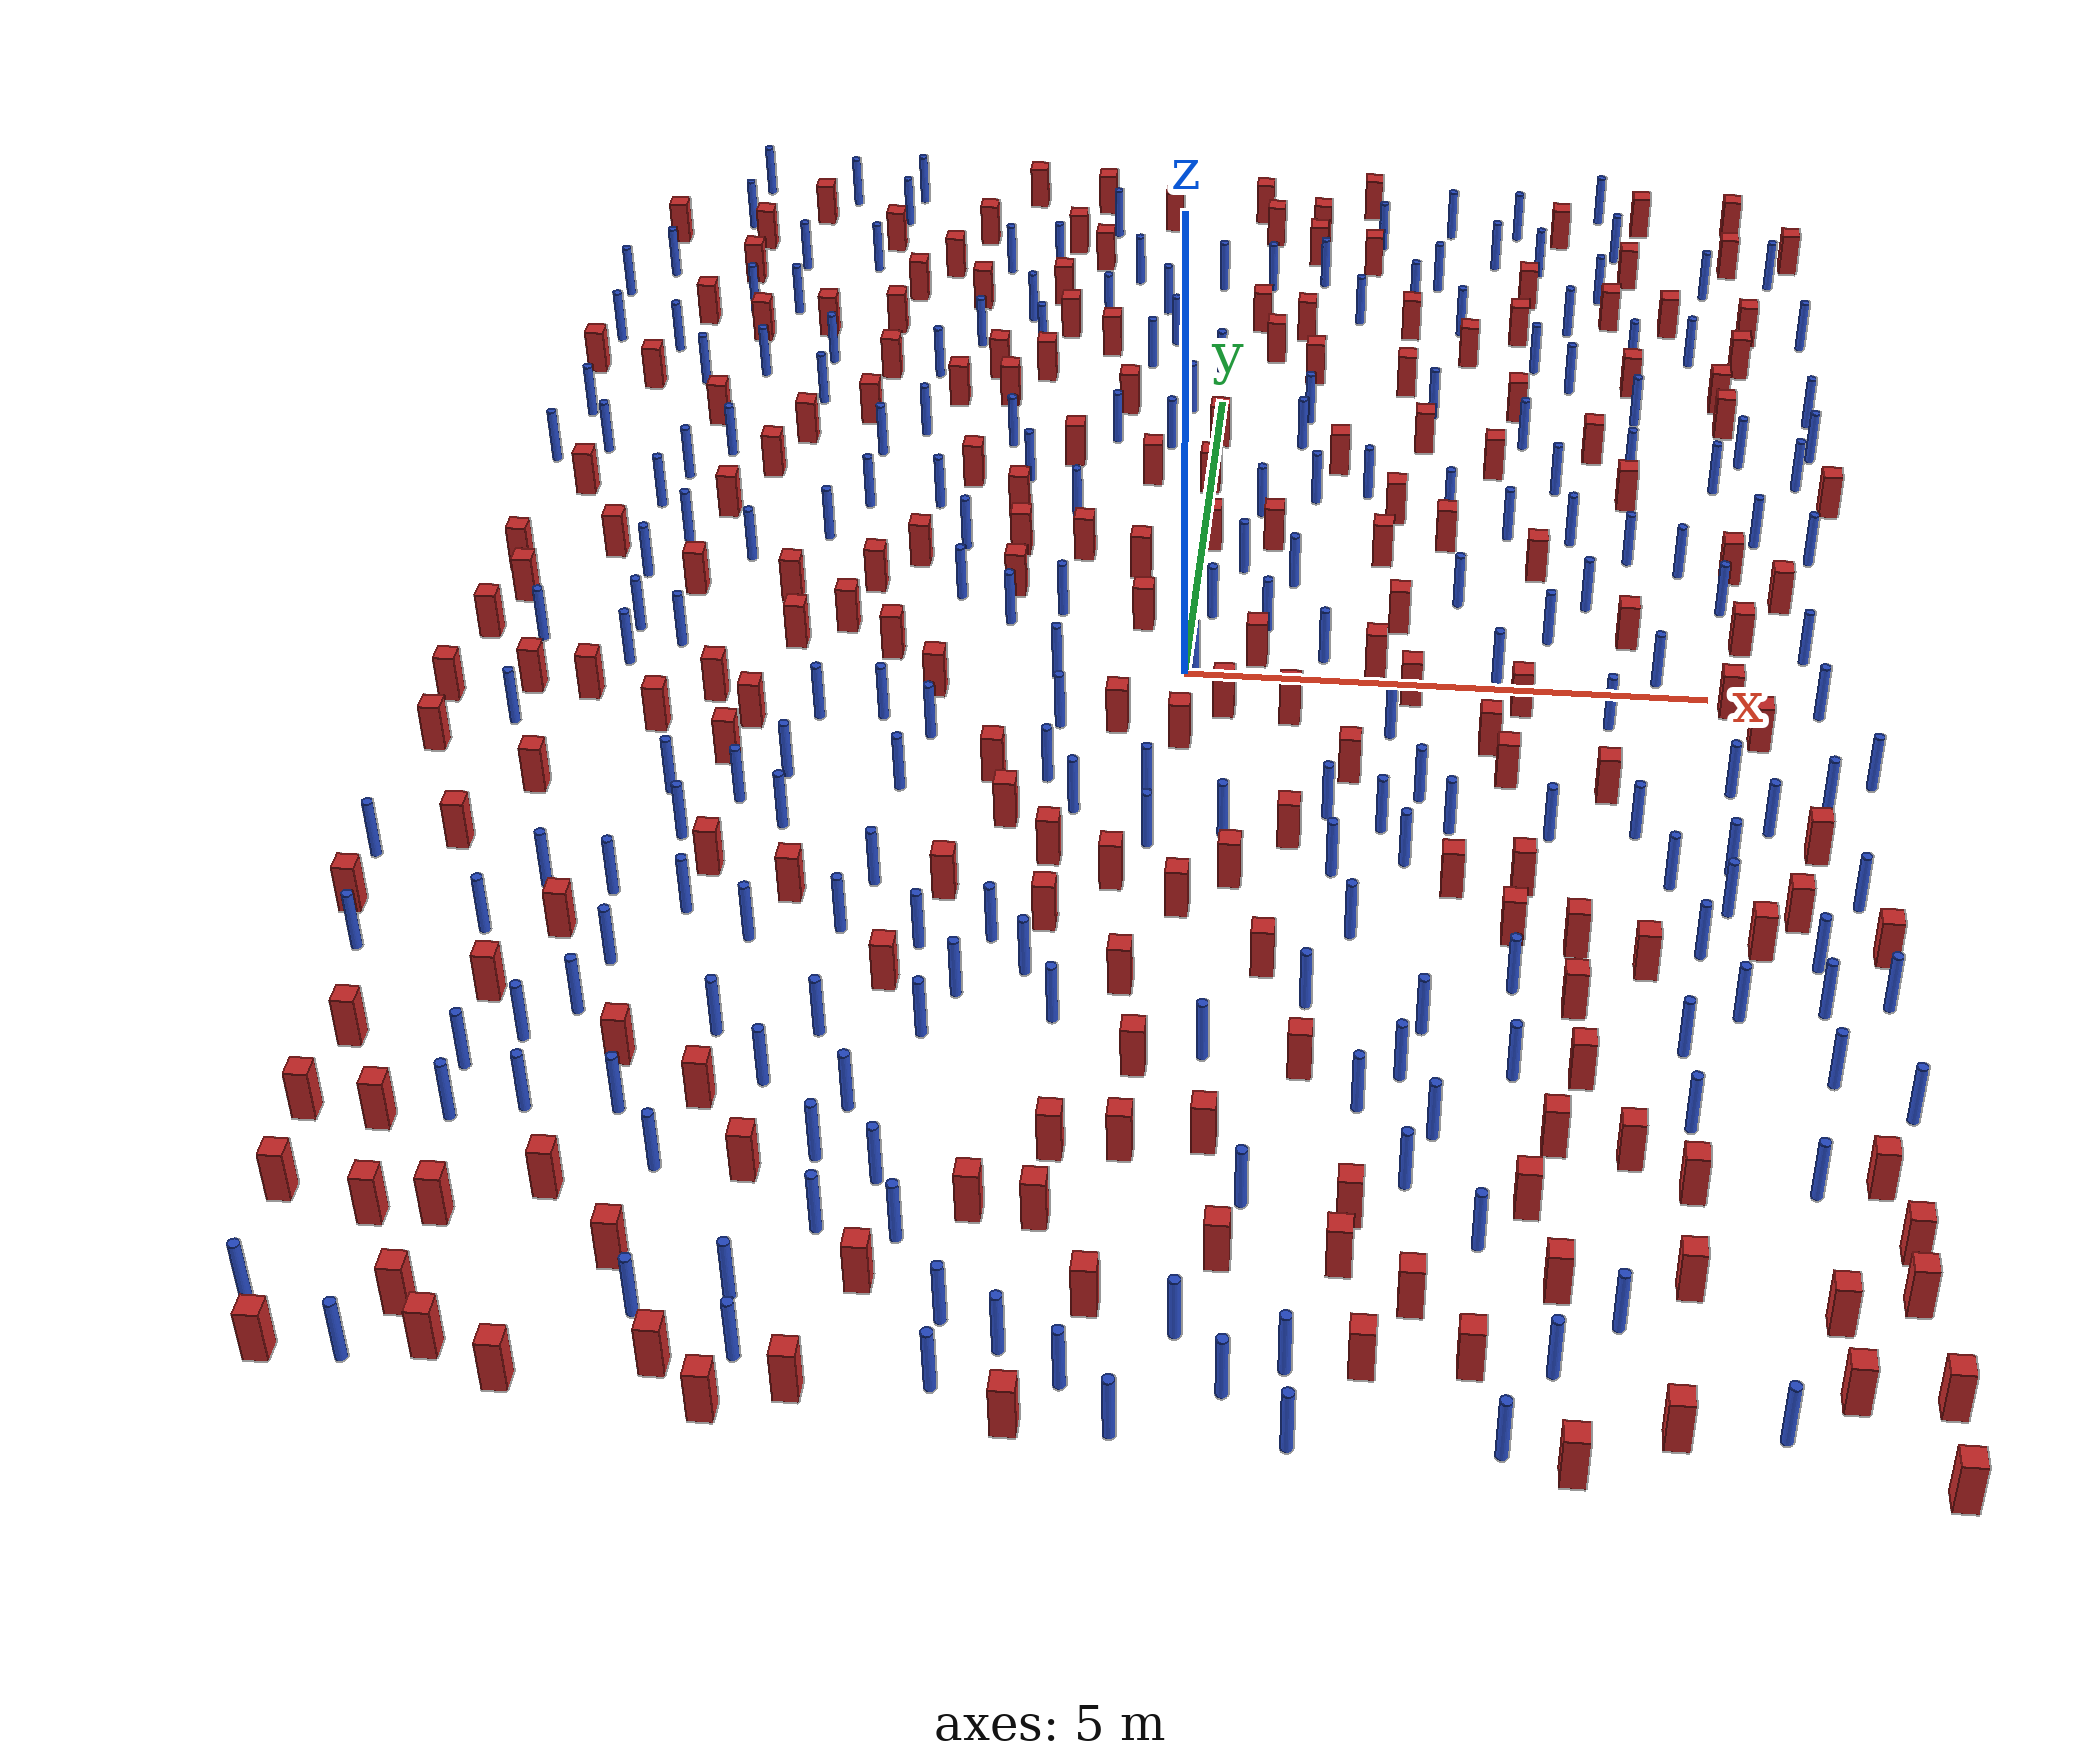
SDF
<sdf version="1.6">
  <model name="dense_42"><model name="square_post_obstacle0">
  <static>true</static>
  <pose frame="">-2.84587844611 0.101750438623 8.22691968438e-08 7.2212513382e-06 -7.54495500217e-07 2.29674213826e-05</pose>
  <link name="link">
    <pose frame="">0 0 0.25 0 -0 0</pose>
    <inertial>
      <mass>100</mass>
      <inertia>
        <ixx>0.166667</ixx>
        <ixy>0</ixy>
        <ixz>0</ixz>
        <iyy>0.166667</iyy>
        <iyz>0</iyz>
        <izz>0.166667</izz>
      </inertia>
    </inertial>
    <collision name="collision">
      <geometry>
        <box>
          <size>.2 .2 .5</size>
        </box>
      </geometry>
      <max_contacts>10</max_contacts>
      <surface>
        <contact>
          <ode/>
        </contact>
        <bounce/>
        <friction>
          <torsional>
            <ode/>
          </torsional>
          <ode/>
        </friction>
      </surface>
    </collision>
    <visual name="visual">
      <geometry>
        <box>
          <size>.2 .2 .5</size>
        </box>
      </geometry>
      <material>
        <script>
          <name>Gazebo/Red</name>
          <uri>file://media/materials/scripts/gazebo.material</uri>
        </script>
      </material>
    </visual>
    <self_collide>0</self_collide>
    <kinematic>0</kinematic>
  </link>
</model>
<model name="square_post_obstacle1">
  <static>true</static>
  <pose frame="">-6.49581654338 -5.72208467229 8.22691968438e-08 7.22125133819e-06 -7.54495500217e-07 2.29674213826e-05</pose>
  <link name="link">
    <pose frame="">0 0 0.25 0 -0 0</pose>
    <inertial>
      <mass>100</mass>
      <inertia>
        <ixx>0.166667</ixx>
        <ixy>0</ixy>
        <ixz>0</ixz>
        <iyy>0.166667</iyy>
        <iyz>0</iyz>
        <izz>0.166667</izz>
      </inertia>
    </inertial>
    <collision name="collision">
      <geometry>
        <box>
          <size>.2 .2 .5</size>
        </box>
      </geometry>
      <max_contacts>10</max_contacts>
      <surface>
        <contact>
          <ode/>
        </contact>
        <bounce/>
        <friction>
          <torsional>
            <ode/>
          </torsional>
          <ode/>
        </friction>
      </surface>
    </collision>
    <visual name="visual">
      <geometry>
        <box>
          <size>.2 .2 .5</size>
        </box>
      </geometry>
      <material>
        <script>
          <name>Gazebo/Red</name>
          <uri>file://media/materials/scripts/gazebo.material</uri>
        </script>
      </material>
    </visual>
    <self_collide>0</self_collide>
    <kinematic>0</kinematic>
  </link>
</model>
<model name="pole_obstacle0">
  <static>true</static>
  <pose frame="">5.14910917983 -9.02479563036 2.88873142074e-08 -9.9053668967e-09 4.60219948993e-07 -1.20965994957e-07</pose>
  <link name="link">
  <pose frame="">0 0 0.3 0 -0 0</pose>
    <inertial>
      <mass>1</mass>
      <inertia>
        <ixx>0.145833</ixx>
        <ixy>0</ixy>
        <ixz>0</ixz>
        <iyy>0.145833</iyy>
        <iyz>0</iyz>
        <izz>0.125</izz>
      </inertia>
    </inertial>
    <collision name="collision">
      <geometry>
        <cylinder>
          <radius>0.05</radius>
          <length>.6</length>
        </cylinder>
      </geometry>
      <max_contacts>10</max_contacts>
      <surface>
        <contact>
          <ode/>
        </contact>
        <bounce/>
        <friction>
          <torsional>
            <ode/>
          </torsional>
          <ode/>
        </friction>
      </surface>
    </collision>
    <visual name="visual">
      <geometry>
        <cylinder>
          <radius>0.05</radius>
          <length>.6</length>
        </cylinder>
      </geometry>
      <material>
        <script>
          <name>Gazebo/Blue</name>
          <uri>file://media/materials/scripts/gazebo.material</uri>
        </script>
      </material>
    </visual>
    <self_collide>0</self_collide>
    <kinematic>0</kinematic>
  </link>
</model>
<model name="square_post_obstacle2">
  <static>true</static>
  <pose frame="">5.34780435043 0.85388809612 8.22691968438e-08 7.2212513382e-06 -7.54495500217e-07 2.29674213826e-05</pose>
  <link name="link">
    <pose frame="">0 0 0.25 0 -0 0</pose>
    <inertial>
      <mass>100</mass>
      <inertia>
        <ixx>0.166667</ixx>
        <ixy>0</ixy>
        <ixz>0</ixz>
        <iyy>0.166667</iyy>
        <iyz>0</iyz>
        <izz>0.166667</izz>
      </inertia>
    </inertial>
    <collision name="collision">
      <geometry>
        <box>
          <size>.2 .2 .5</size>
        </box>
      </geometry>
      <max_contacts>10</max_contacts>
      <surface>
        <contact>
          <ode/>
        </contact>
        <bounce/>
        <friction>
          <torsional>
            <ode/>
          </torsional>
          <ode/>
        </friction>
      </surface>
    </collision>
    <visual name="visual">
      <geometry>
        <box>
          <size>.2 .2 .5</size>
        </box>
      </geometry>
      <material>
        <script>
          <name>Gazebo/Red</name>
          <uri>file://media/materials/scripts/gazebo.material</uri>
        </script>
      </material>
    </visual>
    <self_collide>0</self_collide>
    <kinematic>0</kinematic>
  </link>
</model>
<model name="pole_obstacle1">
  <static>true</static>
  <pose frame="">-1.77444294185 -5.25899595476 2.88873142074e-08 -9.90536689852e-09 4.60219948989e-07 -1.2096599496e-07</pose>
  <link name="link">
  <pose frame="">0 0 0.3 0 -0 0</pose>
    <inertial>
      <mass>1</mass>
      <inertia>
        <ixx>0.145833</ixx>
        <ixy>0</ixy>
        <ixz>0</ixz>
        <iyy>0.145833</iyy>
        <iyz>0</iyz>
        <izz>0.125</izz>
      </inertia>
    </inertial>
    <collision name="collision">
      <geometry>
        <cylinder>
          <radius>0.05</radius>
          <length>.6</length>
        </cylinder>
      </geometry>
      <max_contacts>10</max_contacts>
      <surface>
        <contact>
          <ode/>
        </contact>
        <bounce/>
        <friction>
          <torsional>
            <ode/>
          </torsional>
          <ode/>
        </friction>
      </surface>
    </collision>
    <visual name="visual">
      <geometry>
        <cylinder>
          <radius>0.05</radius>
          <length>.6</length>
        </cylinder>
      </geometry>
      <material>
        <script>
          <name>Gazebo/Blue</name>
          <uri>file://media/materials/scripts/gazebo.material</uri>
        </script>
      </material>
    </visual>
    <self_collide>0</self_collide>
    <kinematic>0</kinematic>
  </link>
</model>
<model name="square_post_obstacle3">
  <static>true</static>
  <pose frame="">-2.81162814861 1.6960479583 8.22691968438e-08 7.2212513382e-06 -7.54495500217e-07 2.29674213826e-05</pose>
  <link name="link">
    <pose frame="">0 0 0.25 0 -0 0</pose>
    <inertial>
      <mass>100</mass>
      <inertia>
        <ixx>0.166667</ixx>
        <ixy>0</ixy>
        <ixz>0</ixz>
        <iyy>0.166667</iyy>
        <iyz>0</iyz>
        <izz>0.166667</izz>
      </inertia>
    </inertial>
    <collision name="collision">
      <geometry>
        <box>
          <size>.2 .2 .5</size>
        </box>
      </geometry>
      <max_contacts>10</max_contacts>
      <surface>
        <contact>
          <ode/>
        </contact>
        <bounce/>
        <friction>
          <torsional>
            <ode/>
          </torsional>
          <ode/>
        </friction>
      </surface>
    </collision>
    <visual name="visual">
      <geometry>
        <box>
          <size>.2 .2 .5</size>
        </box>
      </geometry>
      <material>
        <script>
          <name>Gazebo/Red</name>
          <uri>file://media/materials/scripts/gazebo.material</uri>
        </script>
      </material>
    </visual>
    <self_collide>0</self_collide>
    <kinematic>0</kinematic>
  </link>
</model>
<model name="pole_obstacle2">
  <static>true</static>
  <pose frame="">1.01651458315 -8.93385281026 2.88873142074e-08 -9.90536690572e-09 4.60219948972e-07 -1.20965994971e-07</pose>
  <link name="link">
  <pose frame="">0 0 0.3 0 -0 0</pose>
    <inertial>
      <mass>1</mass>
      <inertia>
        <ixx>0.145833</ixx>
        <ixy>0</ixy>
        <ixz>0</ixz>
        <iyy>0.145833</iyy>
        <iyz>0</iyz>
        <izz>0.125</izz>
      </inertia>
    </inertial>
    <collision name="collision">
      <geometry>
        <cylinder>
          <radius>0.05</radius>
          <length>.6</length>
        </cylinder>
      </geometry>
      <max_contacts>10</max_contacts>
      <surface>
        <contact>
          <ode/>
        </contact>
        <bounce/>
        <friction>
          <torsional>
            <ode/>
          </torsional>
          <ode/>
        </friction>
      </surface>
    </collision>
    <visual name="visual">
      <geometry>
        <cylinder>
          <radius>0.05</radius>
          <length>.6</length>
        </cylinder>
      </geometry>
      <material>
        <script>
          <name>Gazebo/Blue</name>
          <uri>file://media/materials/scripts/gazebo.material</uri>
        </script>
      </material>
    </visual>
    <self_collide>0</self_collide>
    <kinematic>0</kinematic>
  </link>
</model>
<model name="pole_obstacle3">
  <static>true</static>
  <pose frame="">3.18833374677 8.98919953602 2.88873142074e-08 -9.90536692318e-09 4.6021994893e-07 -1.20965994988e-07</pose>
  <link name="link">
  <pose frame="">0 0 0.3 0 -0 0</pose>
    <inertial>
      <mass>1</mass>
      <inertia>
        <ixx>0.145833</ixx>
        <ixy>0</ixy>
        <ixz>0</ixz>
        <iyy>0.145833</iyy>
        <iyz>0</iyz>
        <izz>0.125</izz>
      </inertia>
    </inertial>
    <collision name="collision">
      <geometry>
        <cylinder>
          <radius>0.05</radius>
          <length>.6</length>
        </cylinder>
      </geometry>
      <max_contacts>10</max_contacts>
      <surface>
        <contact>
          <ode/>
        </contact>
        <bounce/>
        <friction>
          <torsional>
            <ode/>
          </torsional>
          <ode/>
        </friction>
      </surface>
    </collision>
    <visual name="visual">
      <geometry>
        <cylinder>
          <radius>0.05</radius>
          <length>.6</length>
        </cylinder>
      </geometry>
      <material>
        <script>
          <name>Gazebo/Blue</name>
          <uri>file://media/materials/scripts/gazebo.material</uri>
        </script>
      </material>
    </visual>
    <self_collide>0</self_collide>
    <kinematic>0</kinematic>
  </link>
</model>
<model name="square_post_obstacle4">
  <static>true</static>
  <pose frame="">-0.535240153537 -6.54588953892 8.22691968438e-08 7.2212513382e-06 -7.54495500217e-07 2.29674213826e-05</pose>
  <link name="link">
    <pose frame="">0 0 0.25 0 -0 0</pose>
    <inertial>
      <mass>100</mass>
      <inertia>
        <ixx>0.166667</ixx>
        <ixy>0</ixy>
        <ixz>0</ixz>
        <iyy>0.166667</iyy>
        <iyz>0</iyz>
        <izz>0.166667</izz>
      </inertia>
    </inertial>
    <collision name="collision">
      <geometry>
        <box>
          <size>.2 .2 .5</size>
        </box>
      </geometry>
      <max_contacts>10</max_contacts>
      <surface>
        <contact>
          <ode/>
        </contact>
        <bounce/>
        <friction>
          <torsional>
            <ode/>
          </torsional>
          <ode/>
        </friction>
      </surface>
    </collision>
    <visual name="visual">
      <geometry>
        <box>
          <size>.2 .2 .5</size>
        </box>
      </geometry>
      <material>
        <script>
          <name>Gazebo/Red</name>
          <uri>file://media/materials/scripts/gazebo.material</uri>
        </script>
      </material>
    </visual>
    <self_collide>0</self_collide>
    <kinematic>0</kinematic>
  </link>
</model>
<model name="square_post_obstacle5">
  <static>true</static>
  <pose frame="">-5.23782894316 -7.6623888755 8.22691968438e-08 7.2212513382e-06 -7.54495500217e-07 2.29674213826e-05</pose>
  <link name="link">
    <pose frame="">0 0 0.25 0 -0 0</pose>
    <inertial>
      <mass>100</mass>
      <inertia>
        <ixx>0.166667</ixx>
        <ixy>0</ixy>
        <ixz>0</ixz>
        <iyy>0.166667</iyy>
        <iyz>0</iyz>
        <izz>0.166667</izz>
      </inertia>
    </inertial>
    <collision name="collision">
      <geometry>
        <box>
          <size>.2 .2 .5</size>
        </box>
      </geometry>
      <max_contacts>10</max_contacts>
      <surface>
        <contact>
          <ode/>
        </contact>
        <bounce/>
        <friction>
          <torsional>
            <ode/>
          </torsional>
          <ode/>
        </friction>
      </surface>
    </collision>
    <visual name="visual">
      <geometry>
        <box>
          <size>.2 .2 .5</size>
        </box>
      </geometry>
      <material>
        <script>
          <name>Gazebo/Red</name>
          <uri>file://media/materials/scripts/gazebo.material</uri>
        </script>
      </material>
    </visual>
    <self_collide>0</self_collide>
    <kinematic>0</kinematic>
  </link>
</model>
<model name="square_post_obstacle6">
  <static>true</static>
  <pose frame="">6.38686492071 -8.62933674588 8.22691968438e-08 7.22125133819e-06 -7.54495500217e-07 2.29674213826e-05</pose>
  <link name="link">
    <pose frame="">0 0 0.25 0 -0 0</pose>
    <inertial>
      <mass>100</mass>
      <inertia>
        <ixx>0.166667</ixx>
        <ixy>0</ixy>
        <ixz>0</ixz>
        <iyy>0.166667</iyy>
        <iyz>0</iyz>
        <izz>0.166667</izz>
      </inertia>
    </inertial>
    <collision name="collision">
      <geometry>
        <box>
          <size>.2 .2 .5</size>
        </box>
      </geometry>
      <max_contacts>10</max_contacts>
      <surface>
        <contact>
          <ode/>
        </contact>
        <bounce/>
        <friction>
          <torsional>
            <ode/>
          </torsional>
          <ode/>
        </friction>
      </surface>
    </collision>
    <visual name="visual">
      <geometry>
        <box>
          <size>.2 .2 .5</size>
        </box>
      </geometry>
      <material>
        <script>
          <name>Gazebo/Red</name>
          <uri>file://media/materials/scripts/gazebo.material</uri>
        </script>
      </material>
    </visual>
    <self_collide>0</self_collide>
    <kinematic>0</kinematic>
  </link>
</model>
<model name="pole_obstacle4">
  <static>true</static>
  <pose frame="">0.192153176092 0.988772014604 2.88873142074e-08 -9.90536690114e-09 4.60219948983e-07 -1.20965994964e-07</pose>
  <link name="link">
  <pose frame="">0 0 0.3 0 -0 0</pose>
    <inertial>
      <mass>1</mass>
      <inertia>
        <ixx>0.145833</ixx>
        <ixy>0</ixy>
        <ixz>0</ixz>
        <iyy>0.145833</iyy>
        <iyz>0</iyz>
        <izz>0.125</izz>
      </inertia>
    </inertial>
    <collision name="collision">
      <geometry>
        <cylinder>
          <radius>0.05</radius>
          <length>.6</length>
        </cylinder>
      </geometry>
      <max_contacts>10</max_contacts>
      <surface>
        <contact>
          <ode/>
        </contact>
        <bounce/>
        <friction>
          <torsional>
            <ode/>
          </torsional>
          <ode/>
        </friction>
      </surface>
    </collision>
    <visual name="visual">
      <geometry>
        <cylinder>
          <radius>0.05</radius>
          <length>.6</length>
        </cylinder>
      </geometry>
      <material>
        <script>
          <name>Gazebo/Blue</name>
          <uri>file://media/materials/scripts/gazebo.material</uri>
        </script>
      </material>
    </visual>
    <self_collide>0</self_collide>
    <kinematic>0</kinematic>
  </link>
</model>
<model name="pole_obstacle5">
  <static>true</static>
  <pose frame="">-2.66993275349 -4.00162867115 2.88873142074e-08 -9.90536690007e-09 4.60219948985e-07 -1.20965994963e-07</pose>
  <link name="link">
  <pose frame="">0 0 0.3 0 -0 0</pose>
    <inertial>
      <mass>1</mass>
      <inertia>
        <ixx>0.145833</ixx>
        <ixy>0</ixy>
        <ixz>0</ixz>
        <iyy>0.145833</iyy>
        <iyz>0</iyz>
        <izz>0.125</izz>
      </inertia>
    </inertial>
    <collision name="collision">
      <geometry>
        <cylinder>
          <radius>0.05</radius>
          <length>.6</length>
        </cylinder>
      </geometry>
      <max_contacts>10</max_contacts>
      <surface>
        <contact>
          <ode/>
        </contact>
        <bounce/>
        <friction>
          <torsional>
            <ode/>
          </torsional>
          <ode/>
        </friction>
      </surface>
    </collision>
    <visual name="visual">
      <geometry>
        <cylinder>
          <radius>0.05</radius>
          <length>.6</length>
        </cylinder>
      </geometry>
      <material>
        <script>
          <name>Gazebo/Blue</name>
          <uri>file://media/materials/scripts/gazebo.material</uri>
        </script>
      </material>
    </visual>
    <self_collide>0</self_collide>
    <kinematic>0</kinematic>
  </link>
</model>
<model name="square_post_obstacle7">
  <static>true</static>
  <pose frame="">-5.48395240583 -5.07697319448 8.22691968438e-08 7.22125133819e-06 -7.54495500217e-07 2.29674213826e-05</pose>
  <link name="link">
    <pose frame="">0 0 0.25 0 -0 0</pose>
    <inertial>
      <mass>100</mass>
      <inertia>
        <ixx>0.166667</ixx>
        <ixy>0</ixy>
        <ixz>0</ixz>
        <iyy>0.166667</iyy>
        <iyz>0</iyz>
        <izz>0.166667</izz>
      </inertia>
    </inertial>
    <collision name="collision">
      <geometry>
        <box>
          <size>.2 .2 .5</size>
        </box>
      </geometry>
      <max_contacts>10</max_contacts>
      <surface>
        <contact>
          <ode/>
        </contact>
        <bounce/>
        <friction>
          <torsional>
            <ode/>
          </torsional>
          <ode/>
        </friction>
      </surface>
    </collision>
    <visual name="visual">
      <geometry>
        <box>
          <size>.2 .2 .5</size>
        </box>
      </geometry>
      <material>
        <script>
          <name>Gazebo/Red</name>
          <uri>file://media/materials/scripts/gazebo.material</uri>
        </script>
      </material>
    </visual>
    <self_collide>0</self_collide>
    <kinematic>0</kinematic>
  </link>
</model>
<model name="square_post_obstacle8">
  <static>true</static>
  <pose frame="">-5.08097280859 -4.21850157625 8.22691968438e-08 7.2212513382e-06 -7.54495500217e-07 2.29674213826e-05</pose>
  <link name="link">
    <pose frame="">0 0 0.25 0 -0 0</pose>
    <inertial>
      <mass>100</mass>
      <inertia>
        <ixx>0.166667</ixx>
        <ixy>0</ixy>
        <ixz>0</ixz>
        <iyy>0.166667</iyy>
        <iyz>0</iyz>
        <izz>0.166667</izz>
      </inertia>
    </inertial>
    <collision name="collision">
      <geometry>
        <box>
          <size>.2 .2 .5</size>
        </box>
      </geometry>
      <max_contacts>10</max_contacts>
      <surface>
        <contact>
          <ode/>
        </contact>
        <bounce/>
        <friction>
          <torsional>
            <ode/>
          </torsional>
          <ode/>
        </friction>
      </surface>
    </collision>
    <visual name="visual">
      <geometry>
        <box>
          <size>.2 .2 .5</size>
        </box>
      </geometry>
      <material>
        <script>
          <name>Gazebo/Red</name>
          <uri>file://media/materials/scripts/gazebo.material</uri>
        </script>
      </material>
    </visual>
    <self_collide>0</self_collide>
    <kinematic>0</kinematic>
  </link>
</model>
<model name="pole_obstacle6">
  <static>true</static>
  <pose frame="">5.07800445016 -2.56818857916 2.88873142074e-08 -9.90536690245e-09 4.6021994898e-07 -1.20965994966e-07</pose>
  <link name="link">
  <pose frame="">0 0 0.3 0 -0 0</pose>
    <inertial>
      <mass>1</mass>
      <inertia>
        <ixx>0.145833</ixx>
        <ixy>0</ixy>
        <ixz>0</ixz>
        <iyy>0.145833</iyy>
        <iyz>0</iyz>
        <izz>0.125</izz>
      </inertia>
    </inertial>
    <collision name="collision">
      <geometry>
        <cylinder>
          <radius>0.05</radius>
          <length>.6</length>
        </cylinder>
      </geometry>
      <max_contacts>10</max_contacts>
      <surface>
        <contact>
          <ode/>
        </contact>
        <bounce/>
        <friction>
          <torsional>
            <ode/>
          </torsional>
          <ode/>
        </friction>
      </surface>
    </collision>
    <visual name="visual">
      <geometry>
        <cylinder>
          <radius>0.05</radius>
          <length>.6</length>
        </cylinder>
      </geometry>
      <material>
        <script>
          <name>Gazebo/Blue</name>
          <uri>file://media/materials/scripts/gazebo.material</uri>
        </script>
      </material>
    </visual>
    <self_collide>0</self_collide>
    <kinematic>0</kinematic>
  </link>
</model>
<model name="pole_obstacle7">
  <static>true</static>
  <pose frame="">-3.89535260939 -2.29034658619 2.88873142074e-08 -9.90536690232e-09 4.6021994898e-07 -1.20965994968e-07</pose>
  <link name="link">
  <pose frame="">0 0 0.3 0 -0 0</pose>
    <inertial>
      <mass>1</mass>
      <inertia>
        <ixx>0.145833</ixx>
        <ixy>0</ixy>
        <ixz>0</ixz>
        <iyy>0.145833</iyy>
        <iyz>0</iyz>
        <izz>0.125</izz>
      </inertia>
    </inertial>
    <collision name="collision">
      <geometry>
        <cylinder>
          <radius>0.05</radius>
          <length>.6</length>
        </cylinder>
      </geometry>
      <max_contacts>10</max_contacts>
      <surface>
        <contact>
          <ode/>
        </contact>
        <bounce/>
        <friction>
          <torsional>
            <ode/>
          </torsional>
          <ode/>
        </friction>
      </surface>
    </collision>
    <visual name="visual">
      <geometry>
        <cylinder>
          <radius>0.05</radius>
          <length>.6</length>
        </cylinder>
      </geometry>
      <material>
        <script>
          <name>Gazebo/Blue</name>
          <uri>file://media/materials/scripts/gazebo.material</uri>
        </script>
      </material>
    </visual>
    <self_collide>0</self_collide>
    <kinematic>0</kinematic>
  </link>
</model>
<model name="square_post_obstacle9">
  <static>true</static>
  <pose frame="">0.0334384078424 -5.51936645068 8.22691968438e-08 7.22125133819e-06 -7.54495500217e-07 2.29674213826e-05</pose>
  <link name="link">
    <pose frame="">0 0 0.25 0 -0 0</pose>
    <inertial>
      <mass>100</mass>
      <inertia>
        <ixx>0.166667</ixx>
        <ixy>0</ixy>
        <ixz>0</ixz>
        <iyy>0.166667</iyy>
        <iyz>0</iyz>
        <izz>0.166667</izz>
      </inertia>
    </inertial>
    <collision name="collision">
      <geometry>
        <box>
          <size>.2 .2 .5</size>
        </box>
      </geometry>
      <max_contacts>10</max_contacts>
      <surface>
        <contact>
          <ode/>
        </contact>
        <bounce/>
        <friction>
          <torsional>
            <ode/>
          </torsional>
          <ode/>
        </friction>
      </surface>
    </collision>
    <visual name="visual">
      <geometry>
        <box>
          <size>.2 .2 .5</size>
        </box>
      </geometry>
      <material>
        <script>
          <name>Gazebo/Red</name>
          <uri>file://media/materials/scripts/gazebo.material</uri>
        </script>
      </material>
    </visual>
    <self_collide>0</self_collide>
    <kinematic>0</kinematic>
  </link>
</model>
<model name="square_post_obstacle10">
  <static>true</static>
  <pose frame="">-1.92742134845 8.2964371312 8.22691968438e-08 7.22125133819e-06 -7.54495500217e-07 2.29674213826e-05</pose>
  <link name="link">
    <pose frame="">0 0 0.25 0 -0 0</pose>
    <inertial>
      <mass>100</mass>
      <inertia>
        <ixx>0.166667</ixx>
        <ixy>0</ixy>
        <ixz>0</ixz>
        <iyy>0.166667</iyy>
        <iyz>0</iyz>
        <izz>0.166667</izz>
      </inertia>
    </inertial>
    <collision name="collision">
      <geometry>
        <box>
          <size>.2 .2 .5</size>
        </box>
      </geometry>
      <max_contacts>10</max_contacts>
      <surface>
        <contact>
          <ode/>
        </contact>
        <bounce/>
        <friction>
          <torsional>
            <ode/>
          </torsional>
          <ode/>
        </friction>
      </surface>
    </collision>
    <visual name="visual">
      <geometry>
        <box>
          <size>.2 .2 .5</size>
        </box>
      </geometry>
      <material>
        <script>
          <name>Gazebo/Red</name>
          <uri>file://media/materials/scripts/gazebo.material</uri>
        </script>
      </material>
    </visual>
    <self_collide>0</self_collide>
    <kinematic>0</kinematic>
  </link>
</model>
<model name="square_post_obstacle11">
  <static>true</static>
  <pose frame="">5.31267235231 2.07348907233 8.22691968438e-08 7.2212513382e-06 -7.54495500217e-07 2.29674213826e-05</pose>
  <link name="link">
    <pose frame="">0 0 0.25 0 -0 0</pose>
    <inertial>
      <mass>100</mass>
      <inertia>
        <ixx>0.166667</ixx>
        <ixy>0</ixy>
        <ixz>0</ixz>
        <iyy>0.166667</iyy>
        <iyz>0</iyz>
        <izz>0.166667</izz>
      </inertia>
    </inertial>
    <collision name="collision">
      <geometry>
        <box>
          <size>.2 .2 .5</size>
        </box>
      </geometry>
      <max_contacts>10</max_contacts>
      <surface>
        <contact>
          <ode/>
        </contact>
        <bounce/>
        <friction>
          <torsional>
            <ode/>
          </torsional>
          <ode/>
        </friction>
      </surface>
    </collision>
    <visual name="visual">
      <geometry>
        <box>
          <size>.2 .2 .5</size>
        </box>
      </geometry>
      <material>
        <script>
          <name>Gazebo/Red</name>
          <uri>file://media/materials/scripts/gazebo.material</uri>
        </script>
      </material>
    </visual>
    <self_collide>0</self_collide>
    <kinematic>0</kinematic>
  </link>
</model>
<model name="square_post_obstacle12">
  <static>true</static>
  <pose frame="">-3.74836565161 4.35340912572 8.22691968438e-08 7.2212513382e-06 -7.54495500217e-07 2.29674213826e-05</pose>
  <link name="link">
    <pose frame="">0 0 0.25 0 -0 0</pose>
    <inertial>
      <mass>100</mass>
      <inertia>
        <ixx>0.166667</ixx>
        <ixy>0</ixy>
        <ixz>0</ixz>
        <iyy>0.166667</iyy>
        <iyz>0</iyz>
        <izz>0.166667</izz>
      </inertia>
    </inertial>
    <collision name="collision">
      <geometry>
        <box>
          <size>.2 .2 .5</size>
        </box>
      </geometry>
      <max_contacts>10</max_contacts>
      <surface>
        <contact>
          <ode/>
        </contact>
        <bounce/>
        <friction>
          <torsional>
            <ode/>
          </torsional>
          <ode/>
        </friction>
      </surface>
    </collision>
    <visual name="visual">
      <geometry>
        <box>
          <size>.2 .2 .5</size>
        </box>
      </geometry>
      <material>
        <script>
          <name>Gazebo/Red</name>
          <uri>file://media/materials/scripts/gazebo.material</uri>
        </script>
      </material>
    </visual>
    <self_collide>0</self_collide>
    <kinematic>0</kinematic>
  </link>
</model>
<model name="square_post_obstacle13">
  <static>true</static>
  <pose frame="">-2.99132593924 8.41528453703 8.22691968438e-08 7.22125133819e-06 -7.54495500217e-07 2.29674213826e-05</pose>
  <link name="link">
    <pose frame="">0 0 0.25 0 -0 0</pose>
    <inertial>
      <mass>100</mass>
      <inertia>
        <ixx>0.166667</ixx>
        <ixy>0</ixy>
        <ixz>0</ixz>
        <iyy>0.166667</iyy>
        <iyz>0</iyz>
        <izz>0.166667</izz>
      </inertia>
    </inertial>
    <collision name="collision">
      <geometry>
        <box>
          <size>.2 .2 .5</size>
        </box>
      </geometry>
      <max_contacts>10</max_contacts>
      <surface>
        <contact>
          <ode/>
        </contact>
        <bounce/>
        <friction>
          <torsional>
            <ode/>
          </torsional>
          <ode/>
        </friction>
      </surface>
    </collision>
    <visual name="visual">
      <geometry>
        <box>
          <size>.2 .2 .5</size>
        </box>
      </geometry>
      <material>
        <script>
          <name>Gazebo/Red</name>
          <uri>file://media/materials/scripts/gazebo.material</uri>
        </script>
      </material>
    </visual>
    <self_collide>0</self_collide>
    <kinematic>0</kinematic>
  </link>
</model>
<model name="pole_obstacle8">
  <static>true</static>
  <pose frame="">3.58204514085 3.50767078922 2.88873142074e-08 -9.90536690232e-09 4.6021994898e-07 -1.20965994968e-07</pose>
  <link name="link">
  <pose frame="">0 0 0.3 0 -0 0</pose>
    <inertial>
      <mass>1</mass>
      <inertia>
        <ixx>0.145833</ixx>
        <ixy>0</ixy>
        <ixz>0</ixz>
        <iyy>0.145833</iyy>
        <iyz>0</iyz>
        <izz>0.125</izz>
      </inertia>
    </inertial>
    <collision name="collision">
      <geometry>
        <cylinder>
          <radius>0.05</radius>
          <length>.6</length>
        </cylinder>
      </geometry>
      <max_contacts>10</max_contacts>
      <surface>
        <contact>
          <ode/>
        </contact>
        <bounce/>
        <friction>
          <torsional>
            <ode/>
          </torsional>
          <ode/>
        </friction>
      </surface>
    </collision>
    <visual name="visual">
      <geometry>
        <cylinder>
          <radius>0.05</radius>
          <length>.6</length>
        </cylinder>
      </geometry>
      <material>
        <script>
          <name>Gazebo/Blue</name>
          <uri>file://media/materials/scripts/gazebo.material</uri>
        </script>
      </material>
    </visual>
    <self_collide>0</self_collide>
    <kinematic>0</kinematic>
  </link>
</model>
<model name="square_post_obstacle14">
  <static>true</static>
  <pose frame="">3.66599458172 -4.5079094734 8.22691968438e-08 7.2212513382e-06 -7.54495500217e-07 2.29674213826e-05</pose>
  <link name="link">
    <pose frame="">0 0 0.25 0 -0 0</pose>
    <inertial>
      <mass>100</mass>
      <inertia>
        <ixx>0.166667</ixx>
        <ixy>0</ixy>
        <ixz>0</ixz>
        <iyy>0.166667</iyy>
        <iyz>0</iyz>
        <izz>0.166667</izz>
      </inertia>
    </inertial>
    <collision name="collision">
      <geometry>
        <box>
          <size>.2 .2 .5</size>
        </box>
      </geometry>
      <max_contacts>10</max_contacts>
      <surface>
        <contact>
          <ode/>
        </contact>
        <bounce/>
        <friction>
          <torsional>
            <ode/>
          </torsional>
          <ode/>
        </friction>
      </surface>
    </collision>
    <visual name="visual">
      <geometry>
        <box>
          <size>.2 .2 .5</size>
        </box>
      </geometry>
      <material>
        <script>
          <name>Gazebo/Red</name>
          <uri>file://media/materials/scripts/gazebo.material</uri>
        </script>
      </material>
    </visual>
    <self_collide>0</self_collide>
    <kinematic>0</kinematic>
  </link>
</model>
<model name="square_post_obstacle15">
  <static>true</static>
  <pose frame="">-5.27272113608 -8.60478890227 8.22691968438e-08 7.22125133819e-06 -7.54495500217e-07 2.29674213826e-05</pose>
  <link name="link">
    <pose frame="">0 0 0.25 0 -0 0</pose>
    <inertial>
      <mass>100</mass>
      <inertia>
        <ixx>0.166667</ixx>
        <ixy>0</ixy>
        <ixz>0</ixz>
        <iyy>0.166667</iyy>
        <iyz>0</iyz>
        <izz>0.166667</izz>
      </inertia>
    </inertial>
    <collision name="collision">
      <geometry>
        <box>
          <size>.2 .2 .5</size>
        </box>
      </geometry>
      <max_contacts>10</max_contacts>
      <surface>
        <contact>
          <ode/>
        </contact>
        <bounce/>
        <friction>
          <torsional>
            <ode/>
          </torsional>
          <ode/>
        </friction>
      </surface>
    </collision>
    <visual name="visual">
      <geometry>
        <box>
          <size>.2 .2 .5</size>
        </box>
      </geometry>
      <material>
        <script>
          <name>Gazebo/Red</name>
          <uri>file://media/materials/scripts/gazebo.material</uri>
        </script>
      </material>
    </visual>
    <self_collide>0</self_collide>
    <kinematic>0</kinematic>
  </link>
</model>
<model name="square_post_obstacle16">
  <static>true</static>
  <pose frame="">-4.91666649072 2.42147475702 8.22691968438e-08 7.2212513382e-06 -7.54495500217e-07 2.29674213826e-05</pose>
  <link name="link">
    <pose frame="">0 0 0.25 0 -0 0</pose>
    <inertial>
      <mass>100</mass>
      <inertia>
        <ixx>0.166667</ixx>
        <ixy>0</ixy>
        <ixz>0</ixz>
        <iyy>0.166667</iyy>
        <iyz>0</iyz>
        <izz>0.166667</izz>
      </inertia>
    </inertial>
    <collision name="collision">
      <geometry>
        <box>
          <size>.2 .2 .5</size>
        </box>
      </geometry>
      <max_contacts>10</max_contacts>
      <surface>
        <contact>
          <ode/>
        </contact>
        <bounce/>
        <friction>
          <torsional>
            <ode/>
          </torsional>
          <ode/>
        </friction>
      </surface>
    </collision>
    <visual name="visual">
      <geometry>
        <box>
          <size>.2 .2 .5</size>
        </box>
      </geometry>
      <material>
        <script>
          <name>Gazebo/Red</name>
          <uri>file://media/materials/scripts/gazebo.material</uri>
        </script>
      </material>
    </visual>
    <self_collide>0</self_collide>
    <kinematic>0</kinematic>
  </link>
</model>
<model name="pole_obstacle9">
  <static>true</static>
  <pose frame="">-2.64808662355 -8.89009534541 2.88873142074e-08 -9.90536692318e-09 4.6021994893e-07 -1.20965994988e-07</pose>
  <link name="link">
  <pose frame="">0 0 0.3 0 -0 0</pose>
    <inertial>
      <mass>1</mass>
      <inertia>
        <ixx>0.145833</ixx>
        <ixy>0</ixy>
        <ixz>0</ixz>
        <iyy>0.145833</iyy>
        <iyz>0</iyz>
        <izz>0.125</izz>
      </inertia>
    </inertial>
    <collision name="collision">
      <geometry>
        <cylinder>
          <radius>0.05</radius>
          <length>.6</length>
        </cylinder>
      </geometry>
      <max_contacts>10</max_contacts>
      <surface>
        <contact>
          <ode/>
        </contact>
        <bounce/>
        <friction>
          <torsional>
            <ode/>
          </torsional>
          <ode/>
        </friction>
      </surface>
    </collision>
    <visual name="visual">
      <geometry>
        <cylinder>
          <radius>0.05</radius>
          <length>.6</length>
        </cylinder>
      </geometry>
      <material>
        <script>
          <name>Gazebo/Blue</name>
          <uri>file://media/materials/scripts/gazebo.material</uri>
        </script>
      </material>
    </visual>
    <self_collide>0</self_collide>
    <kinematic>0</kinematic>
  </link>
</model>
<model name="square_post_obstacle17">
  <static>true</static>
  <pose frame="">-5.79297355049 -2.24923359172 8.22691968438e-08 7.2212513382e-06 -7.54495500217e-07 2.29674213826e-05</pose>
  <link name="link">
    <pose frame="">0 0 0.25 0 -0 0</pose>
    <inertial>
      <mass>100</mass>
      <inertia>
        <ixx>0.166667</ixx>
        <ixy>0</ixy>
        <ixz>0</ixz>
        <iyy>0.166667</iyy>
        <iyz>0</iyz>
        <izz>0.166667</izz>
      </inertia>
    </inertial>
    <collision name="collision">
      <geometry>
        <box>
          <size>.2 .2 .5</size>
        </box>
      </geometry>
      <max_contacts>10</max_contacts>
      <surface>
        <contact>
          <ode/>
        </contact>
        <bounce/>
        <friction>
          <torsional>
            <ode/>
          </torsional>
          <ode/>
        </friction>
      </surface>
    </collision>
    <visual name="visual">
      <geometry>
        <box>
          <size>.2 .2 .5</size>
        </box>
      </geometry>
      <material>
        <script>
          <name>Gazebo/Red</name>
          <uri>file://media/materials/scripts/gazebo.material</uri>
        </script>
      </material>
    </visual>
    <self_collide>0</self_collide>
    <kinematic>0</kinematic>
  </link>
</model>
<model name="square_post_obstacle18">
  <static>true</static>
  <pose frame="">-1.93032135828 2.67827413768 8.22691968438e-08 7.2212513382e-06 -7.54495500217e-07 2.29674213826e-05</pose>
  <link name="link">
    <pose frame="">0 0 0.25 0 -0 0</pose>
    <inertial>
      <mass>100</mass>
      <inertia>
        <ixx>0.166667</ixx>
        <ixy>0</ixy>
        <ixz>0</ixz>
        <iyy>0.166667</iyy>
        <iyz>0</iyz>
        <izz>0.166667</izz>
      </inertia>
    </inertial>
    <collision name="collision">
      <geometry>
        <box>
          <size>.2 .2 .5</size>
        </box>
      </geometry>
      <max_contacts>10</max_contacts>
      <surface>
        <contact>
          <ode/>
        </contact>
        <bounce/>
        <friction>
          <torsional>
            <ode/>
          </torsional>
          <ode/>
        </friction>
      </surface>
    </collision>
    <visual name="visual">
      <geometry>
        <box>
          <size>.2 .2 .5</size>
        </box>
      </geometry>
      <material>
        <script>
          <name>Gazebo/Red</name>
          <uri>file://media/materials/scripts/gazebo.material</uri>
        </script>
      </material>
    </visual>
    <self_collide>0</self_collide>
    <kinematic>0</kinematic>
  </link>
</model>
<model name="pole_obstacle10">
  <static>true</static>
  <pose frame="">-1.00639207774 -4.41292333605 2.88873142074e-08 -9.90536689792e-09 4.6021994899e-07 -1.2096599496e-07</pose>
  <link name="link">
  <pose frame="">0 0 0.3 0 -0 0</pose>
    <inertial>
      <mass>1</mass>
      <inertia>
        <ixx>0.145833</ixx>
        <ixy>0</ixy>
        <ixz>0</ixz>
        <iyy>0.145833</iyy>
        <iyz>0</iyz>
        <izz>0.125</izz>
      </inertia>
    </inertial>
    <collision name="collision">
      <geometry>
        <cylinder>
          <radius>0.05</radius>
          <length>.6</length>
        </cylinder>
      </geometry>
      <max_contacts>10</max_contacts>
      <surface>
        <contact>
          <ode/>
        </contact>
        <bounce/>
        <friction>
          <torsional>
            <ode/>
          </torsional>
          <ode/>
        </friction>
      </surface>
    </collision>
    <visual name="visual">
      <geometry>
        <cylinder>
          <radius>0.05</radius>
          <length>.6</length>
        </cylinder>
      </geometry>
      <material>
        <script>
          <name>Gazebo/Blue</name>
          <uri>file://media/materials/scripts/gazebo.material</uri>
        </script>
      </material>
    </visual>
    <self_collide>0</self_collide>
    <kinematic>0</kinematic>
  </link>
</model>
<model name="square_post_obstacle19">
  <static>true</static>
  <pose frame="">-4.88050866906 -1.23946027263 8.22691968438e-08 7.2212513382e-06 -7.54495500217e-07 2.29674213826e-05</pose>
  <link name="link">
    <pose frame="">0 0 0.25 0 -0 0</pose>
    <inertial>
      <mass>100</mass>
      <inertia>
        <ixx>0.166667</ixx>
        <ixy>0</ixy>
        <ixz>0</ixz>
        <iyy>0.166667</iyy>
        <iyz>0</iyz>
        <izz>0.166667</izz>
      </inertia>
    </inertial>
    <collision name="collision">
      <geometry>
        <box>
          <size>.2 .2 .5</size>
        </box>
      </geometry>
      <max_contacts>10</max_contacts>
      <surface>
        <contact>
          <ode/>
        </contact>
        <bounce/>
        <friction>
          <torsional>
            <ode/>
          </torsional>
          <ode/>
        </friction>
      </surface>
    </collision>
    <visual name="visual">
      <geometry>
        <box>
          <size>.2 .2 .5</size>
        </box>
      </geometry>
      <material>
        <script>
          <name>Gazebo/Red</name>
          <uri>file://media/materials/scripts/gazebo.material</uri>
        </script>
      </material>
    </visual>
    <self_collide>0</self_collide>
    <kinematic>0</kinematic>
  </link>
</model>
<model name="pole_obstacle11">
  <static>true</static>
  <pose frame="">5.45333464974 -1.98299385944 2.88873142074e-08 -9.90536689117e-09 4.60219949006e-07 -1.20965994949e-07</pose>
  <link name="link">
  <pose frame="">0 0 0.3 0 -0 0</pose>
    <inertial>
      <mass>1</mass>
      <inertia>
        <ixx>0.145833</ixx>
        <ixy>0</ixy>
        <ixz>0</ixz>
        <iyy>0.145833</iyy>
        <iyz>0</iyz>
        <izz>0.125</izz>
      </inertia>
    </inertial>
    <collision name="collision">
      <geometry>
        <cylinder>
          <radius>0.05</radius>
          <length>.6</length>
        </cylinder>
      </geometry>
      <max_contacts>10</max_contacts>
      <surface>
        <contact>
          <ode/>
        </contact>
        <bounce/>
        <friction>
          <torsional>
            <ode/>
          </torsional>
          <ode/>
        </friction>
      </surface>
    </collision>
    <visual name="visual">
      <geometry>
        <cylinder>
          <radius>0.05</radius>
          <length>.6</length>
        </cylinder>
      </geometry>
      <material>
        <script>
          <name>Gazebo/Blue</name>
          <uri>file://media/materials/scripts/gazebo.material</uri>
        </script>
      </material>
    </visual>
    <self_collide>0</self_collide>
    <kinematic>0</kinematic>
  </link>
</model>
<model name="square_post_obstacle20">
  <static>true</static>
  <pose frame="">4.57043404995 -6.5960539329 8.22691968438e-08 7.2212513382e-06 -7.54495500217e-07 2.29674213826e-05</pose>
  <link name="link">
    <pose frame="">0 0 0.25 0 -0 0</pose>
    <inertial>
      <mass>100</mass>
      <inertia>
        <ixx>0.166667</ixx>
        <ixy>0</ixy>
        <ixz>0</ixz>
        <iyy>0.166667</iyy>
        <iyz>0</iyz>
        <izz>0.166667</izz>
      </inertia>
    </inertial>
    <collision name="collision">
      <geometry>
        <box>
          <size>.2 .2 .5</size>
        </box>
      </geometry>
      <max_contacts>10</max_contacts>
      <surface>
        <contact>
          <ode/>
        </contact>
        <bounce/>
        <friction>
          <torsional>
            <ode/>
          </torsional>
          <ode/>
        </friction>
      </surface>
    </collision>
    <visual name="visual">
      <geometry>
        <box>
          <size>.2 .2 .5</size>
        </box>
      </geometry>
      <material>
        <script>
          <name>Gazebo/Red</name>
          <uri>file://media/materials/scripts/gazebo.material</uri>
        </script>
      </material>
    </visual>
    <self_collide>0</self_collide>
    <kinematic>0</kinematic>
  </link>
</model>
<model name="pole_obstacle12">
  <static>true</static>
  <pose frame="">4.10713382338 7.55863480886 2.88873142074e-08 -9.90536690842e-09 4.60219948965e-07 -1.20965994976e-07</pose>
  <link name="link">
  <pose frame="">0 0 0.3 0 -0 0</pose>
    <inertial>
      <mass>1</mass>
      <inertia>
        <ixx>0.145833</ixx>
        <ixy>0</ixy>
        <ixz>0</ixz>
        <iyy>0.145833</iyy>
        <iyz>0</iyz>
        <izz>0.125</izz>
      </inertia>
    </inertial>
    <collision name="collision">
      <geometry>
        <cylinder>
          <radius>0.05</radius>
          <length>.6</length>
        </cylinder>
      </geometry>
      <max_contacts>10</max_contacts>
      <surface>
        <contact>
          <ode/>
        </contact>
        <bounce/>
        <friction>
          <torsional>
            <ode/>
          </torsional>
          <ode/>
        </friction>
      </surface>
    </collision>
    <visual name="visual">
      <geometry>
        <cylinder>
          <radius>0.05</radius>
          <length>.6</length>
        </cylinder>
      </geometry>
      <material>
        <script>
          <name>Gazebo/Blue</name>
          <uri>file://media/materials/scripts/gazebo.material</uri>
        </script>
      </material>
    </visual>
    <self_collide>0</self_collide>
    <kinematic>0</kinematic>
  </link>
</model>
<model name="square_post_obstacle21">
  <static>true</static>
  <pose frame="">-6.62994186205 8.15287367369 8.22691968438e-08 7.22125133819e-06 -7.54495500217e-07 2.29674213826e-05</pose>
  <link name="link">
    <pose frame="">0 0 0.25 0 -0 0</pose>
    <inertial>
      <mass>100</mass>
      <inertia>
        <ixx>0.166667</ixx>
        <ixy>0</ixy>
        <ixz>0</ixz>
        <iyy>0.166667</iyy>
        <iyz>0</iyz>
        <izz>0.166667</izz>
      </inertia>
    </inertial>
    <collision name="collision">
      <geometry>
        <box>
          <size>.2 .2 .5</size>
        </box>
      </geometry>
      <max_contacts>10</max_contacts>
      <surface>
        <contact>
          <ode/>
        </contact>
        <bounce/>
        <friction>
          <torsional>
            <ode/>
          </torsional>
          <ode/>
        </friction>
      </surface>
    </collision>
    <visual name="visual">
      <geometry>
        <box>
          <size>.2 .2 .5</size>
        </box>
      </geometry>
      <material>
        <script>
          <name>Gazebo/Red</name>
          <uri>file://media/materials/scripts/gazebo.material</uri>
        </script>
      </material>
    </visual>
    <self_collide>0</self_collide>
    <kinematic>0</kinematic>
  </link>
</model>
<model name="pole_obstacle13">
  <static>true</static>
  <pose frame="">0.5886096068 -5.3329055556 2.88873142074e-08 -9.90536689661e-09 4.60219948993e-07 -1.20965994957e-07</pose>
  <link name="link">
  <pose frame="">0 0 0.3 0 -0 0</pose>
    <inertial>
      <mass>1</mass>
      <inertia>
        <ixx>0.145833</ixx>
        <ixy>0</ixy>
        <ixz>0</ixz>
        <iyy>0.145833</iyy>
        <iyz>0</iyz>
        <izz>0.125</izz>
      </inertia>
    </inertial>
    <collision name="collision">
      <geometry>
        <cylinder>
          <radius>0.05</radius>
          <length>.6</length>
        </cylinder>
      </geometry>
      <max_contacts>10</max_contacts>
      <surface>
        <contact>
          <ode/>
        </contact>
        <bounce/>
        <friction>
          <torsional>
            <ode/>
          </torsional>
          <ode/>
        </friction>
      </surface>
    </collision>
    <visual name="visual">
      <geometry>
        <cylinder>
          <radius>0.05</radius>
          <length>.6</length>
        </cylinder>
      </geometry>
      <material>
        <script>
          <name>Gazebo/Blue</name>
          <uri>file://media/materials/scripts/gazebo.material</uri>
        </script>
      </material>
    </visual>
    <self_collide>0</self_collide>
    <kinematic>0</kinematic>
  </link>
</model>
<model name="square_post_obstacle22">
  <static>true</static>
  <pose frame="">2.0303652165 0.946268241063 8.22691968438e-08 7.2212513382e-06 -7.54495500217e-07 2.29674213826e-05</pose>
  <link name="link">
    <pose frame="">0 0 0.25 0 -0 0</pose>
    <inertial>
      <mass>100</mass>
      <inertia>
        <ixx>0.166667</ixx>
        <ixy>0</ixy>
        <ixz>0</ixz>
        <iyy>0.166667</iyy>
        <iyz>0</iyz>
        <izz>0.166667</izz>
      </inertia>
    </inertial>
    <collision name="collision">
      <geometry>
        <box>
          <size>.2 .2 .5</size>
        </box>
      </geometry>
      <max_contacts>10</max_contacts>
      <surface>
        <contact>
          <ode/>
        </contact>
        <bounce/>
        <friction>
          <torsional>
            <ode/>
          </torsional>
          <ode/>
        </friction>
      </surface>
    </collision>
    <visual name="visual">
      <geometry>
        <box>
          <size>.2 .2 .5</size>
        </box>
      </geometry>
      <material>
        <script>
          <name>Gazebo/Red</name>
          <uri>file://media/materials/scripts/gazebo.material</uri>
        </script>
      </material>
    </visual>
    <self_collide>0</self_collide>
    <kinematic>0</kinematic>
  </link>
</model>
<model name="pole_obstacle14">
  <static>true</static>
  <pose frame="">-6.78186057395 4.19371458826 2.88873142074e-08 -9.90536690842e-09 4.60219948965e-07 -1.20965994976e-07</pose>
  <link name="link">
  <pose frame="">0 0 0.3 0 -0 0</pose>
    <inertial>
      <mass>1</mass>
      <inertia>
        <ixx>0.145833</ixx>
        <ixy>0</ixy>
        <ixz>0</ixz>
        <iyy>0.145833</iyy>
        <iyz>0</iyz>
        <izz>0.125</izz>
      </inertia>
    </inertial>
    <collision name="collision">
      <geometry>
        <cylinder>
          <radius>0.05</radius>
          <length>.6</length>
        </cylinder>
      </geometry>
      <max_contacts>10</max_contacts>
      <surface>
        <contact>
          <ode/>
        </contact>
        <bounce/>
        <friction>
          <torsional>
            <ode/>
          </torsional>
          <ode/>
        </friction>
      </surface>
    </collision>
    <visual name="visual">
      <geometry>
        <cylinder>
          <radius>0.05</radius>
          <length>.6</length>
        </cylinder>
      </geometry>
      <material>
        <script>
          <name>Gazebo/Blue</name>
          <uri>file://media/materials/scripts/gazebo.material</uri>
        </script>
      </material>
    </visual>
    <self_collide>0</self_collide>
    <kinematic>0</kinematic>
  </link>
</model>
<model name="pole_obstacle15">
  <static>true</static>
  <pose frame="">5.95249702064 0.702436298179 2.88873142074e-08 -9.90536689837e-09 4.60219948989e-07 -1.2096599496e-07</pose>
  <link name="link">
  <pose frame="">0 0 0.3 0 -0 0</pose>
    <inertial>
      <mass>1</mass>
      <inertia>
        <ixx>0.145833</ixx>
        <ixy>0</ixy>
        <ixz>0</ixz>
        <iyy>0.145833</iyy>
        <iyz>0</iyz>
        <izz>0.125</izz>
      </inertia>
    </inertial>
    <collision name="collision">
      <geometry>
        <cylinder>
          <radius>0.05</radius>
          <length>.6</length>
        </cylinder>
      </geometry>
      <max_contacts>10</max_contacts>
      <surface>
        <contact>
          <ode/>
        </contact>
        <bounce/>
        <friction>
          <torsional>
            <ode/>
          </torsional>
          <ode/>
        </friction>
      </surface>
    </collision>
    <visual name="visual">
      <geometry>
        <cylinder>
          <radius>0.05</radius>
          <length>.6</length>
        </cylinder>
      </geometry>
      <material>
        <script>
          <name>Gazebo/Blue</name>
          <uri>file://media/materials/scripts/gazebo.material</uri>
        </script>
      </material>
    </visual>
    <self_collide>0</self_collide>
    <kinematic>0</kinematic>
  </link>
</model>
<model name="pole_obstacle16">
  <static>true</static>
  <pose frame="">1.62075042939 8.62250264331 2.88873142074e-08 -9.90536690474e-09 4.60219948974e-07 -1.2096599497e-07</pose>
  <link name="link">
  <pose frame="">0 0 0.3 0 -0 0</pose>
    <inertial>
      <mass>1</mass>
      <inertia>
        <ixx>0.145833</ixx>
        <ixy>0</ixy>
        <ixz>0</ixz>
        <iyy>0.145833</iyy>
        <iyz>0</iyz>
        <izz>0.125</izz>
      </inertia>
    </inertial>
    <collision name="collision">
      <geometry>
        <cylinder>
          <radius>0.05</radius>
          <length>.6</length>
        </cylinder>
      </geometry>
      <max_contacts>10</max_contacts>
      <surface>
        <contact>
          <ode/>
        </contact>
        <bounce/>
        <friction>
          <torsional>
            <ode/>
          </torsional>
          <ode/>
        </friction>
      </surface>
    </collision>
    <visual name="visual">
      <geometry>
        <cylinder>
          <radius>0.05</radius>
          <length>.6</length>
        </cylinder>
      </geometry>
      <material>
        <script>
          <name>Gazebo/Blue</name>
          <uri>file://media/materials/scripts/gazebo.material</uri>
        </script>
      </material>
    </visual>
    <self_collide>0</self_collide>
    <kinematic>0</kinematic>
  </link>
</model>
<model name="square_post_obstacle23">
  <static>true</static>
  <pose frame="">-1.96392401752 7.07622774528 8.22691968438e-08 7.2212513382e-06 -7.54495500217e-07 2.29674213826e-05</pose>
  <link name="link">
    <pose frame="">0 0 0.25 0 -0 0</pose>
    <inertial>
      <mass>100</mass>
      <inertia>
        <ixx>0.166667</ixx>
        <ixy>0</ixy>
        <ixz>0</ixz>
        <iyy>0.166667</iyy>
        <iyz>0</iyz>
        <izz>0.166667</izz>
      </inertia>
    </inertial>
    <collision name="collision">
      <geometry>
        <box>
          <size>.2 .2 .5</size>
        </box>
      </geometry>
      <max_contacts>10</max_contacts>
      <surface>
        <contact>
          <ode/>
        </contact>
        <bounce/>
        <friction>
          <torsional>
            <ode/>
          </torsional>
          <ode/>
        </friction>
      </surface>
    </collision>
    <visual name="visual">
      <geometry>
        <box>
          <size>.2 .2 .5</size>
        </box>
      </geometry>
      <material>
        <script>
          <name>Gazebo/Red</name>
          <uri>file://media/materials/scripts/gazebo.material</uri>
        </script>
      </material>
    </visual>
    <self_collide>0</self_collide>
    <kinematic>0</kinematic>
  </link>
</model>
<model name="pole_obstacle17">
  <static>true</static>
  <pose frame="">2.51113615709 -6.10561424952 2.88873142074e-08 -9.90536689859e-09 4.60219948989e-07 -1.20965994961e-07</pose>
  <link name="link">
  <pose frame="">0 0 0.3 0 -0 0</pose>
    <inertial>
      <mass>1</mass>
      <inertia>
        <ixx>0.145833</ixx>
        <ixy>0</ixy>
        <ixz>0</ixz>
        <iyy>0.145833</iyy>
        <iyz>0</iyz>
        <izz>0.125</izz>
      </inertia>
    </inertial>
    <collision name="collision">
      <geometry>
        <cylinder>
          <radius>0.05</radius>
          <length>.6</length>
        </cylinder>
      </geometry>
      <max_contacts>10</max_contacts>
      <surface>
        <contact>
          <ode/>
        </contact>
        <bounce/>
        <friction>
          <torsional>
            <ode/>
          </torsional>
          <ode/>
        </friction>
      </surface>
    </collision>
    <visual name="visual">
      <geometry>
        <cylinder>
          <radius>0.05</radius>
          <length>.6</length>
        </cylinder>
      </geometry>
      <material>
        <script>
          <name>Gazebo/Blue</name>
          <uri>file://media/materials/scripts/gazebo.material</uri>
        </script>
      </material>
    </visual>
    <self_collide>0</self_collide>
    <kinematic>0</kinematic>
  </link>
</model>
<model name="square_post_obstacle24">
  <static>true</static>
  <pose frame="">-3.17812976297 -3.57739050062 8.22691968438e-08 7.2212513382e-06 -7.54495500217e-07 2.29674213826e-05</pose>
  <link name="link">
    <pose frame="">0 0 0.25 0 -0 0</pose>
    <inertial>
      <mass>100</mass>
      <inertia>
        <ixx>0.166667</ixx>
        <ixy>0</ixy>
        <ixz>0</ixz>
        <iyy>0.166667</iyy>
        <iyz>0</iyz>
        <izz>0.166667</izz>
      </inertia>
    </inertial>
    <collision name="collision">
      <geometry>
        <box>
          <size>.2 .2 .5</size>
        </box>
      </geometry>
      <max_contacts>10</max_contacts>
      <surface>
        <contact>
          <ode/>
        </contact>
        <bounce/>
        <friction>
          <torsional>
            <ode/>
          </torsional>
          <ode/>
        </friction>
      </surface>
    </collision>
    <visual name="visual">
      <geometry>
        <box>
          <size>.2 .2 .5</size>
        </box>
      </geometry>
      <material>
        <script>
          <name>Gazebo/Red</name>
          <uri>file://media/materials/scripts/gazebo.material</uri>
        </script>
      </material>
    </visual>
    <self_collide>0</self_collide>
    <kinematic>0</kinematic>
  </link>
</model>
<model name="square_post_obstacle25">
  <static>true</static>
  <pose frame="">-0.576374286577 1.67786561535 8.22691968438e-08 7.2212513382e-06 -7.54495500217e-07 2.29674213826e-05</pose>
  <link name="link">
    <pose frame="">0 0 0.25 0 -0 0</pose>
    <inertial>
      <mass>100</mass>
      <inertia>
        <ixx>0.166667</ixx>
        <ixy>0</ixy>
        <ixz>0</ixz>
        <iyy>0.166667</iyy>
        <iyz>0</iyz>
        <izz>0.166667</izz>
      </inertia>
    </inertial>
    <collision name="collision">
      <geometry>
        <box>
          <size>.2 .2 .5</size>
        </box>
      </geometry>
      <max_contacts>10</max_contacts>
      <surface>
        <contact>
          <ode/>
        </contact>
        <bounce/>
        <friction>
          <torsional>
            <ode/>
          </torsional>
          <ode/>
        </friction>
      </surface>
    </collision>
    <visual name="visual">
      <geometry>
        <box>
          <size>.2 .2 .5</size>
        </box>
      </geometry>
      <material>
        <script>
          <name>Gazebo/Red</name>
          <uri>file://media/materials/scripts/gazebo.material</uri>
        </script>
      </material>
    </visual>
    <self_collide>0</self_collide>
    <kinematic>0</kinematic>
  </link>
</model>
<model name="square_post_obstacle26">
  <static>true</static>
  <pose frame="">-2.47791191437 3.21057775229 8.22691968438e-08 7.2212513382e-06 -7.54495500217e-07 2.29674213826e-05</pose>
  <link name="link">
    <pose frame="">0 0 0.25 0 -0 0</pose>
    <inertial>
      <mass>100</mass>
      <inertia>
        <ixx>0.166667</ixx>
        <ixy>0</ixy>
        <ixz>0</ixz>
        <iyy>0.166667</iyy>
        <iyz>0</iyz>
        <izz>0.166667</izz>
      </inertia>
    </inertial>
    <collision name="collision">
      <geometry>
        <box>
          <size>.2 .2 .5</size>
        </box>
      </geometry>
      <max_contacts>10</max_contacts>
      <surface>
        <contact>
          <ode/>
        </contact>
        <bounce/>
        <friction>
          <torsional>
            <ode/>
          </torsional>
          <ode/>
        </friction>
      </surface>
    </collision>
    <visual name="visual">
      <geometry>
        <box>
          <size>.2 .2 .5</size>
        </box>
      </geometry>
      <material>
        <script>
          <name>Gazebo/Red</name>
          <uri>file://media/materials/scripts/gazebo.material</uri>
        </script>
      </material>
    </visual>
    <self_collide>0</self_collide>
    <kinematic>0</kinematic>
  </link>
</model>
<model name="square_post_obstacle27">
  <static>true</static>
  <pose frame="">-2.92950062734 -6.98607490957 8.22691968438e-08 7.22125133819e-06 -7.54495500217e-07 2.29674213826e-05</pose>
  <link name="link">
    <pose frame="">0 0 0.25 0 -0 0</pose>
    <inertial>
      <mass>100</mass>
      <inertia>
        <ixx>0.166667</ixx>
        <ixy>0</ixy>
        <ixz>0</ixz>
        <iyy>0.166667</iyy>
        <iyz>0</iyz>
        <izz>0.166667</izz>
      </inertia>
    </inertial>
    <collision name="collision">
      <geometry>
        <box>
          <size>.2 .2 .5</size>
        </box>
      </geometry>
      <max_contacts>10</max_contacts>
      <surface>
        <contact>
          <ode/>
        </contact>
        <bounce/>
        <friction>
          <torsional>
            <ode/>
          </torsional>
          <ode/>
        </friction>
      </surface>
    </collision>
    <visual name="visual">
      <geometry>
        <box>
          <size>.2 .2 .5</size>
        </box>
      </geometry>
      <material>
        <script>
          <name>Gazebo/Red</name>
          <uri>file://media/materials/scripts/gazebo.material</uri>
        </script>
      </material>
    </visual>
    <self_collide>0</self_collide>
    <kinematic>0</kinematic>
  </link>
</model>
<model name="pole_obstacle18">
  <static>true</static>
  <pose frame="">-1.32954895334 2.64004042287 2.88873142074e-08 -9.90536689791e-09 4.6021994899e-07 -1.20965994959e-07</pose>
  <link name="link">
  <pose frame="">0 0 0.3 0 -0 0</pose>
    <inertial>
      <mass>1</mass>
      <inertia>
        <ixx>0.145833</ixx>
        <ixy>0</ixy>
        <ixz>0</ixz>
        <iyy>0.145833</iyy>
        <iyz>0</iyz>
        <izz>0.125</izz>
      </inertia>
    </inertial>
    <collision name="collision">
      <geometry>
        <cylinder>
          <radius>0.05</radius>
          <length>.6</length>
        </cylinder>
      </geometry>
      <max_contacts>10</max_contacts>
      <surface>
        <contact>
          <ode/>
        </contact>
        <bounce/>
        <friction>
          <torsional>
            <ode/>
          </torsional>
          <ode/>
        </friction>
      </surface>
    </collision>
    <visual name="visual">
      <geometry>
        <cylinder>
          <radius>0.05</radius>
          <length>.6</length>
        </cylinder>
      </geometry>
      <material>
        <script>
          <name>Gazebo/Blue</name>
          <uri>file://media/materials/scripts/gazebo.material</uri>
        </script>
      </material>
    </visual>
    <self_collide>0</self_collide>
    <kinematic>0</kinematic>
  </link>
</model>
<model name="square_post_obstacle28">
  <static>true</static>
  <pose frame="">1.98074953255 5.40776902618 8.22691968438e-08 7.2212513382e-06 -7.54495500217e-07 2.29674213826e-05</pose>
  <link name="link">
    <pose frame="">0 0 0.25 0 -0 0</pose>
    <inertial>
      <mass>100</mass>
      <inertia>
        <ixx>0.166667</ixx>
        <ixy>0</ixy>
        <ixz>0</ixz>
        <iyy>0.166667</iyy>
        <iyz>0</iyz>
        <izz>0.166667</izz>
      </inertia>
    </inertial>
    <collision name="collision">
      <geometry>
        <box>
          <size>.2 .2 .5</size>
        </box>
      </geometry>
      <max_contacts>10</max_contacts>
      <surface>
        <contact>
          <ode/>
        </contact>
        <bounce/>
        <friction>
          <torsional>
            <ode/>
          </torsional>
          <ode/>
        </friction>
      </surface>
    </collision>
    <visual name="visual">
      <geometry>
        <box>
          <size>.2 .2 .5</size>
        </box>
      </geometry>
      <material>
        <script>
          <name>Gazebo/Red</name>
          <uri>file://media/materials/scripts/gazebo.material</uri>
        </script>
      </material>
    </visual>
    <self_collide>0</self_collide>
    <kinematic>0</kinematic>
  </link>
</model>
<model name="pole_obstacle19">
  <static>true</static>
  <pose frame="">-6.98913396444 -3.3410348965 2.88873142074e-08 -9.90536690245e-09 4.6021994898e-07 -1.20965994966e-07</pose>
  <link name="link">
  <pose frame="">0 0 0.3 0 -0 0</pose>
    <inertial>
      <mass>1</mass>
      <inertia>
        <ixx>0.145833</ixx>
        <ixy>0</ixy>
        <ixz>0</ixz>
        <iyy>0.145833</iyy>
        <iyz>0</iyz>
        <izz>0.125</izz>
      </inertia>
    </inertial>
    <collision name="collision">
      <geometry>
        <cylinder>
          <radius>0.05</radius>
          <length>.6</length>
        </cylinder>
      </geometry>
      <max_contacts>10</max_contacts>
      <surface>
        <contact>
          <ode/>
        </contact>
        <bounce/>
        <friction>
          <torsional>
            <ode/>
          </torsional>
          <ode/>
        </friction>
      </surface>
    </collision>
    <visual name="visual">
      <geometry>
        <cylinder>
          <radius>0.05</radius>
          <length>.6</length>
        </cylinder>
      </geometry>
      <material>
        <script>
          <name>Gazebo/Blue</name>
          <uri>file://media/materials/scripts/gazebo.material</uri>
        </script>
      </material>
    </visual>
    <self_collide>0</self_collide>
    <kinematic>0</kinematic>
  </link>
</model>
<model name="square_post_obstacle29">
  <static>true</static>
  <pose frame="">1.04799387 -0.626531342644 8.22691968438e-08 7.2212513382e-06 -7.54495500217e-07 2.29674213826e-05</pose>
  <link name="link">
    <pose frame="">0 0 0.25 0 -0 0</pose>
    <inertial>
      <mass>100</mass>
      <inertia>
        <ixx>0.166667</ixx>
        <ixy>0</ixy>
        <ixz>0</ixz>
        <iyy>0.166667</iyy>
        <iyz>0</iyz>
        <izz>0.166667</izz>
      </inertia>
    </inertial>
    <collision name="collision">
      <geometry>
        <box>
          <size>.2 .2 .5</size>
        </box>
      </geometry>
      <max_contacts>10</max_contacts>
      <surface>
        <contact>
          <ode/>
        </contact>
        <bounce/>
        <friction>
          <torsional>
            <ode/>
          </torsional>
          <ode/>
        </friction>
      </surface>
    </collision>
    <visual name="visual">
      <geometry>
        <box>
          <size>.2 .2 .5</size>
        </box>
      </geometry>
      <material>
        <script>
          <name>Gazebo/Red</name>
          <uri>file://media/materials/scripts/gazebo.material</uri>
        </script>
      </material>
    </visual>
    <self_collide>0</self_collide>
    <kinematic>0</kinematic>
  </link>
</model>
<model name="square_post_obstacle30">
  <static>true</static>
  <pose frame="">0.649804392565 -3.05325053284 8.22691968438e-08 7.2212513382e-06 -7.54495500217e-07 2.29674213826e-05</pose>
  <link name="link">
    <pose frame="">0 0 0.25 0 -0 0</pose>
    <inertial>
      <mass>100</mass>
      <inertia>
        <ixx>0.166667</ixx>
        <ixy>0</ixy>
        <ixz>0</ixz>
        <iyy>0.166667</iyy>
        <iyz>0</iyz>
        <izz>0.166667</izz>
      </inertia>
    </inertial>
    <collision name="collision">
      <geometry>
        <box>
          <size>.2 .2 .5</size>
        </box>
      </geometry>
      <max_contacts>10</max_contacts>
      <surface>
        <contact>
          <ode/>
        </contact>
        <bounce/>
        <friction>
          <torsional>
            <ode/>
          </torsional>
          <ode/>
        </friction>
      </surface>
    </collision>
    <visual name="visual">
      <geometry>
        <box>
          <size>.2 .2 .5</size>
        </box>
      </geometry>
      <material>
        <script>
          <name>Gazebo/Red</name>
          <uri>file://media/materials/scripts/gazebo.material</uri>
        </script>
      </material>
    </visual>
    <self_collide>0</self_collide>
    <kinematic>0</kinematic>
  </link>
</model>
<model name="pole_obstacle20">
  <static>true</static>
  <pose frame="">-1.15723160822 -8.3994218162 2.88873142074e-08 -9.90536690474e-09 4.60219948974e-07 -1.2096599497e-07</pose>
  <link name="link">
  <pose frame="">0 0 0.3 0 -0 0</pose>
    <inertial>
      <mass>1</mass>
      <inertia>
        <ixx>0.145833</ixx>
        <ixy>0</ixy>
        <ixz>0</ixz>
        <iyy>0.145833</iyy>
        <iyz>0</iyz>
        <izz>0.125</izz>
      </inertia>
    </inertial>
    <collision name="collision">
      <geometry>
        <cylinder>
          <radius>0.05</radius>
          <length>.6</length>
        </cylinder>
      </geometry>
      <max_contacts>10</max_contacts>
      <surface>
        <contact>
          <ode/>
        </contact>
        <bounce/>
        <friction>
          <torsional>
            <ode/>
          </torsional>
          <ode/>
        </friction>
      </surface>
    </collision>
    <visual name="visual">
      <geometry>
        <cylinder>
          <radius>0.05</radius>
          <length>.6</length>
        </cylinder>
      </geometry>
      <material>
        <script>
          <name>Gazebo/Blue</name>
          <uri>file://media/materials/scripts/gazebo.material</uri>
        </script>
      </material>
    </visual>
    <self_collide>0</self_collide>
    <kinematic>0</kinematic>
  </link>
</model>
<model name="pole_obstacle21">
  <static>true</static>
  <pose frame="">-5.37258440158 -0.266181176572 2.88873142074e-08 -9.9053668927e-09 4.60219949003e-07 -1.20965994954e-07</pose>
  <link name="link">
  <pose frame="">0 0 0.3 0 -0 0</pose>
    <inertial>
      <mass>1</mass>
      <inertia>
        <ixx>0.145833</ixx>
        <ixy>0</ixy>
        <ixz>0</ixz>
        <iyy>0.145833</iyy>
        <iyz>0</iyz>
        <izz>0.125</izz>
      </inertia>
    </inertial>
    <collision name="collision">
      <geometry>
        <cylinder>
          <radius>0.05</radius>
          <length>.6</length>
        </cylinder>
      </geometry>
      <max_contacts>10</max_contacts>
      <surface>
        <contact>
          <ode/>
        </contact>
        <bounce/>
        <friction>
          <torsional>
            <ode/>
          </torsional>
          <ode/>
        </friction>
      </surface>
    </collision>
    <visual name="visual">
      <geometry>
        <cylinder>
          <radius>0.05</radius>
          <length>.6</length>
        </cylinder>
      </geometry>
      <material>
        <script>
          <name>Gazebo/Blue</name>
          <uri>file://media/materials/scripts/gazebo.material</uri>
        </script>
      </material>
    </visual>
    <self_collide>0</self_collide>
    <kinematic>0</kinematic>
  </link>
</model>
<model name="square_post_obstacle31">
  <static>true</static>
  <pose frame="">1.01575118948 -4.20764228667 8.22691968438e-08 7.2212513382e-06 -7.54495500217e-07 2.29674213826e-05</pose>
  <link name="link">
    <pose frame="">0 0 0.25 0 -0 0</pose>
    <inertial>
      <mass>100</mass>
      <inertia>
        <ixx>0.166667</ixx>
        <ixy>0</ixy>
        <ixz>0</ixz>
        <iyy>0.166667</iyy>
        <iyz>0</iyz>
        <izz>0.166667</izz>
      </inertia>
    </inertial>
    <collision name="collision">
      <geometry>
        <box>
          <size>.2 .2 .5</size>
        </box>
      </geometry>
      <max_contacts>10</max_contacts>
      <surface>
        <contact>
          <ode/>
        </contact>
        <bounce/>
        <friction>
          <torsional>
            <ode/>
          </torsional>
          <ode/>
        </friction>
      </surface>
    </collision>
    <visual name="visual">
      <geometry>
        <box>
          <size>.2 .2 .5</size>
        </box>
      </geometry>
      <material>
        <script>
          <name>Gazebo/Red</name>
          <uri>file://media/materials/scripts/gazebo.material</uri>
        </script>
      </material>
    </visual>
    <self_collide>0</self_collide>
    <kinematic>0</kinematic>
  </link>
</model>
<model name="pole_obstacle22">
  <static>true</static>
  <pose frame="">-5.68496213997 4.9514411603 2.88873142074e-08 -9.90536690842e-09 4.60219948965e-07 -1.20965994976e-07</pose>
  <link name="link">
  <pose frame="">0 0 0.3 0 -0 0</pose>
    <inertial>
      <mass>1</mass>
      <inertia>
        <ixx>0.145833</ixx>
        <ixy>0</ixy>
        <ixz>0</ixz>
        <iyy>0.145833</iyy>
        <iyz>0</iyz>
        <izz>0.125</izz>
      </inertia>
    </inertial>
    <collision name="collision">
      <geometry>
        <cylinder>
          <radius>0.05</radius>
          <length>.6</length>
        </cylinder>
      </geometry>
      <max_contacts>10</max_contacts>
      <surface>
        <contact>
          <ode/>
        </contact>
        <bounce/>
        <friction>
          <torsional>
            <ode/>
          </torsional>
          <ode/>
        </friction>
      </surface>
    </collision>
    <visual name="visual">
      <geometry>
        <cylinder>
          <radius>0.05</radius>
          <length>.6</length>
        </cylinder>
      </geometry>
      <material>
        <script>
          <name>Gazebo/Blue</name>
          <uri>file://media/materials/scripts/gazebo.material</uri>
        </script>
      </material>
    </visual>
    <self_collide>0</self_collide>
    <kinematic>0</kinematic>
  </link>
</model>
<model name="pole_obstacle23">
  <static>true</static>
  <pose frame="">3.24662569594 4.36869033312 2.88873142074e-08 -9.90536689859e-09 4.60219948989e-07 -1.20965994961e-07</pose>
  <link name="link">
  <pose frame="">0 0 0.3 0 -0 0</pose>
    <inertial>
      <mass>1</mass>
      <inertia>
        <ixx>0.145833</ixx>
        <ixy>0</ixy>
        <ixz>0</ixz>
        <iyy>0.145833</iyy>
        <iyz>0</iyz>
        <izz>0.125</izz>
      </inertia>
    </inertial>
    <collision name="collision">
      <geometry>
        <cylinder>
          <radius>0.05</radius>
          <length>.6</length>
        </cylinder>
      </geometry>
      <max_contacts>10</max_contacts>
      <surface>
        <contact>
          <ode/>
        </contact>
        <bounce/>
        <friction>
          <torsional>
            <ode/>
          </torsional>
          <ode/>
        </friction>
      </surface>
    </collision>
    <visual name="visual">
      <geometry>
        <cylinder>
          <radius>0.05</radius>
          <length>.6</length>
        </cylinder>
      </geometry>
      <material>
        <script>
          <name>Gazebo/Blue</name>
          <uri>file://media/materials/scripts/gazebo.material</uri>
        </script>
      </material>
    </visual>
    <self_collide>0</self_collide>
    <kinematic>0</kinematic>
  </link>
</model>
<model name="pole_obstacle24">
  <static>true</static>
  <pose frame="">1.32390160351 0.333941000089 2.88873142074e-08 -9.90536689733e-09 4.60219948992e-07 -1.20965994959e-07</pose>
  <link name="link">
  <pose frame="">0 0 0.3 0 -0 0</pose>
    <inertial>
      <mass>1</mass>
      <inertia>
        <ixx>0.145833</ixx>
        <ixy>0</ixy>
        <ixz>0</ixz>
        <iyy>0.145833</iyy>
        <iyz>0</iyz>
        <izz>0.125</izz>
      </inertia>
    </inertial>
    <collision name="collision">
      <geometry>
        <cylinder>
          <radius>0.05</radius>
          <length>.6</length>
        </cylinder>
      </geometry>
      <max_contacts>10</max_contacts>
      <surface>
        <contact>
          <ode/>
        </contact>
        <bounce/>
        <friction>
          <torsional>
            <ode/>
          </torsional>
          <ode/>
        </friction>
      </surface>
    </collision>
    <visual name="visual">
      <geometry>
        <cylinder>
          <radius>0.05</radius>
          <length>.6</length>
        </cylinder>
      </geometry>
      <material>
        <script>
          <name>Gazebo/Blue</name>
          <uri>file://media/materials/scripts/gazebo.material</uri>
        </script>
      </material>
    </visual>
    <self_collide>0</self_collide>
    <kinematic>0</kinematic>
  </link>
</model>
<model name="pole_obstacle25">
  <static>true</static>
  <pose frame="">-4.70092026937 -5.23075057599 2.88873142074e-08 -9.90536690842e-09 4.60219948965e-07 -1.20965994976e-07</pose>
  <link name="link">
  <pose frame="">0 0 0.3 0 -0 0</pose>
    <inertial>
      <mass>1</mass>
      <inertia>
        <ixx>0.145833</ixx>
        <ixy>0</ixy>
        <ixz>0</ixz>
        <iyy>0.145833</iyy>
        <iyz>0</iyz>
        <izz>0.125</izz>
      </inertia>
    </inertial>
    <collision name="collision">
      <geometry>
        <cylinder>
          <radius>0.05</radius>
          <length>.6</length>
        </cylinder>
      </geometry>
      <max_contacts>10</max_contacts>
      <surface>
        <contact>
          <ode/>
        </contact>
        <bounce/>
        <friction>
          <torsional>
            <ode/>
          </torsional>
          <ode/>
        </friction>
      </surface>
    </collision>
    <visual name="visual">
      <geometry>
        <cylinder>
          <radius>0.05</radius>
          <length>.6</length>
        </cylinder>
      </geometry>
      <material>
        <script>
          <name>Gazebo/Blue</name>
          <uri>file://media/materials/scripts/gazebo.material</uri>
        </script>
      </material>
    </visual>
    <self_collide>0</self_collide>
    <kinematic>0</kinematic>
  </link>
</model>
<model name="pole_obstacle26">
  <static>true</static>
  <pose frame="">-2.62782007153 -5.31586967501 2.88873142074e-08 -9.90536689859e-09 4.60219948989e-07 -1.20965994961e-07</pose>
  <link name="link">
  <pose frame="">0 0 0.3 0 -0 0</pose>
    <inertial>
      <mass>1</mass>
      <inertia>
        <ixx>0.145833</ixx>
        <ixy>0</ixy>
        <ixz>0</ixz>
        <iyy>0.145833</iyy>
        <iyz>0</iyz>
        <izz>0.125</izz>
      </inertia>
    </inertial>
    <collision name="collision">
      <geometry>
        <cylinder>
          <radius>0.05</radius>
          <length>.6</length>
        </cylinder>
      </geometry>
      <max_contacts>10</max_contacts>
      <surface>
        <contact>
          <ode/>
        </contact>
        <bounce/>
        <friction>
          <torsional>
            <ode/>
          </torsional>
          <ode/>
        </friction>
      </surface>
    </collision>
    <visual name="visual">
      <geometry>
        <cylinder>
          <radius>0.05</radius>
          <length>.6</length>
        </cylinder>
      </geometry>
      <material>
        <script>
          <name>Gazebo/Blue</name>
          <uri>file://media/materials/scripts/gazebo.material</uri>
        </script>
      </material>
    </visual>
    <self_collide>0</self_collide>
    <kinematic>0</kinematic>
  </link>
</model>
<model name="pole_obstacle27">
  <static>true</static>
  <pose frame="">-5.6511313567 2.49095620854 2.88873142074e-08 -9.90536690245e-09 4.6021994898e-07 -1.20965994966e-07</pose>
  <link name="link">
  <pose frame="">0 0 0.3 0 -0 0</pose>
    <inertial>
      <mass>1</mass>
      <inertia>
        <ixx>0.145833</ixx>
        <ixy>0</ixy>
        <ixz>0</ixz>
        <iyy>0.145833</iyy>
        <iyz>0</iyz>
        <izz>0.125</izz>
      </inertia>
    </inertial>
    <collision name="collision">
      <geometry>
        <cylinder>
          <radius>0.05</radius>
          <length>.6</length>
        </cylinder>
      </geometry>
      <max_contacts>10</max_contacts>
      <surface>
        <contact>
          <ode/>
        </contact>
        <bounce/>
        <friction>
          <torsional>
            <ode/>
          </torsional>
          <ode/>
        </friction>
      </surface>
    </collision>
    <visual name="visual">
      <geometry>
        <cylinder>
          <radius>0.05</radius>
          <length>.6</length>
        </cylinder>
      </geometry>
      <material>
        <script>
          <name>Gazebo/Blue</name>
          <uri>file://media/materials/scripts/gazebo.material</uri>
        </script>
      </material>
    </visual>
    <self_collide>0</self_collide>
    <kinematic>0</kinematic>
  </link>
</model>
<model name="square_post_obstacle32">
  <static>true</static>
  <pose frame="">0.200489293183 9.22086799647 8.22691968438e-08 7.22125133819e-06 -7.54495500217e-07 2.29674213826e-05</pose>
  <link name="link">
    <pose frame="">0 0 0.25 0 -0 0</pose>
    <inertial>
      <mass>100</mass>
      <inertia>
        <ixx>0.166667</ixx>
        <ixy>0</ixy>
        <ixz>0</ixz>
        <iyy>0.166667</iyy>
        <iyz>0</iyz>
        <izz>0.166667</izz>
      </inertia>
    </inertial>
    <collision name="collision">
      <geometry>
        <box>
          <size>.2 .2 .5</size>
        </box>
      </geometry>
      <max_contacts>10</max_contacts>
      <surface>
        <contact>
          <ode/>
        </contact>
        <bounce/>
        <friction>
          <torsional>
            <ode/>
          </torsional>
          <ode/>
        </friction>
      </surface>
    </collision>
    <visual name="visual">
      <geometry>
        <box>
          <size>.2 .2 .5</size>
        </box>
      </geometry>
      <material>
        <script>
          <name>Gazebo/Red</name>
          <uri>file://media/materials/scripts/gazebo.material</uri>
        </script>
      </material>
    </visual>
    <self_collide>0</self_collide>
    <kinematic>0</kinematic>
  </link>
</model>
<model name="square_post_obstacle33">
  <static>true</static>
  <pose frame="">-1.96114186211 5.39734140168 8.22691968438e-08 7.2212513382e-06 -7.54495500217e-07 2.29674213826e-05</pose>
  <link name="link">
    <pose frame="">0 0 0.25 0 -0 0</pose>
    <inertial>
      <mass>100</mass>
      <inertia>
        <ixx>0.166667</ixx>
        <ixy>0</ixy>
        <ixz>0</ixz>
        <iyy>0.166667</iyy>
        <iyz>0</iyz>
        <izz>0.166667</izz>
      </inertia>
    </inertial>
    <collision name="collision">
      <geometry>
        <box>
          <size>.2 .2 .5</size>
        </box>
      </geometry>
      <max_contacts>10</max_contacts>
      <surface>
        <contact>
          <ode/>
        </contact>
        <bounce/>
        <friction>
          <torsional>
            <ode/>
          </torsional>
          <ode/>
        </friction>
      </surface>
    </collision>
    <visual name="visual">
      <geometry>
        <box>
          <size>.2 .2 .5</size>
        </box>
      </geometry>
      <material>
        <script>
          <name>Gazebo/Red</name>
          <uri>file://media/materials/scripts/gazebo.material</uri>
        </script>
      </material>
    </visual>
    <self_collide>0</self_collide>
    <kinematic>0</kinematic>
  </link>
</model>
<model name="pole_obstacle28">
  <static>true</static>
  <pose frame="">-2.65010609846 7.70298026753 2.88873142074e-08 -9.90536689859e-09 4.60219948989e-07 -1.20965994961e-07</pose>
  <link name="link">
  <pose frame="">0 0 0.3 0 -0 0</pose>
    <inertial>
      <mass>1</mass>
      <inertia>
        <ixx>0.145833</ixx>
        <ixy>0</ixy>
        <ixz>0</ixz>
        <iyy>0.145833</iyy>
        <iyz>0</iyz>
        <izz>0.125</izz>
      </inertia>
    </inertial>
    <collision name="collision">
      <geometry>
        <cylinder>
          <radius>0.05</radius>
          <length>.6</length>
        </cylinder>
      </geometry>
      <max_contacts>10</max_contacts>
      <surface>
        <contact>
          <ode/>
        </contact>
        <bounce/>
        <friction>
          <torsional>
            <ode/>
          </torsional>
          <ode/>
        </friction>
      </surface>
    </collision>
    <visual name="visual">
      <geometry>
        <cylinder>
          <radius>0.05</radius>
          <length>.6</length>
        </cylinder>
      </geometry>
      <material>
        <script>
          <name>Gazebo/Blue</name>
          <uri>file://media/materials/scripts/gazebo.material</uri>
        </script>
      </material>
    </visual>
    <self_collide>0</self_collide>
    <kinematic>0</kinematic>
  </link>
</model>
<model name="pole_obstacle29">
  <static>true</static>
  <pose frame="">-3.38603073049 -0.976342570758 2.88873142074e-08 -9.90536687665e-09 4.60219949039e-07 -1.20965994942e-07</pose>
  <link name="link">
  <pose frame="">0 0 0.3 0 -0 0</pose>
    <inertial>
      <mass>1</mass>
      <inertia>
        <ixx>0.145833</ixx>
        <ixy>0</ixy>
        <ixz>0</ixz>
        <iyy>0.145833</iyy>
        <iyz>0</iyz>
        <izz>0.125</izz>
      </inertia>
    </inertial>
    <collision name="collision">
      <geometry>
        <cylinder>
          <radius>0.05</radius>
          <length>.6</length>
        </cylinder>
      </geometry>
      <max_contacts>10</max_contacts>
      <surface>
        <contact>
          <ode/>
        </contact>
        <bounce/>
        <friction>
          <torsional>
            <ode/>
          </torsional>
          <ode/>
        </friction>
      </surface>
    </collision>
    <visual name="visual">
      <geometry>
        <cylinder>
          <radius>0.05</radius>
          <length>.6</length>
        </cylinder>
      </geometry>
      <material>
        <script>
          <name>Gazebo/Blue</name>
          <uri>file://media/materials/scripts/gazebo.material</uri>
        </script>
      </material>
    </visual>
    <self_collide>0</self_collide>
    <kinematic>0</kinematic>
  </link>
</model>
<model name="square_post_obstacle34">
  <static>true</static>
  <pose frame="">1.64515901207 -1.46285780153 8.22691968438e-08 7.2212513382e-06 -7.54495500217e-07 2.29674213826e-05</pose>
  <link name="link">
    <pose frame="">0 0 0.25 0 -0 0</pose>
    <inertial>
      <mass>100</mass>
      <inertia>
        <ixx>0.166667</ixx>
        <ixy>0</ixy>
        <ixz>0</ixz>
        <iyy>0.166667</iyy>
        <iyz>0</iyz>
        <izz>0.166667</izz>
      </inertia>
    </inertial>
    <collision name="collision">
      <geometry>
        <box>
          <size>.2 .2 .5</size>
        </box>
      </geometry>
      <max_contacts>10</max_contacts>
      <surface>
        <contact>
          <ode/>
        </contact>
        <bounce/>
        <friction>
          <torsional>
            <ode/>
          </torsional>
          <ode/>
        </friction>
      </surface>
    </collision>
    <visual name="visual">
      <geometry>
        <box>
          <size>.2 .2 .5</size>
        </box>
      </geometry>
      <material>
        <script>
          <name>Gazebo/Red</name>
          <uri>file://media/materials/scripts/gazebo.material</uri>
        </script>
      </material>
    </visual>
    <self_collide>0</self_collide>
    <kinematic>0</kinematic>
  </link>
</model>
<model name="pole_obstacle30">
  <static>true</static>
  <pose frame="">1.41948416515 6.86563301089 2.88873142074e-08 -9.90536689852e-09 4.60219948989e-07 -1.2096599496e-07</pose>
  <link name="link">
  <pose frame="">0 0 0.3 0 -0 0</pose>
    <inertial>
      <mass>1</mass>
      <inertia>
        <ixx>0.145833</ixx>
        <ixy>0</ixy>
        <ixz>0</ixz>
        <iyy>0.145833</iyy>
        <iyz>0</iyz>
        <izz>0.125</izz>
      </inertia>
    </inertial>
    <collision name="collision">
      <geometry>
        <cylinder>
          <radius>0.05</radius>
          <length>.6</length>
        </cylinder>
      </geometry>
      <max_contacts>10</max_contacts>
      <surface>
        <contact>
          <ode/>
        </contact>
        <bounce/>
        <friction>
          <torsional>
            <ode/>
          </torsional>
          <ode/>
        </friction>
      </surface>
    </collision>
    <visual name="visual">
      <geometry>
        <cylinder>
          <radius>0.05</radius>
          <length>.6</length>
        </cylinder>
      </geometry>
      <material>
        <script>
          <name>Gazebo/Blue</name>
          <uri>file://media/materials/scripts/gazebo.material</uri>
        </script>
      </material>
    </visual>
    <self_collide>0</self_collide>
    <kinematic>0</kinematic>
  </link>
</model>
<model name="pole_obstacle31">
  <static>true</static>
  <pose frame="">3.45618094568 -8.53882171861 2.88873142074e-08 -9.90536692318e-09 4.6021994893e-07 -1.20965994988e-07</pose>
  <link name="link">
  <pose frame="">0 0 0.3 0 -0 0</pose>
    <inertial>
      <mass>1</mass>
      <inertia>
        <ixx>0.145833</ixx>
        <ixy>0</ixy>
        <ixz>0</ixz>
        <iyy>0.145833</iyy>
        <iyz>0</iyz>
        <izz>0.125</izz>
      </inertia>
    </inertial>
    <collision name="collision">
      <geometry>
        <cylinder>
          <radius>0.05</radius>
          <length>.6</length>
        </cylinder>
      </geometry>
      <max_contacts>10</max_contacts>
      <surface>
        <contact>
          <ode/>
        </contact>
        <bounce/>
        <friction>
          <torsional>
            <ode/>
          </torsional>
          <ode/>
        </friction>
      </surface>
    </collision>
    <visual name="visual">
      <geometry>
        <cylinder>
          <radius>0.05</radius>
          <length>.6</length>
        </cylinder>
      </geometry>
      <material>
        <script>
          <name>Gazebo/Blue</name>
          <uri>file://media/materials/scripts/gazebo.material</uri>
        </script>
      </material>
    </visual>
    <self_collide>0</self_collide>
    <kinematic>0</kinematic>
  </link>
</model>
<model name="pole_obstacle32">
  <static>true</static>
  <pose frame="">2.2271813927 -5.4388012948 2.88873142074e-08 -9.90536689859e-09 4.60219948989e-07 -1.20965994961e-07</pose>
  <link name="link">
  <pose frame="">0 0 0.3 0 -0 0</pose>
    <inertial>
      <mass>1</mass>
      <inertia>
        <ixx>0.145833</ixx>
        <ixy>0</ixy>
        <ixz>0</ixz>
        <iyy>0.145833</iyy>
        <iyz>0</iyz>
        <izz>0.125</izz>
      </inertia>
    </inertial>
    <collision name="collision">
      <geometry>
        <cylinder>
          <radius>0.05</radius>
          <length>.6</length>
        </cylinder>
      </geometry>
      <max_contacts>10</max_contacts>
      <surface>
        <contact>
          <ode/>
        </contact>
        <bounce/>
        <friction>
          <torsional>
            <ode/>
          </torsional>
          <ode/>
        </friction>
      </surface>
    </collision>
    <visual name="visual">
      <geometry>
        <cylinder>
          <radius>0.05</radius>
          <length>.6</length>
        </cylinder>
      </geometry>
      <material>
        <script>
          <name>Gazebo/Blue</name>
          <uri>file://media/materials/scripts/gazebo.material</uri>
        </script>
      </material>
    </visual>
    <self_collide>0</self_collide>
    <kinematic>0</kinematic>
  </link>
</model>
<model name="pole_obstacle33">
  <static>true</static>
  <pose frame="">0.619765567572 -8.38592738012 2.88873142074e-08 -9.90536690779e-09 4.60219948967e-07 -1.20965994975e-07</pose>
  <link name="link">
  <pose frame="">0 0 0.3 0 -0 0</pose>
    <inertial>
      <mass>1</mass>
      <inertia>
        <ixx>0.145833</ixx>
        <ixy>0</ixy>
        <ixz>0</ixz>
        <iyy>0.145833</iyy>
        <iyz>0</iyz>
        <izz>0.125</izz>
      </inertia>
    </inertial>
    <collision name="collision">
      <geometry>
        <cylinder>
          <radius>0.05</radius>
          <length>.6</length>
        </cylinder>
      </geometry>
      <max_contacts>10</max_contacts>
      <surface>
        <contact>
          <ode/>
        </contact>
        <bounce/>
        <friction>
          <torsional>
            <ode/>
          </torsional>
          <ode/>
        </friction>
      </surface>
    </collision>
    <visual name="visual">
      <geometry>
        <cylinder>
          <radius>0.05</radius>
          <length>.6</length>
        </cylinder>
      </geometry>
      <material>
        <script>
          <name>Gazebo/Blue</name>
          <uri>file://media/materials/scripts/gazebo.material</uri>
        </script>
      </material>
    </visual>
    <self_collide>0</self_collide>
    <kinematic>0</kinematic>
  </link>
</model>
<model name="square_post_obstacle35">
  <static>true</static>
  <pose frame="">-5.91385978214 1.59937425938 8.22691968438e-08 7.2212513382e-06 -7.54495500217e-07 2.29674213826e-05</pose>
  <link name="link">
    <pose frame="">0 0 0.25 0 -0 0</pose>
    <inertial>
      <mass>100</mass>
      <inertia>
        <ixx>0.166667</ixx>
        <ixy>0</ixy>
        <ixz>0</ixz>
        <iyy>0.166667</iyy>
        <iyz>0</iyz>
        <izz>0.166667</izz>
      </inertia>
    </inertial>
    <collision name="collision">
      <geometry>
        <box>
          <size>.2 .2 .5</size>
        </box>
      </geometry>
      <max_contacts>10</max_contacts>
      <surface>
        <contact>
          <ode/>
        </contact>
        <bounce/>
        <friction>
          <torsional>
            <ode/>
          </torsional>
          <ode/>
        </friction>
      </surface>
    </collision>
    <visual name="visual">
      <geometry>
        <box>
          <size>.2 .2 .5</size>
        </box>
      </geometry>
      <material>
        <script>
          <name>Gazebo/Red</name>
          <uri>file://media/materials/scripts/gazebo.material</uri>
        </script>
      </material>
    </visual>
    <self_collide>0</self_collide>
    <kinematic>0</kinematic>
  </link>
</model>
<model name="pole_obstacle34">
  <static>true</static>
  <pose frame="">-4.05886031066 -3.86255129519 2.88873142074e-08 -9.90536690245e-09 4.6021994898e-07 -1.20965994966e-07</pose>
  <link name="link">
  <pose frame="">0 0 0.3 0 -0 0</pose>
    <inertial>
      <mass>1</mass>
      <inertia>
        <ixx>0.145833</ixx>
        <ixy>0</ixy>
        <ixz>0</ixz>
        <iyy>0.145833</iyy>
        <iyz>0</iyz>
        <izz>0.125</izz>
      </inertia>
    </inertial>
    <collision name="collision">
      <geometry>
        <cylinder>
          <radius>0.05</radius>
          <length>.6</length>
        </cylinder>
      </geometry>
      <max_contacts>10</max_contacts>
      <surface>
        <contact>
          <ode/>
        </contact>
        <bounce/>
        <friction>
          <torsional>
            <ode/>
          </torsional>
          <ode/>
        </friction>
      </surface>
    </collision>
    <visual name="visual">
      <geometry>
        <cylinder>
          <radius>0.05</radius>
          <length>.6</length>
        </cylinder>
      </geometry>
      <material>
        <script>
          <name>Gazebo/Blue</name>
          <uri>file://media/materials/scripts/gazebo.material</uri>
        </script>
      </material>
    </visual>
    <self_collide>0</self_collide>
    <kinematic>0</kinematic>
  </link>
</model>
<model name="pole_obstacle35">
  <static>true</static>
  <pose frame="">2.5541572846 6.70167796933 2.88873142074e-08 -9.90536689859e-09 4.60219948989e-07 -1.20965994961e-07</pose>
  <link name="link">
  <pose frame="">0 0 0.3 0 -0 0</pose>
    <inertial>
      <mass>1</mass>
      <inertia>
        <ixx>0.145833</ixx>
        <ixy>0</ixy>
        <ixz>0</ixz>
        <iyy>0.145833</iyy>
        <iyz>0</iyz>
        <izz>0.125</izz>
      </inertia>
    </inertial>
    <collision name="collision">
      <geometry>
        <cylinder>
          <radius>0.05</radius>
          <length>.6</length>
        </cylinder>
      </geometry>
      <max_contacts>10</max_contacts>
      <surface>
        <contact>
          <ode/>
        </contact>
        <bounce/>
        <friction>
          <torsional>
            <ode/>
          </torsional>
          <ode/>
        </friction>
      </surface>
    </collision>
    <visual name="visual">
      <geometry>
        <cylinder>
          <radius>0.05</radius>
          <length>.6</length>
        </cylinder>
      </geometry>
      <material>
        <script>
          <name>Gazebo/Blue</name>
          <uri>file://media/materials/scripts/gazebo.material</uri>
        </script>
      </material>
    </visual>
    <self_collide>0</self_collide>
    <kinematic>0</kinematic>
  </link>
</model>
<model name="pole_obstacle36">
  <static>true</static>
  <pose frame="">-4.00877816002 8.75479918263 2.88873142074e-08 -9.90536689695e-09 4.60219948993e-07 -1.20965994957e-07</pose>
  <link name="link">
  <pose frame="">0 0 0.3 0 -0 0</pose>
    <inertial>
      <mass>1</mass>
      <inertia>
        <ixx>0.145833</ixx>
        <ixy>0</ixy>
        <ixz>0</ixz>
        <iyy>0.145833</iyy>
        <iyz>0</iyz>
        <izz>0.125</izz>
      </inertia>
    </inertial>
    <collision name="collision">
      <geometry>
        <cylinder>
          <radius>0.05</radius>
          <length>.6</length>
        </cylinder>
      </geometry>
      <max_contacts>10</max_contacts>
      <surface>
        <contact>
          <ode/>
        </contact>
        <bounce/>
        <friction>
          <torsional>
            <ode/>
          </torsional>
          <ode/>
        </friction>
      </surface>
    </collision>
    <visual name="visual">
      <geometry>
        <cylinder>
          <radius>0.05</radius>
          <length>.6</length>
        </cylinder>
      </geometry>
      <material>
        <script>
          <name>Gazebo/Blue</name>
          <uri>file://media/materials/scripts/gazebo.material</uri>
        </script>
      </material>
    </visual>
    <self_collide>0</self_collide>
    <kinematic>0</kinematic>
  </link>
</model>
<model name="square_post_obstacle36">
  <static>true</static>
  <pose frame="">4.30566705517 3.32903848314 8.22691968438e-08 7.2212513382e-06 -7.54495500217e-07 2.29674213826e-05</pose>
  <link name="link">
    <pose frame="">0 0 0.25 0 -0 0</pose>
    <inertial>
      <mass>100</mass>
      <inertia>
        <ixx>0.166667</ixx>
        <ixy>0</ixy>
        <ixz>0</ixz>
        <iyy>0.166667</iyy>
        <iyz>0</iyz>
        <izz>0.166667</izz>
      </inertia>
    </inertial>
    <collision name="collision">
      <geometry>
        <box>
          <size>.2 .2 .5</size>
        </box>
      </geometry>
      <max_contacts>10</max_contacts>
      <surface>
        <contact>
          <ode/>
        </contact>
        <bounce/>
        <friction>
          <torsional>
            <ode/>
          </torsional>
          <ode/>
        </friction>
      </surface>
    </collision>
    <visual name="visual">
      <geometry>
        <box>
          <size>.2 .2 .5</size>
        </box>
      </geometry>
      <material>
        <script>
          <name>Gazebo/Red</name>
          <uri>file://media/materials/scripts/gazebo.material</uri>
        </script>
      </material>
    </visual>
    <self_collide>0</self_collide>
    <kinematic>0</kinematic>
  </link>
</model>
<model name="square_post_obstacle37">
  <static>true</static>
  <pose frame="">-0.992633238213 4.78542532053 8.22691968438e-08 7.22125133819e-06 -7.54495500217e-07 2.29674213826e-05</pose>
  <link name="link">
    <pose frame="">0 0 0.25 0 -0 0</pose>
    <inertial>
      <mass>100</mass>
      <inertia>
        <ixx>0.166667</ixx>
        <ixy>0</ixy>
        <ixz>0</ixz>
        <iyy>0.166667</iyy>
        <iyz>0</iyz>
        <izz>0.166667</izz>
      </inertia>
    </inertial>
    <collision name="collision">
      <geometry>
        <box>
          <size>.2 .2 .5</size>
        </box>
      </geometry>
      <max_contacts>10</max_contacts>
      <surface>
        <contact>
          <ode/>
        </contact>
        <bounce/>
        <friction>
          <torsional>
            <ode/>
          </torsional>
          <ode/>
        </friction>
      </surface>
    </collision>
    <visual name="visual">
      <geometry>
        <box>
          <size>.2 .2 .5</size>
        </box>
      </geometry>
      <material>
        <script>
          <name>Gazebo/Red</name>
          <uri>file://media/materials/scripts/gazebo.material</uri>
        </script>
      </material>
    </visual>
    <self_collide>0</self_collide>
    <kinematic>0</kinematic>
  </link>
</model>
<model name="pole_obstacle37">
  <static>true</static>
  <pose frame="">-5.4778821513 -5.96932572095 2.88873142074e-08 -9.90536690842e-09 4.60219948965e-07 -1.20965994976e-07</pose>
  <link name="link">
  <pose frame="">0 0 0.3 0 -0 0</pose>
    <inertial>
      <mass>1</mass>
      <inertia>
        <ixx>0.145833</ixx>
        <ixy>0</ixy>
        <ixz>0</ixz>
        <iyy>0.145833</iyy>
        <iyz>0</iyz>
        <izz>0.125</izz>
      </inertia>
    </inertial>
    <collision name="collision">
      <geometry>
        <cylinder>
          <radius>0.05</radius>
          <length>.6</length>
        </cylinder>
      </geometry>
      <max_contacts>10</max_contacts>
      <surface>
        <contact>
          <ode/>
        </contact>
        <bounce/>
        <friction>
          <torsional>
            <ode/>
          </torsional>
          <ode/>
        </friction>
      </surface>
    </collision>
    <visual name="visual">
      <geometry>
        <cylinder>
          <radius>0.05</radius>
          <length>.6</length>
        </cylinder>
      </geometry>
      <material>
        <script>
          <name>Gazebo/Blue</name>
          <uri>file://media/materials/scripts/gazebo.material</uri>
        </script>
      </material>
    </visual>
    <self_collide>0</self_collide>
    <kinematic>0</kinematic>
  </link>
</model>
<model name="pole_obstacle38">
  <static>true</static>
  <pose frame="">4.29586392627 2.26824871672 2.88873142074e-08 -9.90536690245e-09 4.6021994898e-07 -1.20965994966e-07</pose>
  <link name="link">
  <pose frame="">0 0 0.3 0 -0 0</pose>
    <inertial>
      <mass>1</mass>
      <inertia>
        <ixx>0.145833</ixx>
        <ixy>0</ixy>
        <ixz>0</ixz>
        <iyy>0.145833</iyy>
        <iyz>0</iyz>
        <izz>0.125</izz>
      </inertia>
    </inertial>
    <collision name="collision">
      <geometry>
        <cylinder>
          <radius>0.05</radius>
          <length>.6</length>
        </cylinder>
      </geometry>
      <max_contacts>10</max_contacts>
      <surface>
        <contact>
          <ode/>
        </contact>
        <bounce/>
        <friction>
          <torsional>
            <ode/>
          </torsional>
          <ode/>
        </friction>
      </surface>
    </collision>
    <visual name="visual">
      <geometry>
        <cylinder>
          <radius>0.05</radius>
          <length>.6</length>
        </cylinder>
      </geometry>
      <material>
        <script>
          <name>Gazebo/Blue</name>
          <uri>file://media/materials/scripts/gazebo.material</uri>
        </script>
      </material>
    </visual>
    <self_collide>0</self_collide>
    <kinematic>0</kinematic>
  </link>
</model>
<model name="square_post_obstacle38">
  <static>true</static>
  <pose frame="">-5.62168079201 -0.792575105588 8.22691968438e-08 7.2212513382e-06 -7.54495500217e-07 2.29674213826e-05</pose>
  <link name="link">
    <pose frame="">0 0 0.25 0 -0 0</pose>
    <inertial>
      <mass>100</mass>
      <inertia>
        <ixx>0.166667</ixx>
        <ixy>0</ixy>
        <ixz>0</ixz>
        <iyy>0.166667</iyy>
        <iyz>0</iyz>
        <izz>0.166667</izz>
      </inertia>
    </inertial>
    <collision name="collision">
      <geometry>
        <box>
          <size>.2 .2 .5</size>
        </box>
      </geometry>
      <max_contacts>10</max_contacts>
      <surface>
        <contact>
          <ode/>
        </contact>
        <bounce/>
        <friction>
          <torsional>
            <ode/>
          </torsional>
          <ode/>
        </friction>
      </surface>
    </collision>
    <visual name="visual">
      <geometry>
        <box>
          <size>.2 .2 .5</size>
        </box>
      </geometry>
      <material>
        <script>
          <name>Gazebo/Red</name>
          <uri>file://media/materials/scripts/gazebo.material</uri>
        </script>
      </material>
    </visual>
    <self_collide>0</self_collide>
    <kinematic>0</kinematic>
  </link>
</model>
<model name="square_post_obstacle39">
  <static>true</static>
  <pose frame="">0.0210147186604 -6.50281022055 8.22691968438e-08 7.22125133819e-06 -7.54495500217e-07 2.29674213826e-05</pose>
  <link name="link">
    <pose frame="">0 0 0.25 0 -0 0</pose>
    <inertial>
      <mass>100</mass>
      <inertia>
        <ixx>0.166667</ixx>
        <ixy>0</ixy>
        <ixz>0</ixz>
        <iyy>0.166667</iyy>
        <iyz>0</iyz>
        <izz>0.166667</izz>
      </inertia>
    </inertial>
    <collision name="collision">
      <geometry>
        <box>
          <size>.2 .2 .5</size>
        </box>
      </geometry>
      <max_contacts>10</max_contacts>
      <surface>
        <contact>
          <ode/>
        </contact>
        <bounce/>
        <friction>
          <torsional>
            <ode/>
          </torsional>
          <ode/>
        </friction>
      </surface>
    </collision>
    <visual name="visual">
      <geometry>
        <box>
          <size>.2 .2 .5</size>
        </box>
      </geometry>
      <material>
        <script>
          <name>Gazebo/Red</name>
          <uri>file://media/materials/scripts/gazebo.material</uri>
        </script>
      </material>
    </visual>
    <self_collide>0</self_collide>
    <kinematic>0</kinematic>
  </link>
</model>
<model name="pole_obstacle39">
  <static>true</static>
  <pose frame="">0.965273400514 1.58977351695 2.88873142074e-08 -9.90536690202e-09 4.6021994898e-07 -1.20965994965e-07</pose>
  <link name="link">
  <pose frame="">0 0 0.3 0 -0 0</pose>
    <inertial>
      <mass>1</mass>
      <inertia>
        <ixx>0.145833</ixx>
        <ixy>0</ixy>
        <ixz>0</ixz>
        <iyy>0.145833</iyy>
        <iyz>0</iyz>
        <izz>0.125</izz>
      </inertia>
    </inertial>
    <collision name="collision">
      <geometry>
        <cylinder>
          <radius>0.05</radius>
          <length>.6</length>
        </cylinder>
      </geometry>
      <max_contacts>10</max_contacts>
      <surface>
        <contact>
          <ode/>
        </contact>
        <bounce/>
        <friction>
          <torsional>
            <ode/>
          </torsional>
          <ode/>
        </friction>
      </surface>
    </collision>
    <visual name="visual">
      <geometry>
        <cylinder>
          <radius>0.05</radius>
          <length>.6</length>
        </cylinder>
      </geometry>
      <material>
        <script>
          <name>Gazebo/Blue</name>
          <uri>file://media/materials/scripts/gazebo.material</uri>
        </script>
      </material>
    </visual>
    <self_collide>0</self_collide>
    <kinematic>0</kinematic>
  </link>
</model>
<model name="pole_obstacle40">
  <static>true</static>
  <pose frame="">2.93287160424 8.2594189174 2.88873142074e-08 -9.90536692318e-09 4.6021994893e-07 -1.20965994988e-07</pose>
  <link name="link">
  <pose frame="">0 0 0.3 0 -0 0</pose>
    <inertial>
      <mass>1</mass>
      <inertia>
        <ixx>0.145833</ixx>
        <ixy>0</ixy>
        <ixz>0</ixz>
        <iyy>0.145833</iyy>
        <iyz>0</iyz>
        <izz>0.125</izz>
      </inertia>
    </inertial>
    <collision name="collision">
      <geometry>
        <cylinder>
          <radius>0.05</radius>
          <length>.6</length>
        </cylinder>
      </geometry>
      <max_contacts>10</max_contacts>
      <surface>
        <contact>
          <ode/>
        </contact>
        <bounce/>
        <friction>
          <torsional>
            <ode/>
          </torsional>
          <ode/>
        </friction>
      </surface>
    </collision>
    <visual name="visual">
      <geometry>
        <cylinder>
          <radius>0.05</radius>
          <length>.6</length>
        </cylinder>
      </geometry>
      <material>
        <script>
          <name>Gazebo/Blue</name>
          <uri>file://media/materials/scripts/gazebo.material</uri>
        </script>
      </material>
    </visual>
    <self_collide>0</self_collide>
    <kinematic>0</kinematic>
  </link>
</model>
<model name="pole_obstacle41">
  <static>true</static>
  <pose frame="">-3.11907520182 4.10764423541 2.88873142074e-08 -9.90536689859e-09 4.60219948989e-07 -1.20965994961e-07</pose>
  <link name="link">
  <pose frame="">0 0 0.3 0 -0 0</pose>
    <inertial>
      <mass>1</mass>
      <inertia>
        <ixx>0.145833</ixx>
        <ixy>0</ixy>
        <ixz>0</ixz>
        <iyy>0.145833</iyy>
        <iyz>0</iyz>
        <izz>0.125</izz>
      </inertia>
    </inertial>
    <collision name="collision">
      <geometry>
        <cylinder>
          <radius>0.05</radius>
          <length>.6</length>
        </cylinder>
      </geometry>
      <max_contacts>10</max_contacts>
      <surface>
        <contact>
          <ode/>
        </contact>
        <bounce/>
        <friction>
          <torsional>
            <ode/>
          </torsional>
          <ode/>
        </friction>
      </surface>
    </collision>
    <visual name="visual">
      <geometry>
        <cylinder>
          <radius>0.05</radius>
          <length>.6</length>
        </cylinder>
      </geometry>
      <material>
        <script>
          <name>Gazebo/Blue</name>
          <uri>file://media/materials/scripts/gazebo.material</uri>
        </script>
      </material>
    </visual>
    <self_collide>0</self_collide>
    <kinematic>0</kinematic>
  </link>
</model>
<model name="pole_obstacle42">
  <static>true</static>
  <pose frame="">-2.46496689117 -1.98006889055 2.88873142074e-08 -9.90536689589e-09 4.60219948995e-07 -1.20965994957e-07</pose>
  <link name="link">
  <pose frame="">0 0 0.3 0 -0 0</pose>
    <inertial>
      <mass>1</mass>
      <inertia>
        <ixx>0.145833</ixx>
        <ixy>0</ixy>
        <ixz>0</ixz>
        <iyy>0.145833</iyy>
        <iyz>0</iyz>
        <izz>0.125</izz>
      </inertia>
    </inertial>
    <collision name="collision">
      <geometry>
        <cylinder>
          <radius>0.05</radius>
          <length>.6</length>
        </cylinder>
      </geometry>
      <max_contacts>10</max_contacts>
      <surface>
        <contact>
          <ode/>
        </contact>
        <bounce/>
        <friction>
          <torsional>
            <ode/>
          </torsional>
          <ode/>
        </friction>
      </surface>
    </collision>
    <visual name="visual">
      <geometry>
        <cylinder>
          <radius>0.05</radius>
          <length>.6</length>
        </cylinder>
      </geometry>
      <material>
        <script>
          <name>Gazebo/Blue</name>
          <uri>file://media/materials/scripts/gazebo.material</uri>
        </script>
      </material>
    </visual>
    <self_collide>0</self_collide>
    <kinematic>0</kinematic>
  </link>
</model>
<model name="pole_obstacle43">
  <static>true</static>
  <pose frame="">5.76211424537 -3.80005546341 2.88873142074e-08 -9.90536690245e-09 4.6021994898e-07 -1.20965994966e-07</pose>
  <link name="link">
  <pose frame="">0 0 0.3 0 -0 0</pose>
    <inertial>
      <mass>1</mass>
      <inertia>
        <ixx>0.145833</ixx>
        <ixy>0</ixy>
        <ixz>0</ixz>
        <iyy>0.145833</iyy>
        <iyz>0</iyz>
        <izz>0.125</izz>
      </inertia>
    </inertial>
    <collision name="collision">
      <geometry>
        <cylinder>
          <radius>0.05</radius>
          <length>.6</length>
        </cylinder>
      </geometry>
      <max_contacts>10</max_contacts>
      <surface>
        <contact>
          <ode/>
        </contact>
        <bounce/>
        <friction>
          <torsional>
            <ode/>
          </torsional>
          <ode/>
        </friction>
      </surface>
    </collision>
    <visual name="visual">
      <geometry>
        <cylinder>
          <radius>0.05</radius>
          <length>.6</length>
        </cylinder>
      </geometry>
      <material>
        <script>
          <name>Gazebo/Blue</name>
          <uri>file://media/materials/scripts/gazebo.material</uri>
        </script>
      </material>
    </visual>
    <self_collide>0</self_collide>
    <kinematic>0</kinematic>
  </link>
</model>
<model name="square_post_obstacle40">
  <static>true</static>
  <pose frame="">4.62187758141 9.25742817366 8.22691968438e-08 7.22125133819e-06 -7.54495500217e-07 2.29674213826e-05</pose>
  <link name="link">
    <pose frame="">0 0 0.25 0 -0 0</pose>
    <inertial>
      <mass>100</mass>
      <inertia>
        <ixx>0.166667</ixx>
        <ixy>0</ixy>
        <ixz>0</ixz>
        <iyy>0.166667</iyy>
        <iyz>0</iyz>
        <izz>0.166667</izz>
      </inertia>
    </inertial>
    <collision name="collision">
      <geometry>
        <box>
          <size>.2 .2 .5</size>
        </box>
      </geometry>
      <max_contacts>10</max_contacts>
      <surface>
        <contact>
          <ode/>
        </contact>
        <bounce/>
        <friction>
          <torsional>
            <ode/>
          </torsional>
          <ode/>
        </friction>
      </surface>
    </collision>
    <visual name="visual">
      <geometry>
        <box>
          <size>.2 .2 .5</size>
        </box>
      </geometry>
      <material>
        <script>
          <name>Gazebo/Red</name>
          <uri>file://media/materials/scripts/gazebo.material</uri>
        </script>
      </material>
    </visual>
    <self_collide>0</self_collide>
    <kinematic>0</kinematic>
  </link>
</model>
<model name="square_post_obstacle41">
  <static>true</static>
  <pose frame="">5.60438561698 8.33967003927 8.22691968438e-08 7.22125133819e-06 -7.54495500217e-07 2.29674213826e-05</pose>
  <link name="link">
    <pose frame="">0 0 0.25 0 -0 0</pose>
    <inertial>
      <mass>100</mass>
      <inertia>
        <ixx>0.166667</ixx>
        <ixy>0</ixy>
        <ixz>0</ixz>
        <iyy>0.166667</iyy>
        <iyz>0</iyz>
        <izz>0.166667</izz>
      </inertia>
    </inertial>
    <collision name="collision">
      <geometry>
        <box>
          <size>.2 .2 .5</size>
        </box>
      </geometry>
      <max_contacts>10</max_contacts>
      <surface>
        <contact>
          <ode/>
        </contact>
        <bounce/>
        <friction>
          <torsional>
            <ode/>
          </torsional>
          <ode/>
        </friction>
      </surface>
    </collision>
    <visual name="visual">
      <geometry>
        <box>
          <size>.2 .2 .5</size>
        </box>
      </geometry>
      <material>
        <script>
          <name>Gazebo/Red</name>
          <uri>file://media/materials/scripts/gazebo.material</uri>
        </script>
      </material>
    </visual>
    <self_collide>0</self_collide>
    <kinematic>0</kinematic>
  </link>
</model>
<model name="pole_obstacle44">
  <static>true</static>
  <pose frame="">5.05052122795 -4.48430584861 2.88873142074e-08 -9.90536690842e-09 4.60219948965e-07 -1.20965994976e-07</pose>
  <link name="link">
  <pose frame="">0 0 0.3 0 -0 0</pose>
    <inertial>
      <mass>1</mass>
      <inertia>
        <ixx>0.145833</ixx>
        <ixy>0</ixy>
        <ixz>0</ixz>
        <iyy>0.145833</iyy>
        <iyz>0</iyz>
        <izz>0.125</izz>
      </inertia>
    </inertial>
    <collision name="collision">
      <geometry>
        <cylinder>
          <radius>0.05</radius>
          <length>.6</length>
        </cylinder>
      </geometry>
      <max_contacts>10</max_contacts>
      <surface>
        <contact>
          <ode/>
        </contact>
        <bounce/>
        <friction>
          <torsional>
            <ode/>
          </torsional>
          <ode/>
        </friction>
      </surface>
    </collision>
    <visual name="visual">
      <geometry>
        <cylinder>
          <radius>0.05</radius>
          <length>.6</length>
        </cylinder>
      </geometry>
      <material>
        <script>
          <name>Gazebo/Blue</name>
          <uri>file://media/materials/scripts/gazebo.material</uri>
        </script>
      </material>
    </visual>
    <self_collide>0</self_collide>
    <kinematic>0</kinematic>
  </link>
</model>
<model name="pole_obstacle45">
  <static>true</static>
  <pose frame="">2.28210519997 7.70139335092 2.88873142074e-08 -9.90536689859e-09 4.60219948989e-07 -1.20965994961e-07</pose>
  <link name="link">
  <pose frame="">0 0 0.3 0 -0 0</pose>
    <inertial>
      <mass>1</mass>
      <inertia>
        <ixx>0.145833</ixx>
        <ixy>0</ixy>
        <ixz>0</ixz>
        <iyy>0.145833</iyy>
        <iyz>0</iyz>
        <izz>0.125</izz>
      </inertia>
    </inertial>
    <collision name="collision">
      <geometry>
        <cylinder>
          <radius>0.05</radius>
          <length>.6</length>
        </cylinder>
      </geometry>
      <max_contacts>10</max_contacts>
      <surface>
        <contact>
          <ode/>
        </contact>
        <bounce/>
        <friction>
          <torsional>
            <ode/>
          </torsional>
          <ode/>
        </friction>
      </surface>
    </collision>
    <visual name="visual">
      <geometry>
        <cylinder>
          <radius>0.05</radius>
          <length>.6</length>
        </cylinder>
      </geometry>
      <material>
        <script>
          <name>Gazebo/Blue</name>
          <uri>file://media/materials/scripts/gazebo.material</uri>
        </script>
      </material>
    </visual>
    <self_collide>0</self_collide>
    <kinematic>0</kinematic>
  </link>
</model>
<model name="square_post_obstacle42">
  <static>true</static>
  <pose frame="">-4.4484687939 -7.30685529738 8.22691968438e-08 7.2212513382e-06 -7.54495500217e-07 2.29674213826e-05</pose>
  <link name="link">
    <pose frame="">0 0 0.25 0 -0 0</pose>
    <inertial>
      <mass>100</mass>
      <inertia>
        <ixx>0.166667</ixx>
        <ixy>0</ixy>
        <ixz>0</ixz>
        <iyy>0.166667</iyy>
        <iyz>0</iyz>
        <izz>0.166667</izz>
      </inertia>
    </inertial>
    <collision name="collision">
      <geometry>
        <box>
          <size>.2 .2 .5</size>
        </box>
      </geometry>
      <max_contacts>10</max_contacts>
      <surface>
        <contact>
          <ode/>
        </contact>
        <bounce/>
        <friction>
          <torsional>
            <ode/>
          </torsional>
          <ode/>
        </friction>
      </surface>
    </collision>
    <visual name="visual">
      <geometry>
        <box>
          <size>.2 .2 .5</size>
        </box>
      </geometry>
      <material>
        <script>
          <name>Gazebo/Red</name>
          <uri>file://media/materials/scripts/gazebo.material</uri>
        </script>
      </material>
    </visual>
    <self_collide>0</self_collide>
    <kinematic>0</kinematic>
  </link>
</model>
<model name="square_post_obstacle43">
  <static>true</static>
  <pose frame="">-4.9663163909 1.01124914147 8.22691968438e-08 7.2212513382e-06 -7.54495500217e-07 2.29674213826e-05</pose>
  <link name="link">
    <pose frame="">0 0 0.25 0 -0 0</pose>
    <inertial>
      <mass>100</mass>
      <inertia>
        <ixx>0.166667</ixx>
        <ixy>0</ixy>
        <ixz>0</ixz>
        <iyy>0.166667</iyy>
        <iyz>0</iyz>
        <izz>0.166667</izz>
      </inertia>
    </inertial>
    <collision name="collision">
      <geometry>
        <box>
          <size>.2 .2 .5</size>
        </box>
      </geometry>
      <max_contacts>10</max_contacts>
      <surface>
        <contact>
          <ode/>
        </contact>
        <bounce/>
        <friction>
          <torsional>
            <ode/>
          </torsional>
          <ode/>
        </friction>
      </surface>
    </collision>
    <visual name="visual">
      <geometry>
        <box>
          <size>.2 .2 .5</size>
        </box>
      </geometry>
      <material>
        <script>
          <name>Gazebo/Red</name>
          <uri>file://media/materials/scripts/gazebo.material</uri>
        </script>
      </material>
    </visual>
    <self_collide>0</self_collide>
    <kinematic>0</kinematic>
  </link>
</model>
<model name="square_post_obstacle44">
  <static>true</static>
  <pose frame="">-1.8253839334 1.99176667823 8.22691968438e-08 7.2212513382e-06 -7.54495500217e-07 2.29674213826e-05</pose>
  <link name="link">
    <pose frame="">0 0 0.25 0 -0 0</pose>
    <inertial>
      <mass>100</mass>
      <inertia>
        <ixx>0.166667</ixx>
        <ixy>0</ixy>
        <ixz>0</ixz>
        <iyy>0.166667</iyy>
        <iyz>0</iyz>
        <izz>0.166667</izz>
      </inertia>
    </inertial>
    <collision name="collision">
      <geometry>
        <box>
          <size>.2 .2 .5</size>
        </box>
      </geometry>
      <max_contacts>10</max_contacts>
      <surface>
        <contact>
          <ode/>
        </contact>
        <bounce/>
        <friction>
          <torsional>
            <ode/>
          </torsional>
          <ode/>
        </friction>
      </surface>
    </collision>
    <visual name="visual">
      <geometry>
        <box>
          <size>.2 .2 .5</size>
        </box>
      </geometry>
      <material>
        <script>
          <name>Gazebo/Red</name>
          <uri>file://media/materials/scripts/gazebo.material</uri>
        </script>
      </material>
    </visual>
    <self_collide>0</self_collide>
    <kinematic>0</kinematic>
  </link>
</model>
<model name="square_post_obstacle45">
  <static>true</static>
  <pose frame="">-6.93263187471 5.15126520203 8.22691968438e-08 7.22125133819e-06 -7.54495500217e-07 2.29674213826e-05</pose>
  <link name="link">
    <pose frame="">0 0 0.25 0 -0 0</pose>
    <inertial>
      <mass>100</mass>
      <inertia>
        <ixx>0.166667</ixx>
        <ixy>0</ixy>
        <ixz>0</ixz>
        <iyy>0.166667</iyy>
        <iyz>0</iyz>
        <izz>0.166667</izz>
      </inertia>
    </inertial>
    <collision name="collision">
      <geometry>
        <box>
          <size>.2 .2 .5</size>
        </box>
      </geometry>
      <max_contacts>10</max_contacts>
      <surface>
        <contact>
          <ode/>
        </contact>
        <bounce/>
        <friction>
          <torsional>
            <ode/>
          </torsional>
          <ode/>
        </friction>
      </surface>
    </collision>
    <visual name="visual">
      <geometry>
        <box>
          <size>.2 .2 .5</size>
        </box>
      </geometry>
      <material>
        <script>
          <name>Gazebo/Red</name>
          <uri>file://media/materials/scripts/gazebo.material</uri>
        </script>
      </material>
    </visual>
    <self_collide>0</self_collide>
    <kinematic>0</kinematic>
  </link>
</model>
<model name="square_post_obstacle46">
  <static>true</static>
  <pose frame="">-5.57036662598 7.27902143736 8.22691968438e-08 7.22125133819e-06 -7.54495500217e-07 2.29674213826e-05</pose>
  <link name="link">
    <pose frame="">0 0 0.25 0 -0 0</pose>
    <inertial>
      <mass>100</mass>
      <inertia>
        <ixx>0.166667</ixx>
        <ixy>0</ixy>
        <ixz>0</ixz>
        <iyy>0.166667</iyy>
        <iyz>0</iyz>
        <izz>0.166667</izz>
      </inertia>
    </inertial>
    <collision name="collision">
      <geometry>
        <box>
          <size>.2 .2 .5</size>
        </box>
      </geometry>
      <max_contacts>10</max_contacts>
      <surface>
        <contact>
          <ode/>
        </contact>
        <bounce/>
        <friction>
          <torsional>
            <ode/>
          </torsional>
          <ode/>
        </friction>
      </surface>
    </collision>
    <visual name="visual">
      <geometry>
        <box>
          <size>.2 .2 .5</size>
        </box>
      </geometry>
      <material>
        <script>
          <name>Gazebo/Red</name>
          <uri>file://media/materials/scripts/gazebo.material</uri>
        </script>
      </material>
    </visual>
    <self_collide>0</self_collide>
    <kinematic>0</kinematic>
  </link>
</model>
<model name="square_post_obstacle47">
  <static>true</static>
  <pose frame="">0.721170439432 2.29256865752 8.22691968438e-08 7.2212513382e-06 -7.54495500217e-07 2.29674213826e-05</pose>
  <link name="link">
    <pose frame="">0 0 0.25 0 -0 0</pose>
    <inertial>
      <mass>100</mass>
      <inertia>
        <ixx>0.166667</ixx>
        <ixy>0</ixy>
        <ixz>0</ixz>
        <iyy>0.166667</iyy>
        <iyz>0</iyz>
        <izz>0.166667</izz>
      </inertia>
    </inertial>
    <collision name="collision">
      <geometry>
        <box>
          <size>.2 .2 .5</size>
        </box>
      </geometry>
      <max_contacts>10</max_contacts>
      <surface>
        <contact>
          <ode/>
        </contact>
        <bounce/>
        <friction>
          <torsional>
            <ode/>
          </torsional>
          <ode/>
        </friction>
      </surface>
    </collision>
    <visual name="visual">
      <geometry>
        <box>
          <size>.2 .2 .5</size>
        </box>
      </geometry>
      <material>
        <script>
          <name>Gazebo/Red</name>
          <uri>file://media/materials/scripts/gazebo.material</uri>
        </script>
      </material>
    </visual>
    <self_collide>0</self_collide>
    <kinematic>0</kinematic>
  </link>
</model>
<model name="square_post_obstacle48">
  <static>true</static>
  <pose frame="">-4.06348653907 8.16773926284 8.22691968438e-08 7.22125133819e-06 -7.54495500217e-07 2.29674213826e-05</pose>
  <link name="link">
    <pose frame="">0 0 0.25 0 -0 0</pose>
    <inertial>
      <mass>100</mass>
      <inertia>
        <ixx>0.166667</ixx>
        <ixy>0</ixy>
        <ixz>0</ixz>
        <iyy>0.166667</iyy>
        <iyz>0</iyz>
        <izz>0.166667</izz>
      </inertia>
    </inertial>
    <collision name="collision">
      <geometry>
        <box>
          <size>.2 .2 .5</size>
        </box>
      </geometry>
      <max_contacts>10</max_contacts>
      <surface>
        <contact>
          <ode/>
        </contact>
        <bounce/>
        <friction>
          <torsional>
            <ode/>
          </torsional>
          <ode/>
        </friction>
      </surface>
    </collision>
    <visual name="visual">
      <geometry>
        <box>
          <size>.2 .2 .5</size>
        </box>
      </geometry>
      <material>
        <script>
          <name>Gazebo/Red</name>
          <uri>file://media/materials/scripts/gazebo.material</uri>
        </script>
      </material>
    </visual>
    <self_collide>0</self_collide>
    <kinematic>0</kinematic>
  </link>
</model>
<model name="pole_obstacle46">
  <static>true</static>
  <pose frame="">-1.14309134219 7.58064830652 2.88873142074e-08 -9.90536689852e-09 4.60219948989e-07 -1.2096599496e-07</pose>
  <link name="link">
  <pose frame="">0 0 0.3 0 -0 0</pose>
    <inertial>
      <mass>1</mass>
      <inertia>
        <ixx>0.145833</ixx>
        <ixy>0</ixy>
        <ixz>0</ixz>
        <iyy>0.145833</iyy>
        <iyz>0</iyz>
        <izz>0.125</izz>
      </inertia>
    </inertial>
    <collision name="collision">
      <geometry>
        <cylinder>
          <radius>0.05</radius>
          <length>.6</length>
        </cylinder>
      </geometry>
      <max_contacts>10</max_contacts>
      <surface>
        <contact>
          <ode/>
        </contact>
        <bounce/>
        <friction>
          <torsional>
            <ode/>
          </torsional>
          <ode/>
        </friction>
      </surface>
    </collision>
    <visual name="visual">
      <geometry>
        <cylinder>
          <radius>0.05</radius>
          <length>.6</length>
        </cylinder>
      </geometry>
      <material>
        <script>
          <name>Gazebo/Blue</name>
          <uri>file://media/materials/scripts/gazebo.material</uri>
        </script>
      </material>
    </visual>
    <self_collide>0</self_collide>
    <kinematic>0</kinematic>
  </link>
</model>
<model name="pole_obstacle47">
  <static>true</static>
  <pose frame="">-2.25893494563 -7.54692116782 2.88873142074e-08 -9.90536689859e-09 4.60219948989e-07 -1.20965994961e-07</pose>
  <link name="link">
  <pose frame="">0 0 0.3 0 -0 0</pose>
    <inertial>
      <mass>1</mass>
      <inertia>
        <ixx>0.145833</ixx>
        <ixy>0</ixy>
        <ixz>0</ixz>
        <iyy>0.145833</iyy>
        <iyz>0</iyz>
        <izz>0.125</izz>
      </inertia>
    </inertial>
    <collision name="collision">
      <geometry>
        <cylinder>
          <radius>0.05</radius>
          <length>.6</length>
        </cylinder>
      </geometry>
      <max_contacts>10</max_contacts>
      <surface>
        <contact>
          <ode/>
        </contact>
        <bounce/>
        <friction>
          <torsional>
            <ode/>
          </torsional>
          <ode/>
        </friction>
      </surface>
    </collision>
    <visual name="visual">
      <geometry>
        <cylinder>
          <radius>0.05</radius>
          <length>.6</length>
        </cylinder>
      </geometry>
      <material>
        <script>
          <name>Gazebo/Blue</name>
          <uri>file://media/materials/scripts/gazebo.material</uri>
        </script>
      </material>
    </visual>
    <self_collide>0</self_collide>
    <kinematic>0</kinematic>
  </link>
</model>
<model name="pole_obstacle48">
  <static>true</static>
  <pose frame="">-0.688476099885 8.18550185533 2.88873142074e-08 -9.90536690779e-09 4.60219948967e-07 -1.20965994975e-07</pose>
  <link name="link">
  <pose frame="">0 0 0.3 0 -0 0</pose>
    <inertial>
      <mass>1</mass>
      <inertia>
        <ixx>0.145833</ixx>
        <ixy>0</ixy>
        <ixz>0</ixz>
        <iyy>0.145833</iyy>
        <iyz>0</iyz>
        <izz>0.125</izz>
      </inertia>
    </inertial>
    <collision name="collision">
      <geometry>
        <cylinder>
          <radius>0.05</radius>
          <length>.6</length>
        </cylinder>
      </geometry>
      <max_contacts>10</max_contacts>
      <surface>
        <contact>
          <ode/>
        </contact>
        <bounce/>
        <friction>
          <torsional>
            <ode/>
          </torsional>
          <ode/>
        </friction>
      </surface>
    </collision>
    <visual name="visual">
      <geometry>
        <cylinder>
          <radius>0.05</radius>
          <length>.6</length>
        </cylinder>
      </geometry>
      <material>
        <script>
          <name>Gazebo/Blue</name>
          <uri>file://media/materials/scripts/gazebo.material</uri>
        </script>
      </material>
    </visual>
    <self_collide>0</self_collide>
    <kinematic>0</kinematic>
  </link>
</model>
<model name="pole_obstacle49">
  <static>true</static>
  <pose frame="">-2.7737593575 6.01514552675 2.88873142074e-08 -9.90536689859e-09 4.60219948989e-07 -1.20965994961e-07</pose>
  <link name="link">
  <pose frame="">0 0 0.3 0 -0 0</pose>
    <inertial>
      <mass>1</mass>
      <inertia>
        <ixx>0.145833</ixx>
        <ixy>0</ixy>
        <ixz>0</ixz>
        <iyy>0.145833</iyy>
        <iyz>0</iyz>
        <izz>0.125</izz>
      </inertia>
    </inertial>
    <collision name="collision">
      <geometry>
        <cylinder>
          <radius>0.05</radius>
          <length>.6</length>
        </cylinder>
      </geometry>
      <max_contacts>10</max_contacts>
      <surface>
        <contact>
          <ode/>
        </contact>
        <bounce/>
        <friction>
          <torsional>
            <ode/>
          </torsional>
          <ode/>
        </friction>
      </surface>
    </collision>
    <visual name="visual">
      <geometry>
        <cylinder>
          <radius>0.05</radius>
          <length>.6</length>
        </cylinder>
      </geometry>
      <material>
        <script>
          <name>Gazebo/Blue</name>
          <uri>file://media/materials/scripts/gazebo.material</uri>
        </script>
      </material>
    </visual>
    <self_collide>0</self_collide>
    <kinematic>0</kinematic>
  </link>
</model>
<model name="pole_obstacle50">
  <static>true</static>
  <pose frame="">1.74576146803 -3.70137350015 2.88873142074e-08 -9.90536689791e-09 4.6021994899e-07 -1.20965994959e-07</pose>
  <link name="link">
  <pose frame="">0 0 0.3 0 -0 0</pose>
    <inertial>
      <mass>1</mass>
      <inertia>
        <ixx>0.145833</ixx>
        <ixy>0</ixy>
        <ixz>0</ixz>
        <iyy>0.145833</iyy>
        <iyz>0</iyz>
        <izz>0.125</izz>
      </inertia>
    </inertial>
    <collision name="collision">
      <geometry>
        <cylinder>
          <radius>0.05</radius>
          <length>.6</length>
        </cylinder>
      </geometry>
      <max_contacts>10</max_contacts>
      <surface>
        <contact>
          <ode/>
        </contact>
        <bounce/>
        <friction>
          <torsional>
            <ode/>
          </torsional>
          <ode/>
        </friction>
      </surface>
    </collision>
    <visual name="visual">
      <geometry>
        <cylinder>
          <radius>0.05</radius>
          <length>.6</length>
        </cylinder>
      </geometry>
      <material>
        <script>
          <name>Gazebo/Blue</name>
          <uri>file://media/materials/scripts/gazebo.material</uri>
        </script>
      </material>
    </visual>
    <self_collide>0</self_collide>
    <kinematic>0</kinematic>
  </link>
</model>
<model name="square_post_obstacle49">
  <static>true</static>
  <pose frame="">-0.0797920035344 -8.17049762394 8.22691968438e-08 7.22125133819e-06 -7.54495500217e-07 2.29674213826e-05</pose>
  <link name="link">
    <pose frame="">0 0 0.25 0 -0 0</pose>
    <inertial>
      <mass>100</mass>
      <inertia>
        <ixx>0.166667</ixx>
        <ixy>0</ixy>
        <ixz>0</ixz>
        <iyy>0.166667</iyy>
        <iyz>0</iyz>
        <izz>0.166667</izz>
      </inertia>
    </inertial>
    <collision name="collision">
      <geometry>
        <box>
          <size>.2 .2 .5</size>
        </box>
      </geometry>
      <max_contacts>10</max_contacts>
      <surface>
        <contact>
          <ode/>
        </contact>
        <bounce/>
        <friction>
          <torsional>
            <ode/>
          </torsional>
          <ode/>
        </friction>
      </surface>
    </collision>
    <visual name="visual">
      <geometry>
        <box>
          <size>.2 .2 .5</size>
        </box>
      </geometry>
      <material>
        <script>
          <name>Gazebo/Red</name>
          <uri>file://media/materials/scripts/gazebo.material</uri>
        </script>
      </material>
    </visual>
    <self_collide>0</self_collide>
    <kinematic>0</kinematic>
  </link>
</model>
<model name="square_post_obstacle50">
  <static>true</static>
  <pose frame="">5.62051604594 -3.22619935053 8.22691968438e-08 7.2212513382e-06 -7.54495500217e-07 2.29674213826e-05</pose>
  <link name="link">
    <pose frame="">0 0 0.25 0 -0 0</pose>
    <inertial>
      <mass>100</mass>
      <inertia>
        <ixx>0.166667</ixx>
        <ixy>0</ixy>
        <ixz>0</ixz>
        <iyy>0.166667</iyy>
        <iyz>0</iyz>
        <izz>0.166667</izz>
      </inertia>
    </inertial>
    <collision name="collision">
      <geometry>
        <box>
          <size>.2 .2 .5</size>
        </box>
      </geometry>
      <max_contacts>10</max_contacts>
      <surface>
        <contact>
          <ode/>
        </contact>
        <bounce/>
        <friction>
          <torsional>
            <ode/>
          </torsional>
          <ode/>
        </friction>
      </surface>
    </collision>
    <visual name="visual">
      <geometry>
        <box>
          <size>.2 .2 .5</size>
        </box>
      </geometry>
      <material>
        <script>
          <name>Gazebo/Red</name>
          <uri>file://media/materials/scripts/gazebo.material</uri>
        </script>
      </material>
    </visual>
    <self_collide>0</self_collide>
    <kinematic>0</kinematic>
  </link>
</model>
<model name="square_post_obstacle51">
  <static>true</static>
  <pose frame="">-6.99228711313 -4.04863941483 8.22691968438e-08 7.22125133819e-06 -7.54495500217e-07 2.29674213826e-05</pose>
  <link name="link">
    <pose frame="">0 0 0.25 0 -0 0</pose>
    <inertial>
      <mass>100</mass>
      <inertia>
        <ixx>0.166667</ixx>
        <ixy>0</ixy>
        <ixz>0</ixz>
        <iyy>0.166667</iyy>
        <iyz>0</iyz>
        <izz>0.166667</izz>
      </inertia>
    </inertial>
    <collision name="collision">
      <geometry>
        <box>
          <size>.2 .2 .5</size>
        </box>
      </geometry>
      <max_contacts>10</max_contacts>
      <surface>
        <contact>
          <ode/>
        </contact>
        <bounce/>
        <friction>
          <torsional>
            <ode/>
          </torsional>
          <ode/>
        </friction>
      </surface>
    </collision>
    <visual name="visual">
      <geometry>
        <box>
          <size>.2 .2 .5</size>
        </box>
      </geometry>
      <material>
        <script>
          <name>Gazebo/Red</name>
          <uri>file://media/materials/scripts/gazebo.material</uri>
        </script>
      </material>
    </visual>
    <self_collide>0</self_collide>
    <kinematic>0</kinematic>
  </link>
</model>
<model name="square_post_obstacle52">
  <static>true</static>
  <pose frame="">5.43940688298 -0.665224420647 8.22691968438e-08 7.2212513382e-06 -7.54495500217e-07 2.29674213826e-05</pose>
  <link name="link">
    <pose frame="">0 0 0.25 0 -0 0</pose>
    <inertial>
      <mass>100</mass>
      <inertia>
        <ixx>0.166667</ixx>
        <ixy>0</ixy>
        <ixz>0</ixz>
        <iyy>0.166667</iyy>
        <iyz>0</iyz>
        <izz>0.166667</izz>
      </inertia>
    </inertial>
    <collision name="collision">
      <geometry>
        <box>
          <size>.2 .2 .5</size>
        </box>
      </geometry>
      <max_contacts>10</max_contacts>
      <surface>
        <contact>
          <ode/>
        </contact>
        <bounce/>
        <friction>
          <torsional>
            <ode/>
          </torsional>
          <ode/>
        </friction>
      </surface>
    </collision>
    <visual name="visual">
      <geometry>
        <box>
          <size>.2 .2 .5</size>
        </box>
      </geometry>
      <material>
        <script>
          <name>Gazebo/Red</name>
          <uri>file://media/materials/scripts/gazebo.material</uri>
        </script>
      </material>
    </visual>
    <self_collide>0</self_collide>
    <kinematic>0</kinematic>
  </link>
</model>
<model name="square_post_obstacle53">
  <static>true</static>
  <pose frame="">1.40103621941 -5.43967341655 8.22691968438e-08 7.2212513382e-06 -7.54495500217e-07 2.29674213826e-05</pose>
  <link name="link">
    <pose frame="">0 0 0.25 0 -0 0</pose>
    <inertial>
      <mass>100</mass>
      <inertia>
        <ixx>0.166667</ixx>
        <ixy>0</ixy>
        <ixz>0</ixz>
        <iyy>0.166667</iyy>
        <iyz>0</iyz>
        <izz>0.166667</izz>
      </inertia>
    </inertial>
    <collision name="collision">
      <geometry>
        <box>
          <size>.2 .2 .5</size>
        </box>
      </geometry>
      <max_contacts>10</max_contacts>
      <surface>
        <contact>
          <ode/>
        </contact>
        <bounce/>
        <friction>
          <torsional>
            <ode/>
          </torsional>
          <ode/>
        </friction>
      </surface>
    </collision>
    <visual name="visual">
      <geometry>
        <box>
          <size>.2 .2 .5</size>
        </box>
      </geometry>
      <material>
        <script>
          <name>Gazebo/Red</name>
          <uri>file://media/materials/scripts/gazebo.material</uri>
        </script>
      </material>
    </visual>
    <self_collide>0</self_collide>
    <kinematic>0</kinematic>
  </link>
</model>
<model name="pole_obstacle51">
  <static>true</static>
  <pose frame="">-0.763022918111 6.92270591899 2.88873142074e-08 -9.90536689661e-09 4.60219948993e-07 -1.20965994957e-07</pose>
  <link name="link">
  <pose frame="">0 0 0.3 0 -0 0</pose>
    <inertial>
      <mass>1</mass>
      <inertia>
        <ixx>0.145833</ixx>
        <ixy>0</ixy>
        <ixz>0</ixz>
        <iyy>0.145833</iyy>
        <iyz>0</iyz>
        <izz>0.125</izz>
      </inertia>
    </inertial>
    <collision name="collision">
      <geometry>
        <cylinder>
          <radius>0.05</radius>
          <length>.6</length>
        </cylinder>
      </geometry>
      <max_contacts>10</max_contacts>
      <surface>
        <contact>
          <ode/>
        </contact>
        <bounce/>
        <friction>
          <torsional>
            <ode/>
          </torsional>
          <ode/>
        </friction>
      </surface>
    </collision>
    <visual name="visual">
      <geometry>
        <cylinder>
          <radius>0.05</radius>
          <length>.6</length>
        </cylinder>
      </geometry>
      <material>
        <script>
          <name>Gazebo/Blue</name>
          <uri>file://media/materials/scripts/gazebo.material</uri>
        </script>
      </material>
    </visual>
    <self_collide>0</self_collide>
    <kinematic>0</kinematic>
  </link>
</model>
<model name="square_post_obstacle54">
  <static>true</static>
  <pose frame="">-3.21653124557 -9.03591766853 8.22691968438e-08 7.22125133819e-06 -7.54495500217e-07 2.29674213826e-05</pose>
  <link name="link">
    <pose frame="">0 0 0.25 0 -0 0</pose>
    <inertial>
      <mass>100</mass>
      <inertia>
        <ixx>0.166667</ixx>
        <ixy>0</ixy>
        <ixz>0</ixz>
        <iyy>0.166667</iyy>
        <iyz>0</iyz>
        <izz>0.166667</izz>
      </inertia>
    </inertial>
    <collision name="collision">
      <geometry>
        <box>
          <size>.2 .2 .5</size>
        </box>
      </geometry>
      <max_contacts>10</max_contacts>
      <surface>
        <contact>
          <ode/>
        </contact>
        <bounce/>
        <friction>
          <torsional>
            <ode/>
          </torsional>
          <ode/>
        </friction>
      </surface>
    </collision>
    <visual name="visual">
      <geometry>
        <box>
          <size>.2 .2 .5</size>
        </box>
      </geometry>
      <material>
        <script>
          <name>Gazebo/Red</name>
          <uri>file://media/materials/scripts/gazebo.material</uri>
        </script>
      </material>
    </visual>
    <self_collide>0</self_collide>
    <kinematic>0</kinematic>
  </link>
</model>
<model name="square_post_obstacle55">
  <static>true</static>
  <pose frame="">-2.34799162989 -0.472409495183 8.22691968438e-08 7.2212513382e-06 -7.54495500217e-07 2.29674213826e-05</pose>
  <link name="link">
    <pose frame="">0 0 0.25 0 -0 0</pose>
    <inertial>
      <mass>100</mass>
      <inertia>
        <ixx>0.166667</ixx>
        <ixy>0</ixy>
        <ixz>0</ixz>
        <iyy>0.166667</iyy>
        <iyz>0</iyz>
        <izz>0.166667</izz>
      </inertia>
    </inertial>
    <collision name="collision">
      <geometry>
        <box>
          <size>.2 .2 .5</size>
        </box>
      </geometry>
      <max_contacts>10</max_contacts>
      <surface>
        <contact>
          <ode/>
        </contact>
        <bounce/>
        <friction>
          <torsional>
            <ode/>
          </torsional>
          <ode/>
        </friction>
      </surface>
    </collision>
    <visual name="visual">
      <geometry>
        <box>
          <size>.2 .2 .5</size>
        </box>
      </geometry>
      <material>
        <script>
          <name>Gazebo/Red</name>
          <uri>file://media/materials/scripts/gazebo.material</uri>
        </script>
      </material>
    </visual>
    <self_collide>0</self_collide>
    <kinematic>0</kinematic>
  </link>
</model>
<model name="pole_obstacle52">
  <static>true</static>
  <pose frame="">4.51796822195 0.217038154132 2.88873142074e-08 -9.90536689438e-09 4.60219948999e-07 -1.20965994956e-07</pose>
  <link name="link">
  <pose frame="">0 0 0.3 0 -0 0</pose>
    <inertial>
      <mass>1</mass>
      <inertia>
        <ixx>0.145833</ixx>
        <ixy>0</ixy>
        <ixz>0</ixz>
        <iyy>0.145833</iyy>
        <iyz>0</iyz>
        <izz>0.125</izz>
      </inertia>
    </inertial>
    <collision name="collision">
      <geometry>
        <cylinder>
          <radius>0.05</radius>
          <length>.6</length>
        </cylinder>
      </geometry>
      <max_contacts>10</max_contacts>
      <surface>
        <contact>
          <ode/>
        </contact>
        <bounce/>
        <friction>
          <torsional>
            <ode/>
          </torsional>
          <ode/>
        </friction>
      </surface>
    </collision>
    <visual name="visual">
      <geometry>
        <cylinder>
          <radius>0.05</radius>
          <length>.6</length>
        </cylinder>
      </geometry>
      <material>
        <script>
          <name>Gazebo/Blue</name>
          <uri>file://media/materials/scripts/gazebo.material</uri>
        </script>
      </material>
    </visual>
    <self_collide>0</self_collide>
    <kinematic>0</kinematic>
  </link>
</model>
<model name="square_post_obstacle56">
  <static>true</static>
  <pose frame="">2.84119729105 -8.54585071767 8.22691968438e-08 7.22125133819e-06 -7.54495500217e-07 2.29674213826e-05</pose>
  <link name="link">
    <pose frame="">0 0 0.25 0 -0 0</pose>
    <inertial>
      <mass>100</mass>
      <inertia>
        <ixx>0.166667</ixx>
        <ixy>0</ixy>
        <ixz>0</ixz>
        <iyy>0.166667</iyy>
        <iyz>0</iyz>
        <izz>0.166667</izz>
      </inertia>
    </inertial>
    <collision name="collision">
      <geometry>
        <box>
          <size>.2 .2 .5</size>
        </box>
      </geometry>
      <max_contacts>10</max_contacts>
      <surface>
        <contact>
          <ode/>
        </contact>
        <bounce/>
        <friction>
          <torsional>
            <ode/>
          </torsional>
          <ode/>
        </friction>
      </surface>
    </collision>
    <visual name="visual">
      <geometry>
        <box>
          <size>.2 .2 .5</size>
        </box>
      </geometry>
      <material>
        <script>
          <name>Gazebo/Red</name>
          <uri>file://media/materials/scripts/gazebo.material</uri>
        </script>
      </material>
    </visual>
    <self_collide>0</self_collide>
    <kinematic>0</kinematic>
  </link>
</model>
<model name="pole_obstacle53">
  <static>true</static>
  <pose frame="">-2.16027237423 3.96692041326 2.88873142074e-08 -9.90536690801e-09 4.60219948966e-07 -1.20965994976e-07</pose>
  <link name="link">
  <pose frame="">0 0 0.3 0 -0 0</pose>
    <inertial>
      <mass>1</mass>
      <inertia>
        <ixx>0.145833</ixx>
        <ixy>0</ixy>
        <ixz>0</ixz>
        <iyy>0.145833</iyy>
        <iyz>0</iyz>
        <izz>0.125</izz>
      </inertia>
    </inertial>
    <collision name="collision">
      <geometry>
        <cylinder>
          <radius>0.05</radius>
          <length>.6</length>
        </cylinder>
      </geometry>
      <max_contacts>10</max_contacts>
      <surface>
        <contact>
          <ode/>
        </contact>
        <bounce/>
        <friction>
          <torsional>
            <ode/>
          </torsional>
          <ode/>
        </friction>
      </surface>
    </collision>
    <visual name="visual">
      <geometry>
        <cylinder>
          <radius>0.05</radius>
          <length>.6</length>
        </cylinder>
      </geometry>
      <material>
        <script>
          <name>Gazebo/Blue</name>
          <uri>file://media/materials/scripts/gazebo.material</uri>
        </script>
      </material>
    </visual>
    <self_collide>0</self_collide>
    <kinematic>0</kinematic>
  </link>
</model>
<model name="square_post_obstacle57">
  <static>true</static>
  <pose frame="">5.68397695176 9.26995657292 8.22691968438e-08 7.22125133819e-06 -7.54495500217e-07 2.29674213826e-05</pose>
  <link name="link">
    <pose frame="">0 0 0.25 0 -0 0</pose>
    <inertial>
      <mass>100</mass>
      <inertia>
        <ixx>0.166667</ixx>
        <ixy>0</ixy>
        <ixz>0</ixz>
        <iyy>0.166667</iyy>
        <iyz>0</iyz>
        <izz>0.166667</izz>
      </inertia>
    </inertial>
    <collision name="collision">
      <geometry>
        <box>
          <size>.2 .2 .5</size>
        </box>
      </geometry>
      <max_contacts>10</max_contacts>
      <surface>
        <contact>
          <ode/>
        </contact>
        <bounce/>
        <friction>
          <torsional>
            <ode/>
          </torsional>
          <ode/>
        </friction>
      </surface>
    </collision>
    <visual name="visual">
      <geometry>
        <box>
          <size>.2 .2 .5</size>
        </box>
      </geometry>
      <material>
        <script>
          <name>Gazebo/Red</name>
          <uri>file://media/materials/scripts/gazebo.material</uri>
        </script>
      </material>
    </visual>
    <self_collide>0</self_collide>
    <kinematic>0</kinematic>
  </link>
</model>
<model name="pole_obstacle54">
  <static>true</static>
  <pose frame="">-1.1235914089 -1.74053471582 2.88873142074e-08 -9.90536689672e-09 4.60219948993e-07 -1.20965994959e-07</pose>
  <link name="link">
  <pose frame="">0 0 0.3 0 -0 0</pose>
    <inertial>
      <mass>1</mass>
      <inertia>
        <ixx>0.145833</ixx>
        <ixy>0</ixy>
        <ixz>0</ixz>
        <iyy>0.145833</iyy>
        <iyz>0</iyz>
        <izz>0.125</izz>
      </inertia>
    </inertial>
    <collision name="collision">
      <geometry>
        <cylinder>
          <radius>0.05</radius>
          <length>.6</length>
        </cylinder>
      </geometry>
      <max_contacts>10</max_contacts>
      <surface>
        <contact>
          <ode/>
        </contact>
        <bounce/>
        <friction>
          <torsional>
            <ode/>
          </torsional>
          <ode/>
        </friction>
      </surface>
    </collision>
    <visual name="visual">
      <geometry>
        <cylinder>
          <radius>0.05</radius>
          <length>.6</length>
        </cylinder>
      </geometry>
      <material>
        <script>
          <name>Gazebo/Blue</name>
          <uri>file://media/materials/scripts/gazebo.material</uri>
        </script>
      </material>
    </visual>
    <self_collide>0</self_collide>
    <kinematic>0</kinematic>
  </link>
</model>
<model name="pole_obstacle55">
  <static>true</static>
  <pose frame="">-1.28195237412 0.910807069991 2.88873142074e-08 -9.90536689692e-09 4.60219948993e-07 -1.20965994958e-07</pose>
  <link name="link">
  <pose frame="">0 0 0.3 0 -0 0</pose>
    <inertial>
      <mass>1</mass>
      <inertia>
        <ixx>0.145833</ixx>
        <ixy>0</ixy>
        <ixz>0</ixz>
        <iyy>0.145833</iyy>
        <iyz>0</iyz>
        <izz>0.125</izz>
      </inertia>
    </inertial>
    <collision name="collision">
      <geometry>
        <cylinder>
          <radius>0.05</radius>
          <length>.6</length>
        </cylinder>
      </geometry>
      <max_contacts>10</max_contacts>
      <surface>
        <contact>
          <ode/>
        </contact>
        <bounce/>
        <friction>
          <torsional>
            <ode/>
          </torsional>
          <ode/>
        </friction>
      </surface>
    </collision>
    <visual name="visual">
      <geometry>
        <cylinder>
          <radius>0.05</radius>
          <length>.6</length>
        </cylinder>
      </geometry>
      <material>
        <script>
          <name>Gazebo/Blue</name>
          <uri>file://media/materials/scripts/gazebo.material</uri>
        </script>
      </material>
    </visual>
    <self_collide>0</self_collide>
    <kinematic>0</kinematic>
  </link>
</model>
<model name="square_post_obstacle58">
  <static>true</static>
  <pose frame="">-1.83741293282 -3.42551823538 8.22691968438e-08 7.2212513382e-06 -7.54495500217e-07 2.29674213826e-05</pose>
  <link name="link">
    <pose frame="">0 0 0.25 0 -0 0</pose>
    <inertial>
      <mass>100</mass>
      <inertia>
        <ixx>0.166667</ixx>
        <ixy>0</ixy>
        <ixz>0</ixz>
        <iyy>0.166667</iyy>
        <iyz>0</iyz>
        <izz>0.166667</izz>
      </inertia>
    </inertial>
    <collision name="collision">
      <geometry>
        <box>
          <size>.2 .2 .5</size>
        </box>
      </geometry>
      <max_contacts>10</max_contacts>
      <surface>
        <contact>
          <ode/>
        </contact>
        <bounce/>
        <friction>
          <torsional>
            <ode/>
          </torsional>
          <ode/>
        </friction>
      </surface>
    </collision>
    <visual name="visual">
      <geometry>
        <box>
          <size>.2 .2 .5</size>
        </box>
      </geometry>
      <material>
        <script>
          <name>Gazebo/Red</name>
          <uri>file://media/materials/scripts/gazebo.material</uri>
        </script>
      </material>
    </visual>
    <self_collide>0</self_collide>
    <kinematic>0</kinematic>
  </link>
</model>
<model name="square_post_obstacle59">
  <static>true</static>
  <pose frame="">3.26289226047 -6.87089286653 8.22691968438e-08 7.2212513382e-06 -7.54495500217e-07 2.29674213826e-05</pose>
  <link name="link">
    <pose frame="">0 0 0.25 0 -0 0</pose>
    <inertial>
      <mass>100</mass>
      <inertia>
        <ixx>0.166667</ixx>
        <ixy>0</ixy>
        <ixz>0</ixz>
        <iyy>0.166667</iyy>
        <iyz>0</iyz>
        <izz>0.166667</izz>
      </inertia>
    </inertial>
    <collision name="collision">
      <geometry>
        <box>
          <size>.2 .2 .5</size>
        </box>
      </geometry>
      <max_contacts>10</max_contacts>
      <surface>
        <contact>
          <ode/>
        </contact>
        <bounce/>
        <friction>
          <torsional>
            <ode/>
          </torsional>
          <ode/>
        </friction>
      </surface>
    </collision>
    <visual name="visual">
      <geometry>
        <box>
          <size>.2 .2 .5</size>
        </box>
      </geometry>
      <material>
        <script>
          <name>Gazebo/Red</name>
          <uri>file://media/materials/scripts/gazebo.material</uri>
        </script>
      </material>
    </visual>
    <self_collide>0</self_collide>
    <kinematic>0</kinematic>
  </link>
</model>
<model name="square_post_obstacle60">
  <static>true</static>
  <pose frame="">3.37651391756 1.96179915454 8.22691968438e-08 7.2212513382e-06 -7.54495500217e-07 2.29674213826e-05</pose>
  <link name="link">
    <pose frame="">0 0 0.25 0 -0 0</pose>
    <inertial>
      <mass>100</mass>
      <inertia>
        <ixx>0.166667</ixx>
        <ixy>0</ixy>
        <ixz>0</ixz>
        <iyy>0.166667</iyy>
        <iyz>0</iyz>
        <izz>0.166667</izz>
      </inertia>
    </inertial>
    <collision name="collision">
      <geometry>
        <box>
          <size>.2 .2 .5</size>
        </box>
      </geometry>
      <max_contacts>10</max_contacts>
      <surface>
        <contact>
          <ode/>
        </contact>
        <bounce/>
        <friction>
          <torsional>
            <ode/>
          </torsional>
          <ode/>
        </friction>
      </surface>
    </collision>
    <visual name="visual">
      <geometry>
        <box>
          <size>.2 .2 .5</size>
        </box>
      </geometry>
      <material>
        <script>
          <name>Gazebo/Red</name>
          <uri>file://media/materials/scripts/gazebo.material</uri>
        </script>
      </material>
    </visual>
    <self_collide>0</self_collide>
    <kinematic>0</kinematic>
  </link>
</model>
<model name="pole_obstacle56">
  <static>true</static>
  <pose frame="">-5.38888479309 0.293588208801 2.88873142074e-08 -9.90536689883e-09 4.60219948988e-07 -1.20965994961e-07</pose>
  <link name="link">
  <pose frame="">0 0 0.3 0 -0 0</pose>
    <inertial>
      <mass>1</mass>
      <inertia>
        <ixx>0.145833</ixx>
        <ixy>0</ixy>
        <ixz>0</ixz>
        <iyy>0.145833</iyy>
        <iyz>0</iyz>
        <izz>0.125</izz>
      </inertia>
    </inertial>
    <collision name="collision">
      <geometry>
        <cylinder>
          <radius>0.05</radius>
          <length>.6</length>
        </cylinder>
      </geometry>
      <max_contacts>10</max_contacts>
      <surface>
        <contact>
          <ode/>
        </contact>
        <bounce/>
        <friction>
          <torsional>
            <ode/>
          </torsional>
          <ode/>
        </friction>
      </surface>
    </collision>
    <visual name="visual">
      <geometry>
        <cylinder>
          <radius>0.05</radius>
          <length>.6</length>
        </cylinder>
      </geometry>
      <material>
        <script>
          <name>Gazebo/Blue</name>
          <uri>file://media/materials/scripts/gazebo.material</uri>
        </script>
      </material>
    </visual>
    <self_collide>0</self_collide>
    <kinematic>0</kinematic>
  </link>
</model>
<model name="pole_obstacle57">
  <static>true</static>
  <pose frame="">5.02587626868 -3.1314231268 2.88873142074e-08 -9.90536690245e-09 4.6021994898e-07 -1.20965994966e-07</pose>
  <link name="link">
  <pose frame="">0 0 0.3 0 -0 0</pose>
    <inertial>
      <mass>1</mass>
      <inertia>
        <ixx>0.145833</ixx>
        <ixy>0</ixy>
        <ixz>0</ixz>
        <iyy>0.145833</iyy>
        <iyz>0</iyz>
        <izz>0.125</izz>
      </inertia>
    </inertial>
    <collision name="collision">
      <geometry>
        <cylinder>
          <radius>0.05</radius>
          <length>.6</length>
        </cylinder>
      </geometry>
      <max_contacts>10</max_contacts>
      <surface>
        <contact>
          <ode/>
        </contact>
        <bounce/>
        <friction>
          <torsional>
            <ode/>
          </torsional>
          <ode/>
        </friction>
      </surface>
    </collision>
    <visual name="visual">
      <geometry>
        <cylinder>
          <radius>0.05</radius>
          <length>.6</length>
        </cylinder>
      </geometry>
      <material>
        <script>
          <name>Gazebo/Blue</name>
          <uri>file://media/materials/scripts/gazebo.material</uri>
        </script>
      </material>
    </visual>
    <self_collide>0</self_collide>
    <kinematic>0</kinematic>
  </link>
</model>
<model name="square_post_obstacle61">
  <static>true</static>
  <pose frame="">-0.613538637109 3.4036957802 8.22691968438e-08 7.2212513382e-06 -7.54495500217e-07 2.29674213826e-05</pose>
  <link name="link">
    <pose frame="">0 0 0.25 0 -0 0</pose>
    <inertial>
      <mass>100</mass>
      <inertia>
        <ixx>0.166667</ixx>
        <ixy>0</ixy>
        <ixz>0</ixz>
        <iyy>0.166667</iyy>
        <iyz>0</iyz>
        <izz>0.166667</izz>
      </inertia>
    </inertial>
    <collision name="collision">
      <geometry>
        <box>
          <size>.2 .2 .5</size>
        </box>
      </geometry>
      <max_contacts>10</max_contacts>
      <surface>
        <contact>
          <ode/>
        </contact>
        <bounce/>
        <friction>
          <torsional>
            <ode/>
          </torsional>
          <ode/>
        </friction>
      </surface>
    </collision>
    <visual name="visual">
      <geometry>
        <box>
          <size>.2 .2 .5</size>
        </box>
      </geometry>
      <material>
        <script>
          <name>Gazebo/Red</name>
          <uri>file://media/materials/scripts/gazebo.material</uri>
        </script>
      </material>
    </visual>
    <self_collide>0</self_collide>
    <kinematic>0</kinematic>
  </link>
</model>
<model name="pole_obstacle58">
  <static>true</static>
  <pose frame="">5.78311774972 -5.23182732564 2.88873142074e-08 -9.90536690842e-09 4.60219948965e-07 -1.20965994976e-07</pose>
  <link name="link">
  <pose frame="">0 0 0.3 0 -0 0</pose>
    <inertial>
      <mass>1</mass>
      <inertia>
        <ixx>0.145833</ixx>
        <ixy>0</ixy>
        <ixz>0</ixz>
        <iyy>0.145833</iyy>
        <iyz>0</iyz>
        <izz>0.125</izz>
      </inertia>
    </inertial>
    <collision name="collision">
      <geometry>
        <cylinder>
          <radius>0.05</radius>
          <length>.6</length>
        </cylinder>
      </geometry>
      <max_contacts>10</max_contacts>
      <surface>
        <contact>
          <ode/>
        </contact>
        <bounce/>
        <friction>
          <torsional>
            <ode/>
          </torsional>
          <ode/>
        </friction>
      </surface>
    </collision>
    <visual name="visual">
      <geometry>
        <cylinder>
          <radius>0.05</radius>
          <length>.6</length>
        </cylinder>
      </geometry>
      <material>
        <script>
          <name>Gazebo/Blue</name>
          <uri>file://media/materials/scripts/gazebo.material</uri>
        </script>
      </material>
    </visual>
    <self_collide>0</self_collide>
    <kinematic>0</kinematic>
  </link>
</model>
<model name="pole_obstacle59">
  <static>true</static>
  <pose frame="">2.39316622033 -4.8642956276 2.88873142074e-08 -9.90536689859e-09 4.60219948989e-07 -1.20965994961e-07</pose>
  <link name="link">
  <pose frame="">0 0 0.3 0 -0 0</pose>
    <inertial>
      <mass>1</mass>
      <inertia>
        <ixx>0.145833</ixx>
        <ixy>0</ixy>
        <ixz>0</ixz>
        <iyy>0.145833</iyy>
        <iyz>0</iyz>
        <izz>0.125</izz>
      </inertia>
    </inertial>
    <collision name="collision">
      <geometry>
        <cylinder>
          <radius>0.05</radius>
          <length>.6</length>
        </cylinder>
      </geometry>
      <max_contacts>10</max_contacts>
      <surface>
        <contact>
          <ode/>
        </contact>
        <bounce/>
        <friction>
          <torsional>
            <ode/>
          </torsional>
          <ode/>
        </friction>
      </surface>
    </collision>
    <visual name="visual">
      <geometry>
        <cylinder>
          <radius>0.05</radius>
          <length>.6</length>
        </cylinder>
      </geometry>
      <material>
        <script>
          <name>Gazebo/Blue</name>
          <uri>file://media/materials/scripts/gazebo.material</uri>
        </script>
      </material>
    </visual>
    <self_collide>0</self_collide>
    <kinematic>0</kinematic>
  </link>
</model>
<model name="pole_obstacle60">
  <static>true</static>
  <pose frame="">-2.26523267733 6.61839062009 2.88873142074e-08 -9.90536689859e-09 4.60219948989e-07 -1.20965994961e-07</pose>
  <link name="link">
  <pose frame="">0 0 0.3 0 -0 0</pose>
    <inertial>
      <mass>1</mass>
      <inertia>
        <ixx>0.145833</ixx>
        <ixy>0</ixy>
        <ixz>0</ixz>
        <iyy>0.145833</iyy>
        <iyz>0</iyz>
        <izz>0.125</izz>
      </inertia>
    </inertial>
    <collision name="collision">
      <geometry>
        <cylinder>
          <radius>0.05</radius>
          <length>.6</length>
        </cylinder>
      </geometry>
      <max_contacts>10</max_contacts>
      <surface>
        <contact>
          <ode/>
        </contact>
        <bounce/>
        <friction>
          <torsional>
            <ode/>
          </torsional>
          <ode/>
        </friction>
      </surface>
    </collision>
    <visual name="visual">
      <geometry>
        <cylinder>
          <radius>0.05</radius>
          <length>.6</length>
        </cylinder>
      </geometry>
      <material>
        <script>
          <name>Gazebo/Blue</name>
          <uri>file://media/materials/scripts/gazebo.material</uri>
        </script>
      </material>
    </visual>
    <self_collide>0</self_collide>
    <kinematic>0</kinematic>
  </link>
</model>
<model name="square_post_obstacle62">
  <static>true</static>
  <pose frame="">0.682016746237 -6.36415014247 8.22691968438e-08 7.2212513382e-06 -7.54495500217e-07 2.29674213826e-05</pose>
  <link name="link">
    <pose frame="">0 0 0.25 0 -0 0</pose>
    <inertial>
      <mass>100</mass>
      <inertia>
        <ixx>0.166667</ixx>
        <ixy>0</ixy>
        <ixz>0</ixz>
        <iyy>0.166667</iyy>
        <iyz>0</iyz>
        <izz>0.166667</izz>
      </inertia>
    </inertial>
    <collision name="collision">
      <geometry>
        <box>
          <size>.2 .2 .5</size>
        </box>
      </geometry>
      <max_contacts>10</max_contacts>
      <surface>
        <contact>
          <ode/>
        </contact>
        <bounce/>
        <friction>
          <torsional>
            <ode/>
          </torsional>
          <ode/>
        </friction>
      </surface>
    </collision>
    <visual name="visual">
      <geometry>
        <box>
          <size>.2 .2 .5</size>
        </box>
      </geometry>
      <material>
        <script>
          <name>Gazebo/Red</name>
          <uri>file://media/materials/scripts/gazebo.material</uri>
        </script>
      </material>
    </visual>
    <self_collide>0</self_collide>
    <kinematic>0</kinematic>
  </link>
</model>
<model name="square_post_obstacle63">
  <static>true</static>
  <pose frame="">1.88041286804 -7.075071887 8.22691968438e-08 7.2212513382e-06 -7.54495500217e-07 2.29674213826e-05</pose>
  <link name="link">
    <pose frame="">0 0 0.25 0 -0 0</pose>
    <inertial>
      <mass>100</mass>
      <inertia>
        <ixx>0.166667</ixx>
        <ixy>0</ixy>
        <ixz>0</ixz>
        <iyy>0.166667</iyy>
        <iyz>0</iyz>
        <izz>0.166667</izz>
      </inertia>
    </inertial>
    <collision name="collision">
      <geometry>
        <box>
          <size>.2 .2 .5</size>
        </box>
      </geometry>
      <max_contacts>10</max_contacts>
      <surface>
        <contact>
          <ode/>
        </contact>
        <bounce/>
        <friction>
          <torsional>
            <ode/>
          </torsional>
          <ode/>
        </friction>
      </surface>
    </collision>
    <visual name="visual">
      <geometry>
        <box>
          <size>.2 .2 .5</size>
        </box>
      </geometry>
      <material>
        <script>
          <name>Gazebo/Red</name>
          <uri>file://media/materials/scripts/gazebo.material</uri>
        </script>
      </material>
    </visual>
    <self_collide>0</self_collide>
    <kinematic>0</kinematic>
  </link>
</model>
<model name="pole_obstacle61">
  <static>true</static>
  <pose frame="">4.31359406005 8.55075258083 2.88873142074e-08 -9.9053668967e-09 4.60219948993e-07 -1.20965994957e-07</pose>
  <link name="link">
  <pose frame="">0 0 0.3 0 -0 0</pose>
    <inertial>
      <mass>1</mass>
      <inertia>
        <ixx>0.145833</ixx>
        <ixy>0</ixy>
        <ixz>0</ixz>
        <iyy>0.145833</iyy>
        <iyz>0</iyz>
        <izz>0.125</izz>
      </inertia>
    </inertial>
    <collision name="collision">
      <geometry>
        <cylinder>
          <radius>0.05</radius>
          <length>.6</length>
        </cylinder>
      </geometry>
      <max_contacts>10</max_contacts>
      <surface>
        <contact>
          <ode/>
        </contact>
        <bounce/>
        <friction>
          <torsional>
            <ode/>
          </torsional>
          <ode/>
        </friction>
      </surface>
    </collision>
    <visual name="visual">
      <geometry>
        <cylinder>
          <radius>0.05</radius>
          <length>.6</length>
        </cylinder>
      </geometry>
      <material>
        <script>
          <name>Gazebo/Blue</name>
          <uri>file://media/materials/scripts/gazebo.material</uri>
        </script>
      </material>
    </visual>
    <self_collide>0</self_collide>
    <kinematic>0</kinematic>
  </link>
</model>
<model name="pole_obstacle62">
  <static>true</static>
  <pose frame="">0.744388032798 0.809611689987 2.88873142074e-08 -9.90536689967e-09 4.60219948986e-07 -1.20965994963e-07</pose>
  <link name="link">
  <pose frame="">0 0 0.3 0 -0 0</pose>
    <inertial>
      <mass>1</mass>
      <inertia>
        <ixx>0.145833</ixx>
        <ixy>0</ixy>
        <ixz>0</ixz>
        <iyy>0.145833</iyy>
        <iyz>0</iyz>
        <izz>0.125</izz>
      </inertia>
    </inertial>
    <collision name="collision">
      <geometry>
        <cylinder>
          <radius>0.05</radius>
          <length>.6</length>
        </cylinder>
      </geometry>
      <max_contacts>10</max_contacts>
      <surface>
        <contact>
          <ode/>
        </contact>
        <bounce/>
        <friction>
          <torsional>
            <ode/>
          </torsional>
          <ode/>
        </friction>
      </surface>
    </collision>
    <visual name="visual">
      <geometry>
        <cylinder>
          <radius>0.05</radius>
          <length>.6</length>
        </cylinder>
      </geometry>
      <material>
        <script>
          <name>Gazebo/Blue</name>
          <uri>file://media/materials/scripts/gazebo.material</uri>
        </script>
      </material>
    </visual>
    <self_collide>0</self_collide>
    <kinematic>0</kinematic>
  </link>
</model>
<model name="square_post_obstacle64">
  <static>true</static>
  <pose frame="">-6.48506108691 2.71224327684 8.22691968438e-08 7.2212513382e-06 -7.54495500217e-07 2.29674213826e-05</pose>
  <link name="link">
    <pose frame="">0 0 0.25 0 -0 0</pose>
    <inertial>
      <mass>100</mass>
      <inertia>
        <ixx>0.166667</ixx>
        <ixy>0</ixy>
        <ixz>0</ixz>
        <iyy>0.166667</iyy>
        <iyz>0</iyz>
        <izz>0.166667</izz>
      </inertia>
    </inertial>
    <collision name="collision">
      <geometry>
        <box>
          <size>.2 .2 .5</size>
        </box>
      </geometry>
      <max_contacts>10</max_contacts>
      <surface>
        <contact>
          <ode/>
        </contact>
        <bounce/>
        <friction>
          <torsional>
            <ode/>
          </torsional>
          <ode/>
        </friction>
      </surface>
    </collision>
    <visual name="visual">
      <geometry>
        <box>
          <size>.2 .2 .5</size>
        </box>
      </geometry>
      <material>
        <script>
          <name>Gazebo/Red</name>
          <uri>file://media/materials/scripts/gazebo.material</uri>
        </script>
      </material>
    </visual>
    <self_collide>0</self_collide>
    <kinematic>0</kinematic>
  </link>
</model>
<model name="square_post_obstacle65">
  <static>true</static>
  <pose frame="">-4.42170971 -0.727729598362 8.22691968438e-08 7.2212513382e-06 -7.54495500217e-07 2.29674213826e-05</pose>
  <link name="link">
    <pose frame="">0 0 0.25 0 -0 0</pose>
    <inertial>
      <mass>100</mass>
      <inertia>
        <ixx>0.166667</ixx>
        <ixy>0</ixy>
        <ixz>0</ixz>
        <iyy>0.166667</iyy>
        <iyz>0</iyz>
        <izz>0.166667</izz>
      </inertia>
    </inertial>
    <collision name="collision">
      <geometry>
        <box>
          <size>.2 .2 .5</size>
        </box>
      </geometry>
      <max_contacts>10</max_contacts>
      <surface>
        <contact>
          <ode/>
        </contact>
        <bounce/>
        <friction>
          <torsional>
            <ode/>
          </torsional>
          <ode/>
        </friction>
      </surface>
    </collision>
    <visual name="visual">
      <geometry>
        <box>
          <size>.2 .2 .5</size>
        </box>
      </geometry>
      <material>
        <script>
          <name>Gazebo/Red</name>
          <uri>file://media/materials/scripts/gazebo.material</uri>
        </script>
      </material>
    </visual>
    <self_collide>0</self_collide>
    <kinematic>0</kinematic>
  </link>
</model>
<model name="pole_obstacle63">
  <static>true</static>
  <pose frame="">0.982726846828 7.69193110888 2.88873142074e-08 -9.90536689421e-09 4.60219948999e-07 -1.20965994953e-07</pose>
  <link name="link">
  <pose frame="">0 0 0.3 0 -0 0</pose>
    <inertial>
      <mass>1</mass>
      <inertia>
        <ixx>0.145833</ixx>
        <ixy>0</ixy>
        <ixz>0</ixz>
        <iyy>0.145833</iyy>
        <iyz>0</iyz>
        <izz>0.125</izz>
      </inertia>
    </inertial>
    <collision name="collision">
      <geometry>
        <cylinder>
          <radius>0.05</radius>
          <length>.6</length>
        </cylinder>
      </geometry>
      <max_contacts>10</max_contacts>
      <surface>
        <contact>
          <ode/>
        </contact>
        <bounce/>
        <friction>
          <torsional>
            <ode/>
          </torsional>
          <ode/>
        </friction>
      </surface>
    </collision>
    <visual name="visual">
      <geometry>
        <cylinder>
          <radius>0.05</radius>
          <length>.6</length>
        </cylinder>
      </geometry>
      <material>
        <script>
          <name>Gazebo/Blue</name>
          <uri>file://media/materials/scripts/gazebo.material</uri>
        </script>
      </material>
    </visual>
    <self_collide>0</self_collide>
    <kinematic>0</kinematic>
  </link>
</model>
<model name="square_post_obstacle66">
  <static>true</static>
  <pose frame="">-6.63171751343 0.748961875187 8.22691968438e-08 7.2212513382e-06 -7.54495500217e-07 2.29674213826e-05</pose>
  <link name="link">
    <pose frame="">0 0 0.25 0 -0 0</pose>
    <inertial>
      <mass>100</mass>
      <inertia>
        <ixx>0.166667</ixx>
        <ixy>0</ixy>
        <ixz>0</ixz>
        <iyy>0.166667</iyy>
        <iyz>0</iyz>
        <izz>0.166667</izz>
      </inertia>
    </inertial>
    <collision name="collision">
      <geometry>
        <box>
          <size>.2 .2 .5</size>
        </box>
      </geometry>
      <max_contacts>10</max_contacts>
      <surface>
        <contact>
          <ode/>
        </contact>
        <bounce/>
        <friction>
          <torsional>
            <ode/>
          </torsional>
          <ode/>
        </friction>
      </surface>
    </collision>
    <visual name="visual">
      <geometry>
        <box>
          <size>.2 .2 .5</size>
        </box>
      </geometry>
      <material>
        <script>
          <name>Gazebo/Red</name>
          <uri>file://media/materials/scripts/gazebo.material</uri>
        </script>
      </material>
    </visual>
    <self_collide>0</self_collide>
    <kinematic>0</kinematic>
  </link>
</model>
<model name="pole_obstacle64">
  <static>true</static>
  <pose frame="">0.227239558759 -9.38797439149 2.88873142074e-08 -9.90536690859e-09 4.60219948965e-07 -1.20965994976e-07</pose>
  <link name="link">
  <pose frame="">0 0 0.3 0 -0 0</pose>
    <inertial>
      <mass>1</mass>
      <inertia>
        <ixx>0.145833</ixx>
        <ixy>0</ixy>
        <ixz>0</ixz>
        <iyy>0.145833</iyy>
        <iyz>0</iyz>
        <izz>0.125</izz>
      </inertia>
    </inertial>
    <collision name="collision">
      <geometry>
        <cylinder>
          <radius>0.05</radius>
          <length>.6</length>
        </cylinder>
      </geometry>
      <max_contacts>10</max_contacts>
      <surface>
        <contact>
          <ode/>
        </contact>
        <bounce/>
        <friction>
          <torsional>
            <ode/>
          </torsional>
          <ode/>
        </friction>
      </surface>
    </collision>
    <visual name="visual">
      <geometry>
        <cylinder>
          <radius>0.05</radius>
          <length>.6</length>
        </cylinder>
      </geometry>
      <material>
        <script>
          <name>Gazebo/Blue</name>
          <uri>file://media/materials/scripts/gazebo.material</uri>
        </script>
      </material>
    </visual>
    <self_collide>0</self_collide>
    <kinematic>0</kinematic>
  </link>
</model>
<model name="square_post_obstacle67">
  <static>true</static>
  <pose frame="">5.35273780437 5.34342790727 8.22691968438e-08 7.2212513382e-06 -7.54495500217e-07 2.29674213826e-05</pose>
  <link name="link">
    <pose frame="">0 0 0.25 0 -0 0</pose>
    <inertial>
      <mass>100</mass>
      <inertia>
        <ixx>0.166667</ixx>
        <ixy>0</ixy>
        <ixz>0</ixz>
        <iyy>0.166667</iyy>
        <iyz>0</iyz>
        <izz>0.166667</izz>
      </inertia>
    </inertial>
    <collision name="collision">
      <geometry>
        <box>
          <size>.2 .2 .5</size>
        </box>
      </geometry>
      <max_contacts>10</max_contacts>
      <surface>
        <contact>
          <ode/>
        </contact>
        <bounce/>
        <friction>
          <torsional>
            <ode/>
          </torsional>
          <ode/>
        </friction>
      </surface>
    </collision>
    <visual name="visual">
      <geometry>
        <box>
          <size>.2 .2 .5</size>
        </box>
      </geometry>
      <material>
        <script>
          <name>Gazebo/Red</name>
          <uri>file://media/materials/scripts/gazebo.material</uri>
        </script>
      </material>
    </visual>
    <self_collide>0</self_collide>
    <kinematic>0</kinematic>
  </link>
</model>
<model name="pole_obstacle65">
  <static>true</static>
  <pose frame="">-0.316582740102 4.81602739654 2.88873142074e-08 -9.90536689683e-09 4.60219948993e-07 -1.20965994957e-07</pose>
  <link name="link">
  <pose frame="">0 0 0.3 0 -0 0</pose>
    <inertial>
      <mass>1</mass>
      <inertia>
        <ixx>0.145833</ixx>
        <ixy>0</ixy>
        <ixz>0</ixz>
        <iyy>0.145833</iyy>
        <iyz>0</iyz>
        <izz>0.125</izz>
      </inertia>
    </inertial>
    <collision name="collision">
      <geometry>
        <cylinder>
          <radius>0.05</radius>
          <length>.6</length>
        </cylinder>
      </geometry>
      <max_contacts>10</max_contacts>
      <surface>
        <contact>
          <ode/>
        </contact>
        <bounce/>
        <friction>
          <torsional>
            <ode/>
          </torsional>
          <ode/>
        </friction>
      </surface>
    </collision>
    <visual name="visual">
      <geometry>
        <cylinder>
          <radius>0.05</radius>
          <length>.6</length>
        </cylinder>
      </geometry>
      <material>
        <script>
          <name>Gazebo/Blue</name>
          <uri>file://media/materials/scripts/gazebo.material</uri>
        </script>
      </material>
    </visual>
    <self_collide>0</self_collide>
    <kinematic>0</kinematic>
  </link>
</model>
<model name="square_post_obstacle68">
  <static>true</static>
  <pose frame="">5.38333848226 4.83043084179 8.22691968438e-08 7.2212513382e-06 -7.54495500217e-07 2.29674213826e-05</pose>
  <link name="link">
    <pose frame="">0 0 0.25 0 -0 0</pose>
    <inertial>
      <mass>100</mass>
      <inertia>
        <ixx>0.166667</ixx>
        <ixy>0</ixy>
        <ixz>0</ixz>
        <iyy>0.166667</iyy>
        <iyz>0</iyz>
        <izz>0.166667</izz>
      </inertia>
    </inertial>
    <collision name="collision">
      <geometry>
        <box>
          <size>.2 .2 .5</size>
        </box>
      </geometry>
      <max_contacts>10</max_contacts>
      <surface>
        <contact>
          <ode/>
        </contact>
        <bounce/>
        <friction>
          <torsional>
            <ode/>
          </torsional>
          <ode/>
        </friction>
      </surface>
    </collision>
    <visual name="visual">
      <geometry>
        <box>
          <size>.2 .2 .5</size>
        </box>
      </geometry>
      <material>
        <script>
          <name>Gazebo/Red</name>
          <uri>file://media/materials/scripts/gazebo.material</uri>
        </script>
      </material>
    </visual>
    <self_collide>0</self_collide>
    <kinematic>0</kinematic>
  </link>
</model>
<model name="pole_obstacle66">
  <static>true</static>
  <pose frame="">0.961404379099 4.702797731 2.88873142074e-08 -9.90536689421e-09 4.60219948999e-07 -1.20965994953e-07</pose>
  <link name="link">
  <pose frame="">0 0 0.3 0 -0 0</pose>
    <inertial>
      <mass>1</mass>
      <inertia>
        <ixx>0.145833</ixx>
        <ixy>0</ixy>
        <ixz>0</ixz>
        <iyy>0.145833</iyy>
        <iyz>0</iyz>
        <izz>0.125</izz>
      </inertia>
    </inertial>
    <collision name="collision">
      <geometry>
        <cylinder>
          <radius>0.05</radius>
          <length>.6</length>
        </cylinder>
      </geometry>
      <max_contacts>10</max_contacts>
      <surface>
        <contact>
          <ode/>
        </contact>
        <bounce/>
        <friction>
          <torsional>
            <ode/>
          </torsional>
          <ode/>
        </friction>
      </surface>
    </collision>
    <visual name="visual">
      <geometry>
        <cylinder>
          <radius>0.05</radius>
          <length>.6</length>
        </cylinder>
      </geometry>
      <material>
        <script>
          <name>Gazebo/Blue</name>
          <uri>file://media/materials/scripts/gazebo.material</uri>
        </script>
      </material>
    </visual>
    <self_collide>0</self_collide>
    <kinematic>0</kinematic>
  </link>
</model>
<model name="square_post_obstacle69">
  <static>true</static>
  <pose frame="">-6.61277963829 -6.60473546543 8.22691968438e-08 7.2212513382e-06 -7.54495500217e-07 2.29674213826e-05</pose>
  <link name="link">
    <pose frame="">0 0 0.25 0 -0 0</pose>
    <inertial>
      <mass>100</mass>
      <inertia>
        <ixx>0.166667</ixx>
        <ixy>0</ixy>
        <ixz>0</ixz>
        <iyy>0.166667</iyy>
        <iyz>0</iyz>
        <izz>0.166667</izz>
      </inertia>
    </inertial>
    <collision name="collision">
      <geometry>
        <box>
          <size>.2 .2 .5</size>
        </box>
      </geometry>
      <max_contacts>10</max_contacts>
      <surface>
        <contact>
          <ode/>
        </contact>
        <bounce/>
        <friction>
          <torsional>
            <ode/>
          </torsional>
          <ode/>
        </friction>
      </surface>
    </collision>
    <visual name="visual">
      <geometry>
        <box>
          <size>.2 .2 .5</size>
        </box>
      </geometry>
      <material>
        <script>
          <name>Gazebo/Red</name>
          <uri>file://media/materials/scripts/gazebo.material</uri>
        </script>
      </material>
    </visual>
    <self_collide>0</self_collide>
    <kinematic>0</kinematic>
  </link>
</model>
<model name="square_post_obstacle70">
  <static>true</static>
  <pose frame="">-4.60180144477 3.21971801244 8.22691968438e-08 7.2212513382e-06 -7.54495500217e-07 2.29674213826e-05</pose>
  <link name="link">
    <pose frame="">0 0 0.25 0 -0 0</pose>
    <inertial>
      <mass>100</mass>
      <inertia>
        <ixx>0.166667</ixx>
        <ixy>0</ixy>
        <ixz>0</ixz>
        <iyy>0.166667</iyy>
        <iyz>0</iyz>
        <izz>0.166667</izz>
      </inertia>
    </inertial>
    <collision name="collision">
      <geometry>
        <box>
          <size>.2 .2 .5</size>
        </box>
      </geometry>
      <max_contacts>10</max_contacts>
      <surface>
        <contact>
          <ode/>
        </contact>
        <bounce/>
        <friction>
          <torsional>
            <ode/>
          </torsional>
          <ode/>
        </friction>
      </surface>
    </collision>
    <visual name="visual">
      <geometry>
        <box>
          <size>.2 .2 .5</size>
        </box>
      </geometry>
      <material>
        <script>
          <name>Gazebo/Red</name>
          <uri>file://media/materials/scripts/gazebo.material</uri>
        </script>
      </material>
    </visual>
    <self_collide>0</self_collide>
    <kinematic>0</kinematic>
  </link>
</model>
<model name="pole_obstacle67">
  <static>true</static>
  <pose frame="">6.28983446281 5.07106388918 2.88873142074e-08 -9.90536690842e-09 4.60219948965e-07 -1.20965994976e-07</pose>
  <link name="link">
  <pose frame="">0 0 0.3 0 -0 0</pose>
    <inertial>
      <mass>1</mass>
      <inertia>
        <ixx>0.145833</ixx>
        <ixy>0</ixy>
        <ixz>0</ixz>
        <iyy>0.145833</iyy>
        <iyz>0</iyz>
        <izz>0.125</izz>
      </inertia>
    </inertial>
    <collision name="collision">
      <geometry>
        <cylinder>
          <radius>0.05</radius>
          <length>.6</length>
        </cylinder>
      </geometry>
      <max_contacts>10</max_contacts>
      <surface>
        <contact>
          <ode/>
        </contact>
        <bounce/>
        <friction>
          <torsional>
            <ode/>
          </torsional>
          <ode/>
        </friction>
      </surface>
    </collision>
    <visual name="visual">
      <geometry>
        <cylinder>
          <radius>0.05</radius>
          <length>.6</length>
        </cylinder>
      </geometry>
      <material>
        <script>
          <name>Gazebo/Blue</name>
          <uri>file://media/materials/scripts/gazebo.material</uri>
        </script>
      </material>
    </visual>
    <self_collide>0</self_collide>
    <kinematic>0</kinematic>
  </link>
</model>
<model name="square_post_obstacle71">
  <static>true</static>
  <pose frame="">3.71542208929 -5.35867375812 8.22691968438e-08 7.22125133819e-06 -7.54495500217e-07 2.29674213826e-05</pose>
  <link name="link">
    <pose frame="">0 0 0.25 0 -0 0</pose>
    <inertial>
      <mass>100</mass>
      <inertia>
        <ixx>0.166667</ixx>
        <ixy>0</ixy>
        <ixz>0</ixz>
        <iyy>0.166667</iyy>
        <iyz>0</iyz>
        <izz>0.166667</izz>
      </inertia>
    </inertial>
    <collision name="collision">
      <geometry>
        <box>
          <size>.2 .2 .5</size>
        </box>
      </geometry>
      <max_contacts>10</max_contacts>
      <surface>
        <contact>
          <ode/>
        </contact>
        <bounce/>
        <friction>
          <torsional>
            <ode/>
          </torsional>
          <ode/>
        </friction>
      </surface>
    </collision>
    <visual name="visual">
      <geometry>
        <box>
          <size>.2 .2 .5</size>
        </box>
      </geometry>
      <material>
        <script>
          <name>Gazebo/Red</name>
          <uri>file://media/materials/scripts/gazebo.material</uri>
        </script>
      </material>
    </visual>
    <self_collide>0</self_collide>
    <kinematic>0</kinematic>
  </link>
</model>
<model name="pole_obstacle68">
  <static>true</static>
  <pose frame="">-3.81200626688 2.03770240434 2.88873142074e-08 -9.90536689662e-09 4.60219948993e-07 -1.20965994957e-07</pose>
  <link name="link">
  <pose frame="">0 0 0.3 0 -0 0</pose>
    <inertial>
      <mass>1</mass>
      <inertia>
        <ixx>0.145833</ixx>
        <ixy>0</ixy>
        <ixz>0</ixz>
        <iyy>0.145833</iyy>
        <iyz>0</iyz>
        <izz>0.125</izz>
      </inertia>
    </inertial>
    <collision name="collision">
      <geometry>
        <cylinder>
          <radius>0.05</radius>
          <length>.6</length>
        </cylinder>
      </geometry>
      <max_contacts>10</max_contacts>
      <surface>
        <contact>
          <ode/>
        </contact>
        <bounce/>
        <friction>
          <torsional>
            <ode/>
          </torsional>
          <ode/>
        </friction>
      </surface>
    </collision>
    <visual name="visual">
      <geometry>
        <cylinder>
          <radius>0.05</radius>
          <length>.6</length>
        </cylinder>
      </geometry>
      <material>
        <script>
          <name>Gazebo/Blue</name>
          <uri>file://media/materials/scripts/gazebo.material</uri>
        </script>
      </material>
    </visual>
    <self_collide>0</self_collide>
    <kinematic>0</kinematic>
  </link>
</model>
<model name="square_post_obstacle72">
  <static>true</static>
  <pose frame="">-4.94612372388 -9.01210995089 8.22691968438e-08 7.2212513382e-06 -7.54495500217e-07 2.29674213826e-05</pose>
  <link name="link">
    <pose frame="">0 0 0.25 0 -0 0</pose>
    <inertial>
      <mass>100</mass>
      <inertia>
        <ixx>0.166667</ixx>
        <ixy>0</ixy>
        <ixz>0</ixz>
        <iyy>0.166667</iyy>
        <iyz>0</iyz>
        <izz>0.166667</izz>
      </inertia>
    </inertial>
    <collision name="collision">
      <geometry>
        <box>
          <size>.2 .2 .5</size>
        </box>
      </geometry>
      <max_contacts>10</max_contacts>
      <surface>
        <contact>
          <ode/>
        </contact>
        <bounce/>
        <friction>
          <torsional>
            <ode/>
          </torsional>
          <ode/>
        </friction>
      </surface>
    </collision>
    <visual name="visual">
      <geometry>
        <box>
          <size>.2 .2 .5</size>
        </box>
      </geometry>
      <material>
        <script>
          <name>Gazebo/Red</name>
          <uri>file://media/materials/scripts/gazebo.material</uri>
        </script>
      </material>
    </visual>
    <self_collide>0</self_collide>
    <kinematic>0</kinematic>
  </link>
</model>
<model name="square_post_obstacle73">
  <static>true</static>
  <pose frame="">1.13918228408 -2.4591533872 8.22691968438e-08 7.2212513382e-06 -7.54495500217e-07 2.29674213826e-05</pose>
  <link name="link">
    <pose frame="">0 0 0.25 0 -0 0</pose>
    <inertial>
      <mass>100</mass>
      <inertia>
        <ixx>0.166667</ixx>
        <ixy>0</ixy>
        <ixz>0</ixz>
        <iyy>0.166667</iyy>
        <iyz>0</iyz>
        <izz>0.166667</izz>
      </inertia>
    </inertial>
    <collision name="collision">
      <geometry>
        <box>
          <size>.2 .2 .5</size>
        </box>
      </geometry>
      <max_contacts>10</max_contacts>
      <surface>
        <contact>
          <ode/>
        </contact>
        <bounce/>
        <friction>
          <torsional>
            <ode/>
          </torsional>
          <ode/>
        </friction>
      </surface>
    </collision>
    <visual name="visual">
      <geometry>
        <box>
          <size>.2 .2 .5</size>
        </box>
      </geometry>
      <material>
        <script>
          <name>Gazebo/Red</name>
          <uri>file://media/materials/scripts/gazebo.material</uri>
        </script>
      </material>
    </visual>
    <self_collide>0</self_collide>
    <kinematic>0</kinematic>
  </link>
</model>
<model name="square_post_obstacle74">
  <static>true</static>
  <pose frame="">2.61325503649 -3.01660771298 8.22691968438e-08 7.2212513382e-06 -7.54495500217e-07 2.29674213826e-05</pose>
  <link name="link">
    <pose frame="">0 0 0.25 0 -0 0</pose>
    <inertial>
      <mass>100</mass>
      <inertia>
        <ixx>0.166667</ixx>
        <ixy>0</ixy>
        <ixz>0</ixz>
        <iyy>0.166667</iyy>
        <iyz>0</iyz>
        <izz>0.166667</izz>
      </inertia>
    </inertial>
    <collision name="collision">
      <geometry>
        <box>
          <size>.2 .2 .5</size>
        </box>
      </geometry>
      <max_contacts>10</max_contacts>
      <surface>
        <contact>
          <ode/>
        </contact>
        <bounce/>
        <friction>
          <torsional>
            <ode/>
          </torsional>
          <ode/>
        </friction>
      </surface>
    </collision>
    <visual name="visual">
      <geometry>
        <box>
          <size>.2 .2 .5</size>
        </box>
      </geometry>
      <material>
        <script>
          <name>Gazebo/Red</name>
          <uri>file://media/materials/scripts/gazebo.material</uri>
        </script>
      </material>
    </visual>
    <self_collide>0</self_collide>
    <kinematic>0</kinematic>
  </link>
</model>
<model name="square_post_obstacle75">
  <static>true</static>
  <pose frame="">-4.99476142514 8.75496374174 8.22691968438e-08 7.22125133819e-06 -7.54495500217e-07 2.29674213826e-05</pose>
  <link name="link">
    <pose frame="">0 0 0.25 0 -0 0</pose>
    <inertial>
      <mass>100</mass>
      <inertia>
        <ixx>0.166667</ixx>
        <ixy>0</ixy>
        <ixz>0</ixz>
        <iyy>0.166667</iyy>
        <iyz>0</iyz>
        <izz>0.166667</izz>
      </inertia>
    </inertial>
    <collision name="collision">
      <geometry>
        <box>
          <size>.2 .2 .5</size>
        </box>
      </geometry>
      <max_contacts>10</max_contacts>
      <surface>
        <contact>
          <ode/>
        </contact>
        <bounce/>
        <friction>
          <torsional>
            <ode/>
          </torsional>
          <ode/>
        </friction>
      </surface>
    </collision>
    <visual name="visual">
      <geometry>
        <box>
          <size>.2 .2 .5</size>
        </box>
      </geometry>
      <material>
        <script>
          <name>Gazebo/Red</name>
          <uri>file://media/materials/scripts/gazebo.material</uri>
        </script>
      </material>
    </visual>
    <self_collide>0</self_collide>
    <kinematic>0</kinematic>
  </link>
</model>
<model name="pole_obstacle69">
  <static>true</static>
  <pose frame="">6.12167391186 2.41760553683 2.88873142074e-08 -9.90536690245e-09 4.6021994898e-07 -1.20965994966e-07</pose>
  <link name="link">
  <pose frame="">0 0 0.3 0 -0 0</pose>
    <inertial>
      <mass>1</mass>
      <inertia>
        <ixx>0.145833</ixx>
        <ixy>0</ixy>
        <ixz>0</ixz>
        <iyy>0.145833</iyy>
        <iyz>0</iyz>
        <izz>0.125</izz>
      </inertia>
    </inertial>
    <collision name="collision">
      <geometry>
        <cylinder>
          <radius>0.05</radius>
          <length>.6</length>
        </cylinder>
      </geometry>
      <max_contacts>10</max_contacts>
      <surface>
        <contact>
          <ode/>
        </contact>
        <bounce/>
        <friction>
          <torsional>
            <ode/>
          </torsional>
          <ode/>
        </friction>
      </surface>
    </collision>
    <visual name="visual">
      <geometry>
        <cylinder>
          <radius>0.05</radius>
          <length>.6</length>
        </cylinder>
      </geometry>
      <material>
        <script>
          <name>Gazebo/Blue</name>
          <uri>file://media/materials/scripts/gazebo.material</uri>
        </script>
      </material>
    </visual>
    <self_collide>0</self_collide>
    <kinematic>0</kinematic>
  </link>
</model>
<model name="pole_obstacle70">
  <static>true</static>
  <pose frame="">-5.06387518739 5.17713683449 2.88873142074e-08 -9.90536690842e-09 4.60219948965e-07 -1.20965994976e-07</pose>
  <link name="link">
  <pose frame="">0 0 0.3 0 -0 0</pose>
    <inertial>
      <mass>1</mass>
      <inertia>
        <ixx>0.145833</ixx>
        <ixy>0</ixy>
        <ixz>0</ixz>
        <iyy>0.145833</iyy>
        <iyz>0</iyz>
        <izz>0.125</izz>
      </inertia>
    </inertial>
    <collision name="collision">
      <geometry>
        <cylinder>
          <radius>0.05</radius>
          <length>.6</length>
        </cylinder>
      </geometry>
      <max_contacts>10</max_contacts>
      <surface>
        <contact>
          <ode/>
        </contact>
        <bounce/>
        <friction>
          <torsional>
            <ode/>
          </torsional>
          <ode/>
        </friction>
      </surface>
    </collision>
    <visual name="visual">
      <geometry>
        <cylinder>
          <radius>0.05</radius>
          <length>.6</length>
        </cylinder>
      </geometry>
      <material>
        <script>
          <name>Gazebo/Blue</name>
          <uri>file://media/materials/scripts/gazebo.material</uri>
        </script>
      </material>
    </visual>
    <self_collide>0</self_collide>
    <kinematic>0</kinematic>
  </link>
</model>
<model name="pole_obstacle71">
  <static>true</static>
  <pose frame="">-4.69995375459 9.19304269919 2.88873142074e-08 -9.9053668967e-09 4.60219948993e-07 -1.20965994957e-07</pose>
  <link name="link">
  <pose frame="">0 0 0.3 0 -0 0</pose>
    <inertial>
      <mass>1</mass>
      <inertia>
        <ixx>0.145833</ixx>
        <ixy>0</ixy>
        <ixz>0</ixz>
        <iyy>0.145833</iyy>
        <iyz>0</iyz>
        <izz>0.125</izz>
      </inertia>
    </inertial>
    <collision name="collision">
      <geometry>
        <cylinder>
          <radius>0.05</radius>
          <length>.6</length>
        </cylinder>
      </geometry>
      <max_contacts>10</max_contacts>
      <surface>
        <contact>
          <ode/>
        </contact>
        <bounce/>
        <friction>
          <torsional>
            <ode/>
          </torsional>
          <ode/>
        </friction>
      </surface>
    </collision>
    <visual name="visual">
      <geometry>
        <cylinder>
          <radius>0.05</radius>
          <length>.6</length>
        </cylinder>
      </geometry>
      <material>
        <script>
          <name>Gazebo/Blue</name>
          <uri>file://media/materials/scripts/gazebo.material</uri>
        </script>
      </material>
    </visual>
    <self_collide>0</self_collide>
    <kinematic>0</kinematic>
  </link>
</model>
<model name="square_post_obstacle76">
  <static>true</static>
  <pose frame="">3.22528525514 -0.31354746156 8.22691968438e-08 7.2212513382e-06 -7.54495500217e-07 2.29674213826e-05</pose>
  <link name="link">
    <pose frame="">0 0 0.25 0 -0 0</pose>
    <inertial>
      <mass>100</mass>
      <inertia>
        <ixx>0.166667</ixx>
        <ixy>0</ixy>
        <ixz>0</ixz>
        <iyy>0.166667</iyy>
        <iyz>0</iyz>
        <izz>0.166667</izz>
      </inertia>
    </inertial>
    <collision name="collision">
      <geometry>
        <box>
          <size>.2 .2 .5</size>
        </box>
      </geometry>
      <max_contacts>10</max_contacts>
      <surface>
        <contact>
          <ode/>
        </contact>
        <bounce/>
        <friction>
          <torsional>
            <ode/>
          </torsional>
          <ode/>
        </friction>
      </surface>
    </collision>
    <visual name="visual">
      <geometry>
        <box>
          <size>.2 .2 .5</size>
        </box>
      </geometry>
      <material>
        <script>
          <name>Gazebo/Red</name>
          <uri>file://media/materials/scripts/gazebo.material</uri>
        </script>
      </material>
    </visual>
    <self_collide>0</self_collide>
    <kinematic>0</kinematic>
  </link>
</model>
<model name="pole_obstacle72">
  <static>true</static>
  <pose frame="">5.07611702506 6.24543892946 2.88873142074e-08 -9.90536690842e-09 4.60219948965e-07 -1.20965994976e-07</pose>
  <link name="link">
  <pose frame="">0 0 0.3 0 -0 0</pose>
    <inertial>
      <mass>1</mass>
      <inertia>
        <ixx>0.145833</ixx>
        <ixy>0</ixy>
        <ixz>0</ixz>
        <iyy>0.145833</iyy>
        <iyz>0</iyz>
        <izz>0.125</izz>
      </inertia>
    </inertial>
    <collision name="collision">
      <geometry>
        <cylinder>
          <radius>0.05</radius>
          <length>.6</length>
        </cylinder>
      </geometry>
      <max_contacts>10</max_contacts>
      <surface>
        <contact>
          <ode/>
        </contact>
        <bounce/>
        <friction>
          <torsional>
            <ode/>
          </torsional>
          <ode/>
        </friction>
      </surface>
    </collision>
    <visual name="visual">
      <geometry>
        <cylinder>
          <radius>0.05</radius>
          <length>.6</length>
        </cylinder>
      </geometry>
      <material>
        <script>
          <name>Gazebo/Blue</name>
          <uri>file://media/materials/scripts/gazebo.material</uri>
        </script>
      </material>
    </visual>
    <self_collide>0</self_collide>
    <kinematic>0</kinematic>
  </link>
</model>
<model name="pole_obstacle73">
  <static>true</static>
  <pose frame="">6.43886423955 -1.22574422444 2.88873142074e-08 -9.90536689445e-09 4.60219948999e-07 -1.20965994956e-07</pose>
  <link name="link">
  <pose frame="">0 0 0.3 0 -0 0</pose>
    <inertial>
      <mass>1</mass>
      <inertia>
        <ixx>0.145833</ixx>
        <ixy>0</ixy>
        <ixz>0</ixz>
        <iyy>0.145833</iyy>
        <iyz>0</iyz>
        <izz>0.125</izz>
      </inertia>
    </inertial>
    <collision name="collision">
      <geometry>
        <cylinder>
          <radius>0.05</radius>
          <length>.6</length>
        </cylinder>
      </geometry>
      <max_contacts>10</max_contacts>
      <surface>
        <contact>
          <ode/>
        </contact>
        <bounce/>
        <friction>
          <torsional>
            <ode/>
          </torsional>
          <ode/>
        </friction>
      </surface>
    </collision>
    <visual name="visual">
      <geometry>
        <cylinder>
          <radius>0.05</radius>
          <length>.6</length>
        </cylinder>
      </geometry>
      <material>
        <script>
          <name>Gazebo/Blue</name>
          <uri>file://media/materials/scripts/gazebo.material</uri>
        </script>
      </material>
    </visual>
    <self_collide>0</self_collide>
    <kinematic>0</kinematic>
  </link>
</model>
<model name="pole_obstacle74">
  <static>true</static>
  <pose frame="">6.32249126544 -4.25089704022 2.88873142074e-08 -9.90536690842e-09 4.60219948965e-07 -1.20965994976e-07</pose>
  <link name="link">
  <pose frame="">0 0 0.3 0 -0 0</pose>
    <inertial>
      <mass>1</mass>
      <inertia>
        <ixx>0.145833</ixx>
        <ixy>0</ixy>
        <ixz>0</ixz>
        <iyy>0.145833</iyy>
        <iyz>0</iyz>
        <izz>0.125</izz>
      </inertia>
    </inertial>
    <collision name="collision">
      <geometry>
        <cylinder>
          <radius>0.05</radius>
          <length>.6</length>
        </cylinder>
      </geometry>
      <max_contacts>10</max_contacts>
      <surface>
        <contact>
          <ode/>
        </contact>
        <bounce/>
        <friction>
          <torsional>
            <ode/>
          </torsional>
          <ode/>
        </friction>
      </surface>
    </collision>
    <visual name="visual">
      <geometry>
        <cylinder>
          <radius>0.05</radius>
          <length>.6</length>
        </cylinder>
      </geometry>
      <material>
        <script>
          <name>Gazebo/Blue</name>
          <uri>file://media/materials/scripts/gazebo.material</uri>
        </script>
      </material>
    </visual>
    <self_collide>0</self_collide>
    <kinematic>0</kinematic>
  </link>
</model>
<model name="pole_obstacle75">
  <static>true</static>
  <pose frame="">2.28297909926 4.90512843658 2.88873142074e-08 -9.90536689859e-09 4.60219948989e-07 -1.20965994961e-07</pose>
  <link name="link">
  <pose frame="">0 0 0.3 0 -0 0</pose>
    <inertial>
      <mass>1</mass>
      <inertia>
        <ixx>0.145833</ixx>
        <ixy>0</ixy>
        <ixz>0</ixz>
        <iyy>0.145833</iyy>
        <iyz>0</iyz>
        <izz>0.125</izz>
      </inertia>
    </inertial>
    <collision name="collision">
      <geometry>
        <cylinder>
          <radius>0.05</radius>
          <length>.6</length>
        </cylinder>
      </geometry>
      <max_contacts>10</max_contacts>
      <surface>
        <contact>
          <ode/>
        </contact>
        <bounce/>
        <friction>
          <torsional>
            <ode/>
          </torsional>
          <ode/>
        </friction>
      </surface>
    </collision>
    <visual name="visual">
      <geometry>
        <cylinder>
          <radius>0.05</radius>
          <length>.6</length>
        </cylinder>
      </geometry>
      <material>
        <script>
          <name>Gazebo/Blue</name>
          <uri>file://media/materials/scripts/gazebo.material</uri>
        </script>
      </material>
    </visual>
    <self_collide>0</self_collide>
    <kinematic>0</kinematic>
  </link>
</model>
<model name="pole_obstacle76">
  <static>true</static>
  <pose frame="">4.04955613045 -0.508050693157 2.88873142074e-08 -9.9053668967e-09 4.60219948993e-07 -1.20965994959e-07</pose>
  <link name="link">
  <pose frame="">0 0 0.3 0 -0 0</pose>
    <inertial>
      <mass>1</mass>
      <inertia>
        <ixx>0.145833</ixx>
        <ixy>0</ixy>
        <ixz>0</ixz>
        <iyy>0.145833</iyy>
        <iyz>0</iyz>
        <izz>0.125</izz>
      </inertia>
    </inertial>
    <collision name="collision">
      <geometry>
        <cylinder>
          <radius>0.05</radius>
          <length>.6</length>
        </cylinder>
      </geometry>
      <max_contacts>10</max_contacts>
      <surface>
        <contact>
          <ode/>
        </contact>
        <bounce/>
        <friction>
          <torsional>
            <ode/>
          </torsional>
          <ode/>
        </friction>
      </surface>
    </collision>
    <visual name="visual">
      <geometry>
        <cylinder>
          <radius>0.05</radius>
          <length>.6</length>
        </cylinder>
      </geometry>
      <material>
        <script>
          <name>Gazebo/Blue</name>
          <uri>file://media/materials/scripts/gazebo.material</uri>
        </script>
      </material>
    </visual>
    <self_collide>0</self_collide>
    <kinematic>0</kinematic>
  </link>
</model>
<model name="pole_obstacle77">
  <static>true</static>
  <pose frame="">-3.48215298455 -5.38869182189 2.88873142074e-08 -9.90536692062e-09 4.60219948937e-07 -1.20965994985e-07</pose>
  <link name="link">
  <pose frame="">0 0 0.3 0 -0 0</pose>
    <inertial>
      <mass>1</mass>
      <inertia>
        <ixx>0.145833</ixx>
        <ixy>0</ixy>
        <ixz>0</ixz>
        <iyy>0.145833</iyy>
        <iyz>0</iyz>
        <izz>0.125</izz>
      </inertia>
    </inertial>
    <collision name="collision">
      <geometry>
        <cylinder>
          <radius>0.05</radius>
          <length>.6</length>
        </cylinder>
      </geometry>
      <max_contacts>10</max_contacts>
      <surface>
        <contact>
          <ode/>
        </contact>
        <bounce/>
        <friction>
          <torsional>
            <ode/>
          </torsional>
          <ode/>
        </friction>
      </surface>
    </collision>
    <visual name="visual">
      <geometry>
        <cylinder>
          <radius>0.05</radius>
          <length>.6</length>
        </cylinder>
      </geometry>
      <material>
        <script>
          <name>Gazebo/Blue</name>
          <uri>file://media/materials/scripts/gazebo.material</uri>
        </script>
      </material>
    </visual>
    <self_collide>0</self_collide>
    <kinematic>0</kinematic>
  </link>
</model>
<model name="pole_obstacle78">
  <static>true</static>
  <pose frame="">-1.62302462864 -7.59000392586 2.88873142074e-08 -9.90536689852e-09 4.60219948989e-07 -1.2096599496e-07</pose>
  <link name="link">
  <pose frame="">0 0 0.3 0 -0 0</pose>
    <inertial>
      <mass>1</mass>
      <inertia>
        <ixx>0.145833</ixx>
        <ixy>0</ixy>
        <ixz>0</ixz>
        <iyy>0.145833</iyy>
        <iyz>0</iyz>
        <izz>0.125</izz>
      </inertia>
    </inertial>
    <collision name="collision">
      <geometry>
        <cylinder>
          <radius>0.05</radius>
          <length>.6</length>
        </cylinder>
      </geometry>
      <max_contacts>10</max_contacts>
      <surface>
        <contact>
          <ode/>
        </contact>
        <bounce/>
        <friction>
          <torsional>
            <ode/>
          </torsional>
          <ode/>
        </friction>
      </surface>
    </collision>
    <visual name="visual">
      <geometry>
        <cylinder>
          <radius>0.05</radius>
          <length>.6</length>
        </cylinder>
      </geometry>
      <material>
        <script>
          <name>Gazebo/Blue</name>
          <uri>file://media/materials/scripts/gazebo.material</uri>
        </script>
      </material>
    </visual>
    <self_collide>0</self_collide>
    <kinematic>0</kinematic>
  </link>
</model>
<model name="square_post_obstacle77">
  <static>true</static>
  <pose frame="">1.82946089808 2.09630234504 8.22691968438e-08 7.2212513382e-06 -7.54495500217e-07 2.29674213826e-05</pose>
  <link name="link">
    <pose frame="">0 0 0.25 0 -0 0</pose>
    <inertial>
      <mass>100</mass>
      <inertia>
        <ixx>0.166667</ixx>
        <ixy>0</ixy>
        <ixz>0</ixz>
        <iyy>0.166667</iyy>
        <iyz>0</iyz>
        <izz>0.166667</izz>
      </inertia>
    </inertial>
    <collision name="collision">
      <geometry>
        <box>
          <size>.2 .2 .5</size>
        </box>
      </geometry>
      <max_contacts>10</max_contacts>
      <surface>
        <contact>
          <ode/>
        </contact>
        <bounce/>
        <friction>
          <torsional>
            <ode/>
          </torsional>
          <ode/>
        </friction>
      </surface>
    </collision>
    <visual name="visual">
      <geometry>
        <box>
          <size>.2 .2 .5</size>
        </box>
      </geometry>
      <material>
        <script>
          <name>Gazebo/Red</name>
          <uri>file://media/materials/scripts/gazebo.material</uri>
        </script>
      </material>
    </visual>
    <self_collide>0</self_collide>
    <kinematic>0</kinematic>
  </link>
</model>
<model name="pole_obstacle79">
  <static>true</static>
  <pose frame="">3.14856670522 -4.28808477071 2.88873142074e-08 -9.90536689859e-09 4.60219948989e-07 -1.20965994961e-07</pose>
  <link name="link">
  <pose frame="">0 0 0.3 0 -0 0</pose>
    <inertial>
      <mass>1</mass>
      <inertia>
        <ixx>0.145833</ixx>
        <ixy>0</ixy>
        <ixz>0</ixz>
        <iyy>0.145833</iyy>
        <iyz>0</iyz>
        <izz>0.125</izz>
      </inertia>
    </inertial>
    <collision name="collision">
      <geometry>
        <cylinder>
          <radius>0.05</radius>
          <length>.6</length>
        </cylinder>
      </geometry>
      <max_contacts>10</max_contacts>
      <surface>
        <contact>
          <ode/>
        </contact>
        <bounce/>
        <friction>
          <torsional>
            <ode/>
          </torsional>
          <ode/>
        </friction>
      </surface>
    </collision>
    <visual name="visual">
      <geometry>
        <cylinder>
          <radius>0.05</radius>
          <length>.6</length>
        </cylinder>
      </geometry>
      <material>
        <script>
          <name>Gazebo/Blue</name>
          <uri>file://media/materials/scripts/gazebo.material</uri>
        </script>
      </material>
    </visual>
    <self_collide>0</self_collide>
    <kinematic>0</kinematic>
  </link>
</model>
<model name="square_post_obstacle78">
  <static>true</static>
  <pose frame="">-5.37335369018 4.18141858264 8.22691968438e-08 7.2212513382e-06 -7.54495500217e-07 2.29674213826e-05</pose>
  <link name="link">
    <pose frame="">0 0 0.25 0 -0 0</pose>
    <inertial>
      <mass>100</mass>
      <inertia>
        <ixx>0.166667</ixx>
        <ixy>0</ixy>
        <ixz>0</ixz>
        <iyy>0.166667</iyy>
        <iyz>0</iyz>
        <izz>0.166667</izz>
      </inertia>
    </inertial>
    <collision name="collision">
      <geometry>
        <box>
          <size>.2 .2 .5</size>
        </box>
      </geometry>
      <max_contacts>10</max_contacts>
      <surface>
        <contact>
          <ode/>
        </contact>
        <bounce/>
        <friction>
          <torsional>
            <ode/>
          </torsional>
          <ode/>
        </friction>
      </surface>
    </collision>
    <visual name="visual">
      <geometry>
        <box>
          <size>.2 .2 .5</size>
        </box>
      </geometry>
      <material>
        <script>
          <name>Gazebo/Red</name>
          <uri>file://media/materials/scripts/gazebo.material</uri>
        </script>
      </material>
    </visual>
    <self_collide>0</self_collide>
    <kinematic>0</kinematic>
  </link>
</model>
<model name="square_post_obstacle79">
  <static>true</static>
  <pose frame="">3.08751672439 -1.41542759394 8.22691968438e-08 7.2212513382e-06 -7.54495500217e-07 2.29674213826e-05</pose>
  <link name="link">
    <pose frame="">0 0 0.25 0 -0 0</pose>
    <inertial>
      <mass>100</mass>
      <inertia>
        <ixx>0.166667</ixx>
        <ixy>0</ixy>
        <ixz>0</ixz>
        <iyy>0.166667</iyy>
        <iyz>0</iyz>
        <izz>0.166667</izz>
      </inertia>
    </inertial>
    <collision name="collision">
      <geometry>
        <box>
          <size>.2 .2 .5</size>
        </box>
      </geometry>
      <max_contacts>10</max_contacts>
      <surface>
        <contact>
          <ode/>
        </contact>
        <bounce/>
        <friction>
          <torsional>
            <ode/>
          </torsional>
          <ode/>
        </friction>
      </surface>
    </collision>
    <visual name="visual">
      <geometry>
        <box>
          <size>.2 .2 .5</size>
        </box>
      </geometry>
      <material>
        <script>
          <name>Gazebo/Red</name>
          <uri>file://media/materials/scripts/gazebo.material</uri>
        </script>
      </material>
    </visual>
    <self_collide>0</self_collide>
    <kinematic>0</kinematic>
  </link>
</model>
<model name="pole_obstacle80">
  <static>true</static>
  <pose frame="">-3.49709025346 -8.5238423531 2.88873142074e-08 -9.90536692318e-09 4.6021994893e-07 -1.20965994988e-07</pose>
  <link name="link">
  <pose frame="">0 0 0.3 0 -0 0</pose>
    <inertial>
      <mass>1</mass>
      <inertia>
        <ixx>0.145833</ixx>
        <ixy>0</ixy>
        <ixz>0</ixz>
        <iyy>0.145833</iyy>
        <iyz>0</iyz>
        <izz>0.125</izz>
      </inertia>
    </inertial>
    <collision name="collision">
      <geometry>
        <cylinder>
          <radius>0.05</radius>
          <length>.6</length>
        </cylinder>
      </geometry>
      <max_contacts>10</max_contacts>
      <surface>
        <contact>
          <ode/>
        </contact>
        <bounce/>
        <friction>
          <torsional>
            <ode/>
          </torsional>
          <ode/>
        </friction>
      </surface>
    </collision>
    <visual name="visual">
      <geometry>
        <cylinder>
          <radius>0.05</radius>
          <length>.6</length>
        </cylinder>
      </geometry>
      <material>
        <script>
          <name>Gazebo/Blue</name>
          <uri>file://media/materials/scripts/gazebo.material</uri>
        </script>
      </material>
    </visual>
    <self_collide>0</self_collide>
    <kinematic>0</kinematic>
  </link>
</model>
<model name="pole_obstacle81">
  <static>true</static>
  <pose frame="">4.7995191095 2.08298735307 2.88873142074e-08 -9.90536690245e-09 4.6021994898e-07 -1.20965994966e-07</pose>
  <link name="link">
  <pose frame="">0 0 0.3 0 -0 0</pose>
    <inertial>
      <mass>1</mass>
      <inertia>
        <ixx>0.145833</ixx>
        <ixy>0</ixy>
        <ixz>0</ixz>
        <iyy>0.145833</iyy>
        <iyz>0</iyz>
        <izz>0.125</izz>
      </inertia>
    </inertial>
    <collision name="collision">
      <geometry>
        <cylinder>
          <radius>0.05</radius>
          <length>.6</length>
        </cylinder>
      </geometry>
      <max_contacts>10</max_contacts>
      <surface>
        <contact>
          <ode/>
        </contact>
        <bounce/>
        <friction>
          <torsional>
            <ode/>
          </torsional>
          <ode/>
        </friction>
      </surface>
    </collision>
    <visual name="visual">
      <geometry>
        <cylinder>
          <radius>0.05</radius>
          <length>.6</length>
        </cylinder>
      </geometry>
      <material>
        <script>
          <name>Gazebo/Blue</name>
          <uri>file://media/materials/scripts/gazebo.material</uri>
        </script>
      </material>
    </visual>
    <self_collide>0</self_collide>
    <kinematic>0</kinematic>
  </link>
</model>
<model name="pole_obstacle82">
  <static>true</static>
  <pose frame="">5.54813461578 -6.51591520535 2.88873142074e-08 -9.90536690842e-09 4.60219948965e-07 -1.20965994976e-07</pose>
  <link name="link">
  <pose frame="">0 0 0.3 0 -0 0</pose>
    <inertial>
      <mass>1</mass>
      <inertia>
        <ixx>0.145833</ixx>
        <ixy>0</ixy>
        <ixz>0</ixz>
        <iyy>0.145833</iyy>
        <iyz>0</iyz>
        <izz>0.125</izz>
      </inertia>
    </inertial>
    <collision name="collision">
      <geometry>
        <cylinder>
          <radius>0.05</radius>
          <length>.6</length>
        </cylinder>
      </geometry>
      <max_contacts>10</max_contacts>
      <surface>
        <contact>
          <ode/>
        </contact>
        <bounce/>
        <friction>
          <torsional>
            <ode/>
          </torsional>
          <ode/>
        </friction>
      </surface>
    </collision>
    <visual name="visual">
      <geometry>
        <cylinder>
          <radius>0.05</radius>
          <length>.6</length>
        </cylinder>
      </geometry>
      <material>
        <script>
          <name>Gazebo/Blue</name>
          <uri>file://media/materials/scripts/gazebo.material</uri>
        </script>
      </material>
    </visual>
    <self_collide>0</self_collide>
    <kinematic>0</kinematic>
  </link>
</model>
<model name="pole_obstacle83">
  <static>true</static>
  <pose frame="">6.06031349049 8.05430986558 2.88873142074e-08 -9.9053668967e-09 4.60219948993e-07 -1.20965994957e-07</pose>
  <link name="link">
  <pose frame="">0 0 0.3 0 -0 0</pose>
    <inertial>
      <mass>1</mass>
      <inertia>
        <ixx>0.145833</ixx>
        <ixy>0</ixy>
        <ixz>0</ixz>
        <iyy>0.145833</iyy>
        <iyz>0</iyz>
        <izz>0.125</izz>
      </inertia>
    </inertial>
    <collision name="collision">
      <geometry>
        <cylinder>
          <radius>0.05</radius>
          <length>.6</length>
        </cylinder>
      </geometry>
      <max_contacts>10</max_contacts>
      <surface>
        <contact>
          <ode/>
        </contact>
        <bounce/>
        <friction>
          <torsional>
            <ode/>
          </torsional>
          <ode/>
        </friction>
      </surface>
    </collision>
    <visual name="visual">
      <geometry>
        <cylinder>
          <radius>0.05</radius>
          <length>.6</length>
        </cylinder>
      </geometry>
      <material>
        <script>
          <name>Gazebo/Blue</name>
          <uri>file://media/materials/scripts/gazebo.material</uri>
        </script>
      </material>
    </visual>
    <self_collide>0</self_collide>
    <kinematic>0</kinematic>
  </link>
</model>
<model name="pole_obstacle84">
  <static>true</static>
  <pose frame="">5.30505975378 7.75981747945 2.88873142074e-08 -9.90536690842e-09 4.60219948965e-07 -1.20965994976e-07</pose>
  <link name="link">
  <pose frame="">0 0 0.3 0 -0 0</pose>
    <inertial>
      <mass>1</mass>
      <inertia>
        <ixx>0.145833</ixx>
        <ixy>0</ixy>
        <ixz>0</ixz>
        <iyy>0.145833</iyy>
        <iyz>0</iyz>
        <izz>0.125</izz>
      </inertia>
    </inertial>
    <collision name="collision">
      <geometry>
        <cylinder>
          <radius>0.05</radius>
          <length>.6</length>
        </cylinder>
      </geometry>
      <max_contacts>10</max_contacts>
      <surface>
        <contact>
          <ode/>
        </contact>
        <bounce/>
        <friction>
          <torsional>
            <ode/>
          </torsional>
          <ode/>
        </friction>
      </surface>
    </collision>
    <visual name="visual">
      <geometry>
        <cylinder>
          <radius>0.05</radius>
          <length>.6</length>
        </cylinder>
      </geometry>
      <material>
        <script>
          <name>Gazebo/Blue</name>
          <uri>file://media/materials/scripts/gazebo.material</uri>
        </script>
      </material>
    </visual>
    <self_collide>0</self_collide>
    <kinematic>0</kinematic>
  </link>
</model>
<model name="pole_obstacle85">
  <static>true</static>
  <pose frame="">6.08488184216 3.79494003495 2.88873142074e-08 -9.90536690245e-09 4.6021994898e-07 -1.20965994966e-07</pose>
  <link name="link">
  <pose frame="">0 0 0.3 0 -0 0</pose>
    <inertial>
      <mass>1</mass>
      <inertia>
        <ixx>0.145833</ixx>
        <ixy>0</ixy>
        <ixz>0</ixz>
        <iyy>0.145833</iyy>
        <iyz>0</iyz>
        <izz>0.125</izz>
      </inertia>
    </inertial>
    <collision name="collision">
      <geometry>
        <cylinder>
          <radius>0.05</radius>
          <length>.6</length>
        </cylinder>
      </geometry>
      <max_contacts>10</max_contacts>
      <surface>
        <contact>
          <ode/>
        </contact>
        <bounce/>
        <friction>
          <torsional>
            <ode/>
          </torsional>
          <ode/>
        </friction>
      </surface>
    </collision>
    <visual name="visual">
      <geometry>
        <cylinder>
          <radius>0.05</radius>
          <length>.6</length>
        </cylinder>
      </geometry>
      <material>
        <script>
          <name>Gazebo/Blue</name>
          <uri>file://media/materials/scripts/gazebo.material</uri>
        </script>
      </material>
    </visual>
    <self_collide>0</self_collide>
    <kinematic>0</kinematic>
  </link>
</model>
<model name="square_post_obstacle80">
  <static>true</static>
  <pose frame="">3.18141537491 4.98160254486 8.22691968438e-08 7.2212513382e-06 -7.54495500217e-07 2.29674213826e-05</pose>
  <link name="link">
    <pose frame="">0 0 0.25 0 -0 0</pose>
    <inertial>
      <mass>100</mass>
      <inertia>
        <ixx>0.166667</ixx>
        <ixy>0</ixy>
        <ixz>0</ixz>
        <iyy>0.166667</iyy>
        <iyz>0</iyz>
        <izz>0.166667</izz>
      </inertia>
    </inertial>
    <collision name="collision">
      <geometry>
        <box>
          <size>.2 .2 .5</size>
        </box>
      </geometry>
      <max_contacts>10</max_contacts>
      <surface>
        <contact>
          <ode/>
        </contact>
        <bounce/>
        <friction>
          <torsional>
            <ode/>
          </torsional>
          <ode/>
        </friction>
      </surface>
    </collision>
    <visual name="visual">
      <geometry>
        <box>
          <size>.2 .2 .5</size>
        </box>
      </geometry>
      <material>
        <script>
          <name>Gazebo/Red</name>
          <uri>file://media/materials/scripts/gazebo.material</uri>
        </script>
      </material>
    </visual>
    <self_collide>0</self_collide>
    <kinematic>0</kinematic>
  </link>
</model>
<model name="pole_obstacle86">
  <static>true</static>
  <pose frame="">-6.24264509138 -1.29145536053 2.88873142074e-08 -9.90536689445e-09 4.60219948999e-07 -1.20965994956e-07</pose>
  <link name="link">
  <pose frame="">0 0 0.3 0 -0 0</pose>
    <inertial>
      <mass>1</mass>
      <inertia>
        <ixx>0.145833</ixx>
        <ixy>0</ixy>
        <ixz>0</ixz>
        <iyy>0.145833</iyy>
        <iyz>0</iyz>
        <izz>0.125</izz>
      </inertia>
    </inertial>
    <collision name="collision">
      <geometry>
        <cylinder>
          <radius>0.05</radius>
          <length>.6</length>
        </cylinder>
      </geometry>
      <max_contacts>10</max_contacts>
      <surface>
        <contact>
          <ode/>
        </contact>
        <bounce/>
        <friction>
          <torsional>
            <ode/>
          </torsional>
          <ode/>
        </friction>
      </surface>
    </collision>
    <visual name="visual">
      <geometry>
        <cylinder>
          <radius>0.05</radius>
          <length>.6</length>
        </cylinder>
      </geometry>
      <material>
        <script>
          <name>Gazebo/Blue</name>
          <uri>file://media/materials/scripts/gazebo.material</uri>
        </script>
      </material>
    </visual>
    <self_collide>0</self_collide>
    <kinematic>0</kinematic>
  </link>
</model>
<model name="pole_obstacle87">
  <static>true</static>
  <pose frame="">5.77335011089 -4.37929048621 2.88873142074e-08 -9.90536690842e-09 4.60219948965e-07 -1.20965994976e-07</pose>
  <link name="link">
  <pose frame="">0 0 0.3 0 -0 0</pose>
    <inertial>
      <mass>1</mass>
      <inertia>
        <ixx>0.145833</ixx>
        <ixy>0</ixy>
        <ixz>0</ixz>
        <iyy>0.145833</iyy>
        <iyz>0</iyz>
        <izz>0.125</izz>
      </inertia>
    </inertial>
    <collision name="collision">
      <geometry>
        <cylinder>
          <radius>0.05</radius>
          <length>.6</length>
        </cylinder>
      </geometry>
      <max_contacts>10</max_contacts>
      <surface>
        <contact>
          <ode/>
        </contact>
        <bounce/>
        <friction>
          <torsional>
            <ode/>
          </torsional>
          <ode/>
        </friction>
      </surface>
    </collision>
    <visual name="visual">
      <geometry>
        <cylinder>
          <radius>0.05</radius>
          <length>.6</length>
        </cylinder>
      </geometry>
      <material>
        <script>
          <name>Gazebo/Blue</name>
          <uri>file://media/materials/scripts/gazebo.material</uri>
        </script>
      </material>
    </visual>
    <self_collide>0</self_collide>
    <kinematic>0</kinematic>
  </link>
</model>
<model name="square_post_obstacle81">
  <static>true</static>
  <pose frame="">2.19977318966 4.26711498543 8.22691968438e-08 7.2212513382e-06 -7.54495500217e-07 2.29674213826e-05</pose>
  <link name="link">
    <pose frame="">0 0 0.25 0 -0 0</pose>
    <inertial>
      <mass>100</mass>
      <inertia>
        <ixx>0.166667</ixx>
        <ixy>0</ixy>
        <ixz>0</ixz>
        <iyy>0.166667</iyy>
        <iyz>0</iyz>
        <izz>0.166667</izz>
      </inertia>
    </inertial>
    <collision name="collision">
      <geometry>
        <box>
          <size>.2 .2 .5</size>
        </box>
      </geometry>
      <max_contacts>10</max_contacts>
      <surface>
        <contact>
          <ode/>
        </contact>
        <bounce/>
        <friction>
          <torsional>
            <ode/>
          </torsional>
          <ode/>
        </friction>
      </surface>
    </collision>
    <visual name="visual">
      <geometry>
        <box>
          <size>.2 .2 .5</size>
        </box>
      </geometry>
      <material>
        <script>
          <name>Gazebo/Red</name>
          <uri>file://media/materials/scripts/gazebo.material</uri>
        </script>
      </material>
    </visual>
    <self_collide>0</self_collide>
    <kinematic>0</kinematic>
  </link>
</model>
<model name="pole_obstacle88">
  <static>true</static>
  <pose frame="">-3.43593170437 -2.62619215571 2.88873142074e-08 -9.90536690232e-09 4.6021994898e-07 -1.20965994968e-07</pose>
  <link name="link">
  <pose frame="">0 0 0.3 0 -0 0</pose>
    <inertial>
      <mass>1</mass>
      <inertia>
        <ixx>0.145833</ixx>
        <ixy>0</ixy>
        <ixz>0</ixz>
        <iyy>0.145833</iyy>
        <iyz>0</iyz>
        <izz>0.125</izz>
      </inertia>
    </inertial>
    <collision name="collision">
      <geometry>
        <cylinder>
          <radius>0.05</radius>
          <length>.6</length>
        </cylinder>
      </geometry>
      <max_contacts>10</max_contacts>
      <surface>
        <contact>
          <ode/>
        </contact>
        <bounce/>
        <friction>
          <torsional>
            <ode/>
          </torsional>
          <ode/>
        </friction>
      </surface>
    </collision>
    <visual name="visual">
      <geometry>
        <cylinder>
          <radius>0.05</radius>
          <length>.6</length>
        </cylinder>
      </geometry>
      <material>
        <script>
          <name>Gazebo/Blue</name>
          <uri>file://media/materials/scripts/gazebo.material</uri>
        </script>
      </material>
    </visual>
    <self_collide>0</self_collide>
    <kinematic>0</kinematic>
  </link>
</model>
<model name="pole_obstacle89">
  <static>true</static>
  <pose frame="">3.43517315175 8.12578247646 2.88873142074e-08 -9.90536692318e-09 4.6021994893e-07 -1.20965994988e-07</pose>
  <link name="link">
  <pose frame="">0 0 0.3 0 -0 0</pose>
    <inertial>
      <mass>1</mass>
      <inertia>
        <ixx>0.145833</ixx>
        <ixy>0</ixy>
        <ixz>0</ixz>
        <iyy>0.145833</iyy>
        <iyz>0</iyz>
        <izz>0.125</izz>
      </inertia>
    </inertial>
    <collision name="collision">
      <geometry>
        <cylinder>
          <radius>0.05</radius>
          <length>.6</length>
        </cylinder>
      </geometry>
      <max_contacts>10</max_contacts>
      <surface>
        <contact>
          <ode/>
        </contact>
        <bounce/>
        <friction>
          <torsional>
            <ode/>
          </torsional>
          <ode/>
        </friction>
      </surface>
    </collision>
    <visual name="visual">
      <geometry>
        <cylinder>
          <radius>0.05</radius>
          <length>.6</length>
        </cylinder>
      </geometry>
      <material>
        <script>
          <name>Gazebo/Blue</name>
          <uri>file://media/materials/scripts/gazebo.material</uri>
        </script>
      </material>
    </visual>
    <self_collide>0</self_collide>
    <kinematic>0</kinematic>
  </link>
</model>
<model name="square_post_obstacle82">
  <static>true</static>
  <pose frame="">6.25093049792 -7.10068966913 8.22691968438e-08 7.22125133819e-06 -7.54495500217e-07 2.29674213826e-05</pose>
  <link name="link">
    <pose frame="">0 0 0.25 0 -0 0</pose>
    <inertial>
      <mass>100</mass>
      <inertia>
        <ixx>0.166667</ixx>
        <ixy>0</ixy>
        <ixz>0</ixz>
        <iyy>0.166667</iyy>
        <iyz>0</iyz>
        <izz>0.166667</izz>
      </inertia>
    </inertial>
    <collision name="collision">
      <geometry>
        <box>
          <size>.2 .2 .5</size>
        </box>
      </geometry>
      <max_contacts>10</max_contacts>
      <surface>
        <contact>
          <ode/>
        </contact>
        <bounce/>
        <friction>
          <torsional>
            <ode/>
          </torsional>
          <ode/>
        </friction>
      </surface>
    </collision>
    <visual name="visual">
      <geometry>
        <box>
          <size>.2 .2 .5</size>
        </box>
      </geometry>
      <material>
        <script>
          <name>Gazebo/Red</name>
          <uri>file://media/materials/scripts/gazebo.material</uri>
        </script>
      </material>
    </visual>
    <self_collide>0</self_collide>
    <kinematic>0</kinematic>
  </link>
</model>
<model name="pole_obstacle90">
  <static>true</static>
  <pose frame="">4.56856168369 -4.95334819536 2.88873142074e-08 -9.90536690842e-09 4.60219948965e-07 -1.20965994976e-07</pose>
  <link name="link">
  <pose frame="">0 0 0.3 0 -0 0</pose>
    <inertial>
      <mass>1</mass>
      <inertia>
        <ixx>0.145833</ixx>
        <ixy>0</ixy>
        <ixz>0</ixz>
        <iyy>0.145833</iyy>
        <iyz>0</iyz>
        <izz>0.125</izz>
      </inertia>
    </inertial>
    <collision name="collision">
      <geometry>
        <cylinder>
          <radius>0.05</radius>
          <length>.6</length>
        </cylinder>
      </geometry>
      <max_contacts>10</max_contacts>
      <surface>
        <contact>
          <ode/>
        </contact>
        <bounce/>
        <friction>
          <torsional>
            <ode/>
          </torsional>
          <ode/>
        </friction>
      </surface>
    </collision>
    <visual name="visual">
      <geometry>
        <cylinder>
          <radius>0.05</radius>
          <length>.6</length>
        </cylinder>
      </geometry>
      <material>
        <script>
          <name>Gazebo/Blue</name>
          <uri>file://media/materials/scripts/gazebo.material</uri>
        </script>
      </material>
    </visual>
    <self_collide>0</self_collide>
    <kinematic>0</kinematic>
  </link>
</model>
<model name="pole_obstacle91">
  <static>true</static>
  <pose frame="">3.47403646986 -2.21186572789 2.88873142074e-08 -9.90536690232e-09 4.6021994898e-07 -1.20965994968e-07</pose>
  <link name="link">
  <pose frame="">0 0 0.3 0 -0 0</pose>
    <inertial>
      <mass>1</mass>
      <inertia>
        <ixx>0.145833</ixx>
        <ixy>0</ixy>
        <ixz>0</ixz>
        <iyy>0.145833</iyy>
        <iyz>0</iyz>
        <izz>0.125</izz>
      </inertia>
    </inertial>
    <collision name="collision">
      <geometry>
        <cylinder>
          <radius>0.05</radius>
          <length>.6</length>
        </cylinder>
      </geometry>
      <max_contacts>10</max_contacts>
      <surface>
        <contact>
          <ode/>
        </contact>
        <bounce/>
        <friction>
          <torsional>
            <ode/>
          </torsional>
          <ode/>
        </friction>
      </surface>
    </collision>
    <visual name="visual">
      <geometry>
        <cylinder>
          <radius>0.05</radius>
          <length>.6</length>
        </cylinder>
      </geometry>
      <material>
        <script>
          <name>Gazebo/Blue</name>
          <uri>file://media/materials/scripts/gazebo.material</uri>
        </script>
      </material>
    </visual>
    <self_collide>0</self_collide>
    <kinematic>0</kinematic>
  </link>
</model>
<model name="pole_obstacle92">
  <static>true</static>
  <pose frame="">4.151816735 9.47914435177 2.88873142074e-08 -9.9053668967e-09 4.60219948993e-07 -1.20965994957e-07</pose>
  <link name="link">
  <pose frame="">0 0 0.3 0 -0 0</pose>
    <inertial>
      <mass>1</mass>
      <inertia>
        <ixx>0.145833</ixx>
        <ixy>0</ixy>
        <ixz>0</ixz>
        <iyy>0.145833</iyy>
        <iyz>0</iyz>
        <izz>0.125</izz>
      </inertia>
    </inertial>
    <collision name="collision">
      <geometry>
        <cylinder>
          <radius>0.05</radius>
          <length>.6</length>
        </cylinder>
      </geometry>
      <max_contacts>10</max_contacts>
      <surface>
        <contact>
          <ode/>
        </contact>
        <bounce/>
        <friction>
          <torsional>
            <ode/>
          </torsional>
          <ode/>
        </friction>
      </surface>
    </collision>
    <visual name="visual">
      <geometry>
        <cylinder>
          <radius>0.05</radius>
          <length>.6</length>
        </cylinder>
      </geometry>
      <material>
        <script>
          <name>Gazebo/Blue</name>
          <uri>file://media/materials/scripts/gazebo.material</uri>
        </script>
      </material>
    </visual>
    <self_collide>0</self_collide>
    <kinematic>0</kinematic>
  </link>
</model>
<model name="pole_obstacle93">
  <static>true</static>
  <pose frame="">2.30316659559 -6.67668703031 2.88873142074e-08 -9.90536689859e-09 4.60219948989e-07 -1.20965994961e-07</pose>
  <link name="link">
  <pose frame="">0 0 0.3 0 -0 0</pose>
    <inertial>
      <mass>1</mass>
      <inertia>
        <ixx>0.145833</ixx>
        <ixy>0</ixy>
        <ixz>0</ixz>
        <iyy>0.145833</iyy>
        <iyz>0</iyz>
        <izz>0.125</izz>
      </inertia>
    </inertial>
    <collision name="collision">
      <geometry>
        <cylinder>
          <radius>0.05</radius>
          <length>.6</length>
        </cylinder>
      </geometry>
      <max_contacts>10</max_contacts>
      <surface>
        <contact>
          <ode/>
        </contact>
        <bounce/>
        <friction>
          <torsional>
            <ode/>
          </torsional>
          <ode/>
        </friction>
      </surface>
    </collision>
    <visual name="visual">
      <geometry>
        <cylinder>
          <radius>0.05</radius>
          <length>.6</length>
        </cylinder>
      </geometry>
      <material>
        <script>
          <name>Gazebo/Blue</name>
          <uri>file://media/materials/scripts/gazebo.material</uri>
        </script>
      </material>
    </visual>
    <self_collide>0</self_collide>
    <kinematic>0</kinematic>
  </link>
</model>
<model name="pole_obstacle94">
  <static>true</static>
  <pose frame="">3.48643093348 0.825171216627 2.88873142074e-08 -9.90536689285e-09 4.60219949002e-07 -1.20965994953e-07</pose>
  <link name="link">
  <pose frame="">0 0 0.3 0 -0 0</pose>
    <inertial>
      <mass>1</mass>
      <inertia>
        <ixx>0.145833</ixx>
        <ixy>0</ixy>
        <ixz>0</ixz>
        <iyy>0.145833</iyy>
        <iyz>0</iyz>
        <izz>0.125</izz>
      </inertia>
    </inertial>
    <collision name="collision">
      <geometry>
        <cylinder>
          <radius>0.05</radius>
          <length>.6</length>
        </cylinder>
      </geometry>
      <max_contacts>10</max_contacts>
      <surface>
        <contact>
          <ode/>
        </contact>
        <bounce/>
        <friction>
          <torsional>
            <ode/>
          </torsional>
          <ode/>
        </friction>
      </surface>
    </collision>
    <visual name="visual">
      <geometry>
        <cylinder>
          <radius>0.05</radius>
          <length>.6</length>
        </cylinder>
      </geometry>
      <material>
        <script>
          <name>Gazebo/Blue</name>
          <uri>file://media/materials/scripts/gazebo.material</uri>
        </script>
      </material>
    </visual>
    <self_collide>0</self_collide>
    <kinematic>0</kinematic>
  </link>
</model>
<model name="square_post_obstacle83">
  <static>true</static>
  <pose frame="">-5.98142755582 -6.66524593034 8.22691968438e-08 7.22125133819e-06 -7.54495500217e-07 2.29674213826e-05</pose>
  <link name="link">
    <pose frame="">0 0 0.25 0 -0 0</pose>
    <inertial>
      <mass>100</mass>
      <inertia>
        <ixx>0.166667</ixx>
        <ixy>0</ixy>
        <ixz>0</ixz>
        <iyy>0.166667</iyy>
        <iyz>0</iyz>
        <izz>0.166667</izz>
      </inertia>
    </inertial>
    <collision name="collision">
      <geometry>
        <box>
          <size>.2 .2 .5</size>
        </box>
      </geometry>
      <max_contacts>10</max_contacts>
      <surface>
        <contact>
          <ode/>
        </contact>
        <bounce/>
        <friction>
          <torsional>
            <ode/>
          </torsional>
          <ode/>
        </friction>
      </surface>
    </collision>
    <visual name="visual">
      <geometry>
        <box>
          <size>.2 .2 .5</size>
        </box>
      </geometry>
      <material>
        <script>
          <name>Gazebo/Red</name>
          <uri>file://media/materials/scripts/gazebo.material</uri>
        </script>
      </material>
    </visual>
    <self_collide>0</self_collide>
    <kinematic>0</kinematic>
  </link>
</model>
<model name="pole_obstacle95">
  <static>true</static>
  <pose frame="">-6.2966273753 0.0435318729387 2.88873142074e-08 -9.90536689361e-09 4.60219949001e-07 -1.20965994955e-07</pose>
  <link name="link">
  <pose frame="">0 0 0.3 0 -0 0</pose>
    <inertial>
      <mass>1</mass>
      <inertia>
        <ixx>0.145833</ixx>
        <ixy>0</ixy>
        <ixz>0</ixz>
        <iyy>0.145833</iyy>
        <iyz>0</iyz>
        <izz>0.125</izz>
      </inertia>
    </inertial>
    <collision name="collision">
      <geometry>
        <cylinder>
          <radius>0.05</radius>
          <length>.6</length>
        </cylinder>
      </geometry>
      <max_contacts>10</max_contacts>
      <surface>
        <contact>
          <ode/>
        </contact>
        <bounce/>
        <friction>
          <torsional>
            <ode/>
          </torsional>
          <ode/>
        </friction>
      </surface>
    </collision>
    <visual name="visual">
      <geometry>
        <cylinder>
          <radius>0.05</radius>
          <length>.6</length>
        </cylinder>
      </geometry>
      <material>
        <script>
          <name>Gazebo/Blue</name>
          <uri>file://media/materials/scripts/gazebo.material</uri>
        </script>
      </material>
    </visual>
    <self_collide>0</self_collide>
    <kinematic>0</kinematic>
  </link>
</model>
<model name="pole_obstacle96">
  <static>true</static>
  <pose frame="">-6.126171586 5.62672585849 2.88873142074e-08 -9.90536690842e-09 4.60219948965e-07 -1.20965994976e-07</pose>
  <link name="link">
  <pose frame="">0 0 0.3 0 -0 0</pose>
    <inertial>
      <mass>1</mass>
      <inertia>
        <ixx>0.145833</ixx>
        <ixy>0</ixy>
        <ixz>0</ixz>
        <iyy>0.145833</iyy>
        <iyz>0</iyz>
        <izz>0.125</izz>
      </inertia>
    </inertial>
    <collision name="collision">
      <geometry>
        <cylinder>
          <radius>0.05</radius>
          <length>.6</length>
        </cylinder>
      </geometry>
      <max_contacts>10</max_contacts>
      <surface>
        <contact>
          <ode/>
        </contact>
        <bounce/>
        <friction>
          <torsional>
            <ode/>
          </torsional>
          <ode/>
        </friction>
      </surface>
    </collision>
    <visual name="visual">
      <geometry>
        <cylinder>
          <radius>0.05</radius>
          <length>.6</length>
        </cylinder>
      </geometry>
      <material>
        <script>
          <name>Gazebo/Blue</name>
          <uri>file://media/materials/scripts/gazebo.material</uri>
        </script>
      </material>
    </visual>
    <self_collide>0</self_collide>
    <kinematic>0</kinematic>
  </link>
</model>
<model name="square_post_obstacle84">
  <static>true</static>
  <pose frame="">3.69395237723 -3.72712531034 8.22691968438e-08 7.2212513382e-06 -7.54495500217e-07 2.29674213826e-05</pose>
  <link name="link">
    <pose frame="">0 0 0.25 0 -0 0</pose>
    <inertial>
      <mass>100</mass>
      <inertia>
        <ixx>0.166667</ixx>
        <ixy>0</ixy>
        <ixz>0</ixz>
        <iyy>0.166667</iyy>
        <iyz>0</iyz>
        <izz>0.166667</izz>
      </inertia>
    </inertial>
    <collision name="collision">
      <geometry>
        <box>
          <size>.2 .2 .5</size>
        </box>
      </geometry>
      <max_contacts>10</max_contacts>
      <surface>
        <contact>
          <ode/>
        </contact>
        <bounce/>
        <friction>
          <torsional>
            <ode/>
          </torsional>
          <ode/>
        </friction>
      </surface>
    </collision>
    <visual name="visual">
      <geometry>
        <box>
          <size>.2 .2 .5</size>
        </box>
      </geometry>
      <material>
        <script>
          <name>Gazebo/Red</name>
          <uri>file://media/materials/scripts/gazebo.material</uri>
        </script>
      </material>
    </visual>
    <self_collide>0</self_collide>
    <kinematic>0</kinematic>
  </link>
</model>
<model name="square_post_obstacle85">
  <static>true</static>
  <pose frame="">2.9288782001 -0.940225202454 8.22691968438e-08 7.2212513382e-06 -7.54495500217e-07 2.29674213826e-05</pose>
  <link name="link">
    <pose frame="">0 0 0.25 0 -0 0</pose>
    <inertial>
      <mass>100</mass>
      <inertia>
        <ixx>0.166667</ixx>
        <ixy>0</ixy>
        <ixz>0</ixz>
        <iyy>0.166667</iyy>
        <iyz>0</iyz>
        <izz>0.166667</izz>
      </inertia>
    </inertial>
    <collision name="collision">
      <geometry>
        <box>
          <size>.2 .2 .5</size>
        </box>
      </geometry>
      <max_contacts>10</max_contacts>
      <surface>
        <contact>
          <ode/>
        </contact>
        <bounce/>
        <friction>
          <torsional>
            <ode/>
          </torsional>
          <ode/>
        </friction>
      </surface>
    </collision>
    <visual name="visual">
      <geometry>
        <box>
          <size>.2 .2 .5</size>
        </box>
      </geometry>
      <material>
        <script>
          <name>Gazebo/Red</name>
          <uri>file://media/materials/scripts/gazebo.material</uri>
        </script>
      </material>
    </visual>
    <self_collide>0</self_collide>
    <kinematic>0</kinematic>
  </link>
</model>
<model name="square_post_obstacle86">
  <static>true</static>
  <pose frame="">-6.94916123792 -0.940429647604 8.22691968438e-08 7.22125133819e-06 -7.54495500217e-07 2.29674213826e-05</pose>
  <link name="link">
    <pose frame="">0 0 0.25 0 -0 0</pose>
    <inertial>
      <mass>100</mass>
      <inertia>
        <ixx>0.166667</ixx>
        <ixy>0</ixy>
        <ixz>0</ixz>
        <iyy>0.166667</iyy>
        <iyz>0</iyz>
        <izz>0.166667</izz>
      </inertia>
    </inertial>
    <collision name="collision">
      <geometry>
        <box>
          <size>.2 .2 .5</size>
        </box>
      </geometry>
      <max_contacts>10</max_contacts>
      <surface>
        <contact>
          <ode/>
        </contact>
        <bounce/>
        <friction>
          <torsional>
            <ode/>
          </torsional>
          <ode/>
        </friction>
      </surface>
    </collision>
    <visual name="visual">
      <geometry>
        <box>
          <size>.2 .2 .5</size>
        </box>
      </geometry>
      <material>
        <script>
          <name>Gazebo/Red</name>
          <uri>file://media/materials/scripts/gazebo.material</uri>
        </script>
      </material>
    </visual>
    <self_collide>0</self_collide>
    <kinematic>0</kinematic>
  </link>
</model>
<model name="square_post_obstacle87">
  <static>true</static>
  <pose frame="">4.28241273989 -3.96607354375 8.22691968438e-08 7.2212513382e-06 -7.54495500217e-07 2.29674213826e-05</pose>
  <link name="link">
    <pose frame="">0 0 0.25 0 -0 0</pose>
    <inertial>
      <mass>100</mass>
      <inertia>
        <ixx>0.166667</ixx>
        <ixy>0</ixy>
        <ixz>0</ixz>
        <iyy>0.166667</iyy>
        <iyz>0</iyz>
        <izz>0.166667</izz>
      </inertia>
    </inertial>
    <collision name="collision">
      <geometry>
        <box>
          <size>.2 .2 .5</size>
        </box>
      </geometry>
      <max_contacts>10</max_contacts>
      <surface>
        <contact>
          <ode/>
        </contact>
        <bounce/>
        <friction>
          <torsional>
            <ode/>
          </torsional>
          <ode/>
        </friction>
      </surface>
    </collision>
    <visual name="visual">
      <geometry>
        <box>
          <size>.2 .2 .5</size>
        </box>
      </geometry>
      <material>
        <script>
          <name>Gazebo/Red</name>
          <uri>file://media/materials/scripts/gazebo.material</uri>
        </script>
      </material>
    </visual>
    <self_collide>0</self_collide>
    <kinematic>0</kinematic>
  </link>
</model>
<model name="pole_obstacle97">
  <static>true</static>
  <pose frame="">3.75263318554 5.55787002415 2.88873142074e-08 -9.90536689859e-09 4.60219948989e-07 -1.20965994961e-07</pose>
  <link name="link">
  <pose frame="">0 0 0.3 0 -0 0</pose>
    <inertial>
      <mass>1</mass>
      <inertia>
        <ixx>0.145833</ixx>
        <ixy>0</ixy>
        <ixz>0</ixz>
        <iyy>0.145833</iyy>
        <iyz>0</iyz>
        <izz>0.125</izz>
      </inertia>
    </inertial>
    <collision name="collision">
      <geometry>
        <cylinder>
          <radius>0.05</radius>
          <length>.6</length>
        </cylinder>
      </geometry>
      <max_contacts>10</max_contacts>
      <surface>
        <contact>
          <ode/>
        </contact>
        <bounce/>
        <friction>
          <torsional>
            <ode/>
          </torsional>
          <ode/>
        </friction>
      </surface>
    </collision>
    <visual name="visual">
      <geometry>
        <cylinder>
          <radius>0.05</radius>
          <length>.6</length>
        </cylinder>
      </geometry>
      <material>
        <script>
          <name>Gazebo/Blue</name>
          <uri>file://media/materials/scripts/gazebo.material</uri>
        </script>
      </material>
    </visual>
    <self_collide>0</self_collide>
    <kinematic>0</kinematic>
  </link>
</model>
<model name="pole_obstacle98">
  <static>true</static>
  <pose frame="">-6.82144879322 5.78802848294 2.88873142074e-08 -9.90536690842e-09 4.60219948965e-07 -1.20965994976e-07</pose>
  <link name="link">
  <pose frame="">0 0 0.3 0 -0 0</pose>
    <inertial>
      <mass>1</mass>
      <inertia>
        <ixx>0.145833</ixx>
        <ixy>0</ixy>
        <ixz>0</ixz>
        <iyy>0.145833</iyy>
        <iyz>0</iyz>
        <izz>0.125</izz>
      </inertia>
    </inertial>
    <collision name="collision">
      <geometry>
        <cylinder>
          <radius>0.05</radius>
          <length>.6</length>
        </cylinder>
      </geometry>
      <max_contacts>10</max_contacts>
      <surface>
        <contact>
          <ode/>
        </contact>
        <bounce/>
        <friction>
          <torsional>
            <ode/>
          </torsional>
          <ode/>
        </friction>
      </surface>
    </collision>
    <visual name="visual">
      <geometry>
        <cylinder>
          <radius>0.05</radius>
          <length>.6</length>
        </cylinder>
      </geometry>
      <material>
        <script>
          <name>Gazebo/Blue</name>
          <uri>file://media/materials/scripts/gazebo.material</uri>
        </script>
      </material>
    </visual>
    <self_collide>0</self_collide>
    <kinematic>0</kinematic>
  </link>
</model>
<model name="pole_obstacle99">
  <static>true</static>
  <pose frame="">5.13983535397 -1.43813014883 2.88873142074e-08 -9.90536689445e-09 4.60219948999e-07 -1.20965994956e-07</pose>
  <link name="link">
  <pose frame="">0 0 0.3 0 -0 0</pose>
    <inertial>
      <mass>1</mass>
      <inertia>
        <ixx>0.145833</ixx>
        <ixy>0</ixy>
        <ixz>0</ixz>
        <iyy>0.145833</iyy>
        <iyz>0</iyz>
        <izz>0.125</izz>
      </inertia>
    </inertial>
    <collision name="collision">
      <geometry>
        <cylinder>
          <radius>0.05</radius>
          <length>.6</length>
        </cylinder>
      </geometry>
      <max_contacts>10</max_contacts>
      <surface>
        <contact>
          <ode/>
        </contact>
        <bounce/>
        <friction>
          <torsional>
            <ode/>
          </torsional>
          <ode/>
        </friction>
      </surface>
    </collision>
    <visual name="visual">
      <geometry>
        <cylinder>
          <radius>0.05</radius>
          <length>.6</length>
        </cylinder>
      </geometry>
      <material>
        <script>
          <name>Gazebo/Blue</name>
          <uri>file://media/materials/scripts/gazebo.material</uri>
        </script>
      </material>
    </visual>
    <self_collide>0</self_collide>
    <kinematic>0</kinematic>
  </link>
</model>
<model name="pole_obstacle100">
  <static>true</static>
  <pose frame="">3.8665311638 1.42142669381 2.88873142074e-08 -9.90536689395e-09 4.60219949e-07 -1.20965994953e-07</pose>
  <link name="link">
  <pose frame="">0 0 0.3 0 -0 0</pose>
    <inertial>
      <mass>1</mass>
      <inertia>
        <ixx>0.145833</ixx>
        <ixy>0</ixy>
        <ixz>0</ixz>
        <iyy>0.145833</iyy>
        <iyz>0</iyz>
        <izz>0.125</izz>
      </inertia>
    </inertial>
    <collision name="collision">
      <geometry>
        <cylinder>
          <radius>0.05</radius>
          <length>.6</length>
        </cylinder>
      </geometry>
      <max_contacts>10</max_contacts>
      <surface>
        <contact>
          <ode/>
        </contact>
        <bounce/>
        <friction>
          <torsional>
            <ode/>
          </torsional>
          <ode/>
        </friction>
      </surface>
    </collision>
    <visual name="visual">
      <geometry>
        <cylinder>
          <radius>0.05</radius>
          <length>.6</length>
        </cylinder>
      </geometry>
      <material>
        <script>
          <name>Gazebo/Blue</name>
          <uri>file://media/materials/scripts/gazebo.material</uri>
        </script>
      </material>
    </visual>
    <self_collide>0</self_collide>
    <kinematic>0</kinematic>
  </link>
</model>
<model name="square_post_obstacle88">
  <static>true</static>
  <pose frame="">2.38210920018 -7.97160484925 8.22691968438e-08 7.2212513382e-06 -7.54495500217e-07 2.29674213826e-05</pose>
  <link name="link">
    <pose frame="">0 0 0.25 0 -0 0</pose>
    <inertial>
      <mass>100</mass>
      <inertia>
        <ixx>0.166667</ixx>
        <ixy>0</ixy>
        <ixz>0</ixz>
        <iyy>0.166667</iyy>
        <iyz>0</iyz>
        <izz>0.166667</izz>
      </inertia>
    </inertial>
    <collision name="collision">
      <geometry>
        <box>
          <size>.2 .2 .5</size>
        </box>
      </geometry>
      <max_contacts>10</max_contacts>
      <surface>
        <contact>
          <ode/>
        </contact>
        <bounce/>
        <friction>
          <torsional>
            <ode/>
          </torsional>
          <ode/>
        </friction>
      </surface>
    </collision>
    <visual name="visual">
      <geometry>
        <box>
          <size>.2 .2 .5</size>
        </box>
      </geometry>
      <material>
        <script>
          <name>Gazebo/Red</name>
          <uri>file://media/materials/scripts/gazebo.material</uri>
        </script>
      </material>
    </visual>
    <self_collide>0</self_collide>
    <kinematic>0</kinematic>
  </link>
</model>
<model name="pole_obstacle101">
  <static>true</static>
  <pose frame="">4.53423497425 -2.80590181872 2.88873142074e-08 -9.90536690245e-09 4.6021994898e-07 -1.20965994966e-07</pose>
  <link name="link">
  <pose frame="">0 0 0.3 0 -0 0</pose>
    <inertial>
      <mass>1</mass>
      <inertia>
        <ixx>0.145833</ixx>
        <ixy>0</ixy>
        <ixz>0</ixz>
        <iyy>0.145833</iyy>
        <iyz>0</iyz>
        <izz>0.125</izz>
      </inertia>
    </inertial>
    <collision name="collision">
      <geometry>
        <cylinder>
          <radius>0.05</radius>
          <length>.6</length>
        </cylinder>
      </geometry>
      <max_contacts>10</max_contacts>
      <surface>
        <contact>
          <ode/>
        </contact>
        <bounce/>
        <friction>
          <torsional>
            <ode/>
          </torsional>
          <ode/>
        </friction>
      </surface>
    </collision>
    <visual name="visual">
      <geometry>
        <cylinder>
          <radius>0.05</radius>
          <length>.6</length>
        </cylinder>
      </geometry>
      <material>
        <script>
          <name>Gazebo/Blue</name>
          <uri>file://media/materials/scripts/gazebo.material</uri>
        </script>
      </material>
    </visual>
    <self_collide>0</self_collide>
    <kinematic>0</kinematic>
  </link>
</model>
<model name="square_post_obstacle89">
  <static>true</static>
  <pose frame="">-6.23559817763 4.8691077425 8.22691968438e-08 7.22125133819e-06 -7.54495500217e-07 2.29674213826e-05</pose>
  <link name="link">
    <pose frame="">0 0 0.25 0 -0 0</pose>
    <inertial>
      <mass>100</mass>
      <inertia>
        <ixx>0.166667</ixx>
        <ixy>0</ixy>
        <ixz>0</ixz>
        <iyy>0.166667</iyy>
        <iyz>0</iyz>
        <izz>0.166667</izz>
      </inertia>
    </inertial>
    <collision name="collision">
      <geometry>
        <box>
          <size>.2 .2 .5</size>
        </box>
      </geometry>
      <max_contacts>10</max_contacts>
      <surface>
        <contact>
          <ode/>
        </contact>
        <bounce/>
        <friction>
          <torsional>
            <ode/>
          </torsional>
          <ode/>
        </friction>
      </surface>
    </collision>
    <visual name="visual">
      <geometry>
        <box>
          <size>.2 .2 .5</size>
        </box>
      </geometry>
      <material>
        <script>
          <name>Gazebo/Red</name>
          <uri>file://media/materials/scripts/gazebo.material</uri>
        </script>
      </material>
    </visual>
    <self_collide>0</self_collide>
    <kinematic>0</kinematic>
  </link>
</model>
<model name="square_post_obstacle90">
  <static>true</static>
  <pose frame="">1.9395156744 2.8786802639 8.22691968438e-08 7.2212513382e-06 -7.54495500217e-07 2.29674213826e-05</pose>
  <link name="link">
    <pose frame="">0 0 0.25 0 -0 0</pose>
    <inertial>
      <mass>100</mass>
      <inertia>
        <ixx>0.166667</ixx>
        <ixy>0</ixy>
        <ixz>0</ixz>
        <iyy>0.166667</iyy>
        <iyz>0</iyz>
        <izz>0.166667</izz>
      </inertia>
    </inertial>
    <collision name="collision">
      <geometry>
        <box>
          <size>.2 .2 .5</size>
        </box>
      </geometry>
      <max_contacts>10</max_contacts>
      <surface>
        <contact>
          <ode/>
        </contact>
        <bounce/>
        <friction>
          <torsional>
            <ode/>
          </torsional>
          <ode/>
        </friction>
      </surface>
    </collision>
    <visual name="visual">
      <geometry>
        <box>
          <size>.2 .2 .5</size>
        </box>
      </geometry>
      <material>
        <script>
          <name>Gazebo/Red</name>
          <uri>file://media/materials/scripts/gazebo.material</uri>
        </script>
      </material>
    </visual>
    <self_collide>0</self_collide>
    <kinematic>0</kinematic>
  </link>
</model>
<model name="pole_obstacle102">
  <static>true</static>
  <pose frame="">-3.66283865243 -6.9889638224 2.88873142074e-08 -9.90536689859e-09 4.60219948989e-07 -1.20965994961e-07</pose>
  <link name="link">
  <pose frame="">0 0 0.3 0 -0 0</pose>
    <inertial>
      <mass>1</mass>
      <inertia>
        <ixx>0.145833</ixx>
        <ixy>0</ixy>
        <ixz>0</ixz>
        <iyy>0.145833</iyy>
        <iyz>0</iyz>
        <izz>0.125</izz>
      </inertia>
    </inertial>
    <collision name="collision">
      <geometry>
        <cylinder>
          <radius>0.05</radius>
          <length>.6</length>
        </cylinder>
      </geometry>
      <max_contacts>10</max_contacts>
      <surface>
        <contact>
          <ode/>
        </contact>
        <bounce/>
        <friction>
          <torsional>
            <ode/>
          </torsional>
          <ode/>
        </friction>
      </surface>
    </collision>
    <visual name="visual">
      <geometry>
        <cylinder>
          <radius>0.05</radius>
          <length>.6</length>
        </cylinder>
      </geometry>
      <material>
        <script>
          <name>Gazebo/Blue</name>
          <uri>file://media/materials/scripts/gazebo.material</uri>
        </script>
      </material>
    </visual>
    <self_collide>0</self_collide>
    <kinematic>0</kinematic>
  </link>
</model>
<model name="square_post_obstacle91">
  <static>true</static>
  <pose frame="">-0.38873989778 -3.1671405557 8.22691968438e-08 7.2212513382e-06 -7.54495500217e-07 2.29674213826e-05</pose>
  <link name="link">
    <pose frame="">0 0 0.25 0 -0 0</pose>
    <inertial>
      <mass>100</mass>
      <inertia>
        <ixx>0.166667</ixx>
        <ixy>0</ixy>
        <ixz>0</ixz>
        <iyy>0.166667</iyy>
        <iyz>0</iyz>
        <izz>0.166667</izz>
      </inertia>
    </inertial>
    <collision name="collision">
      <geometry>
        <box>
          <size>.2 .2 .5</size>
        </box>
      </geometry>
      <max_contacts>10</max_contacts>
      <surface>
        <contact>
          <ode/>
        </contact>
        <bounce/>
        <friction>
          <torsional>
            <ode/>
          </torsional>
          <ode/>
        </friction>
      </surface>
    </collision>
    <visual name="visual">
      <geometry>
        <box>
          <size>.2 .2 .5</size>
        </box>
      </geometry>
      <material>
        <script>
          <name>Gazebo/Red</name>
          <uri>file://media/materials/scripts/gazebo.material</uri>
        </script>
      </material>
    </visual>
    <self_collide>0</self_collide>
    <kinematic>0</kinematic>
  </link>
</model>
<model name="pole_obstacle103">
  <static>true</static>
  <pose frame="">-0.0502740521614 5.5229574236 2.88873142074e-08 -9.90536689643e-09 4.60219948994e-07 -1.20965994959e-07</pose>
  <link name="link">
  <pose frame="">0 0 0.3 0 -0 0</pose>
    <inertial>
      <mass>1</mass>
      <inertia>
        <ixx>0.145833</ixx>
        <ixy>0</ixy>
        <ixz>0</ixz>
        <iyy>0.145833</iyy>
        <iyz>0</iyz>
        <izz>0.125</izz>
      </inertia>
    </inertial>
    <collision name="collision">
      <geometry>
        <cylinder>
          <radius>0.05</radius>
          <length>.6</length>
        </cylinder>
      </geometry>
      <max_contacts>10</max_contacts>
      <surface>
        <contact>
          <ode/>
        </contact>
        <bounce/>
        <friction>
          <torsional>
            <ode/>
          </torsional>
          <ode/>
        </friction>
      </surface>
    </collision>
    <visual name="visual">
      <geometry>
        <cylinder>
          <radius>0.05</radius>
          <length>.6</length>
        </cylinder>
      </geometry>
      <material>
        <script>
          <name>Gazebo/Blue</name>
          <uri>file://media/materials/scripts/gazebo.material</uri>
        </script>
      </material>
    </visual>
    <self_collide>0</self_collide>
    <kinematic>0</kinematic>
  </link>
</model>
<model name="pole_obstacle104">
  <static>true</static>
  <pose frame="">1.64093453608 3.28373927601 2.88873142074e-08 -9.90536689791e-09 4.6021994899e-07 -1.20965994959e-07</pose>
  <link name="link">
  <pose frame="">0 0 0.3 0 -0 0</pose>
    <inertial>
      <mass>1</mass>
      <inertia>
        <ixx>0.145833</ixx>
        <ixy>0</ixy>
        <ixz>0</ixz>
        <iyy>0.145833</iyy>
        <iyz>0</iyz>
        <izz>0.125</izz>
      </inertia>
    </inertial>
    <collision name="collision">
      <geometry>
        <cylinder>
          <radius>0.05</radius>
          <length>.6</length>
        </cylinder>
      </geometry>
      <max_contacts>10</max_contacts>
      <surface>
        <contact>
          <ode/>
        </contact>
        <bounce/>
        <friction>
          <torsional>
            <ode/>
          </torsional>
          <ode/>
        </friction>
      </surface>
    </collision>
    <visual name="visual">
      <geometry>
        <cylinder>
          <radius>0.05</radius>
          <length>.6</length>
        </cylinder>
      </geometry>
      <material>
        <script>
          <name>Gazebo/Blue</name>
          <uri>file://media/materials/scripts/gazebo.material</uri>
        </script>
      </material>
    </visual>
    <self_collide>0</self_collide>
    <kinematic>0</kinematic>
  </link>
</model>
<model name="square_post_obstacle92">
  <static>true</static>
  <pose frame="">5.73253671352 6.79692875827 8.22691968438e-08 7.2212513382e-06 -7.54495500217e-07 2.29674213826e-05</pose>
  <link name="link">
    <pose frame="">0 0 0.25 0 -0 0</pose>
    <inertial>
      <mass>100</mass>
      <inertia>
        <ixx>0.166667</ixx>
        <ixy>0</ixy>
        <ixz>0</ixz>
        <iyy>0.166667</iyy>
        <iyz>0</iyz>
        <izz>0.166667</izz>
      </inertia>
    </inertial>
    <collision name="collision">
      <geometry>
        <box>
          <size>.2 .2 .5</size>
        </box>
      </geometry>
      <max_contacts>10</max_contacts>
      <surface>
        <contact>
          <ode/>
        </contact>
        <bounce/>
        <friction>
          <torsional>
            <ode/>
          </torsional>
          <ode/>
        </friction>
      </surface>
    </collision>
    <visual name="visual">
      <geometry>
        <box>
          <size>.2 .2 .5</size>
        </box>
      </geometry>
      <material>
        <script>
          <name>Gazebo/Red</name>
          <uri>file://media/materials/scripts/gazebo.material</uri>
        </script>
      </material>
    </visual>
    <self_collide>0</self_collide>
    <kinematic>0</kinematic>
  </link>
</model>
<model name="square_post_obstacle93">
  <static>true</static>
  <pose frame="">-0.857798028134 8.93350977402 8.22691968438e-08 7.22125133819e-06 -7.54495500217e-07 2.29674213826e-05</pose>
  <link name="link">
    <pose frame="">0 0 0.25 0 -0 0</pose>
    <inertial>
      <mass>100</mass>
      <inertia>
        <ixx>0.166667</ixx>
        <ixy>0</ixy>
        <ixz>0</ixz>
        <iyy>0.166667</iyy>
        <iyz>0</iyz>
        <izz>0.166667</izz>
      </inertia>
    </inertial>
    <collision name="collision">
      <geometry>
        <box>
          <size>.2 .2 .5</size>
        </box>
      </geometry>
      <max_contacts>10</max_contacts>
      <surface>
        <contact>
          <ode/>
        </contact>
        <bounce/>
        <friction>
          <torsional>
            <ode/>
          </torsional>
          <ode/>
        </friction>
      </surface>
    </collision>
    <visual name="visual">
      <geometry>
        <box>
          <size>.2 .2 .5</size>
        </box>
      </geometry>
      <material>
        <script>
          <name>Gazebo/Red</name>
          <uri>file://media/materials/scripts/gazebo.material</uri>
        </script>
      </material>
    </visual>
    <self_collide>0</self_collide>
    <kinematic>0</kinematic>
  </link>
</model>
<model name="pole_obstacle105">
  <static>true</static>
  <pose frame="">-6.52453164758 7.30046207949 2.88873142074e-08 -9.90536690842e-09 4.60219948965e-07 -1.20965994976e-07</pose>
  <link name="link">
  <pose frame="">0 0 0.3 0 -0 0</pose>
    <inertial>
      <mass>1</mass>
      <inertia>
        <ixx>0.145833</ixx>
        <ixy>0</ixy>
        <ixz>0</ixz>
        <iyy>0.145833</iyy>
        <iyz>0</iyz>
        <izz>0.125</izz>
      </inertia>
    </inertial>
    <collision name="collision">
      <geometry>
        <cylinder>
          <radius>0.05</radius>
          <length>.6</length>
        </cylinder>
      </geometry>
      <max_contacts>10</max_contacts>
      <surface>
        <contact>
          <ode/>
        </contact>
        <bounce/>
        <friction>
          <torsional>
            <ode/>
          </torsional>
          <ode/>
        </friction>
      </surface>
    </collision>
    <visual name="visual">
      <geometry>
        <cylinder>
          <radius>0.05</radius>
          <length>.6</length>
        </cylinder>
      </geometry>
      <material>
        <script>
          <name>Gazebo/Blue</name>
          <uri>file://media/materials/scripts/gazebo.material</uri>
        </script>
      </material>
    </visual>
    <self_collide>0</self_collide>
    <kinematic>0</kinematic>
  </link>
</model>
<model name="pole_obstacle106">
  <static>true</static>
  <pose frame="">-2.79402318946 -8.29887619754 2.88873142074e-08 -9.90536692318e-09 4.6021994893e-07 -1.20965994988e-07</pose>
  <link name="link">
  <pose frame="">0 0 0.3 0 -0 0</pose>
    <inertial>
      <mass>1</mass>
      <inertia>
        <ixx>0.145833</ixx>
        <ixy>0</ixy>
        <ixz>0</ixz>
        <iyy>0.145833</iyy>
        <iyz>0</iyz>
        <izz>0.125</izz>
      </inertia>
    </inertial>
    <collision name="collision">
      <geometry>
        <cylinder>
          <radius>0.05</radius>
          <length>.6</length>
        </cylinder>
      </geometry>
      <max_contacts>10</max_contacts>
      <surface>
        <contact>
          <ode/>
        </contact>
        <bounce/>
        <friction>
          <torsional>
            <ode/>
          </torsional>
          <ode/>
        </friction>
      </surface>
    </collision>
    <visual name="visual">
      <geometry>
        <cylinder>
          <radius>0.05</radius>
          <length>.6</length>
        </cylinder>
      </geometry>
      <material>
        <script>
          <name>Gazebo/Blue</name>
          <uri>file://media/materials/scripts/gazebo.material</uri>
        </script>
      </material>
    </visual>
    <self_collide>0</self_collide>
    <kinematic>0</kinematic>
  </link>
</model>
<model name="square_post_obstacle94">
  <static>true</static>
  <pose frame="">0.679326115636 0.277328758912 8.22691968438e-08 7.22125133819e-06 -7.54495500217e-07 2.29674213826e-05</pose>
  <link name="link">
    <pose frame="">0 0 0.25 0 -0 0</pose>
    <inertial>
      <mass>100</mass>
      <inertia>
        <ixx>0.166667</ixx>
        <ixy>0</ixy>
        <ixz>0</ixz>
        <iyy>0.166667</iyy>
        <iyz>0</iyz>
        <izz>0.166667</izz>
      </inertia>
    </inertial>
    <collision name="collision">
      <geometry>
        <box>
          <size>.2 .2 .5</size>
        </box>
      </geometry>
      <max_contacts>10</max_contacts>
      <surface>
        <contact>
          <ode/>
        </contact>
        <bounce/>
        <friction>
          <torsional>
            <ode/>
          </torsional>
          <ode/>
        </friction>
      </surface>
    </collision>
    <visual name="visual">
      <geometry>
        <box>
          <size>.2 .2 .5</size>
        </box>
      </geometry>
      <material>
        <script>
          <name>Gazebo/Red</name>
          <uri>file://media/materials/scripts/gazebo.material</uri>
        </script>
      </material>
    </visual>
    <self_collide>0</self_collide>
    <kinematic>0</kinematic>
  </link>
</model>
<model name="pole_obstacle107">
  <static>true</static>
  <pose frame="">-1.2170728881 -0.140132219002 2.88873142074e-08 -9.90536689982e-09 4.60219948986e-07 -1.20965994963e-07</pose>
  <link name="link">
  <pose frame="">0 0 0.3 0 -0 0</pose>
    <inertial>
      <mass>1</mass>
      <inertia>
        <ixx>0.145833</ixx>
        <ixy>0</ixy>
        <ixz>0</ixz>
        <iyy>0.145833</iyy>
        <iyz>0</iyz>
        <izz>0.125</izz>
      </inertia>
    </inertial>
    <collision name="collision">
      <geometry>
        <cylinder>
          <radius>0.05</radius>
          <length>.6</length>
        </cylinder>
      </geometry>
      <max_contacts>10</max_contacts>
      <surface>
        <contact>
          <ode/>
        </contact>
        <bounce/>
        <friction>
          <torsional>
            <ode/>
          </torsional>
          <ode/>
        </friction>
      </surface>
    </collision>
    <visual name="visual">
      <geometry>
        <cylinder>
          <radius>0.05</radius>
          <length>.6</length>
        </cylinder>
      </geometry>
      <material>
        <script>
          <name>Gazebo/Blue</name>
          <uri>file://media/materials/scripts/gazebo.material</uri>
        </script>
      </material>
    </visual>
    <self_collide>0</self_collide>
    <kinematic>0</kinematic>
  </link>
</model>
<model name="square_post_obstacle95">
  <static>true</static>
  <pose frame="">1.324205839 3.76675051798 8.22691968438e-08 7.2212513382e-06 -7.54495500217e-07 2.29674213826e-05</pose>
  <link name="link">
    <pose frame="">0 0 0.25 0 -0 0</pose>
    <inertial>
      <mass>100</mass>
      <inertia>
        <ixx>0.166667</ixx>
        <ixy>0</ixy>
        <ixz>0</ixz>
        <iyy>0.166667</iyy>
        <iyz>0</iyz>
        <izz>0.166667</izz>
      </inertia>
    </inertial>
    <collision name="collision">
      <geometry>
        <box>
          <size>.2 .2 .5</size>
        </box>
      </geometry>
      <max_contacts>10</max_contacts>
      <surface>
        <contact>
          <ode/>
        </contact>
        <bounce/>
        <friction>
          <torsional>
            <ode/>
          </torsional>
          <ode/>
        </friction>
      </surface>
    </collision>
    <visual name="visual">
      <geometry>
        <box>
          <size>.2 .2 .5</size>
        </box>
      </geometry>
      <material>
        <script>
          <name>Gazebo/Red</name>
          <uri>file://media/materials/scripts/gazebo.material</uri>
        </script>
      </material>
    </visual>
    <self_collide>0</self_collide>
    <kinematic>0</kinematic>
  </link>
</model>
<model name="pole_obstacle108">
  <static>true</static>
  <pose frame="">2.29759372714 -1.74579815133 2.88873142074e-08 -9.90536689395e-09 4.60219949e-07 -1.20965994953e-07</pose>
  <link name="link">
  <pose frame="">0 0 0.3 0 -0 0</pose>
    <inertial>
      <mass>1</mass>
      <inertia>
        <ixx>0.145833</ixx>
        <ixy>0</ixy>
        <ixz>0</ixz>
        <iyy>0.145833</iyy>
        <iyz>0</iyz>
        <izz>0.125</izz>
      </inertia>
    </inertial>
    <collision name="collision">
      <geometry>
        <cylinder>
          <radius>0.05</radius>
          <length>.6</length>
        </cylinder>
      </geometry>
      <max_contacts>10</max_contacts>
      <surface>
        <contact>
          <ode/>
        </contact>
        <bounce/>
        <friction>
          <torsional>
            <ode/>
          </torsional>
          <ode/>
        </friction>
      </surface>
    </collision>
    <visual name="visual">
      <geometry>
        <cylinder>
          <radius>0.05</radius>
          <length>.6</length>
        </cylinder>
      </geometry>
      <material>
        <script>
          <name>Gazebo/Blue</name>
          <uri>file://media/materials/scripts/gazebo.material</uri>
        </script>
      </material>
    </visual>
    <self_collide>0</self_collide>
    <kinematic>0</kinematic>
  </link>
</model>
<model name="square_post_obstacle96">
  <static>true</static>
  <pose frame="">-3.99081485508 0.96594109771 8.22691968438e-08 7.2212513382e-06 -7.54495500217e-07 2.29674213826e-05</pose>
  <link name="link">
    <pose frame="">0 0 0.25 0 -0 0</pose>
    <inertial>
      <mass>100</mass>
      <inertia>
        <ixx>0.166667</ixx>
        <ixy>0</ixy>
        <ixz>0</ixz>
        <iyy>0.166667</iyy>
        <iyz>0</iyz>
        <izz>0.166667</izz>
      </inertia>
    </inertial>
    <collision name="collision">
      <geometry>
        <box>
          <size>.2 .2 .5</size>
        </box>
      </geometry>
      <max_contacts>10</max_contacts>
      <surface>
        <contact>
          <ode/>
        </contact>
        <bounce/>
        <friction>
          <torsional>
            <ode/>
          </torsional>
          <ode/>
        </friction>
      </surface>
    </collision>
    <visual name="visual">
      <geometry>
        <box>
          <size>.2 .2 .5</size>
        </box>
      </geometry>
      <material>
        <script>
          <name>Gazebo/Red</name>
          <uri>file://media/materials/scripts/gazebo.material</uri>
        </script>
      </material>
    </visual>
    <self_collide>0</self_collide>
    <kinematic>0</kinematic>
  </link>
</model>
<model name="pole_obstacle109">
  <static>true</static>
  <pose frame="">-5.11226212335 3.52792506456 2.88873142074e-08 -9.90536690245e-09 4.6021994898e-07 -1.20965994966e-07</pose>
  <link name="link">
  <pose frame="">0 0 0.3 0 -0 0</pose>
    <inertial>
      <mass>1</mass>
      <inertia>
        <ixx>0.145833</ixx>
        <ixy>0</ixy>
        <ixz>0</ixz>
        <iyy>0.145833</iyy>
        <iyz>0</iyz>
        <izz>0.125</izz>
      </inertia>
    </inertial>
    <collision name="collision">
      <geometry>
        <cylinder>
          <radius>0.05</radius>
          <length>.6</length>
        </cylinder>
      </geometry>
      <max_contacts>10</max_contacts>
      <surface>
        <contact>
          <ode/>
        </contact>
        <bounce/>
        <friction>
          <torsional>
            <ode/>
          </torsional>
          <ode/>
        </friction>
      </surface>
    </collision>
    <visual name="visual">
      <geometry>
        <cylinder>
          <radius>0.05</radius>
          <length>.6</length>
        </cylinder>
      </geometry>
      <material>
        <script>
          <name>Gazebo/Blue</name>
          <uri>file://media/materials/scripts/gazebo.material</uri>
        </script>
      </material>
    </visual>
    <self_collide>0</self_collide>
    <kinematic>0</kinematic>
  </link>
</model>
<model name="square_post_obstacle97">
  <static>true</static>
  <pose frame="">3.49277680464 -7.72902521099 8.22691968438e-08 7.22125133819e-06 -7.54495500217e-07 2.29674213826e-05</pose>
  <link name="link">
    <pose frame="">0 0 0.25 0 -0 0</pose>
    <inertial>
      <mass>100</mass>
      <inertia>
        <ixx>0.166667</ixx>
        <ixy>0</ixy>
        <ixz>0</ixz>
        <iyy>0.166667</iyy>
        <iyz>0</iyz>
        <izz>0.166667</izz>
      </inertia>
    </inertial>
    <collision name="collision">
      <geometry>
        <box>
          <size>.2 .2 .5</size>
        </box>
      </geometry>
      <max_contacts>10</max_contacts>
      <surface>
        <contact>
          <ode/>
        </contact>
        <bounce/>
        <friction>
          <torsional>
            <ode/>
          </torsional>
          <ode/>
        </friction>
      </surface>
    </collision>
    <visual name="visual">
      <geometry>
        <box>
          <size>.2 .2 .5</size>
        </box>
      </geometry>
      <material>
        <script>
          <name>Gazebo/Red</name>
          <uri>file://media/materials/scripts/gazebo.material</uri>
        </script>
      </material>
    </visual>
    <self_collide>0</self_collide>
    <kinematic>0</kinematic>
  </link>
</model>
<model name="square_post_obstacle98">
  <static>true</static>
  <pose frame="">-1.80492692983 6.35975493062 8.22691968438e-08 7.2212513382e-06 -7.54495500217e-07 2.29674213826e-05</pose>
  <link name="link">
    <pose frame="">0 0 0.25 0 -0 0</pose>
    <inertial>
      <mass>100</mass>
      <inertia>
        <ixx>0.166667</ixx>
        <ixy>0</ixy>
        <ixz>0</ixz>
        <iyy>0.166667</iyy>
        <iyz>0</iyz>
        <izz>0.166667</izz>
      </inertia>
    </inertial>
    <collision name="collision">
      <geometry>
        <box>
          <size>.2 .2 .5</size>
        </box>
      </geometry>
      <max_contacts>10</max_contacts>
      <surface>
        <contact>
          <ode/>
        </contact>
        <bounce/>
        <friction>
          <torsional>
            <ode/>
          </torsional>
          <ode/>
        </friction>
      </surface>
    </collision>
    <visual name="visual">
      <geometry>
        <box>
          <size>.2 .2 .5</size>
        </box>
      </geometry>
      <material>
        <script>
          <name>Gazebo/Red</name>
          <uri>file://media/materials/scripts/gazebo.material</uri>
        </script>
      </material>
    </visual>
    <self_collide>0</self_collide>
    <kinematic>0</kinematic>
  </link>
</model>
<model name="pole_obstacle110">
  <static>true</static>
  <pose frame="">-0.185197007833 -1.93534676744 2.88873142074e-08 -9.90536689666e-09 4.60219948993e-07 -1.20965994958e-07</pose>
  <link name="link">
  <pose frame="">0 0 0.3 0 -0 0</pose>
    <inertial>
      <mass>1</mass>
      <inertia>
        <ixx>0.145833</ixx>
        <ixy>0</ixy>
        <ixz>0</ixz>
        <iyy>0.145833</iyy>
        <iyz>0</iyz>
        <izz>0.125</izz>
      </inertia>
    </inertial>
    <collision name="collision">
      <geometry>
        <cylinder>
          <radius>0.05</radius>
          <length>.6</length>
        </cylinder>
      </geometry>
      <max_contacts>10</max_contacts>
      <surface>
        <contact>
          <ode/>
        </contact>
        <bounce/>
        <friction>
          <torsional>
            <ode/>
          </torsional>
          <ode/>
        </friction>
      </surface>
    </collision>
    <visual name="visual">
      <geometry>
        <cylinder>
          <radius>0.05</radius>
          <length>.6</length>
        </cylinder>
      </geometry>
      <material>
        <script>
          <name>Gazebo/Blue</name>
          <uri>file://media/materials/scripts/gazebo.material</uri>
        </script>
      </material>
    </visual>
    <self_collide>0</self_collide>
    <kinematic>0</kinematic>
  </link>
</model>
<model name="pole_obstacle111">
  <static>true</static>
  <pose frame="">5.59260603231 2.69238489784 2.88873142074e-08 -9.90536690245e-09 4.6021994898e-07 -1.20965994966e-07</pose>
  <link name="link">
  <pose frame="">0 0 0.3 0 -0 0</pose>
    <inertial>
      <mass>1</mass>
      <inertia>
        <ixx>0.145833</ixx>
        <ixy>0</ixy>
        <ixz>0</ixz>
        <iyy>0.145833</iyy>
        <iyz>0</iyz>
        <izz>0.125</izz>
      </inertia>
    </inertial>
    <collision name="collision">
      <geometry>
        <cylinder>
          <radius>0.05</radius>
          <length>.6</length>
        </cylinder>
      </geometry>
      <max_contacts>10</max_contacts>
      <surface>
        <contact>
          <ode/>
        </contact>
        <bounce/>
        <friction>
          <torsional>
            <ode/>
          </torsional>
          <ode/>
        </friction>
      </surface>
    </collision>
    <visual name="visual">
      <geometry>
        <cylinder>
          <radius>0.05</radius>
          <length>.6</length>
        </cylinder>
      </geometry>
      <material>
        <script>
          <name>Gazebo/Blue</name>
          <uri>file://media/materials/scripts/gazebo.material</uri>
        </script>
      </material>
    </visual>
    <self_collide>0</self_collide>
    <kinematic>0</kinematic>
  </link>
</model>
<model name="pole_obstacle112">
  <static>true</static>
  <pose frame="">-4.19647057198 7.61008969742 2.88873142074e-08 -9.90536690842e-09 4.60219948965e-07 -1.20965994976e-07</pose>
  <link name="link">
  <pose frame="">0 0 0.3 0 -0 0</pose>
    <inertial>
      <mass>1</mass>
      <inertia>
        <ixx>0.145833</ixx>
        <ixy>0</ixy>
        <ixz>0</ixz>
        <iyy>0.145833</iyy>
        <iyz>0</iyz>
        <izz>0.125</izz>
      </inertia>
    </inertial>
    <collision name="collision">
      <geometry>
        <cylinder>
          <radius>0.05</radius>
          <length>.6</length>
        </cylinder>
      </geometry>
      <max_contacts>10</max_contacts>
      <surface>
        <contact>
          <ode/>
        </contact>
        <bounce/>
        <friction>
          <torsional>
            <ode/>
          </torsional>
          <ode/>
        </friction>
      </surface>
    </collision>
    <visual name="visual">
      <geometry>
        <cylinder>
          <radius>0.05</radius>
          <length>.6</length>
        </cylinder>
      </geometry>
      <material>
        <script>
          <name>Gazebo/Blue</name>
          <uri>file://media/materials/scripts/gazebo.material</uri>
        </script>
      </material>
    </visual>
    <self_collide>0</self_collide>
    <kinematic>0</kinematic>
  </link>
</model>
<model name="square_post_obstacle99">
  <static>true</static>
  <pose frame="">0.883906080097 8.25071944463 8.22691968438e-08 7.22125133819e-06 -7.54495500217e-07 2.29674213826e-05</pose>
  <link name="link">
    <pose frame="">0 0 0.25 0 -0 0</pose>
    <inertial>
      <mass>100</mass>
      <inertia>
        <ixx>0.166667</ixx>
        <ixy>0</ixy>
        <ixz>0</ixz>
        <iyy>0.166667</iyy>
        <iyz>0</iyz>
        <izz>0.166667</izz>
      </inertia>
    </inertial>
    <collision name="collision">
      <geometry>
        <box>
          <size>.2 .2 .5</size>
        </box>
      </geometry>
      <max_contacts>10</max_contacts>
      <surface>
        <contact>
          <ode/>
        </contact>
        <bounce/>
        <friction>
          <torsional>
            <ode/>
          </torsional>
          <ode/>
        </friction>
      </surface>
    </collision>
    <visual name="visual">
      <geometry>
        <box>
          <size>.2 .2 .5</size>
        </box>
      </geometry>
      <material>
        <script>
          <name>Gazebo/Red</name>
          <uri>file://media/materials/scripts/gazebo.material</uri>
        </script>
      </material>
    </visual>
    <self_collide>0</self_collide>
    <kinematic>0</kinematic>
  </link>
</model>
<model name="pole_obstacle113">
  <static>true</static>
  <pose frame="">-6.94612451275 6.80971642164 2.88873142074e-08 -9.90536690842e-09 4.60219948965e-07 -1.20965994976e-07</pose>
  <link name="link">
  <pose frame="">0 0 0.3 0 -0 0</pose>
    <inertial>
      <mass>1</mass>
      <inertia>
        <ixx>0.145833</ixx>
        <ixy>0</ixy>
        <ixz>0</ixz>
        <iyy>0.145833</iyy>
        <iyz>0</iyz>
        <izz>0.125</izz>
      </inertia>
    </inertial>
    <collision name="collision">
      <geometry>
        <cylinder>
          <radius>0.05</radius>
          <length>.6</length>
        </cylinder>
      </geometry>
      <max_contacts>10</max_contacts>
      <surface>
        <contact>
          <ode/>
        </contact>
        <bounce/>
        <friction>
          <torsional>
            <ode/>
          </torsional>
          <ode/>
        </friction>
      </surface>
    </collision>
    <visual name="visual">
      <geometry>
        <cylinder>
          <radius>0.05</radius>
          <length>.6</length>
        </cylinder>
      </geometry>
      <material>
        <script>
          <name>Gazebo/Blue</name>
          <uri>file://media/materials/scripts/gazebo.material</uri>
        </script>
      </material>
    </visual>
    <self_collide>0</self_collide>
    <kinematic>0</kinematic>
  </link>
</model>
<model name="square_post_obstacle100">
  <static>true</static>
  <pose frame="">2.64701587301 6.09043995519 8.22691968438e-08 7.2212513382e-06 -7.54495500217e-07 2.29674213826e-05</pose>
  <link name="link">
    <pose frame="">0 0 0.25 0 -0 0</pose>
    <inertial>
      <mass>100</mass>
      <inertia>
        <ixx>0.166667</ixx>
        <ixy>0</ixy>
        <ixz>0</ixz>
        <iyy>0.166667</iyy>
        <iyz>0</iyz>
        <izz>0.166667</izz>
      </inertia>
    </inertial>
    <collision name="collision">
      <geometry>
        <box>
          <size>.2 .2 .5</size>
        </box>
      </geometry>
      <max_contacts>10</max_contacts>
      <surface>
        <contact>
          <ode/>
        </contact>
        <bounce/>
        <friction>
          <torsional>
            <ode/>
          </torsional>
          <ode/>
        </friction>
      </surface>
    </collision>
    <visual name="visual">
      <geometry>
        <box>
          <size>.2 .2 .5</size>
        </box>
      </geometry>
      <material>
        <script>
          <name>Gazebo/Red</name>
          <uri>file://media/materials/scripts/gazebo.material</uri>
        </script>
      </material>
    </visual>
    <self_collide>0</self_collide>
    <kinematic>0</kinematic>
  </link>
</model>
<model name="square_post_obstacle101">
  <static>true</static>
  <pose frame="">3.233031009 -2.94264514317 8.22691968438e-08 7.2212513382e-06 -7.54495500217e-07 2.29674213826e-05</pose>
  <link name="link">
    <pose frame="">0 0 0.25 0 -0 0</pose>
    <inertial>
      <mass>100</mass>
      <inertia>
        <ixx>0.166667</ixx>
        <ixy>0</ixy>
        <ixz>0</ixz>
        <iyy>0.166667</iyy>
        <iyz>0</iyz>
        <izz>0.166667</izz>
      </inertia>
    </inertial>
    <collision name="collision">
      <geometry>
        <box>
          <size>.2 .2 .5</size>
        </box>
      </geometry>
      <max_contacts>10</max_contacts>
      <surface>
        <contact>
          <ode/>
        </contact>
        <bounce/>
        <friction>
          <torsional>
            <ode/>
          </torsional>
          <ode/>
        </friction>
      </surface>
    </collision>
    <visual name="visual">
      <geometry>
        <box>
          <size>.2 .2 .5</size>
        </box>
      </geometry>
      <material>
        <script>
          <name>Gazebo/Red</name>
          <uri>file://media/materials/scripts/gazebo.material</uri>
        </script>
      </material>
    </visual>
    <self_collide>0</self_collide>
    <kinematic>0</kinematic>
  </link>
</model>
<model name="pole_obstacle114">
  <static>true</static>
  <pose frame="">-2.23757025303 -6.18455468246 2.88873142074e-08 -9.90536689859e-09 4.60219948989e-07 -1.20965994961e-07</pose>
  <link name="link">
  <pose frame="">0 0 0.3 0 -0 0</pose>
    <inertial>
      <mass>1</mass>
      <inertia>
        <ixx>0.145833</ixx>
        <ixy>0</ixy>
        <ixz>0</ixz>
        <iyy>0.145833</iyy>
        <iyz>0</iyz>
        <izz>0.125</izz>
      </inertia>
    </inertial>
    <collision name="collision">
      <geometry>
        <cylinder>
          <radius>0.05</radius>
          <length>.6</length>
        </cylinder>
      </geometry>
      <max_contacts>10</max_contacts>
      <surface>
        <contact>
          <ode/>
        </contact>
        <bounce/>
        <friction>
          <torsional>
            <ode/>
          </torsional>
          <ode/>
        </friction>
      </surface>
    </collision>
    <visual name="visual">
      <geometry>
        <cylinder>
          <radius>0.05</radius>
          <length>.6</length>
        </cylinder>
      </geometry>
      <material>
        <script>
          <name>Gazebo/Blue</name>
          <uri>file://media/materials/scripts/gazebo.material</uri>
        </script>
      </material>
    </visual>
    <self_collide>0</self_collide>
    <kinematic>0</kinematic>
  </link>
</model>
<model name="pole_obstacle115">
  <static>true</static>
  <pose frame="">-2.47929947515 -3.34834220231 2.88873142074e-08 -9.90536690232e-09 4.6021994898e-07 -1.20965994968e-07</pose>
  <link name="link">
  <pose frame="">0 0 0.3 0 -0 0</pose>
    <inertial>
      <mass>1</mass>
      <inertia>
        <ixx>0.145833</ixx>
        <ixy>0</ixy>
        <ixz>0</ixz>
        <iyy>0.145833</iyy>
        <iyz>0</iyz>
        <izz>0.125</izz>
      </inertia>
    </inertial>
    <collision name="collision">
      <geometry>
        <cylinder>
          <radius>0.05</radius>
          <length>.6</length>
        </cylinder>
      </geometry>
      <max_contacts>10</max_contacts>
      <surface>
        <contact>
          <ode/>
        </contact>
        <bounce/>
        <friction>
          <torsional>
            <ode/>
          </torsional>
          <ode/>
        </friction>
      </surface>
    </collision>
    <visual name="visual">
      <geometry>
        <cylinder>
          <radius>0.05</radius>
          <length>.6</length>
        </cylinder>
      </geometry>
      <material>
        <script>
          <name>Gazebo/Blue</name>
          <uri>file://media/materials/scripts/gazebo.material</uri>
        </script>
      </material>
    </visual>
    <self_collide>0</self_collide>
    <kinematic>0</kinematic>
  </link>
</model>
<model name="square_post_obstacle102">
  <static>true</static>
  <pose frame="">5.61008779283 6.09420344714 8.22691968438e-08 7.2212513382e-06 -7.54495500217e-07 2.29674213826e-05</pose>
  <link name="link">
    <pose frame="">0 0 0.25 0 -0 0</pose>
    <inertial>
      <mass>100</mass>
      <inertia>
        <ixx>0.166667</ixx>
        <ixy>0</ixy>
        <ixz>0</ixz>
        <iyy>0.166667</iyy>
        <iyz>0</iyz>
        <izz>0.166667</izz>
      </inertia>
    </inertial>
    <collision name="collision">
      <geometry>
        <box>
          <size>.2 .2 .5</size>
        </box>
      </geometry>
      <max_contacts>10</max_contacts>
      <surface>
        <contact>
          <ode/>
        </contact>
        <bounce/>
        <friction>
          <torsional>
            <ode/>
          </torsional>
          <ode/>
        </friction>
      </surface>
    </collision>
    <visual name="visual">
      <geometry>
        <box>
          <size>.2 .2 .5</size>
        </box>
      </geometry>
      <material>
        <script>
          <name>Gazebo/Red</name>
          <uri>file://media/materials/scripts/gazebo.material</uri>
        </script>
      </material>
    </visual>
    <self_collide>0</self_collide>
    <kinematic>0</kinematic>
  </link>
</model>
<model name="pole_obstacle116">
  <static>true</static>
  <pose frame="">-4.92797380079 0.072935126343 2.88873142074e-08 -9.90536689222e-09 4.60219949004e-07 -1.20965994951e-07</pose>
  <link name="link">
  <pose frame="">0 0 0.3 0 -0 0</pose>
    <inertial>
      <mass>1</mass>
      <inertia>
        <ixx>0.145833</ixx>
        <ixy>0</ixy>
        <ixz>0</ixz>
        <iyy>0.145833</iyy>
        <iyz>0</iyz>
        <izz>0.125</izz>
      </inertia>
    </inertial>
    <collision name="collision">
      <geometry>
        <cylinder>
          <radius>0.05</radius>
          <length>.6</length>
        </cylinder>
      </geometry>
      <max_contacts>10</max_contacts>
      <surface>
        <contact>
          <ode/>
        </contact>
        <bounce/>
        <friction>
          <torsional>
            <ode/>
          </torsional>
          <ode/>
        </friction>
      </surface>
    </collision>
    <visual name="visual">
      <geometry>
        <cylinder>
          <radius>0.05</radius>
          <length>.6</length>
        </cylinder>
      </geometry>
      <material>
        <script>
          <name>Gazebo/Blue</name>
          <uri>file://media/materials/scripts/gazebo.material</uri>
        </script>
      </material>
    </visual>
    <self_collide>0</self_collide>
    <kinematic>0</kinematic>
  </link>
</model>
<model name="pole_obstacle117">
  <static>true</static>
  <pose frame="">6.03585243432 -0.184891750847 2.88873142074e-08 -9.90536689378e-09 4.60219949e-07 -1.20965994955e-07</pose>
  <link name="link">
  <pose frame="">0 0 0.3 0 -0 0</pose>
    <inertial>
      <mass>1</mass>
      <inertia>
        <ixx>0.145833</ixx>
        <ixy>0</ixy>
        <ixz>0</ixz>
        <iyy>0.145833</iyy>
        <iyz>0</iyz>
        <izz>0.125</izz>
      </inertia>
    </inertial>
    <collision name="collision">
      <geometry>
        <cylinder>
          <radius>0.05</radius>
          <length>.6</length>
        </cylinder>
      </geometry>
      <max_contacts>10</max_contacts>
      <surface>
        <contact>
          <ode/>
        </contact>
        <bounce/>
        <friction>
          <torsional>
            <ode/>
          </torsional>
          <ode/>
        </friction>
      </surface>
    </collision>
    <visual name="visual">
      <geometry>
        <cylinder>
          <radius>0.05</radius>
          <length>.6</length>
        </cylinder>
      </geometry>
      <material>
        <script>
          <name>Gazebo/Blue</name>
          <uri>file://media/materials/scripts/gazebo.material</uri>
        </script>
      </material>
    </visual>
    <self_collide>0</self_collide>
    <kinematic>0</kinematic>
  </link>
</model>
<model name="pole_obstacle118">
  <static>true</static>
  <pose frame="">-5.75203755778 -4.27469598799 2.88873142074e-08 -9.90536690842e-09 4.60219948965e-07 -1.20965994976e-07</pose>
  <link name="link">
  <pose frame="">0 0 0.3 0 -0 0</pose>
    <inertial>
      <mass>1</mass>
      <inertia>
        <ixx>0.145833</ixx>
        <ixy>0</ixy>
        <ixz>0</ixz>
        <iyy>0.145833</iyy>
        <iyz>0</iyz>
        <izz>0.125</izz>
      </inertia>
    </inertial>
    <collision name="collision">
      <geometry>
        <cylinder>
          <radius>0.05</radius>
          <length>.6</length>
        </cylinder>
      </geometry>
      <max_contacts>10</max_contacts>
      <surface>
        <contact>
          <ode/>
        </contact>
        <bounce/>
        <friction>
          <torsional>
            <ode/>
          </torsional>
          <ode/>
        </friction>
      </surface>
    </collision>
    <visual name="visual">
      <geometry>
        <cylinder>
          <radius>0.05</radius>
          <length>.6</length>
        </cylinder>
      </geometry>
      <material>
        <script>
          <name>Gazebo/Blue</name>
          <uri>file://media/materials/scripts/gazebo.material</uri>
        </script>
      </material>
    </visual>
    <self_collide>0</self_collide>
    <kinematic>0</kinematic>
  </link>
</model>
<model name="square_post_obstacle103">
  <static>true</static>
  <pose frame="">4.2134281895 7.02430591854 8.22691968438e-08 7.2212513382e-06 -7.54495500217e-07 2.29674213826e-05</pose>
  <link name="link">
    <pose frame="">0 0 0.25 0 -0 0</pose>
    <inertial>
      <mass>100</mass>
      <inertia>
        <ixx>0.166667</ixx>
        <ixy>0</ixy>
        <ixz>0</ixz>
        <iyy>0.166667</iyy>
        <iyz>0</iyz>
        <izz>0.166667</izz>
      </inertia>
    </inertial>
    <collision name="collision">
      <geometry>
        <box>
          <size>.2 .2 .5</size>
        </box>
      </geometry>
      <max_contacts>10</max_contacts>
      <surface>
        <contact>
          <ode/>
        </contact>
        <bounce/>
        <friction>
          <torsional>
            <ode/>
          </torsional>
          <ode/>
        </friction>
      </surface>
    </collision>
    <visual name="visual">
      <geometry>
        <box>
          <size>.2 .2 .5</size>
        </box>
      </geometry>
      <material>
        <script>
          <name>Gazebo/Red</name>
          <uri>file://media/materials/scripts/gazebo.material</uri>
        </script>
      </material>
    </visual>
    <self_collide>0</self_collide>
    <kinematic>0</kinematic>
  </link>
</model>
<model name="square_post_obstacle104">
  <static>true</static>
  <pose frame="">0.220178585552 -3.48343811061 8.22691968438e-08 7.2212513382e-06 -7.54495500217e-07 2.29674213826e-05</pose>
  <link name="link">
    <pose frame="">0 0 0.25 0 -0 0</pose>
    <inertial>
      <mass>100</mass>
      <inertia>
        <ixx>0.166667</ixx>
        <ixy>0</ixy>
        <ixz>0</ixz>
        <iyy>0.166667</iyy>
        <iyz>0</iyz>
        <izz>0.166667</izz>
      </inertia>
    </inertial>
    <collision name="collision">
      <geometry>
        <box>
          <size>.2 .2 .5</size>
        </box>
      </geometry>
      <max_contacts>10</max_contacts>
      <surface>
        <contact>
          <ode/>
        </contact>
        <bounce/>
        <friction>
          <torsional>
            <ode/>
          </torsional>
          <ode/>
        </friction>
      </surface>
    </collision>
    <visual name="visual">
      <geometry>
        <box>
          <size>.2 .2 .5</size>
        </box>
      </geometry>
      <material>
        <script>
          <name>Gazebo/Red</name>
          <uri>file://media/materials/scripts/gazebo.material</uri>
        </script>
      </material>
    </visual>
    <self_collide>0</self_collide>
    <kinematic>0</kinematic>
  </link>
</model>
<model name="square_post_obstacle105">
  <static>true</static>
  <pose frame="">-1.42601222404 -2.37801932961 8.22691968438e-08 7.2212513382e-06 -7.54495500217e-07 2.29674213826e-05</pose>
  <link name="link">
    <pose frame="">0 0 0.25 0 -0 0</pose>
    <inertial>
      <mass>100</mass>
      <inertia>
        <ixx>0.166667</ixx>
        <ixy>0</ixy>
        <ixz>0</ixz>
        <iyy>0.166667</iyy>
        <iyz>0</iyz>
        <izz>0.166667</izz>
      </inertia>
    </inertial>
    <collision name="collision">
      <geometry>
        <box>
          <size>.2 .2 .5</size>
        </box>
      </geometry>
      <max_contacts>10</max_contacts>
      <surface>
        <contact>
          <ode/>
        </contact>
        <bounce/>
        <friction>
          <torsional>
            <ode/>
          </torsional>
          <ode/>
        </friction>
      </surface>
    </collision>
    <visual name="visual">
      <geometry>
        <box>
          <size>.2 .2 .5</size>
        </box>
      </geometry>
      <material>
        <script>
          <name>Gazebo/Red</name>
          <uri>file://media/materials/scripts/gazebo.material</uri>
        </script>
      </material>
    </visual>
    <self_collide>0</self_collide>
    <kinematic>0</kinematic>
  </link>
</model>
<model name="square_post_obstacle106">
  <static>true</static>
  <pose frame="">-3.77031063508 -7.9996013728 8.22691968438e-08 7.2212513382e-06 -7.54495500217e-07 2.29674213826e-05</pose>
  <link name="link">
    <pose frame="">0 0 0.25 0 -0 0</pose>
    <inertial>
      <mass>100</mass>
      <inertia>
        <ixx>0.166667</ixx>
        <ixy>0</ixy>
        <ixz>0</ixz>
        <iyy>0.166667</iyy>
        <iyz>0</iyz>
        <izz>0.166667</izz>
      </inertia>
    </inertial>
    <collision name="collision">
      <geometry>
        <box>
          <size>.2 .2 .5</size>
        </box>
      </geometry>
      <max_contacts>10</max_contacts>
      <surface>
        <contact>
          <ode/>
        </contact>
        <bounce/>
        <friction>
          <torsional>
            <ode/>
          </torsional>
          <ode/>
        </friction>
      </surface>
    </collision>
    <visual name="visual">
      <geometry>
        <box>
          <size>.2 .2 .5</size>
        </box>
      </geometry>
      <material>
        <script>
          <name>Gazebo/Red</name>
          <uri>file://media/materials/scripts/gazebo.material</uri>
        </script>
      </material>
    </visual>
    <self_collide>0</self_collide>
    <kinematic>0</kinematic>
  </link>
</model>
<model name="square_post_obstacle107">
  <static>true</static>
  <pose frame="">-2.17443051852 -4.64879258032 8.22691968438e-08 7.2212513382e-06 -7.54495500217e-07 2.29674213826e-05</pose>
  <link name="link">
    <pose frame="">0 0 0.25 0 -0 0</pose>
    <inertial>
      <mass>100</mass>
      <inertia>
        <ixx>0.166667</ixx>
        <ixy>0</ixy>
        <ixz>0</ixz>
        <iyy>0.166667</iyy>
        <iyz>0</iyz>
        <izz>0.166667</izz>
      </inertia>
    </inertial>
    <collision name="collision">
      <geometry>
        <box>
          <size>.2 .2 .5</size>
        </box>
      </geometry>
      <max_contacts>10</max_contacts>
      <surface>
        <contact>
          <ode/>
        </contact>
        <bounce/>
        <friction>
          <torsional>
            <ode/>
          </torsional>
          <ode/>
        </friction>
      </surface>
    </collision>
    <visual name="visual">
      <geometry>
        <box>
          <size>.2 .2 .5</size>
        </box>
      </geometry>
      <material>
        <script>
          <name>Gazebo/Red</name>
          <uri>file://media/materials/scripts/gazebo.material</uri>
        </script>
      </material>
    </visual>
    <self_collide>0</self_collide>
    <kinematic>0</kinematic>
  </link>
</model>
<model name="pole_obstacle119">
  <static>true</static>
  <pose frame="">6.33380896151 6.70306202903 2.88873142074e-08 -9.90536690842e-09 4.60219948965e-07 -1.20965994976e-07</pose>
  <link name="link">
  <pose frame="">0 0 0.3 0 -0 0</pose>
    <inertial>
      <mass>1</mass>
      <inertia>
        <ixx>0.145833</ixx>
        <ixy>0</ixy>
        <ixz>0</ixz>
        <iyy>0.145833</iyy>
        <iyz>0</iyz>
        <izz>0.125</izz>
      </inertia>
    </inertial>
    <collision name="collision">
      <geometry>
        <cylinder>
          <radius>0.05</radius>
          <length>.6</length>
        </cylinder>
      </geometry>
      <max_contacts>10</max_contacts>
      <surface>
        <contact>
          <ode/>
        </contact>
        <bounce/>
        <friction>
          <torsional>
            <ode/>
          </torsional>
          <ode/>
        </friction>
      </surface>
    </collision>
    <visual name="visual">
      <geometry>
        <cylinder>
          <radius>0.05</radius>
          <length>.6</length>
        </cylinder>
      </geometry>
      <material>
        <script>
          <name>Gazebo/Blue</name>
          <uri>file://media/materials/scripts/gazebo.material</uri>
        </script>
      </material>
    </visual>
    <self_collide>0</self_collide>
    <kinematic>0</kinematic>
  </link>
</model>
<model name="square_post_obstacle108">
  <static>true</static>
  <pose frame="">-3.99846314801 -1.10713414687 8.22691968438e-08 7.2212513382e-06 -7.54495500217e-07 2.29674213826e-05</pose>
  <link name="link">
    <pose frame="">0 0 0.25 0 -0 0</pose>
    <inertial>
      <mass>100</mass>
      <inertia>
        <ixx>0.166667</ixx>
        <ixy>0</ixy>
        <ixz>0</ixz>
        <iyy>0.166667</iyy>
        <iyz>0</iyz>
        <izz>0.166667</izz>
      </inertia>
    </inertial>
    <collision name="collision">
      <geometry>
        <box>
          <size>.2 .2 .5</size>
        </box>
      </geometry>
      <max_contacts>10</max_contacts>
      <surface>
        <contact>
          <ode/>
        </contact>
        <bounce/>
        <friction>
          <torsional>
            <ode/>
          </torsional>
          <ode/>
        </friction>
      </surface>
    </collision>
    <visual name="visual">
      <geometry>
        <box>
          <size>.2 .2 .5</size>
        </box>
      </geometry>
      <material>
        <script>
          <name>Gazebo/Red</name>
          <uri>file://media/materials/scripts/gazebo.material</uri>
        </script>
      </material>
    </visual>
    <self_collide>0</self_collide>
    <kinematic>0</kinematic>
  </link>
</model>
<model name="square_post_obstacle109">
  <static>true</static>
  <pose frame="">-1.78487274399 1.25265128682 8.22691968438e-08 7.2212513382e-06 -7.54495500217e-07 2.29674213826e-05</pose>
  <link name="link">
    <pose frame="">0 0 0.25 0 -0 0</pose>
    <inertial>
      <mass>100</mass>
      <inertia>
        <ixx>0.166667</ixx>
        <ixy>0</ixy>
        <ixz>0</ixz>
        <iyy>0.166667</iyy>
        <iyz>0</iyz>
        <izz>0.166667</izz>
      </inertia>
    </inertial>
    <collision name="collision">
      <geometry>
        <box>
          <size>.2 .2 .5</size>
        </box>
      </geometry>
      <max_contacts>10</max_contacts>
      <surface>
        <contact>
          <ode/>
        </contact>
        <bounce/>
        <friction>
          <torsional>
            <ode/>
          </torsional>
          <ode/>
        </friction>
      </surface>
    </collision>
    <visual name="visual">
      <geometry>
        <box>
          <size>.2 .2 .5</size>
        </box>
      </geometry>
      <material>
        <script>
          <name>Gazebo/Red</name>
          <uri>file://media/materials/scripts/gazebo.material</uri>
        </script>
      </material>
    </visual>
    <self_collide>0</self_collide>
    <kinematic>0</kinematic>
  </link>
</model>
<model name="square_post_obstacle110">
  <static>true</static>
  <pose frame="">5.28047160154 -3.63027524024 8.22691968438e-08 7.2212513382e-06 -7.54495500217e-07 2.29674213826e-05</pose>
  <link name="link">
    <pose frame="">0 0 0.25 0 -0 0</pose>
    <inertial>
      <mass>100</mass>
      <inertia>
        <ixx>0.166667</ixx>
        <ixy>0</ixy>
        <ixz>0</ixz>
        <iyy>0.166667</iyy>
        <iyz>0</iyz>
        <izz>0.166667</izz>
      </inertia>
    </inertial>
    <collision name="collision">
      <geometry>
        <box>
          <size>.2 .2 .5</size>
        </box>
      </geometry>
      <max_contacts>10</max_contacts>
      <surface>
        <contact>
          <ode/>
        </contact>
        <bounce/>
        <friction>
          <torsional>
            <ode/>
          </torsional>
          <ode/>
        </friction>
      </surface>
    </collision>
    <visual name="visual">
      <geometry>
        <box>
          <size>.2 .2 .5</size>
        </box>
      </geometry>
      <material>
        <script>
          <name>Gazebo/Red</name>
          <uri>file://media/materials/scripts/gazebo.material</uri>
        </script>
      </material>
    </visual>
    <self_collide>0</self_collide>
    <kinematic>0</kinematic>
  </link>
</model>
<model name="square_post_obstacle111">
  <static>true</static>
  <pose frame="">-0.564410145143 -7.3117755938 8.22691968438e-08 7.2212513382e-06 -7.54495500217e-07 2.29674213826e-05</pose>
  <link name="link">
    <pose frame="">0 0 0.25 0 -0 0</pose>
    <inertial>
      <mass>100</mass>
      <inertia>
        <ixx>0.166667</ixx>
        <ixy>0</ixy>
        <ixz>0</ixz>
        <iyy>0.166667</iyy>
        <iyz>0</iyz>
        <izz>0.166667</izz>
      </inertia>
    </inertial>
    <collision name="collision">
      <geometry>
        <box>
          <size>.2 .2 .5</size>
        </box>
      </geometry>
      <max_contacts>10</max_contacts>
      <surface>
        <contact>
          <ode/>
        </contact>
        <bounce/>
        <friction>
          <torsional>
            <ode/>
          </torsional>
          <ode/>
        </friction>
      </surface>
    </collision>
    <visual name="visual">
      <geometry>
        <box>
          <size>.2 .2 .5</size>
        </box>
      </geometry>
      <material>
        <script>
          <name>Gazebo/Red</name>
          <uri>file://media/materials/scripts/gazebo.material</uri>
        </script>
      </material>
    </visual>
    <self_collide>0</self_collide>
    <kinematic>0</kinematic>
  </link>
</model>
<model name="pole_obstacle120">
  <static>true</static>
  <pose frame="">1.10851612809 3.13704941856 2.88873142074e-08 -9.90536689791e-09 4.6021994899e-07 -1.20965994959e-07</pose>
  <link name="link">
  <pose frame="">0 0 0.3 0 -0 0</pose>
    <inertial>
      <mass>1</mass>
      <inertia>
        <ixx>0.145833</ixx>
        <ixy>0</ixy>
        <ixz>0</ixz>
        <iyy>0.145833</iyy>
        <iyz>0</iyz>
        <izz>0.125</izz>
      </inertia>
    </inertial>
    <collision name="collision">
      <geometry>
        <cylinder>
          <radius>0.05</radius>
          <length>.6</length>
        </cylinder>
      </geometry>
      <max_contacts>10</max_contacts>
      <surface>
        <contact>
          <ode/>
        </contact>
        <bounce/>
        <friction>
          <torsional>
            <ode/>
          </torsional>
          <ode/>
        </friction>
      </surface>
    </collision>
    <visual name="visual">
      <geometry>
        <cylinder>
          <radius>0.05</radius>
          <length>.6</length>
        </cylinder>
      </geometry>
      <material>
        <script>
          <name>Gazebo/Blue</name>
          <uri>file://media/materials/scripts/gazebo.material</uri>
        </script>
      </material>
    </visual>
    <self_collide>0</self_collide>
    <kinematic>0</kinematic>
  </link>
</model>
<model name="square_post_obstacle112">
  <static>true</static>
  <pose frame="">5.77447518229 1.60664170605 8.22691968438e-08 7.2212513382e-06 -7.54495500217e-07 2.29674213826e-05</pose>
  <link name="link">
    <pose frame="">0 0 0.25 0 -0 0</pose>
    <inertial>
      <mass>100</mass>
      <inertia>
        <ixx>0.166667</ixx>
        <ixy>0</ixy>
        <ixz>0</ixz>
        <iyy>0.166667</iyy>
        <iyz>0</iyz>
        <izz>0.166667</izz>
      </inertia>
    </inertial>
    <collision name="collision">
      <geometry>
        <box>
          <size>.2 .2 .5</size>
        </box>
      </geometry>
      <max_contacts>10</max_contacts>
      <surface>
        <contact>
          <ode/>
        </contact>
        <bounce/>
        <friction>
          <torsional>
            <ode/>
          </torsional>
          <ode/>
        </friction>
      </surface>
    </collision>
    <visual name="visual">
      <geometry>
        <box>
          <size>.2 .2 .5</size>
        </box>
      </geometry>
      <material>
        <script>
          <name>Gazebo/Red</name>
          <uri>file://media/materials/scripts/gazebo.material</uri>
        </script>
      </material>
    </visual>
    <self_collide>0</self_collide>
    <kinematic>0</kinematic>
  </link>
</model>
<model name="pole_obstacle121">
  <static>true</static>
  <pose frame="">-4.94385073425 6.56209497384 2.88873142074e-08 -9.90536690842e-09 4.60219948965e-07 -1.20965994976e-07</pose>
  <link name="link">
  <pose frame="">0 0 0.3 0 -0 0</pose>
    <inertial>
      <mass>1</mass>
      <inertia>
        <ixx>0.145833</ixx>
        <ixy>0</ixy>
        <ixz>0</ixz>
        <iyy>0.145833</iyy>
        <iyz>0</iyz>
        <izz>0.125</izz>
      </inertia>
    </inertial>
    <collision name="collision">
      <geometry>
        <cylinder>
          <radius>0.05</radius>
          <length>.6</length>
        </cylinder>
      </geometry>
      <max_contacts>10</max_contacts>
      <surface>
        <contact>
          <ode/>
        </contact>
        <bounce/>
        <friction>
          <torsional>
            <ode/>
          </torsional>
          <ode/>
        </friction>
      </surface>
    </collision>
    <visual name="visual">
      <geometry>
        <cylinder>
          <radius>0.05</radius>
          <length>.6</length>
        </cylinder>
      </geometry>
      <material>
        <script>
          <name>Gazebo/Blue</name>
          <uri>file://media/materials/scripts/gazebo.material</uri>
        </script>
      </material>
    </visual>
    <self_collide>0</self_collide>
    <kinematic>0</kinematic>
  </link>
</model>
<model name="pole_obstacle122">
  <static>true</static>
  <pose frame="">-0.829404581402 5.72512095231 2.88873142074e-08 -9.90536689661e-09 4.60219948993e-07 -1.20965994957e-07</pose>
  <link name="link">
  <pose frame="">0 0 0.3 0 -0 0</pose>
    <inertial>
      <mass>1</mass>
      <inertia>
        <ixx>0.145833</ixx>
        <ixy>0</ixy>
        <ixz>0</ixz>
        <iyy>0.145833</iyy>
        <iyz>0</iyz>
        <izz>0.125</izz>
      </inertia>
    </inertial>
    <collision name="collision">
      <geometry>
        <cylinder>
          <radius>0.05</radius>
          <length>.6</length>
        </cylinder>
      </geometry>
      <max_contacts>10</max_contacts>
      <surface>
        <contact>
          <ode/>
        </contact>
        <bounce/>
        <friction>
          <torsional>
            <ode/>
          </torsional>
          <ode/>
        </friction>
      </surface>
    </collision>
    <visual name="visual">
      <geometry>
        <cylinder>
          <radius>0.05</radius>
          <length>.6</length>
        </cylinder>
      </geometry>
      <material>
        <script>
          <name>Gazebo/Blue</name>
          <uri>file://media/materials/scripts/gazebo.material</uri>
        </script>
      </material>
    </visual>
    <self_collide>0</self_collide>
    <kinematic>0</kinematic>
  </link>
</model>
<model name="pole_obstacle123">
  <static>true</static>
  <pose frame="">4.44558072932 4.9440906358 2.88873142074e-08 -9.90536690842e-09 4.60219948965e-07 -1.20965994976e-07</pose>
  <link name="link">
  <pose frame="">0 0 0.3 0 -0 0</pose>
    <inertial>
      <mass>1</mass>
      <inertia>
        <ixx>0.145833</ixx>
        <ixy>0</ixy>
        <ixz>0</ixz>
        <iyy>0.145833</iyy>
        <iyz>0</iyz>
        <izz>0.125</izz>
      </inertia>
    </inertial>
    <collision name="collision">
      <geometry>
        <cylinder>
          <radius>0.05</radius>
          <length>.6</length>
        </cylinder>
      </geometry>
      <max_contacts>10</max_contacts>
      <surface>
        <contact>
          <ode/>
        </contact>
        <bounce/>
        <friction>
          <torsional>
            <ode/>
          </torsional>
          <ode/>
        </friction>
      </surface>
    </collision>
    <visual name="visual">
      <geometry>
        <cylinder>
          <radius>0.05</radius>
          <length>.6</length>
        </cylinder>
      </geometry>
      <material>
        <script>
          <name>Gazebo/Blue</name>
          <uri>file://media/materials/scripts/gazebo.material</uri>
        </script>
      </material>
    </visual>
    <self_collide>0</self_collide>
    <kinematic>0</kinematic>
  </link>
</model>
<model name="pole_obstacle124">
  <static>true</static>
  <pose frame="">3.72534389379 2.57066808256 2.88873142074e-08 -9.90536690232e-09 4.6021994898e-07 -1.20965994968e-07</pose>
  <link name="link">
  <pose frame="">0 0 0.3 0 -0 0</pose>
    <inertial>
      <mass>1</mass>
      <inertia>
        <ixx>0.145833</ixx>
        <ixy>0</ixy>
        <ixz>0</ixz>
        <iyy>0.145833</iyy>
        <iyz>0</iyz>
        <izz>0.125</izz>
      </inertia>
    </inertial>
    <collision name="collision">
      <geometry>
        <cylinder>
          <radius>0.05</radius>
          <length>.6</length>
        </cylinder>
      </geometry>
      <max_contacts>10</max_contacts>
      <surface>
        <contact>
          <ode/>
        </contact>
        <bounce/>
        <friction>
          <torsional>
            <ode/>
          </torsional>
          <ode/>
        </friction>
      </surface>
    </collision>
    <visual name="visual">
      <geometry>
        <cylinder>
          <radius>0.05</radius>
          <length>.6</length>
        </cylinder>
      </geometry>
      <material>
        <script>
          <name>Gazebo/Blue</name>
          <uri>file://media/materials/scripts/gazebo.material</uri>
        </script>
      </material>
    </visual>
    <self_collide>0</self_collide>
    <kinematic>0</kinematic>
  </link>
</model>
<model name="pole_obstacle125">
  <static>true</static>
  <pose frame="">-1.10225082935 -0.913636569275 2.88873142074e-08 -9.90536689692e-09 4.60219948993e-07 -1.20965994958e-07</pose>
  <link name="link">
  <pose frame="">0 0 0.3 0 -0 0</pose>
    <inertial>
      <mass>1</mass>
      <inertia>
        <ixx>0.145833</ixx>
        <ixy>0</ixy>
        <ixz>0</ixz>
        <iyy>0.145833</iyy>
        <iyz>0</iyz>
        <izz>0.125</izz>
      </inertia>
    </inertial>
    <collision name="collision">
      <geometry>
        <cylinder>
          <radius>0.05</radius>
          <length>.6</length>
        </cylinder>
      </geometry>
      <max_contacts>10</max_contacts>
      <surface>
        <contact>
          <ode/>
        </contact>
        <bounce/>
        <friction>
          <torsional>
            <ode/>
          </torsional>
          <ode/>
        </friction>
      </surface>
    </collision>
    <visual name="visual">
      <geometry>
        <cylinder>
          <radius>0.05</radius>
          <length>.6</length>
        </cylinder>
      </geometry>
      <material>
        <script>
          <name>Gazebo/Blue</name>
          <uri>file://media/materials/scripts/gazebo.material</uri>
        </script>
      </material>
    </visual>
    <self_collide>0</self_collide>
    <kinematic>0</kinematic>
  </link>
</model>
<model name="pole_obstacle126">
  <static>true</static>
  <pose frame="">-5.03346432273 7.58340986557 2.88873142074e-08 -9.90536690842e-09 4.60219948965e-07 -1.20965994976e-07</pose>
  <link name="link">
  <pose frame="">0 0 0.3 0 -0 0</pose>
    <inertial>
      <mass>1</mass>
      <inertia>
        <ixx>0.145833</ixx>
        <ixy>0</ixy>
        <ixz>0</ixz>
        <iyy>0.145833</iyy>
        <iyz>0</iyz>
        <izz>0.125</izz>
      </inertia>
    </inertial>
    <collision name="collision">
      <geometry>
        <cylinder>
          <radius>0.05</radius>
          <length>.6</length>
        </cylinder>
      </geometry>
      <max_contacts>10</max_contacts>
      <surface>
        <contact>
          <ode/>
        </contact>
        <bounce/>
        <friction>
          <torsional>
            <ode/>
          </torsional>
          <ode/>
        </friction>
      </surface>
    </collision>
    <visual name="visual">
      <geometry>
        <cylinder>
          <radius>0.05</radius>
          <length>.6</length>
        </cylinder>
      </geometry>
      <material>
        <script>
          <name>Gazebo/Blue</name>
          <uri>file://media/materials/scripts/gazebo.material</uri>
        </script>
      </material>
    </visual>
    <self_collide>0</self_collide>
    <kinematic>0</kinematic>
  </link>
</model>
<model name="pole_obstacle127">
  <static>true</static>
  <pose frame="">-0.47468224994 4.07199545459 2.88873142074e-08 -9.90536689758e-09 4.60219948991e-07 -1.20965994957e-07</pose>
  <link name="link">
  <pose frame="">0 0 0.3 0 -0 0</pose>
    <inertial>
      <mass>1</mass>
      <inertia>
        <ixx>0.145833</ixx>
        <ixy>0</ixy>
        <ixz>0</ixz>
        <iyy>0.145833</iyy>
        <iyz>0</iyz>
        <izz>0.125</izz>
      </inertia>
    </inertial>
    <collision name="collision">
      <geometry>
        <cylinder>
          <radius>0.05</radius>
          <length>.6</length>
        </cylinder>
      </geometry>
      <max_contacts>10</max_contacts>
      <surface>
        <contact>
          <ode/>
        </contact>
        <bounce/>
        <friction>
          <torsional>
            <ode/>
          </torsional>
          <ode/>
        </friction>
      </surface>
    </collision>
    <visual name="visual">
      <geometry>
        <cylinder>
          <radius>0.05</radius>
          <length>.6</length>
        </cylinder>
      </geometry>
      <material>
        <script>
          <name>Gazebo/Blue</name>
          <uri>file://media/materials/scripts/gazebo.material</uri>
        </script>
      </material>
    </visual>
    <self_collide>0</self_collide>
    <kinematic>0</kinematic>
  </link>
</model>
<model name="square_post_obstacle113">
  <static>true</static>
  <pose frame="">0.882806053921 -7.61858897584 8.22691968438e-08 7.22125133819e-06 -7.54495500217e-07 2.29674213826e-05</pose>
  <link name="link">
    <pose frame="">0 0 0.25 0 -0 0</pose>
    <inertial>
      <mass>100</mass>
      <inertia>
        <ixx>0.166667</ixx>
        <ixy>0</ixy>
        <ixz>0</ixz>
        <iyy>0.166667</iyy>
        <iyz>0</iyz>
        <izz>0.166667</izz>
      </inertia>
    </inertial>
    <collision name="collision">
      <geometry>
        <box>
          <size>.2 .2 .5</size>
        </box>
      </geometry>
      <max_contacts>10</max_contacts>
      <surface>
        <contact>
          <ode/>
        </contact>
        <bounce/>
        <friction>
          <torsional>
            <ode/>
          </torsional>
          <ode/>
        </friction>
      </surface>
    </collision>
    <visual name="visual">
      <geometry>
        <box>
          <size>.2 .2 .5</size>
        </box>
      </geometry>
      <material>
        <script>
          <name>Gazebo/Red</name>
          <uri>file://media/materials/scripts/gazebo.material</uri>
        </script>
      </material>
    </visual>
    <self_collide>0</self_collide>
    <kinematic>0</kinematic>
  </link>
</model>
<model name="pole_obstacle128">
  <static>true</static>
  <pose frame="">-2.2928692425 -1.18259276771 2.88873142074e-08 -9.90536689395e-09 4.60219949e-07 -1.20965994953e-07</pose>
  <link name="link">
  <pose frame="">0 0 0.3 0 -0 0</pose>
    <inertial>
      <mass>1</mass>
      <inertia>
        <ixx>0.145833</ixx>
        <ixy>0</ixy>
        <ixz>0</ixz>
        <iyy>0.145833</iyy>
        <iyz>0</iyz>
        <izz>0.125</izz>
      </inertia>
    </inertial>
    <collision name="collision">
      <geometry>
        <cylinder>
          <radius>0.05</radius>
          <length>.6</length>
        </cylinder>
      </geometry>
      <max_contacts>10</max_contacts>
      <surface>
        <contact>
          <ode/>
        </contact>
        <bounce/>
        <friction>
          <torsional>
            <ode/>
          </torsional>
          <ode/>
        </friction>
      </surface>
    </collision>
    <visual name="visual">
      <geometry>
        <cylinder>
          <radius>0.05</radius>
          <length>.6</length>
        </cylinder>
      </geometry>
      <material>
        <script>
          <name>Gazebo/Blue</name>
          <uri>file://media/materials/scripts/gazebo.material</uri>
        </script>
      </material>
    </visual>
    <self_collide>0</self_collide>
    <kinematic>0</kinematic>
  </link>
</model>
<model name="pole_obstacle129">
  <static>true</static>
  <pose frame="">-4.31286075977 -2.85340501641 2.88873142074e-08 -9.90536690245e-09 4.6021994898e-07 -1.20965994966e-07</pose>
  <link name="link">
  <pose frame="">0 0 0.3 0 -0 0</pose>
    <inertial>
      <mass>1</mass>
      <inertia>
        <ixx>0.145833</ixx>
        <ixy>0</ixy>
        <ixz>0</ixz>
        <iyy>0.145833</iyy>
        <iyz>0</iyz>
        <izz>0.125</izz>
      </inertia>
    </inertial>
    <collision name="collision">
      <geometry>
        <cylinder>
          <radius>0.05</radius>
          <length>.6</length>
        </cylinder>
      </geometry>
      <max_contacts>10</max_contacts>
      <surface>
        <contact>
          <ode/>
        </contact>
        <bounce/>
        <friction>
          <torsional>
            <ode/>
          </torsional>
          <ode/>
        </friction>
      </surface>
    </collision>
    <visual name="visual">
      <geometry>
        <cylinder>
          <radius>0.05</radius>
          <length>.6</length>
        </cylinder>
      </geometry>
      <material>
        <script>
          <name>Gazebo/Blue</name>
          <uri>file://media/materials/scripts/gazebo.material</uri>
        </script>
      </material>
    </visual>
    <self_collide>0</self_collide>
    <kinematic>0</kinematic>
  </link>
</model>
<model name="square_post_obstacle114">
  <static>true</static>
  <pose frame="">0.0400692485759 -1.07572140019 8.22691968438e-08 7.2212513382e-06 -7.54495500217e-07 2.29674213826e-05</pose>
  <link name="link">
    <pose frame="">0 0 0.25 0 -0 0</pose>
    <inertial>
      <mass>100</mass>
      <inertia>
        <ixx>0.166667</ixx>
        <ixy>0</ixy>
        <ixz>0</ixz>
        <iyy>0.166667</iyy>
        <iyz>0</iyz>
        <izz>0.166667</izz>
      </inertia>
    </inertial>
    <collision name="collision">
      <geometry>
        <box>
          <size>.2 .2 .5</size>
        </box>
      </geometry>
      <max_contacts>10</max_contacts>
      <surface>
        <contact>
          <ode/>
        </contact>
        <bounce/>
        <friction>
          <torsional>
            <ode/>
          </torsional>
          <ode/>
        </friction>
      </surface>
    </collision>
    <visual name="visual">
      <geometry>
        <box>
          <size>.2 .2 .5</size>
        </box>
      </geometry>
      <material>
        <script>
          <name>Gazebo/Red</name>
          <uri>file://media/materials/scripts/gazebo.material</uri>
        </script>
      </material>
    </visual>
    <self_collide>0</self_collide>
    <kinematic>0</kinematic>
  </link>
</model>
<model name="pole_obstacle130">
  <static>true</static>
  <pose frame="">0.447201711505 1.80578335529 2.88873142074e-08 -9.90536689905e-09 4.60219948988e-07 -1.2096599496e-07</pose>
  <link name="link">
  <pose frame="">0 0 0.3 0 -0 0</pose>
    <inertial>
      <mass>1</mass>
      <inertia>
        <ixx>0.145833</ixx>
        <ixy>0</ixy>
        <ixz>0</ixz>
        <iyy>0.145833</iyy>
        <iyz>0</iyz>
        <izz>0.125</izz>
      </inertia>
    </inertial>
    <collision name="collision">
      <geometry>
        <cylinder>
          <radius>0.05</radius>
          <length>.6</length>
        </cylinder>
      </geometry>
      <max_contacts>10</max_contacts>
      <surface>
        <contact>
          <ode/>
        </contact>
        <bounce/>
        <friction>
          <torsional>
            <ode/>
          </torsional>
          <ode/>
        </friction>
      </surface>
    </collision>
    <visual name="visual">
      <geometry>
        <cylinder>
          <radius>0.05</radius>
          <length>.6</length>
        </cylinder>
      </geometry>
      <material>
        <script>
          <name>Gazebo/Blue</name>
          <uri>file://media/materials/scripts/gazebo.material</uri>
        </script>
      </material>
    </visual>
    <self_collide>0</self_collide>
    <kinematic>0</kinematic>
  </link>
</model>
<model name="pole_obstacle131">
  <static>true</static>
  <pose frame="">-0.125266160278 -2.61064426893 2.88873142074e-08 -9.9053669244e-09 4.60219948928e-07 -1.20965994988e-07</pose>
  <link name="link">
  <pose frame="">0 0 0.3 0 -0 0</pose>
    <inertial>
      <mass>1</mass>
      <inertia>
        <ixx>0.145833</ixx>
        <ixy>0</ixy>
        <ixz>0</ixz>
        <iyy>0.145833</iyy>
        <iyz>0</iyz>
        <izz>0.125</izz>
      </inertia>
    </inertial>
    <collision name="collision">
      <geometry>
        <cylinder>
          <radius>0.05</radius>
          <length>.6</length>
        </cylinder>
      </geometry>
      <max_contacts>10</max_contacts>
      <surface>
        <contact>
          <ode/>
        </contact>
        <bounce/>
        <friction>
          <torsional>
            <ode/>
          </torsional>
          <ode/>
        </friction>
      </surface>
    </collision>
    <visual name="visual">
      <geometry>
        <cylinder>
          <radius>0.05</radius>
          <length>.6</length>
        </cylinder>
      </geometry>
      <material>
        <script>
          <name>Gazebo/Blue</name>
          <uri>file://media/materials/scripts/gazebo.material</uri>
        </script>
      </material>
    </visual>
    <self_collide>0</self_collide>
    <kinematic>0</kinematic>
  </link>
</model>
<model name="pole_obstacle132">
  <static>true</static>
  <pose frame="">-2.78127785963 -0.928568165394 2.88873142074e-08 -9.90536689285e-09 4.60219949002e-07 -1.20965994953e-07</pose>
  <link name="link">
  <pose frame="">0 0 0.3 0 -0 0</pose>
    <inertial>
      <mass>1</mass>
      <inertia>
        <ixx>0.145833</ixx>
        <ixy>0</ixy>
        <ixz>0</ixz>
        <iyy>0.145833</iyy>
        <iyz>0</iyz>
        <izz>0.125</izz>
      </inertia>
    </inertial>
    <collision name="collision">
      <geometry>
        <cylinder>
          <radius>0.05</radius>
          <length>.6</length>
        </cylinder>
      </geometry>
      <max_contacts>10</max_contacts>
      <surface>
        <contact>
          <ode/>
        </contact>
        <bounce/>
        <friction>
          <torsional>
            <ode/>
          </torsional>
          <ode/>
        </friction>
      </surface>
    </collision>
    <visual name="visual">
      <geometry>
        <cylinder>
          <radius>0.05</radius>
          <length>.6</length>
        </cylinder>
      </geometry>
      <material>
        <script>
          <name>Gazebo/Blue</name>
          <uri>file://media/materials/scripts/gazebo.material</uri>
        </script>
      </material>
    </visual>
    <self_collide>0</self_collide>
    <kinematic>0</kinematic>
  </link>
</model>
<model name="pole_obstacle133">
  <static>true</static>
  <pose frame="">1.5234280148 -9.40022721178 2.88873142074e-08 -9.90536690474e-09 4.60219948974e-07 -1.2096599497e-07</pose>
  <link name="link">
  <pose frame="">0 0 0.3 0 -0 0</pose>
    <inertial>
      <mass>1</mass>
      <inertia>
        <ixx>0.145833</ixx>
        <ixy>0</ixy>
        <ixz>0</ixz>
        <iyy>0.145833</iyy>
        <iyz>0</iyz>
        <izz>0.125</izz>
      </inertia>
    </inertial>
    <collision name="collision">
      <geometry>
        <cylinder>
          <radius>0.05</radius>
          <length>.6</length>
        </cylinder>
      </geometry>
      <max_contacts>10</max_contacts>
      <surface>
        <contact>
          <ode/>
        </contact>
        <bounce/>
        <friction>
          <torsional>
            <ode/>
          </torsional>
          <ode/>
        </friction>
      </surface>
    </collision>
    <visual name="visual">
      <geometry>
        <cylinder>
          <radius>0.05</radius>
          <length>.6</length>
        </cylinder>
      </geometry>
      <material>
        <script>
          <name>Gazebo/Blue</name>
          <uri>file://media/materials/scripts/gazebo.material</uri>
        </script>
      </material>
    </visual>
    <self_collide>0</self_collide>
    <kinematic>0</kinematic>
  </link>
</model>
<model name="square_post_obstacle115">
  <static>true</static>
  <pose frame="">4.34577326349 -9.09420839535 8.22691968438e-08 7.2212513382e-06 -7.54495500217e-07 2.29674213826e-05</pose>
  <link name="link">
    <pose frame="">0 0 0.25 0 -0 0</pose>
    <inertial>
      <mass>100</mass>
      <inertia>
        <ixx>0.166667</ixx>
        <ixy>0</ixy>
        <ixz>0</ixz>
        <iyy>0.166667</iyy>
        <iyz>0</iyz>
        <izz>0.166667</izz>
      </inertia>
    </inertial>
    <collision name="collision">
      <geometry>
        <box>
          <size>.2 .2 .5</size>
        </box>
      </geometry>
      <max_contacts>10</max_contacts>
      <surface>
        <contact>
          <ode/>
        </contact>
        <bounce/>
        <friction>
          <torsional>
            <ode/>
          </torsional>
          <ode/>
        </friction>
      </surface>
    </collision>
    <visual name="visual">
      <geometry>
        <box>
          <size>.2 .2 .5</size>
        </box>
      </geometry>
      <material>
        <script>
          <name>Gazebo/Red</name>
          <uri>file://media/materials/scripts/gazebo.material</uri>
        </script>
      </material>
    </visual>
    <self_collide>0</self_collide>
    <kinematic>0</kinematic>
  </link>
</model>
<model name="pole_obstacle134">
  <static>true</static>
  <pose frame="">-2.40317543687 -6.77204001491 2.88873142074e-08 -9.90536689859e-09 4.60219948989e-07 -1.20965994961e-07</pose>
  <link name="link">
  <pose frame="">0 0 0.3 0 -0 0</pose>
    <inertial>
      <mass>1</mass>
      <inertia>
        <ixx>0.145833</ixx>
        <ixy>0</ixy>
        <ixz>0</ixz>
        <iyy>0.145833</iyy>
        <iyz>0</iyz>
        <izz>0.125</izz>
      </inertia>
    </inertial>
    <collision name="collision">
      <geometry>
        <cylinder>
          <radius>0.05</radius>
          <length>.6</length>
        </cylinder>
      </geometry>
      <max_contacts>10</max_contacts>
      <surface>
        <contact>
          <ode/>
        </contact>
        <bounce/>
        <friction>
          <torsional>
            <ode/>
          </torsional>
          <ode/>
        </friction>
      </surface>
    </collision>
    <visual name="visual">
      <geometry>
        <cylinder>
          <radius>0.05</radius>
          <length>.6</length>
        </cylinder>
      </geometry>
      <material>
        <script>
          <name>Gazebo/Blue</name>
          <uri>file://media/materials/scripts/gazebo.material</uri>
        </script>
      </material>
    </visual>
    <self_collide>0</self_collide>
    <kinematic>0</kinematic>
  </link>
</model>
<model name="pole_obstacle135">
  <static>true</static>
  <pose frame="">2.99512947025 0.139226255428 2.88873142074e-08 -9.90536689314e-09 4.60219949002e-07 -1.20965994953e-07</pose>
  <link name="link">
  <pose frame="">0 0 0.3 0 -0 0</pose>
    <inertial>
      <mass>1</mass>
      <inertia>
        <ixx>0.145833</ixx>
        <ixy>0</ixy>
        <ixz>0</ixz>
        <iyy>0.145833</iyy>
        <iyz>0</iyz>
        <izz>0.125</izz>
      </inertia>
    </inertial>
    <collision name="collision">
      <geometry>
        <cylinder>
          <radius>0.05</radius>
          <length>.6</length>
        </cylinder>
      </geometry>
      <max_contacts>10</max_contacts>
      <surface>
        <contact>
          <ode/>
        </contact>
        <bounce/>
        <friction>
          <torsional>
            <ode/>
          </torsional>
          <ode/>
        </friction>
      </surface>
    </collision>
    <visual name="visual">
      <geometry>
        <cylinder>
          <radius>0.05</radius>
          <length>.6</length>
        </cylinder>
      </geometry>
      <material>
        <script>
          <name>Gazebo/Blue</name>
          <uri>file://media/materials/scripts/gazebo.material</uri>
        </script>
      </material>
    </visual>
    <self_collide>0</self_collide>
    <kinematic>0</kinematic>
  </link>
</model>
<model name="square_post_obstacle116">
  <static>true</static>
  <pose frame="">4.50310907179 -7.61560926344 8.22691968438e-08 7.2212513382e-06 -7.54495500217e-07 2.29674213826e-05</pose>
  <link name="link">
    <pose frame="">0 0 0.25 0 -0 0</pose>
    <inertial>
      <mass>100</mass>
      <inertia>
        <ixx>0.166667</ixx>
        <ixy>0</ixy>
        <ixz>0</ixz>
        <iyy>0.166667</iyy>
        <iyz>0</iyz>
        <izz>0.166667</izz>
      </inertia>
    </inertial>
    <collision name="collision">
      <geometry>
        <box>
          <size>.2 .2 .5</size>
        </box>
      </geometry>
      <max_contacts>10</max_contacts>
      <surface>
        <contact>
          <ode/>
        </contact>
        <bounce/>
        <friction>
          <torsional>
            <ode/>
          </torsional>
          <ode/>
        </friction>
      </surface>
    </collision>
    <visual name="visual">
      <geometry>
        <box>
          <size>.2 .2 .5</size>
        </box>
      </geometry>
      <material>
        <script>
          <name>Gazebo/Red</name>
          <uri>file://media/materials/scripts/gazebo.material</uri>
        </script>
      </material>
    </visual>
    <self_collide>0</self_collide>
    <kinematic>0</kinematic>
  </link>
</model>
<model name="square_post_obstacle117">
  <static>true</static>
  <pose frame="">-0.56029920951 -0.883520880099 8.22691968438e-08 7.2212513382e-06 -7.54495500217e-07 2.29674213826e-05</pose>
  <link name="link">
    <pose frame="">0 0 0.25 0 -0 0</pose>
    <inertial>
      <mass>100</mass>
      <inertia>
        <ixx>0.166667</ixx>
        <ixy>0</ixy>
        <ixz>0</ixz>
        <iyy>0.166667</iyy>
        <iyz>0</iyz>
        <izz>0.166667</izz>
      </inertia>
    </inertial>
    <collision name="collision">
      <geometry>
        <box>
          <size>.2 .2 .5</size>
        </box>
      </geometry>
      <max_contacts>10</max_contacts>
      <surface>
        <contact>
          <ode/>
        </contact>
        <bounce/>
        <friction>
          <torsional>
            <ode/>
          </torsional>
          <ode/>
        </friction>
      </surface>
    </collision>
    <visual name="visual">
      <geometry>
        <box>
          <size>.2 .2 .5</size>
        </box>
      </geometry>
      <material>
        <script>
          <name>Gazebo/Red</name>
          <uri>file://media/materials/scripts/gazebo.material</uri>
        </script>
      </material>
    </visual>
    <self_collide>0</self_collide>
    <kinematic>0</kinematic>
  </link>
</model>
<model name="pole_obstacle136">
  <static>true</static>
  <pose frame="">-0.682146431799 -8.65762190198 2.88873142074e-08 -9.90536690779e-09 4.60219948967e-07 -1.20965994975e-07</pose>
  <link name="link">
  <pose frame="">0 0 0.3 0 -0 0</pose>
    <inertial>
      <mass>1</mass>
      <inertia>
        <ixx>0.145833</ixx>
        <ixy>0</ixy>
        <ixz>0</ixz>
        <iyy>0.145833</iyy>
        <iyz>0</iyz>
        <izz>0.125</izz>
      </inertia>
    </inertial>
    <collision name="collision">
      <geometry>
        <cylinder>
          <radius>0.05</radius>
          <length>.6</length>
        </cylinder>
      </geometry>
      <max_contacts>10</max_contacts>
      <surface>
        <contact>
          <ode/>
        </contact>
        <bounce/>
        <friction>
          <torsional>
            <ode/>
          </torsional>
          <ode/>
        </friction>
      </surface>
    </collision>
    <visual name="visual">
      <geometry>
        <cylinder>
          <radius>0.05</radius>
          <length>.6</length>
        </cylinder>
      </geometry>
      <material>
        <script>
          <name>Gazebo/Blue</name>
          <uri>file://media/materials/scripts/gazebo.material</uri>
        </script>
      </material>
    </visual>
    <self_collide>0</self_collide>
    <kinematic>0</kinematic>
  </link>
</model>
<model name="square_post_obstacle118">
  <static>true</static>
  <pose frame="">6.35127671707 -3.62929094757 8.22691968438e-08 7.2212513382e-06 -7.54495500217e-07 2.29674213826e-05</pose>
  <link name="link">
    <pose frame="">0 0 0.25 0 -0 0</pose>
    <inertial>
      <mass>100</mass>
      <inertia>
        <ixx>0.166667</ixx>
        <ixy>0</ixy>
        <ixz>0</ixz>
        <iyy>0.166667</iyy>
        <iyz>0</iyz>
        <izz>0.166667</izz>
      </inertia>
    </inertial>
    <collision name="collision">
      <geometry>
        <box>
          <size>.2 .2 .5</size>
        </box>
      </geometry>
      <max_contacts>10</max_contacts>
      <surface>
        <contact>
          <ode/>
        </contact>
        <bounce/>
        <friction>
          <torsional>
            <ode/>
          </torsional>
          <ode/>
        </friction>
      </surface>
    </collision>
    <visual name="visual">
      <geometry>
        <box>
          <size>.2 .2 .5</size>
        </box>
      </geometry>
      <material>
        <script>
          <name>Gazebo/Red</name>
          <uri>file://media/materials/scripts/gazebo.material</uri>
        </script>
      </material>
    </visual>
    <self_collide>0</self_collide>
    <kinematic>0</kinematic>
  </link>
</model>
<model name="pole_obstacle137">
  <static>true</static>
  <pose frame="">3.37426116808 5.95666846598 2.88873142074e-08 -9.90536689859e-09 4.60219948989e-07 -1.20965994961e-07</pose>
  <link name="link">
  <pose frame="">0 0 0.3 0 -0 0</pose>
    <inertial>
      <mass>1</mass>
      <inertia>
        <ixx>0.145833</ixx>
        <ixy>0</ixy>
        <ixz>0</ixz>
        <iyy>0.145833</iyy>
        <iyz>0</iyz>
        <izz>0.125</izz>
      </inertia>
    </inertial>
    <collision name="collision">
      <geometry>
        <cylinder>
          <radius>0.05</radius>
          <length>.6</length>
        </cylinder>
      </geometry>
      <max_contacts>10</max_contacts>
      <surface>
        <contact>
          <ode/>
        </contact>
        <bounce/>
        <friction>
          <torsional>
            <ode/>
          </torsional>
          <ode/>
        </friction>
      </surface>
    </collision>
    <visual name="visual">
      <geometry>
        <cylinder>
          <radius>0.05</radius>
          <length>.6</length>
        </cylinder>
      </geometry>
      <material>
        <script>
          <name>Gazebo/Blue</name>
          <uri>file://media/materials/scripts/gazebo.material</uri>
        </script>
      </material>
    </visual>
    <self_collide>0</self_collide>
    <kinematic>0</kinematic>
  </link>
</model>
<model name="pole_obstacle138">
  <static>true</static>
  <pose frame="">4.44661268691 6.12448433167 2.88873142074e-08 -9.90536690842e-09 4.60219948965e-07 -1.20965994976e-07</pose>
  <link name="link">
  <pose frame="">0 0 0.3 0 -0 0</pose>
    <inertial>
      <mass>1</mass>
      <inertia>
        <ixx>0.145833</ixx>
        <ixy>0</ixy>
        <ixz>0</ixz>
        <iyy>0.145833</iyy>
        <iyz>0</iyz>
        <izz>0.125</izz>
      </inertia>
    </inertial>
    <collision name="collision">
      <geometry>
        <cylinder>
          <radius>0.05</radius>
          <length>.6</length>
        </cylinder>
      </geometry>
      <max_contacts>10</max_contacts>
      <surface>
        <contact>
          <ode/>
        </contact>
        <bounce/>
        <friction>
          <torsional>
            <ode/>
          </torsional>
          <ode/>
        </friction>
      </surface>
    </collision>
    <visual name="visual">
      <geometry>
        <cylinder>
          <radius>0.05</radius>
          <length>.6</length>
        </cylinder>
      </geometry>
      <material>
        <script>
          <name>Gazebo/Blue</name>
          <uri>file://media/materials/scripts/gazebo.material</uri>
        </script>
      </material>
    </visual>
    <self_collide>0</self_collide>
    <kinematic>0</kinematic>
  </link>
</model>
<model name="square_post_obstacle119">
  <static>true</static>
  <pose frame="">-0.54333148861 -9.38399003667 8.22691968438e-08 7.22125133819e-06 -7.54495500217e-07 2.29674213826e-05</pose>
  <link name="link">
    <pose frame="">0 0 0.25 0 -0 0</pose>
    <inertial>
      <mass>100</mass>
      <inertia>
        <ixx>0.166667</ixx>
        <ixy>0</ixy>
        <ixz>0</ixz>
        <iyy>0.166667</iyy>
        <iyz>0</iyz>
        <izz>0.166667</izz>
      </inertia>
    </inertial>
    <collision name="collision">
      <geometry>
        <box>
          <size>.2 .2 .5</size>
        </box>
      </geometry>
      <max_contacts>10</max_contacts>
      <surface>
        <contact>
          <ode/>
        </contact>
        <bounce/>
        <friction>
          <torsional>
            <ode/>
          </torsional>
          <ode/>
        </friction>
      </surface>
    </collision>
    <visual name="visual">
      <geometry>
        <box>
          <size>.2 .2 .5</size>
        </box>
      </geometry>
      <material>
        <script>
          <name>Gazebo/Red</name>
          <uri>file://media/materials/scripts/gazebo.material</uri>
        </script>
      </material>
    </visual>
    <self_collide>0</self_collide>
    <kinematic>0</kinematic>
  </link>
</model>
<model name="square_post_obstacle120">
  <static>true</static>
  <pose frame="">0.0310087896847 4.21032335177 8.22691968438e-08 7.2212513382e-06 -7.54495500217e-07 2.29674213826e-05</pose>
  <link name="link">
    <pose frame="">0 0 0.25 0 -0 0</pose>
    <inertial>
      <mass>100</mass>
      <inertia>
        <ixx>0.166667</ixx>
        <ixy>0</ixy>
        <ixz>0</ixz>
        <iyy>0.166667</iyy>
        <iyz>0</iyz>
        <izz>0.166667</izz>
      </inertia>
    </inertial>
    <collision name="collision">
      <geometry>
        <box>
          <size>.2 .2 .5</size>
        </box>
      </geometry>
      <max_contacts>10</max_contacts>
      <surface>
        <contact>
          <ode/>
        </contact>
        <bounce/>
        <friction>
          <torsional>
            <ode/>
          </torsional>
          <ode/>
        </friction>
      </surface>
    </collision>
    <visual name="visual">
      <geometry>
        <box>
          <size>.2 .2 .5</size>
        </box>
      </geometry>
      <material>
        <script>
          <name>Gazebo/Red</name>
          <uri>file://media/materials/scripts/gazebo.material</uri>
        </script>
      </material>
    </visual>
    <self_collide>0</self_collide>
    <kinematic>0</kinematic>
  </link>
</model>
<model name="square_post_obstacle121">
  <static>true</static>
  <pose frame="">5.67551864861 -8.63707014586 8.22691968438e-08 7.2212513382e-06 -7.54495500217e-07 2.29674213826e-05</pose>
  <link name="link">
    <pose frame="">0 0 0.25 0 -0 0</pose>
    <inertial>
      <mass>100</mass>
      <inertia>
        <ixx>0.166667</ixx>
        <ixy>0</ixy>
        <ixz>0</ixz>
        <iyy>0.166667</iyy>
        <iyz>0</iyz>
        <izz>0.166667</izz>
      </inertia>
    </inertial>
    <collision name="collision">
      <geometry>
        <box>
          <size>.2 .2 .5</size>
        </box>
      </geometry>
      <max_contacts>10</max_contacts>
      <surface>
        <contact>
          <ode/>
        </contact>
        <bounce/>
        <friction>
          <torsional>
            <ode/>
          </torsional>
          <ode/>
        </friction>
      </surface>
    </collision>
    <visual name="visual">
      <geometry>
        <box>
          <size>.2 .2 .5</size>
        </box>
      </geometry>
      <material>
        <script>
          <name>Gazebo/Red</name>
          <uri>file://media/materials/scripts/gazebo.material</uri>
        </script>
      </material>
    </visual>
    <self_collide>0</self_collide>
    <kinematic>0</kinematic>
  </link>
</model>
<model name="square_post_obstacle122">
  <static>true</static>
  <pose frame="">-6.19625699769 -9.14391084021 8.22691968438e-08 7.22125133819e-06 -7.54495500217e-07 2.29674213826e-05</pose>
  <link name="link">
    <pose frame="">0 0 0.25 0 -0 0</pose>
    <inertial>
      <mass>100</mass>
      <inertia>
        <ixx>0.166667</ixx>
        <ixy>0</ixy>
        <ixz>0</ixz>
        <iyy>0.166667</iyy>
        <iyz>0</iyz>
        <izz>0.166667</izz>
      </inertia>
    </inertial>
    <collision name="collision">
      <geometry>
        <box>
          <size>.2 .2 .5</size>
        </box>
      </geometry>
      <max_contacts>10</max_contacts>
      <surface>
        <contact>
          <ode/>
        </contact>
        <bounce/>
        <friction>
          <torsional>
            <ode/>
          </torsional>
          <ode/>
        </friction>
      </surface>
    </collision>
    <visual name="visual">
      <geometry>
        <box>
          <size>.2 .2 .5</size>
        </box>
      </geometry>
      <material>
        <script>
          <name>Gazebo/Red</name>
          <uri>file://media/materials/scripts/gazebo.material</uri>
        </script>
      </material>
    </visual>
    <self_collide>0</self_collide>
    <kinematic>0</kinematic>
  </link>
</model>
<model name="pole_obstacle139">
  <static>true</static>
  <pose frame="">-5.47869068044 3.05746522812 2.88873142074e-08 -9.90536690245e-09 4.6021994898e-07 -1.20965994966e-07</pose>
  <link name="link">
  <pose frame="">0 0 0.3 0 -0 0</pose>
    <inertial>
      <mass>1</mass>
      <inertia>
        <ixx>0.145833</ixx>
        <ixy>0</ixy>
        <ixz>0</ixz>
        <iyy>0.145833</iyy>
        <iyz>0</iyz>
        <izz>0.125</izz>
      </inertia>
    </inertial>
    <collision name="collision">
      <geometry>
        <cylinder>
          <radius>0.05</radius>
          <length>.6</length>
        </cylinder>
      </geometry>
      <max_contacts>10</max_contacts>
      <surface>
        <contact>
          <ode/>
        </contact>
        <bounce/>
        <friction>
          <torsional>
            <ode/>
          </torsional>
          <ode/>
        </friction>
      </surface>
    </collision>
    <visual name="visual">
      <geometry>
        <cylinder>
          <radius>0.05</radius>
          <length>.6</length>
        </cylinder>
      </geometry>
      <material>
        <script>
          <name>Gazebo/Blue</name>
          <uri>file://media/materials/scripts/gazebo.material</uri>
        </script>
      </material>
    </visual>
    <self_collide>0</self_collide>
    <kinematic>0</kinematic>
  </link>
</model>
<model name="square_post_obstacle123">
  <static>true</static>
  <pose frame="">-3.80547851451 0.19918237096 8.22691968438e-08 7.2212513382e-06 -7.54495500217e-07 2.29674213826e-05</pose>
  <link name="link">
    <pose frame="">0 0 0.25 0 -0 0</pose>
    <inertial>
      <mass>100</mass>
      <inertia>
        <ixx>0.166667</ixx>
        <ixy>0</ixy>
        <ixz>0</ixz>
        <iyy>0.166667</iyy>
        <iyz>0</iyz>
        <izz>0.166667</izz>
      </inertia>
    </inertial>
    <collision name="collision">
      <geometry>
        <box>
          <size>.2 .2 .5</size>
        </box>
      </geometry>
      <max_contacts>10</max_contacts>
      <surface>
        <contact>
          <ode/>
        </contact>
        <bounce/>
        <friction>
          <torsional>
            <ode/>
          </torsional>
          <ode/>
        </friction>
      </surface>
    </collision>
    <visual name="visual">
      <geometry>
        <box>
          <size>.2 .2 .5</size>
        </box>
      </geometry>
      <material>
        <script>
          <name>Gazebo/Red</name>
          <uri>file://media/materials/scripts/gazebo.material</uri>
        </script>
      </material>
    </visual>
    <self_collide>0</self_collide>
    <kinematic>0</kinematic>
  </link>
</model>
<model name="square_post_obstacle124">
  <static>true</static>
  <pose frame="">-4.2175598201 -5.75183578168 8.22691968438e-08 7.22125133819e-06 -7.54495500217e-07 2.29674213826e-05</pose>
  <link name="link">
    <pose frame="">0 0 0.25 0 -0 0</pose>
    <inertial>
      <mass>100</mass>
      <inertia>
        <ixx>0.166667</ixx>
        <ixy>0</ixy>
        <ixz>0</ixz>
        <iyy>0.166667</iyy>
        <iyz>0</iyz>
        <izz>0.166667</izz>
      </inertia>
    </inertial>
    <collision name="collision">
      <geometry>
        <box>
          <size>.2 .2 .5</size>
        </box>
      </geometry>
      <max_contacts>10</max_contacts>
      <surface>
        <contact>
          <ode/>
        </contact>
        <bounce/>
        <friction>
          <torsional>
            <ode/>
          </torsional>
          <ode/>
        </friction>
      </surface>
    </collision>
    <visual name="visual">
      <geometry>
        <box>
          <size>.2 .2 .5</size>
        </box>
      </geometry>
      <material>
        <script>
          <name>Gazebo/Red</name>
          <uri>file://media/materials/scripts/gazebo.material</uri>
        </script>
      </material>
    </visual>
    <self_collide>0</self_collide>
    <kinematic>0</kinematic>
  </link>
</model>
<model name="square_post_obstacle125">
  <static>true</static>
  <pose frame="">1.52919991553 8.05893087399 8.22691968438e-08 7.22125133819e-06 -7.54495500217e-07 2.29674213826e-05</pose>
  <link name="link">
    <pose frame="">0 0 0.25 0 -0 0</pose>
    <inertial>
      <mass>100</mass>
      <inertia>
        <ixx>0.166667</ixx>
        <ixy>0</ixy>
        <ixz>0</ixz>
        <iyy>0.166667</iyy>
        <iyz>0</iyz>
        <izz>0.166667</izz>
      </inertia>
    </inertial>
    <collision name="collision">
      <geometry>
        <box>
          <size>.2 .2 .5</size>
        </box>
      </geometry>
      <max_contacts>10</max_contacts>
      <surface>
        <contact>
          <ode/>
        </contact>
        <bounce/>
        <friction>
          <torsional>
            <ode/>
          </torsional>
          <ode/>
        </friction>
      </surface>
    </collision>
    <visual name="visual">
      <geometry>
        <box>
          <size>.2 .2 .5</size>
        </box>
      </geometry>
      <material>
        <script>
          <name>Gazebo/Red</name>
          <uri>file://media/materials/scripts/gazebo.material</uri>
        </script>
      </material>
    </visual>
    <self_collide>0</self_collide>
    <kinematic>0</kinematic>
  </link>
</model>
<model name="pole_obstacle140">
  <static>true</static>
  <pose frame="">0.562646882229 2.84165401783 2.88873142074e-08 -9.90536689636e-09 4.60219948994e-07 -1.20965994958e-07</pose>
  <link name="link">
  <pose frame="">0 0 0.3 0 -0 0</pose>
    <inertial>
      <mass>1</mass>
      <inertia>
        <ixx>0.145833</ixx>
        <ixy>0</ixy>
        <ixz>0</ixz>
        <iyy>0.145833</iyy>
        <iyz>0</iyz>
        <izz>0.125</izz>
      </inertia>
    </inertial>
    <collision name="collision">
      <geometry>
        <cylinder>
          <radius>0.05</radius>
          <length>.6</length>
        </cylinder>
      </geometry>
      <max_contacts>10</max_contacts>
      <surface>
        <contact>
          <ode/>
        </contact>
        <bounce/>
        <friction>
          <torsional>
            <ode/>
          </torsional>
          <ode/>
        </friction>
      </surface>
    </collision>
    <visual name="visual">
      <geometry>
        <cylinder>
          <radius>0.05</radius>
          <length>.6</length>
        </cylinder>
      </geometry>
      <material>
        <script>
          <name>Gazebo/Blue</name>
          <uri>file://media/materials/scripts/gazebo.material</uri>
        </script>
      </material>
    </visual>
    <self_collide>0</self_collide>
    <kinematic>0</kinematic>
  </link>
</model>
<model name="pole_obstacle141">
  <static>true</static>
  <pose frame="">-4.36133942214 5.51708817576 2.88873142074e-08 -9.90536690842e-09 4.60219948965e-07 -1.20965994976e-07</pose>
  <link name="link">
  <pose frame="">0 0 0.3 0 -0 0</pose>
    <inertial>
      <mass>1</mass>
      <inertia>
        <ixx>0.145833</ixx>
        <ixy>0</ixy>
        <ixz>0</ixz>
        <iyy>0.145833</iyy>
        <iyz>0</iyz>
        <izz>0.125</izz>
      </inertia>
    </inertial>
    <collision name="collision">
      <geometry>
        <cylinder>
          <radius>0.05</radius>
          <length>.6</length>
        </cylinder>
      </geometry>
      <max_contacts>10</max_contacts>
      <surface>
        <contact>
          <ode/>
        </contact>
        <bounce/>
        <friction>
          <torsional>
            <ode/>
          </torsional>
          <ode/>
        </friction>
      </surface>
    </collision>
    <visual name="visual">
      <geometry>
        <cylinder>
          <radius>0.05</radius>
          <length>.6</length>
        </cylinder>
      </geometry>
      <material>
        <script>
          <name>Gazebo/Blue</name>
          <uri>file://media/materials/scripts/gazebo.material</uri>
        </script>
      </material>
    </visual>
    <self_collide>0</self_collide>
    <kinematic>0</kinematic>
  </link>
</model>
<model name="square_post_obstacle126">
  <static>true</static>
  <pose frame="">4.86591384202 6.92069058646 8.22691968438e-08 7.2212513382e-06 -7.54495500217e-07 2.29674213826e-05</pose>
  <link name="link">
    <pose frame="">0 0 0.25 0 -0 0</pose>
    <inertial>
      <mass>100</mass>
      <inertia>
        <ixx>0.166667</ixx>
        <ixy>0</ixy>
        <ixz>0</ixz>
        <iyy>0.166667</iyy>
        <iyz>0</iyz>
        <izz>0.166667</izz>
      </inertia>
    </inertial>
    <collision name="collision">
      <geometry>
        <box>
          <size>.2 .2 .5</size>
        </box>
      </geometry>
      <max_contacts>10</max_contacts>
      <surface>
        <contact>
          <ode/>
        </contact>
        <bounce/>
        <friction>
          <torsional>
            <ode/>
          </torsional>
          <ode/>
        </friction>
      </surface>
    </collision>
    <visual name="visual">
      <geometry>
        <box>
          <size>.2 .2 .5</size>
        </box>
      </geometry>
      <material>
        <script>
          <name>Gazebo/Red</name>
          <uri>file://media/materials/scripts/gazebo.material</uri>
        </script>
      </material>
    </visual>
    <self_collide>0</self_collide>
    <kinematic>0</kinematic>
  </link>
</model>
<model name="square_post_obstacle127">
  <static>true</static>
  <pose frame="">-5.91908900153 6.30223596626 8.22691968438e-08 7.2212513382e-06 -7.54495500217e-07 2.29674213826e-05</pose>
  <link name="link">
    <pose frame="">0 0 0.25 0 -0 0</pose>
    <inertial>
      <mass>100</mass>
      <inertia>
        <ixx>0.166667</ixx>
        <ixy>0</ixy>
        <ixz>0</ixz>
        <iyy>0.166667</iyy>
        <iyz>0</iyz>
        <izz>0.166667</izz>
      </inertia>
    </inertial>
    <collision name="collision">
      <geometry>
        <box>
          <size>.2 .2 .5</size>
        </box>
      </geometry>
      <max_contacts>10</max_contacts>
      <surface>
        <contact>
          <ode/>
        </contact>
        <bounce/>
        <friction>
          <torsional>
            <ode/>
          </torsional>
          <ode/>
        </friction>
      </surface>
    </collision>
    <visual name="visual">
      <geometry>
        <box>
          <size>.2 .2 .5</size>
        </box>
      </geometry>
      <material>
        <script>
          <name>Gazebo/Red</name>
          <uri>file://media/materials/scripts/gazebo.material</uri>
        </script>
      </material>
    </visual>
    <self_collide>0</self_collide>
    <kinematic>0</kinematic>
  </link>
</model>
<model name="square_post_obstacle128">
  <static>true</static>
  <pose frame="">-1.6250219737 -1.73338148764 8.22691968438e-08 7.2212513382e-06 -7.54495500217e-07 2.29674213826e-05</pose>
  <link name="link">
    <pose frame="">0 0 0.25 0 -0 0</pose>
    <inertial>
      <mass>100</mass>
      <inertia>
        <ixx>0.166667</ixx>
        <ixy>0</ixy>
        <ixz>0</ixz>
        <iyy>0.166667</iyy>
        <iyz>0</iyz>
        <izz>0.166667</izz>
      </inertia>
    </inertial>
    <collision name="collision">
      <geometry>
        <box>
          <size>.2 .2 .5</size>
        </box>
      </geometry>
      <max_contacts>10</max_contacts>
      <surface>
        <contact>
          <ode/>
        </contact>
        <bounce/>
        <friction>
          <torsional>
            <ode/>
          </torsional>
          <ode/>
        </friction>
      </surface>
    </collision>
    <visual name="visual">
      <geometry>
        <box>
          <size>.2 .2 .5</size>
        </box>
      </geometry>
      <material>
        <script>
          <name>Gazebo/Red</name>
          <uri>file://media/materials/scripts/gazebo.material</uri>
        </script>
      </material>
    </visual>
    <self_collide>0</self_collide>
    <kinematic>0</kinematic>
  </link>
</model>
<model name="square_post_obstacle129">
  <static>true</static>
  <pose frame="">-5.74767473606 -7.70438703255 8.22691968438e-08 7.2212513382e-06 -7.54495500217e-07 2.29674213826e-05</pose>
  <link name="link">
    <pose frame="">0 0 0.25 0 -0 0</pose>
    <inertial>
      <mass>100</mass>
      <inertia>
        <ixx>0.166667</ixx>
        <ixy>0</ixy>
        <ixz>0</ixz>
        <iyy>0.166667</iyy>
        <iyz>0</iyz>
        <izz>0.166667</izz>
      </inertia>
    </inertial>
    <collision name="collision">
      <geometry>
        <box>
          <size>.2 .2 .5</size>
        </box>
      </geometry>
      <max_contacts>10</max_contacts>
      <surface>
        <contact>
          <ode/>
        </contact>
        <bounce/>
        <friction>
          <torsional>
            <ode/>
          </torsional>
          <ode/>
        </friction>
      </surface>
    </collision>
    <visual name="visual">
      <geometry>
        <box>
          <size>.2 .2 .5</size>
        </box>
      </geometry>
      <material>
        <script>
          <name>Gazebo/Red</name>
          <uri>file://media/materials/scripts/gazebo.material</uri>
        </script>
      </material>
    </visual>
    <self_collide>0</self_collide>
    <kinematic>0</kinematic>
  </link>
</model>
<model name="pole_obstacle142">
  <static>true</static>
  <pose frame="">-5.36190583948 -3.62347634655 2.88873142074e-08 -9.90536690245e-09 4.6021994898e-07 -1.20965994966e-07</pose>
  <link name="link">
  <pose frame="">0 0 0.3 0 -0 0</pose>
    <inertial>
      <mass>1</mass>
      <inertia>
        <ixx>0.145833</ixx>
        <ixy>0</ixy>
        <ixz>0</ixz>
        <iyy>0.145833</iyy>
        <iyz>0</iyz>
        <izz>0.125</izz>
      </inertia>
    </inertial>
    <collision name="collision">
      <geometry>
        <cylinder>
          <radius>0.05</radius>
          <length>.6</length>
        </cylinder>
      </geometry>
      <max_contacts>10</max_contacts>
      <surface>
        <contact>
          <ode/>
        </contact>
        <bounce/>
        <friction>
          <torsional>
            <ode/>
          </torsional>
          <ode/>
        </friction>
      </surface>
    </collision>
    <visual name="visual">
      <geometry>
        <cylinder>
          <radius>0.05</radius>
          <length>.6</length>
        </cylinder>
      </geometry>
      <material>
        <script>
          <name>Gazebo/Blue</name>
          <uri>file://media/materials/scripts/gazebo.material</uri>
        </script>
      </material>
    </visual>
    <self_collide>0</self_collide>
    <kinematic>0</kinematic>
  </link>
</model>
<model name="square_post_obstacle130">
  <static>true</static>
  <pose frame="">-6.28279761258 -3.10147696802 8.22691968438e-08 7.2212513382e-06 -7.54495500217e-07 2.29674213826e-05</pose>
  <link name="link">
    <pose frame="">0 0 0.25 0 -0 0</pose>
    <inertial>
      <mass>100</mass>
      <inertia>
        <ixx>0.166667</ixx>
        <ixy>0</ixy>
        <ixz>0</ixz>
        <iyy>0.166667</iyy>
        <iyz>0</iyz>
        <izz>0.166667</izz>
      </inertia>
    </inertial>
    <collision name="collision">
      <geometry>
        <box>
          <size>.2 .2 .5</size>
        </box>
      </geometry>
      <max_contacts>10</max_contacts>
      <surface>
        <contact>
          <ode/>
        </contact>
        <bounce/>
        <friction>
          <torsional>
            <ode/>
          </torsional>
          <ode/>
        </friction>
      </surface>
    </collision>
    <visual name="visual">
      <geometry>
        <box>
          <size>.2 .2 .5</size>
        </box>
      </geometry>
      <material>
        <script>
          <name>Gazebo/Red</name>
          <uri>file://media/materials/scripts/gazebo.material</uri>
        </script>
      </material>
    </visual>
    <self_collide>0</self_collide>
    <kinematic>0</kinematic>
  </link>
</model>
<model name="square_post_obstacle131">
  <static>true</static>
  <pose frame="">3.14621187689 -3.62011000065 8.22691968438e-08 7.2212513382e-06 -7.54495500217e-07 2.29674213826e-05</pose>
  <link name="link">
    <pose frame="">0 0 0.25 0 -0 0</pose>
    <inertial>
      <mass>100</mass>
      <inertia>
        <ixx>0.166667</ixx>
        <ixy>0</ixy>
        <ixz>0</ixz>
        <iyy>0.166667</iyy>
        <iyz>0</iyz>
        <izz>0.166667</izz>
      </inertia>
    </inertial>
    <collision name="collision">
      <geometry>
        <box>
          <size>.2 .2 .5</size>
        </box>
      </geometry>
      <max_contacts>10</max_contacts>
      <surface>
        <contact>
          <ode/>
        </contact>
        <bounce/>
        <friction>
          <torsional>
            <ode/>
          </torsional>
          <ode/>
        </friction>
      </surface>
    </collision>
    <visual name="visual">
      <geometry>
        <box>
          <size>.2 .2 .5</size>
        </box>
      </geometry>
      <material>
        <script>
          <name>Gazebo/Red</name>
          <uri>file://media/materials/scripts/gazebo.material</uri>
        </script>
      </material>
    </visual>
    <self_collide>0</self_collide>
    <kinematic>0</kinematic>
  </link>
</model>
<model name="square_post_obstacle132">
  <static>true</static>
  <pose frame="">-2.52021656397 9.39598163819 8.22691968438e-08 7.22125133819e-06 -7.54495500217e-07 2.29674213826e-05</pose>
  <link name="link">
    <pose frame="">0 0 0.25 0 -0 0</pose>
    <inertial>
      <mass>100</mass>
      <inertia>
        <ixx>0.166667</ixx>
        <ixy>0</ixy>
        <ixz>0</ixz>
        <iyy>0.166667</iyy>
        <iyz>0</iyz>
        <izz>0.166667</izz>
      </inertia>
    </inertial>
    <collision name="collision">
      <geometry>
        <box>
          <size>.2 .2 .5</size>
        </box>
      </geometry>
      <max_contacts>10</max_contacts>
      <surface>
        <contact>
          <ode/>
        </contact>
        <bounce/>
        <friction>
          <torsional>
            <ode/>
          </torsional>
          <ode/>
        </friction>
      </surface>
    </collision>
    <visual name="visual">
      <geometry>
        <box>
          <size>.2 .2 .5</size>
        </box>
      </geometry>
      <material>
        <script>
          <name>Gazebo/Red</name>
          <uri>file://media/materials/scripts/gazebo.material</uri>
        </script>
      </material>
    </visual>
    <self_collide>0</self_collide>
    <kinematic>0</kinematic>
  </link>
</model>
<model name="pole_obstacle143">
  <static>true</static>
  <pose frame="">-4.09270612147 -6.37151546168 2.88873142074e-08 -9.90536690842e-09 4.60219948965e-07 -1.20965994976e-07</pose>
  <link name="link">
  <pose frame="">0 0 0.3 0 -0 0</pose>
    <inertial>
      <mass>1</mass>
      <inertia>
        <ixx>0.145833</ixx>
        <ixy>0</ixy>
        <ixz>0</ixz>
        <iyy>0.145833</iyy>
        <iyz>0</iyz>
        <izz>0.125</izz>
      </inertia>
    </inertial>
    <collision name="collision">
      <geometry>
        <cylinder>
          <radius>0.05</radius>
          <length>.6</length>
        </cylinder>
      </geometry>
      <max_contacts>10</max_contacts>
      <surface>
        <contact>
          <ode/>
        </contact>
        <bounce/>
        <friction>
          <torsional>
            <ode/>
          </torsional>
          <ode/>
        </friction>
      </surface>
    </collision>
    <visual name="visual">
      <geometry>
        <cylinder>
          <radius>0.05</radius>
          <length>.6</length>
        </cylinder>
      </geometry>
      <material>
        <script>
          <name>Gazebo/Blue</name>
          <uri>file://media/materials/scripts/gazebo.material</uri>
        </script>
      </material>
    </visual>
    <self_collide>0</self_collide>
    <kinematic>0</kinematic>
  </link>
</model>
<model name="square_post_obstacle133">
  <static>true</static>
  <pose frame="">-4.36293882283 3.90518729515 8.22691968438e-08 7.2212513382e-06 -7.54495500217e-07 2.29674213826e-05</pose>
  <link name="link">
    <pose frame="">0 0 0.25 0 -0 0</pose>
    <inertial>
      <mass>100</mass>
      <inertia>
        <ixx>0.166667</ixx>
        <ixy>0</ixy>
        <ixz>0</ixz>
        <iyy>0.166667</iyy>
        <iyz>0</iyz>
        <izz>0.166667</izz>
      </inertia>
    </inertial>
    <collision name="collision">
      <geometry>
        <box>
          <size>.2 .2 .5</size>
        </box>
      </geometry>
      <max_contacts>10</max_contacts>
      <surface>
        <contact>
          <ode/>
        </contact>
        <bounce/>
        <friction>
          <torsional>
            <ode/>
          </torsional>
          <ode/>
        </friction>
      </surface>
    </collision>
    <visual name="visual">
      <geometry>
        <box>
          <size>.2 .2 .5</size>
        </box>
      </geometry>
      <material>
        <script>
          <name>Gazebo/Red</name>
          <uri>file://media/materials/scripts/gazebo.material</uri>
        </script>
      </material>
    </visual>
    <self_collide>0</self_collide>
    <kinematic>0</kinematic>
  </link>
</model>
<model name="pole_obstacle144">
  <static>true</static>
  <pose frame="">5.51592460342 4.19202262072 2.88873142074e-08 -9.90536690842e-09 4.60219948965e-07 -1.20965994976e-07</pose>
  <link name="link">
  <pose frame="">0 0 0.3 0 -0 0</pose>
    <inertial>
      <mass>1</mass>
      <inertia>
        <ixx>0.145833</ixx>
        <ixy>0</ixy>
        <ixz>0</ixz>
        <iyy>0.145833</iyy>
        <iyz>0</iyz>
        <izz>0.125</izz>
      </inertia>
    </inertial>
    <collision name="collision">
      <geometry>
        <cylinder>
          <radius>0.05</radius>
          <length>.6</length>
        </cylinder>
      </geometry>
      <max_contacts>10</max_contacts>
      <surface>
        <contact>
          <ode/>
        </contact>
        <bounce/>
        <friction>
          <torsional>
            <ode/>
          </torsional>
          <ode/>
        </friction>
      </surface>
    </collision>
    <visual name="visual">
      <geometry>
        <cylinder>
          <radius>0.05</radius>
          <length>.6</length>
        </cylinder>
      </geometry>
      <material>
        <script>
          <name>Gazebo/Blue</name>
          <uri>file://media/materials/scripts/gazebo.material</uri>
        </script>
      </material>
    </visual>
    <self_collide>0</self_collide>
    <kinematic>0</kinematic>
  </link>
</model>
<model name="square_post_obstacle134">
  <static>true</static>
  <pose frame="">0.976685363937 5.58408302881 8.22691968438e-08 7.2212513382e-06 -7.54495500217e-07 2.29674213826e-05</pose>
  <link name="link">
    <pose frame="">0 0 0.25 0 -0 0</pose>
    <inertial>
      <mass>100</mass>
      <inertia>
        <ixx>0.166667</ixx>
        <ixy>0</ixy>
        <ixz>0</ixz>
        <iyy>0.166667</iyy>
        <iyz>0</iyz>
        <izz>0.166667</izz>
      </inertia>
    </inertial>
    <collision name="collision">
      <geometry>
        <box>
          <size>.2 .2 .5</size>
        </box>
      </geometry>
      <max_contacts>10</max_contacts>
      <surface>
        <contact>
          <ode/>
        </contact>
        <bounce/>
        <friction>
          <torsional>
            <ode/>
          </torsional>
          <ode/>
        </friction>
      </surface>
    </collision>
    <visual name="visual">
      <geometry>
        <box>
          <size>.2 .2 .5</size>
        </box>
      </geometry>
      <material>
        <script>
          <name>Gazebo/Red</name>
          <uri>file://media/materials/scripts/gazebo.material</uri>
        </script>
      </material>
    </visual>
    <self_collide>0</self_collide>
    <kinematic>0</kinematic>
  </link>
</model>
<model name="square_post_obstacle135">
  <static>true</static>
  <pose frame="">5.62305476572 -7.87333489058 8.22691968438e-08 7.2212513382e-06 -7.54495500217e-07 2.29674213826e-05</pose>
  <link name="link">
    <pose frame="">0 0 0.25 0 -0 0</pose>
    <inertial>
      <mass>100</mass>
      <inertia>
        <ixx>0.166667</ixx>
        <ixy>0</ixy>
        <ixz>0</ixz>
        <iyy>0.166667</iyy>
        <iyz>0</iyz>
        <izz>0.166667</izz>
      </inertia>
    </inertial>
    <collision name="collision">
      <geometry>
        <box>
          <size>.2 .2 .5</size>
        </box>
      </geometry>
      <max_contacts>10</max_contacts>
      <surface>
        <contact>
          <ode/>
        </contact>
        <bounce/>
        <friction>
          <torsional>
            <ode/>
          </torsional>
          <ode/>
        </friction>
      </surface>
    </collision>
    <visual name="visual">
      <geometry>
        <box>
          <size>.2 .2 .5</size>
        </box>
      </geometry>
      <material>
        <script>
          <name>Gazebo/Red</name>
          <uri>file://media/materials/scripts/gazebo.material</uri>
        </script>
      </material>
    </visual>
    <self_collide>0</self_collide>
    <kinematic>0</kinematic>
  </link>
</model>
<model name="pole_obstacle145">
  <static>true</static>
  <pose frame="">-6.46090372079 -8.63622571705 2.88873142074e-08 -9.9053668967e-09 4.60219948993e-07 -1.20965994957e-07</pose>
  <link name="link">
  <pose frame="">0 0 0.3 0 -0 0</pose>
    <inertial>
      <mass>1</mass>
      <inertia>
        <ixx>0.145833</ixx>
        <ixy>0</ixy>
        <ixz>0</ixz>
        <iyy>0.145833</iyy>
        <iyz>0</iyz>
        <izz>0.125</izz>
      </inertia>
    </inertial>
    <collision name="collision">
      <geometry>
        <cylinder>
          <radius>0.05</radius>
          <length>.6</length>
        </cylinder>
      </geometry>
      <max_contacts>10</max_contacts>
      <surface>
        <contact>
          <ode/>
        </contact>
        <bounce/>
        <friction>
          <torsional>
            <ode/>
          </torsional>
          <ode/>
        </friction>
      </surface>
    </collision>
    <visual name="visual">
      <geometry>
        <cylinder>
          <radius>0.05</radius>
          <length>.6</length>
        </cylinder>
      </geometry>
      <material>
        <script>
          <name>Gazebo/Blue</name>
          <uri>file://media/materials/scripts/gazebo.material</uri>
        </script>
      </material>
    </visual>
    <self_collide>0</self_collide>
    <kinematic>0</kinematic>
  </link>
</model>
<model name="square_post_obstacle136">
  <static>true</static>
  <pose frame="">0.418620951263 -0.567433550329 8.22691968438e-08 7.2212513382e-06 -7.54495500217e-07 2.29674213826e-05</pose>
  <link name="link">
    <pose frame="">0 0 0.25 0 -0 0</pose>
    <inertial>
      <mass>100</mass>
      <inertia>
        <ixx>0.166667</ixx>
        <ixy>0</ixy>
        <ixz>0</ixz>
        <iyy>0.166667</iyy>
        <iyz>0</iyz>
        <izz>0.166667</izz>
      </inertia>
    </inertial>
    <collision name="collision">
      <geometry>
        <box>
          <size>.2 .2 .5</size>
        </box>
      </geometry>
      <max_contacts>10</max_contacts>
      <surface>
        <contact>
          <ode/>
        </contact>
        <bounce/>
        <friction>
          <torsional>
            <ode/>
          </torsional>
          <ode/>
        </friction>
      </surface>
    </collision>
    <visual name="visual">
      <geometry>
        <box>
          <size>.2 .2 .5</size>
        </box>
      </geometry>
      <material>
        <script>
          <name>Gazebo/Red</name>
          <uri>file://media/materials/scripts/gazebo.material</uri>
        </script>
      </material>
    </visual>
    <self_collide>0</self_collide>
    <kinematic>0</kinematic>
  </link>
</model>
<model name="pole_obstacle146">
  <static>true</static>
  <pose frame="">5.1876209518 1.45865341848 2.88873142074e-08 -9.90536689445e-09 4.60219948999e-07 -1.20965994956e-07</pose>
  <link name="link">
  <pose frame="">0 0 0.3 0 -0 0</pose>
    <inertial>
      <mass>1</mass>
      <inertia>
        <ixx>0.145833</ixx>
        <ixy>0</ixy>
        <ixz>0</ixz>
        <iyy>0.145833</iyy>
        <iyz>0</iyz>
        <izz>0.125</izz>
      </inertia>
    </inertial>
    <collision name="collision">
      <geometry>
        <cylinder>
          <radius>0.05</radius>
          <length>.6</length>
        </cylinder>
      </geometry>
      <max_contacts>10</max_contacts>
      <surface>
        <contact>
          <ode/>
        </contact>
        <bounce/>
        <friction>
          <torsional>
            <ode/>
          </torsional>
          <ode/>
        </friction>
      </surface>
    </collision>
    <visual name="visual">
      <geometry>
        <cylinder>
          <radius>0.05</radius>
          <length>.6</length>
        </cylinder>
      </geometry>
      <material>
        <script>
          <name>Gazebo/Blue</name>
          <uri>file://media/materials/scripts/gazebo.material</uri>
        </script>
      </material>
    </visual>
    <self_collide>0</self_collide>
    <kinematic>0</kinematic>
  </link>
</model>
<model name="pole_obstacle147">
  <static>true</static>
  <pose frame="">-1.49623851164 8.67635324955 2.88873142074e-08 -9.90536690474e-09 4.60219948974e-07 -1.2096599497e-07</pose>
  <link name="link">
  <pose frame="">0 0 0.3 0 -0 0</pose>
    <inertial>
      <mass>1</mass>
      <inertia>
        <ixx>0.145833</ixx>
        <ixy>0</ixy>
        <ixz>0</ixz>
        <iyy>0.145833</iyy>
        <iyz>0</iyz>
        <izz>0.125</izz>
      </inertia>
    </inertial>
    <collision name="collision">
      <geometry>
        <cylinder>
          <radius>0.05</radius>
          <length>.6</length>
        </cylinder>
      </geometry>
      <max_contacts>10</max_contacts>
      <surface>
        <contact>
          <ode/>
        </contact>
        <bounce/>
        <friction>
          <torsional>
            <ode/>
          </torsional>
          <ode/>
        </friction>
      </surface>
    </collision>
    <visual name="visual">
      <geometry>
        <cylinder>
          <radius>0.05</radius>
          <length>.6</length>
        </cylinder>
      </geometry>
      <material>
        <script>
          <name>Gazebo/Blue</name>
          <uri>file://media/materials/scripts/gazebo.material</uri>
        </script>
      </material>
    </visual>
    <self_collide>0</self_collide>
    <kinematic>0</kinematic>
  </link>
</model>
<model name="pole_obstacle148">
  <static>true</static>
  <pose frame="">-1.06093250518 4.14889483755 2.88873142074e-08 -9.90536689852e-09 4.60219948989e-07 -1.2096599496e-07</pose>
  <link name="link">
  <pose frame="">0 0 0.3 0 -0 0</pose>
    <inertial>
      <mass>1</mass>
      <inertia>
        <ixx>0.145833</ixx>
        <ixy>0</ixy>
        <ixz>0</ixz>
        <iyy>0.145833</iyy>
        <iyz>0</iyz>
        <izz>0.125</izz>
      </inertia>
    </inertial>
    <collision name="collision">
      <geometry>
        <cylinder>
          <radius>0.05</radius>
          <length>.6</length>
        </cylinder>
      </geometry>
      <max_contacts>10</max_contacts>
      <surface>
        <contact>
          <ode/>
        </contact>
        <bounce/>
        <friction>
          <torsional>
            <ode/>
          </torsional>
          <ode/>
        </friction>
      </surface>
    </collision>
    <visual name="visual">
      <geometry>
        <cylinder>
          <radius>0.05</radius>
          <length>.6</length>
        </cylinder>
      </geometry>
      <material>
        <script>
          <name>Gazebo/Blue</name>
          <uri>file://media/materials/scripts/gazebo.material</uri>
        </script>
      </material>
    </visual>
    <self_collide>0</self_collide>
    <kinematic>0</kinematic>
  </link>
</model>
<model name="square_post_obstacle137">
  <static>true</static>
  <pose frame="">-2.18064500706 -9.19139764427 8.22691968438e-08 7.22125133819e-06 -7.54495500217e-07 2.29674213826e-05</pose>
  <link name="link">
    <pose frame="">0 0 0.25 0 -0 0</pose>
    <inertial>
      <mass>100</mass>
      <inertia>
        <ixx>0.166667</ixx>
        <ixy>0</ixy>
        <ixz>0</ixz>
        <iyy>0.166667</iyy>
        <iyz>0</iyz>
        <izz>0.166667</izz>
      </inertia>
    </inertial>
    <collision name="collision">
      <geometry>
        <box>
          <size>.2 .2 .5</size>
        </box>
      </geometry>
      <max_contacts>10</max_contacts>
      <surface>
        <contact>
          <ode/>
        </contact>
        <bounce/>
        <friction>
          <torsional>
            <ode/>
          </torsional>
          <ode/>
        </friction>
      </surface>
    </collision>
    <visual name="visual">
      <geometry>
        <box>
          <size>.2 .2 .5</size>
        </box>
      </geometry>
      <material>
        <script>
          <name>Gazebo/Red</name>
          <uri>file://media/materials/scripts/gazebo.material</uri>
        </script>
      </material>
    </visual>
    <self_collide>0</self_collide>
    <kinematic>0</kinematic>
  </link>
</model>
<model name="square_post_obstacle138">
  <static>true</static>
  <pose frame="">-3.6733065534 5.30370924075 8.22691968438e-08 7.2212513382e-06 -7.54495500217e-07 2.29674213826e-05</pose>
  <link name="link">
    <pose frame="">0 0 0.25 0 -0 0</pose>
    <inertial>
      <mass>100</mass>
      <inertia>
        <ixx>0.166667</ixx>
        <ixy>0</ixy>
        <ixz>0</ixz>
        <iyy>0.166667</iyy>
        <iyz>0</iyz>
        <izz>0.166667</izz>
      </inertia>
    </inertial>
    <collision name="collision">
      <geometry>
        <box>
          <size>.2 .2 .5</size>
        </box>
      </geometry>
      <max_contacts>10</max_contacts>
      <surface>
        <contact>
          <ode/>
        </contact>
        <bounce/>
        <friction>
          <torsional>
            <ode/>
          </torsional>
          <ode/>
        </friction>
      </surface>
    </collision>
    <visual name="visual">
      <geometry>
        <box>
          <size>.2 .2 .5</size>
        </box>
      </geometry>
      <material>
        <script>
          <name>Gazebo/Red</name>
          <uri>file://media/materials/scripts/gazebo.material</uri>
        </script>
      </material>
    </visual>
    <self_collide>0</self_collide>
    <kinematic>0</kinematic>
  </link>
</model>
<model name="square_post_obstacle139">
  <static>true</static>
  <pose frame="">-1.17657870165 1.94981089154 8.22691968438e-08 7.2212513382e-06 -7.54495500217e-07 2.29674213826e-05</pose>
  <link name="link">
    <pose frame="">0 0 0.25 0 -0 0</pose>
    <inertial>
      <mass>100</mass>
      <inertia>
        <ixx>0.166667</ixx>
        <ixy>0</ixy>
        <ixz>0</ixz>
        <iyy>0.166667</iyy>
        <iyz>0</iyz>
        <izz>0.166667</izz>
      </inertia>
    </inertial>
    <collision name="collision">
      <geometry>
        <box>
          <size>.2 .2 .5</size>
        </box>
      </geometry>
      <max_contacts>10</max_contacts>
      <surface>
        <contact>
          <ode/>
        </contact>
        <bounce/>
        <friction>
          <torsional>
            <ode/>
          </torsional>
          <ode/>
        </friction>
      </surface>
    </collision>
    <visual name="visual">
      <geometry>
        <box>
          <size>.2 .2 .5</size>
        </box>
      </geometry>
      <material>
        <script>
          <name>Gazebo/Red</name>
          <uri>file://media/materials/scripts/gazebo.material</uri>
        </script>
      </material>
    </visual>
    <self_collide>0</self_collide>
    <kinematic>0</kinematic>
  </link>
</model>
<model name="square_post_obstacle140">
  <static>true</static>
  <pose frame="">1.47918916833 9.4309370956 8.22691968438e-08 7.22125133819e-06 -7.54495500217e-07 2.29674213826e-05</pose>
  <link name="link">
    <pose frame="">0 0 0.25 0 -0 0</pose>
    <inertial>
      <mass>100</mass>
      <inertia>
        <ixx>0.166667</ixx>
        <ixy>0</ixy>
        <ixz>0</ixz>
        <iyy>0.166667</iyy>
        <iyz>0</iyz>
        <izz>0.166667</izz>
      </inertia>
    </inertial>
    <collision name="collision">
      <geometry>
        <box>
          <size>.2 .2 .5</size>
        </box>
      </geometry>
      <max_contacts>10</max_contacts>
      <surface>
        <contact>
          <ode/>
        </contact>
        <bounce/>
        <friction>
          <torsional>
            <ode/>
          </torsional>
          <ode/>
        </friction>
      </surface>
    </collision>
    <visual name="visual">
      <geometry>
        <box>
          <size>.2 .2 .5</size>
        </box>
      </geometry>
      <material>
        <script>
          <name>Gazebo/Red</name>
          <uri>file://media/materials/scripts/gazebo.material</uri>
        </script>
      </material>
    </visual>
    <self_collide>0</self_collide>
    <kinematic>0</kinematic>
  </link>
</model>
<model name="pole_obstacle149">
  <static>true</static>
  <pose frame="">-1.13773083183 -9.05965031348 2.88873142074e-08 -9.90536690474e-09 4.60219948974e-07 -1.2096599497e-07</pose>
  <link name="link">
  <pose frame="">0 0 0.3 0 -0 0</pose>
    <inertial>
      <mass>1</mass>
      <inertia>
        <ixx>0.145833</ixx>
        <ixy>0</ixy>
        <ixz>0</ixz>
        <iyy>0.145833</iyy>
        <iyz>0</iyz>
        <izz>0.125</izz>
      </inertia>
    </inertial>
    <collision name="collision">
      <geometry>
        <cylinder>
          <radius>0.05</radius>
          <length>.6</length>
        </cylinder>
      </geometry>
      <max_contacts>10</max_contacts>
      <surface>
        <contact>
          <ode/>
        </contact>
        <bounce/>
        <friction>
          <torsional>
            <ode/>
          </torsional>
          <ode/>
        </friction>
      </surface>
    </collision>
    <visual name="visual">
      <geometry>
        <cylinder>
          <radius>0.05</radius>
          <length>.6</length>
        </cylinder>
      </geometry>
      <material>
        <script>
          <name>Gazebo/Blue</name>
          <uri>file://media/materials/scripts/gazebo.material</uri>
        </script>
      </material>
    </visual>
    <self_collide>0</self_collide>
    <kinematic>0</kinematic>
  </link>
</model>
<model name="pole_obstacle150">
  <static>true</static>
  <pose frame="">2.00113886664 -0.817217353213 2.88873142074e-08 -9.90536689439e-09 4.60219948999e-07 -1.20965994955e-07</pose>
  <link name="link">
  <pose frame="">0 0 0.3 0 -0 0</pose>
    <inertial>
      <mass>1</mass>
      <inertia>
        <ixx>0.145833</ixx>
        <ixy>0</ixy>
        <ixz>0</ixz>
        <iyy>0.145833</iyy>
        <iyz>0</iyz>
        <izz>0.125</izz>
      </inertia>
    </inertial>
    <collision name="collision">
      <geometry>
        <cylinder>
          <radius>0.05</radius>
          <length>.6</length>
        </cylinder>
      </geometry>
      <max_contacts>10</max_contacts>
      <surface>
        <contact>
          <ode/>
        </contact>
        <bounce/>
        <friction>
          <torsional>
            <ode/>
          </torsional>
          <ode/>
        </friction>
      </surface>
    </collision>
    <visual name="visual">
      <geometry>
        <cylinder>
          <radius>0.05</radius>
          <length>.6</length>
        </cylinder>
      </geometry>
      <material>
        <script>
          <name>Gazebo/Blue</name>
          <uri>file://media/materials/scripts/gazebo.material</uri>
        </script>
      </material>
    </visual>
    <self_collide>0</self_collide>
    <kinematic>0</kinematic>
  </link>
</model>
<model name="pole_obstacle151">
  <static>true</static>
  <pose frame="">-3.91246111921 9.32169903407 2.88873142074e-08 -9.9053668994e-09 4.60219948987e-07 -1.20965994963e-07</pose>
  <link name="link">
  <pose frame="">0 0 0.3 0 -0 0</pose>
    <inertial>
      <mass>1</mass>
      <inertia>
        <ixx>0.145833</ixx>
        <ixy>0</ixy>
        <ixz>0</ixz>
        <iyy>0.145833</iyy>
        <iyz>0</iyz>
        <izz>0.125</izz>
      </inertia>
    </inertial>
    <collision name="collision">
      <geometry>
        <cylinder>
          <radius>0.05</radius>
          <length>.6</length>
        </cylinder>
      </geometry>
      <max_contacts>10</max_contacts>
      <surface>
        <contact>
          <ode/>
        </contact>
        <bounce/>
        <friction>
          <torsional>
            <ode/>
          </torsional>
          <ode/>
        </friction>
      </surface>
    </collision>
    <visual name="visual">
      <geometry>
        <cylinder>
          <radius>0.05</radius>
          <length>.6</length>
        </cylinder>
      </geometry>
      <material>
        <script>
          <name>Gazebo/Blue</name>
          <uri>file://media/materials/scripts/gazebo.material</uri>
        </script>
      </material>
    </visual>
    <self_collide>0</self_collide>
    <kinematic>0</kinematic>
  </link>
</model>
<model name="square_post_obstacle141">
  <static>true</static>
  <pose frame="">-1.57403929111 7.91309924596 8.22691968438e-08 7.22125133819e-06 -7.54495500217e-07 2.29674213826e-05</pose>
  <link name="link">
    <pose frame="">0 0 0.25 0 -0 0</pose>
    <inertial>
      <mass>100</mass>
      <inertia>
        <ixx>0.166667</ixx>
        <ixy>0</ixy>
        <ixz>0</ixz>
        <iyy>0.166667</iyy>
        <iyz>0</iyz>
        <izz>0.166667</izz>
      </inertia>
    </inertial>
    <collision name="collision">
      <geometry>
        <box>
          <size>.2 .2 .5</size>
        </box>
      </geometry>
      <max_contacts>10</max_contacts>
      <surface>
        <contact>
          <ode/>
        </contact>
        <bounce/>
        <friction>
          <torsional>
            <ode/>
          </torsional>
          <ode/>
        </friction>
      </surface>
    </collision>
    <visual name="visual">
      <geometry>
        <box>
          <size>.2 .2 .5</size>
        </box>
      </geometry>
      <material>
        <script>
          <name>Gazebo/Red</name>
          <uri>file://media/materials/scripts/gazebo.material</uri>
        </script>
      </material>
    </visual>
    <self_collide>0</self_collide>
    <kinematic>0</kinematic>
  </link>
</model>
<model name="pole_obstacle152">
  <static>true</static>
  <pose frame="">-0.608904399985 6.2374983536 2.88873142074e-08 -9.90536689661e-09 4.60219948993e-07 -1.20965994957e-07</pose>
  <link name="link">
  <pose frame="">0 0 0.3 0 -0 0</pose>
    <inertial>
      <mass>1</mass>
      <inertia>
        <ixx>0.145833</ixx>
        <ixy>0</ixy>
        <ixz>0</ixz>
        <iyy>0.145833</iyy>
        <iyz>0</iyz>
        <izz>0.125</izz>
      </inertia>
    </inertial>
    <collision name="collision">
      <geometry>
        <cylinder>
          <radius>0.05</radius>
          <length>.6</length>
        </cylinder>
      </geometry>
      <max_contacts>10</max_contacts>
      <surface>
        <contact>
          <ode/>
        </contact>
        <bounce/>
        <friction>
          <torsional>
            <ode/>
          </torsional>
          <ode/>
        </friction>
      </surface>
    </collision>
    <visual name="visual">
      <geometry>
        <cylinder>
          <radius>0.05</radius>
          <length>.6</length>
        </cylinder>
      </geometry>
      <material>
        <script>
          <name>Gazebo/Blue</name>
          <uri>file://media/materials/scripts/gazebo.material</uri>
        </script>
      </material>
    </visual>
    <self_collide>0</self_collide>
    <kinematic>0</kinematic>
  </link>
</model>
<model name="pole_obstacle153">
  <static>true</static>
  <pose frame="">5.22287290912 3.67295291098 2.88873142074e-08 -9.90536690245e-09 4.6021994898e-07 -1.20965994966e-07</pose>
  <link name="link">
  <pose frame="">0 0 0.3 0 -0 0</pose>
    <inertial>
      <mass>1</mass>
      <inertia>
        <ixx>0.145833</ixx>
        <ixy>0</ixy>
        <ixz>0</ixz>
        <iyy>0.145833</iyy>
        <iyz>0</iyz>
        <izz>0.125</izz>
      </inertia>
    </inertial>
    <collision name="collision">
      <geometry>
        <cylinder>
          <radius>0.05</radius>
          <length>.6</length>
        </cylinder>
      </geometry>
      <max_contacts>10</max_contacts>
      <surface>
        <contact>
          <ode/>
        </contact>
        <bounce/>
        <friction>
          <torsional>
            <ode/>
          </torsional>
          <ode/>
        </friction>
      </surface>
    </collision>
    <visual name="visual">
      <geometry>
        <cylinder>
          <radius>0.05</radius>
          <length>.6</length>
        </cylinder>
      </geometry>
      <material>
        <script>
          <name>Gazebo/Blue</name>
          <uri>file://media/materials/scripts/gazebo.material</uri>
        </script>
      </material>
    </visual>
    <self_collide>0</self_collide>
    <kinematic>0</kinematic>
  </link>
</model>
<model name="square_post_obstacle142">
  <static>true</static>
  <pose frame="">3.30125589591 7.43530192938 8.22691968438e-08 7.2212513382e-06 -7.54495500217e-07 2.29674213826e-05</pose>
  <link name="link">
    <pose frame="">0 0 0.25 0 -0 0</pose>
    <inertial>
      <mass>100</mass>
      <inertia>
        <ixx>0.166667</ixx>
        <ixy>0</ixy>
        <ixz>0</ixz>
        <iyy>0.166667</iyy>
        <iyz>0</iyz>
        <izz>0.166667</izz>
      </inertia>
    </inertial>
    <collision name="collision">
      <geometry>
        <box>
          <size>.2 .2 .5</size>
        </box>
      </geometry>
      <max_contacts>10</max_contacts>
      <surface>
        <contact>
          <ode/>
        </contact>
        <bounce/>
        <friction>
          <torsional>
            <ode/>
          </torsional>
          <ode/>
        </friction>
      </surface>
    </collision>
    <visual name="visual">
      <geometry>
        <box>
          <size>.2 .2 .5</size>
        </box>
      </geometry>
      <material>
        <script>
          <name>Gazebo/Red</name>
          <uri>file://media/materials/scripts/gazebo.material</uri>
        </script>
      </material>
    </visual>
    <self_collide>0</self_collide>
    <kinematic>0</kinematic>
  </link>
</model>
<model name="square_post_obstacle143">
  <static>true</static>
  <pose frame="">2.46272317521 2.41611616032 8.22691968438e-08 7.2212513382e-06 -7.54495500217e-07 2.29674213826e-05</pose>
  <link name="link">
    <pose frame="">0 0 0.25 0 -0 0</pose>
    <inertial>
      <mass>100</mass>
      <inertia>
        <ixx>0.166667</ixx>
        <ixy>0</ixy>
        <ixz>0</ixz>
        <iyy>0.166667</iyy>
        <iyz>0</iyz>
        <izz>0.166667</izz>
      </inertia>
    </inertial>
    <collision name="collision">
      <geometry>
        <box>
          <size>.2 .2 .5</size>
        </box>
      </geometry>
      <max_contacts>10</max_contacts>
      <surface>
        <contact>
          <ode/>
        </contact>
        <bounce/>
        <friction>
          <torsional>
            <ode/>
          </torsional>
          <ode/>
        </friction>
      </surface>
    </collision>
    <visual name="visual">
      <geometry>
        <box>
          <size>.2 .2 .5</size>
        </box>
      </geometry>
      <material>
        <script>
          <name>Gazebo/Red</name>
          <uri>file://media/materials/scripts/gazebo.material</uri>
        </script>
      </material>
    </visual>
    <self_collide>0</self_collide>
    <kinematic>0</kinematic>
  </link>
</model>
<model name="pole_obstacle154">
  <static>true</static>
  <pose frame="">4.59145503063 -5.84698076599 2.88873142074e-08 -9.90536690842e-09 4.60219948965e-07 -1.20965994976e-07</pose>
  <link name="link">
  <pose frame="">0 0 0.3 0 -0 0</pose>
    <inertial>
      <mass>1</mass>
      <inertia>
        <ixx>0.145833</ixx>
        <ixy>0</ixy>
        <ixz>0</ixz>
        <iyy>0.145833</iyy>
        <iyz>0</iyz>
        <izz>0.125</izz>
      </inertia>
    </inertial>
    <collision name="collision">
      <geometry>
        <cylinder>
          <radius>0.05</radius>
          <length>.6</length>
        </cylinder>
      </geometry>
      <max_contacts>10</max_contacts>
      <surface>
        <contact>
          <ode/>
        </contact>
        <bounce/>
        <friction>
          <torsional>
            <ode/>
          </torsional>
          <ode/>
        </friction>
      </surface>
    </collision>
    <visual name="visual">
      <geometry>
        <cylinder>
          <radius>0.05</radius>
          <length>.6</length>
        </cylinder>
      </geometry>
      <material>
        <script>
          <name>Gazebo/Blue</name>
          <uri>file://media/materials/scripts/gazebo.material</uri>
        </script>
      </material>
    </visual>
    <self_collide>0</self_collide>
    <kinematic>0</kinematic>
  </link>
</model>
<model name="square_post_obstacle144">
  <static>true</static>
  <pose frame="">-3.96570638691 -3.27871944012 8.22691968438e-08 7.2212513382e-06 -7.54495500217e-07 2.29674213826e-05</pose>
  <link name="link">
    <pose frame="">0 0 0.25 0 -0 0</pose>
    <inertial>
      <mass>100</mass>
      <inertia>
        <ixx>0.166667</ixx>
        <ixy>0</ixy>
        <ixz>0</ixz>
        <iyy>0.166667</iyy>
        <iyz>0</iyz>
        <izz>0.166667</izz>
      </inertia>
    </inertial>
    <collision name="collision">
      <geometry>
        <box>
          <size>.2 .2 .5</size>
        </box>
      </geometry>
      <max_contacts>10</max_contacts>
      <surface>
        <contact>
          <ode/>
        </contact>
        <bounce/>
        <friction>
          <torsional>
            <ode/>
          </torsional>
          <ode/>
        </friction>
      </surface>
    </collision>
    <visual name="visual">
      <geometry>
        <box>
          <size>.2 .2 .5</size>
        </box>
      </geometry>
      <material>
        <script>
          <name>Gazebo/Red</name>
          <uri>file://media/materials/scripts/gazebo.material</uri>
        </script>
      </material>
    </visual>
    <self_collide>0</self_collide>
    <kinematic>0</kinematic>
  </link>
</model>
<model name="pole_obstacle155">
  <static>true</static>
  <pose frame="">-2.31613641585 1.10364638575 2.88873142074e-08 -9.90536689395e-09 4.60219949e-07 -1.20965994953e-07</pose>
  <link name="link">
  <pose frame="">0 0 0.3 0 -0 0</pose>
    <inertial>
      <mass>1</mass>
      <inertia>
        <ixx>0.145833</ixx>
        <ixy>0</ixy>
        <ixz>0</ixz>
        <iyy>0.145833</iyy>
        <iyz>0</iyz>
        <izz>0.125</izz>
      </inertia>
    </inertial>
    <collision name="collision">
      <geometry>
        <cylinder>
          <radius>0.05</radius>
          <length>.6</length>
        </cylinder>
      </geometry>
      <max_contacts>10</max_contacts>
      <surface>
        <contact>
          <ode/>
        </contact>
        <bounce/>
        <friction>
          <torsional>
            <ode/>
          </torsional>
          <ode/>
        </friction>
      </surface>
    </collision>
    <visual name="visual">
      <geometry>
        <cylinder>
          <radius>0.05</radius>
          <length>.6</length>
        </cylinder>
      </geometry>
      <material>
        <script>
          <name>Gazebo/Blue</name>
          <uri>file://media/materials/scripts/gazebo.material</uri>
        </script>
      </material>
    </visual>
    <self_collide>0</self_collide>
    <kinematic>0</kinematic>
  </link>
</model>
<model name="square_post_obstacle145">
  <static>true</static>
  <pose frame="">3.19712426911 6.59627490714 8.22691968438e-08 7.2212513382e-06 -7.54495500217e-07 2.29674213826e-05</pose>
  <link name="link">
    <pose frame="">0 0 0.25 0 -0 0</pose>
    <inertial>
      <mass>100</mass>
      <inertia>
        <ixx>0.166667</ixx>
        <ixy>0</ixy>
        <ixz>0</ixz>
        <iyy>0.166667</iyy>
        <iyz>0</iyz>
        <izz>0.166667</izz>
      </inertia>
    </inertial>
    <collision name="collision">
      <geometry>
        <box>
          <size>.2 .2 .5</size>
        </box>
      </geometry>
      <max_contacts>10</max_contacts>
      <surface>
        <contact>
          <ode/>
        </contact>
        <bounce/>
        <friction>
          <torsional>
            <ode/>
          </torsional>
          <ode/>
        </friction>
      </surface>
    </collision>
    <visual name="visual">
      <geometry>
        <box>
          <size>.2 .2 .5</size>
        </box>
      </geometry>
      <material>
        <script>
          <name>Gazebo/Red</name>
          <uri>file://media/materials/scripts/gazebo.material</uri>
        </script>
      </material>
    </visual>
    <self_collide>0</self_collide>
    <kinematic>0</kinematic>
  </link>
</model>
<model name="square_post_obstacle146">
  <static>true</static>
  <pose frame="">-1.68530709252 9.29272327645 8.22691968438e-08 7.22125133819e-06 -7.54495500217e-07 2.29674213826e-05</pose>
  <link name="link">
    <pose frame="">0 0 0.25 0 -0 0</pose>
    <inertial>
      <mass>100</mass>
      <inertia>
        <ixx>0.166667</ixx>
        <ixy>0</ixy>
        <ixz>0</ixz>
        <iyy>0.166667</iyy>
        <iyz>0</iyz>
        <izz>0.166667</izz>
      </inertia>
    </inertial>
    <collision name="collision">
      <geometry>
        <box>
          <size>.2 .2 .5</size>
        </box>
      </geometry>
      <max_contacts>10</max_contacts>
      <surface>
        <contact>
          <ode/>
        </contact>
        <bounce/>
        <friction>
          <torsional>
            <ode/>
          </torsional>
          <ode/>
        </friction>
      </surface>
    </collision>
    <visual name="visual">
      <geometry>
        <box>
          <size>.2 .2 .5</size>
        </box>
      </geometry>
      <material>
        <script>
          <name>Gazebo/Red</name>
          <uri>file://media/materials/scripts/gazebo.material</uri>
        </script>
      </material>
    </visual>
    <self_collide>0</self_collide>
    <kinematic>0</kinematic>
  </link>
</model>
<model name="pole_obstacle156">
  <static>true</static>
  <pose frame="">-1.34532325061 -4.00892136892 2.88873142074e-08 -9.90536689874e-09 4.60219948988e-07 -1.20965994961e-07</pose>
  <link name="link">
  <pose frame="">0 0 0.3 0 -0 0</pose>
    <inertial>
      <mass>1</mass>
      <inertia>
        <ixx>0.145833</ixx>
        <ixy>0</ixy>
        <ixz>0</ixz>
        <iyy>0.145833</iyy>
        <iyz>0</iyz>
        <izz>0.125</izz>
      </inertia>
    </inertial>
    <collision name="collision">
      <geometry>
        <cylinder>
          <radius>0.05</radius>
          <length>.6</length>
        </cylinder>
      </geometry>
      <max_contacts>10</max_contacts>
      <surface>
        <contact>
          <ode/>
        </contact>
        <bounce/>
        <friction>
          <torsional>
            <ode/>
          </torsional>
          <ode/>
        </friction>
      </surface>
    </collision>
    <visual name="visual">
      <geometry>
        <cylinder>
          <radius>0.05</radius>
          <length>.6</length>
        </cylinder>
      </geometry>
      <material>
        <script>
          <name>Gazebo/Blue</name>
          <uri>file://media/materials/scripts/gazebo.material</uri>
        </script>
      </material>
    </visual>
    <self_collide>0</self_collide>
    <kinematic>0</kinematic>
  </link>
</model>
<model name="square_post_obstacle147">
  <static>true</static>
  <pose frame="">-1.30397923737 5.99922779629 8.22691968438e-08 7.2212513382e-06 -7.54495500217e-07 2.29674213826e-05</pose>
  <link name="link">
    <pose frame="">0 0 0.25 0 -0 0</pose>
    <inertial>
      <mass>100</mass>
      <inertia>
        <ixx>0.166667</ixx>
        <ixy>0</ixy>
        <ixz>0</ixz>
        <iyy>0.166667</iyy>
        <iyz>0</iyz>
        <izz>0.166667</izz>
      </inertia>
    </inertial>
    <collision name="collision">
      <geometry>
        <box>
          <size>.2 .2 .5</size>
        </box>
      </geometry>
      <max_contacts>10</max_contacts>
      <surface>
        <contact>
          <ode/>
        </contact>
        <bounce/>
        <friction>
          <torsional>
            <ode/>
          </torsional>
          <ode/>
        </friction>
      </surface>
    </collision>
    <visual name="visual">
      <geometry>
        <box>
          <size>.2 .2 .5</size>
        </box>
      </geometry>
      <material>
        <script>
          <name>Gazebo/Red</name>
          <uri>file://media/materials/scripts/gazebo.material</uri>
        </script>
      </material>
    </visual>
    <self_collide>0</self_collide>
    <kinematic>0</kinematic>
  </link>
</model>
<model name="square_post_obstacle148">
  <static>true</static>
  <pose frame="">-0.00120157992876 3.30232142165 8.22691968438e-08 7.2212513382e-06 -7.54495500217e-07 2.29674213826e-05</pose>
  <link name="link">
    <pose frame="">0 0 0.25 0 -0 0</pose>
    <inertial>
      <mass>100</mass>
      <inertia>
        <ixx>0.166667</ixx>
        <ixy>0</ixy>
        <ixz>0</ixz>
        <iyy>0.166667</iyy>
        <iyz>0</iyz>
        <izz>0.166667</izz>
      </inertia>
    </inertial>
    <collision name="collision">
      <geometry>
        <box>
          <size>.2 .2 .5</size>
        </box>
      </geometry>
      <max_contacts>10</max_contacts>
      <surface>
        <contact>
          <ode/>
        </contact>
        <bounce/>
        <friction>
          <torsional>
            <ode/>
          </torsional>
          <ode/>
        </friction>
      </surface>
    </collision>
    <visual name="visual">
      <geometry>
        <box>
          <size>.2 .2 .5</size>
        </box>
      </geometry>
      <material>
        <script>
          <name>Gazebo/Red</name>
          <uri>file://media/materials/scripts/gazebo.material</uri>
        </script>
      </material>
    </visual>
    <self_collide>0</self_collide>
    <kinematic>0</kinematic>
  </link>
</model>
<model name="square_post_obstacle149">
  <static>true</static>
  <pose frame="">3.97505355404 4.20660209829 8.22691968438e-08 7.2212513382e-06 -7.54495500217e-07 2.29674213826e-05</pose>
  <link name="link">
    <pose frame="">0 0 0.25 0 -0 0</pose>
    <inertial>
      <mass>100</mass>
      <inertia>
        <ixx>0.166667</ixx>
        <ixy>0</ixy>
        <ixz>0</ixz>
        <iyy>0.166667</iyy>
        <iyz>0</iyz>
        <izz>0.166667</izz>
      </inertia>
    </inertial>
    <collision name="collision">
      <geometry>
        <box>
          <size>.2 .2 .5</size>
        </box>
      </geometry>
      <max_contacts>10</max_contacts>
      <surface>
        <contact>
          <ode/>
        </contact>
        <bounce/>
        <friction>
          <torsional>
            <ode/>
          </torsional>
          <ode/>
        </friction>
      </surface>
    </collision>
    <visual name="visual">
      <geometry>
        <box>
          <size>.2 .2 .5</size>
        </box>
      </geometry>
      <material>
        <script>
          <name>Gazebo/Red</name>
          <uri>file://media/materials/scripts/gazebo.material</uri>
        </script>
      </material>
    </visual>
    <self_collide>0</self_collide>
    <kinematic>0</kinematic>
  </link>
</model>
<model name="square_post_obstacle150">
  <static>true</static>
  <pose frame="">4.08694229653 -6.26027086215 8.22691968438e-08 7.2212513382e-06 -7.54495500217e-07 2.29674213826e-05</pose>
  <link name="link">
    <pose frame="">0 0 0.25 0 -0 0</pose>
    <inertial>
      <mass>100</mass>
      <inertia>
        <ixx>0.166667</ixx>
        <ixy>0</ixy>
        <ixz>0</ixz>
        <iyy>0.166667</iyy>
        <iyz>0</iyz>
        <izz>0.166667</izz>
      </inertia>
    </inertial>
    <collision name="collision">
      <geometry>
        <box>
          <size>.2 .2 .5</size>
        </box>
      </geometry>
      <max_contacts>10</max_contacts>
      <surface>
        <contact>
          <ode/>
        </contact>
        <bounce/>
        <friction>
          <torsional>
            <ode/>
          </torsional>
          <ode/>
        </friction>
      </surface>
    </collision>
    <visual name="visual">
      <geometry>
        <box>
          <size>.2 .2 .5</size>
        </box>
      </geometry>
      <material>
        <script>
          <name>Gazebo/Red</name>
          <uri>file://media/materials/scripts/gazebo.material</uri>
        </script>
      </material>
    </visual>
    <self_collide>0</self_collide>
    <kinematic>0</kinematic>
  </link>
</model>
<model name="square_post_obstacle151">
  <static>true</static>
  <pose frame="">-0.976225812028 -2.87273972552 8.22691968438e-08 7.2212513382e-06 -7.54495500217e-07 2.29674213826e-05</pose>
  <link name="link">
    <pose frame="">0 0 0.25 0 -0 0</pose>
    <inertial>
      <mass>100</mass>
      <inertia>
        <ixx>0.166667</ixx>
        <ixy>0</ixy>
        <ixz>0</ixz>
        <iyy>0.166667</iyy>
        <iyz>0</iyz>
        <izz>0.166667</izz>
      </inertia>
    </inertial>
    <collision name="collision">
      <geometry>
        <box>
          <size>.2 .2 .5</size>
        </box>
      </geometry>
      <max_contacts>10</max_contacts>
      <surface>
        <contact>
          <ode/>
        </contact>
        <bounce/>
        <friction>
          <torsional>
            <ode/>
          </torsional>
          <ode/>
        </friction>
      </surface>
    </collision>
    <visual name="visual">
      <geometry>
        <box>
          <size>.2 .2 .5</size>
        </box>
      </geometry>
      <material>
        <script>
          <name>Gazebo/Red</name>
          <uri>file://media/materials/scripts/gazebo.material</uri>
        </script>
      </material>
    </visual>
    <self_collide>0</self_collide>
    <kinematic>0</kinematic>
  </link>
</model>
<model name="pole_obstacle157">
  <static>true</static>
  <pose frame="">1.40514613456 -4.62756444559 2.88873142074e-08 -9.90536689852e-09 4.60219948989e-07 -1.2096599496e-07</pose>
  <link name="link">
  <pose frame="">0 0 0.3 0 -0 0</pose>
    <inertial>
      <mass>1</mass>
      <inertia>
        <ixx>0.145833</ixx>
        <ixy>0</ixy>
        <ixz>0</ixz>
        <iyy>0.145833</iyy>
        <iyz>0</iyz>
        <izz>0.125</izz>
      </inertia>
    </inertial>
    <collision name="collision">
      <geometry>
        <cylinder>
          <radius>0.05</radius>
          <length>.6</length>
        </cylinder>
      </geometry>
      <max_contacts>10</max_contacts>
      <surface>
        <contact>
          <ode/>
        </contact>
        <bounce/>
        <friction>
          <torsional>
            <ode/>
          </torsional>
          <ode/>
        </friction>
      </surface>
    </collision>
    <visual name="visual">
      <geometry>
        <cylinder>
          <radius>0.05</radius>
          <length>.6</length>
        </cylinder>
      </geometry>
      <material>
        <script>
          <name>Gazebo/Blue</name>
          <uri>file://media/materials/scripts/gazebo.material</uri>
        </script>
      </material>
    </visual>
    <self_collide>0</self_collide>
    <kinematic>0</kinematic>
  </link>
</model>
<model name="pole_obstacle158">
  <static>true</static>
  <pose frame="">3.08978831406 2.62094691518 2.88873142074e-08 -9.90536690232e-09 4.6021994898e-07 -1.20965994968e-07</pose>
  <link name="link">
  <pose frame="">0 0 0.3 0 -0 0</pose>
    <inertial>
      <mass>1</mass>
      <inertia>
        <ixx>0.145833</ixx>
        <ixy>0</ixy>
        <ixz>0</ixz>
        <iyy>0.145833</iyy>
        <iyz>0</iyz>
        <izz>0.125</izz>
      </inertia>
    </inertial>
    <collision name="collision">
      <geometry>
        <cylinder>
          <radius>0.05</radius>
          <length>.6</length>
        </cylinder>
      </geometry>
      <max_contacts>10</max_contacts>
      <surface>
        <contact>
          <ode/>
        </contact>
        <bounce/>
        <friction>
          <torsional>
            <ode/>
          </torsional>
          <ode/>
        </friction>
      </surface>
    </collision>
    <visual name="visual">
      <geometry>
        <cylinder>
          <radius>0.05</radius>
          <length>.6</length>
        </cylinder>
      </geometry>
      <material>
        <script>
          <name>Gazebo/Blue</name>
          <uri>file://media/materials/scripts/gazebo.material</uri>
        </script>
      </material>
    </visual>
    <self_collide>0</self_collide>
    <kinematic>0</kinematic>
  </link>
</model>
<model name="pole_obstacle159">
  <static>true</static>
  <pose frame="">1.89239462025 -5.83658341239 2.88873142074e-08 -9.90536689852e-09 4.60219948989e-07 -1.2096599496e-07</pose>
  <link name="link">
  <pose frame="">0 0 0.3 0 -0 0</pose>
    <inertial>
      <mass>1</mass>
      <inertia>
        <ixx>0.145833</ixx>
        <ixy>0</ixy>
        <ixz>0</ixz>
        <iyy>0.145833</iyy>
        <iyz>0</iyz>
        <izz>0.125</izz>
      </inertia>
    </inertial>
    <collision name="collision">
      <geometry>
        <cylinder>
          <radius>0.05</radius>
          <length>.6</length>
        </cylinder>
      </geometry>
      <max_contacts>10</max_contacts>
      <surface>
        <contact>
          <ode/>
        </contact>
        <bounce/>
        <friction>
          <torsional>
            <ode/>
          </torsional>
          <ode/>
        </friction>
      </surface>
    </collision>
    <visual name="visual">
      <geometry>
        <cylinder>
          <radius>0.05</radius>
          <length>.6</length>
        </cylinder>
      </geometry>
      <material>
        <script>
          <name>Gazebo/Blue</name>
          <uri>file://media/materials/scripts/gazebo.material</uri>
        </script>
      </material>
    </visual>
    <self_collide>0</self_collide>
    <kinematic>0</kinematic>
  </link>
</model>
<model name="square_post_obstacle152">
  <static>true</static>
  <pose frame="">5.85582270249 -2.28581051323 8.22691968438e-08 7.2212513382e-06 -7.54495500217e-07 2.29674213826e-05</pose>
  <link name="link">
    <pose frame="">0 0 0.25 0 -0 0</pose>
    <inertial>
      <mass>100</mass>
      <inertia>
        <ixx>0.166667</ixx>
        <ixy>0</ixy>
        <ixz>0</ixz>
        <iyy>0.166667</iyy>
        <iyz>0</iyz>
        <izz>0.166667</izz>
      </inertia>
    </inertial>
    <collision name="collision">
      <geometry>
        <box>
          <size>.2 .2 .5</size>
        </box>
      </geometry>
      <max_contacts>10</max_contacts>
      <surface>
        <contact>
          <ode/>
        </contact>
        <bounce/>
        <friction>
          <torsional>
            <ode/>
          </torsional>
          <ode/>
        </friction>
      </surface>
    </collision>
    <visual name="visual">
      <geometry>
        <box>
          <size>.2 .2 .5</size>
        </box>
      </geometry>
      <material>
        <script>
          <name>Gazebo/Red</name>
          <uri>file://media/materials/scripts/gazebo.material</uri>
        </script>
      </material>
    </visual>
    <self_collide>0</self_collide>
    <kinematic>0</kinematic>
  </link>
</model>
<model name="square_post_obstacle153">
  <static>true</static>
  <pose frame="">-6.82392376626 1.29127546928 8.22691968438e-08 7.2212513382e-06 -7.54495500217e-07 2.29674213826e-05</pose>
  <link name="link">
    <pose frame="">0 0 0.25 0 -0 0</pose>
    <inertial>
      <mass>100</mass>
      <inertia>
        <ixx>0.166667</ixx>
        <ixy>0</ixy>
        <ixz>0</ixz>
        <iyy>0.166667</iyy>
        <iyz>0</iyz>
        <izz>0.166667</izz>
      </inertia>
    </inertial>
    <collision name="collision">
      <geometry>
        <box>
          <size>.2 .2 .5</size>
        </box>
      </geometry>
      <max_contacts>10</max_contacts>
      <surface>
        <contact>
          <ode/>
        </contact>
        <bounce/>
        <friction>
          <torsional>
            <ode/>
          </torsional>
          <ode/>
        </friction>
      </surface>
    </collision>
    <visual name="visual">
      <geometry>
        <box>
          <size>.2 .2 .5</size>
        </box>
      </geometry>
      <material>
        <script>
          <name>Gazebo/Red</name>
          <uri>file://media/materials/scripts/gazebo.material</uri>
        </script>
      </material>
    </visual>
    <self_collide>0</self_collide>
    <kinematic>0</kinematic>
  </link>
</model>
<model name="pole_obstacle160">
  <static>true</static>
  <pose frame="">-4.85971153148 -6.41260899133 2.88873142074e-08 -9.90536690842e-09 4.60219948965e-07 -1.20965994976e-07</pose>
  <link name="link">
  <pose frame="">0 0 0.3 0 -0 0</pose>
    <inertial>
      <mass>1</mass>
      <inertia>
        <ixx>0.145833</ixx>
        <ixy>0</ixy>
        <ixz>0</ixz>
        <iyy>0.145833</iyy>
        <iyz>0</iyz>
        <izz>0.125</izz>
      </inertia>
    </inertial>
    <collision name="collision">
      <geometry>
        <cylinder>
          <radius>0.05</radius>
          <length>.6</length>
        </cylinder>
      </geometry>
      <max_contacts>10</max_contacts>
      <surface>
        <contact>
          <ode/>
        </contact>
        <bounce/>
        <friction>
          <torsional>
            <ode/>
          </torsional>
          <ode/>
        </friction>
      </surface>
    </collision>
    <visual name="visual">
      <geometry>
        <cylinder>
          <radius>0.05</radius>
          <length>.6</length>
        </cylinder>
      </geometry>
      <material>
        <script>
          <name>Gazebo/Blue</name>
          <uri>file://media/materials/scripts/gazebo.material</uri>
        </script>
      </material>
    </visual>
    <self_collide>0</self_collide>
    <kinematic>0</kinematic>
  </link>
</model>
<model name="pole_obstacle161">
  <static>true</static>
  <pose frame="">-4.75372788259 -3.67067948152 2.88873142074e-08 -9.90536690245e-09 4.6021994898e-07 -1.20965994966e-07</pose>
  <link name="link">
  <pose frame="">0 0 0.3 0 -0 0</pose>
    <inertial>
      <mass>1</mass>
      <inertia>
        <ixx>0.145833</ixx>
        <ixy>0</ixy>
        <ixz>0</ixz>
        <iyy>0.145833</iyy>
        <iyz>0</iyz>
        <izz>0.125</izz>
      </inertia>
    </inertial>
    <collision name="collision">
      <geometry>
        <cylinder>
          <radius>0.05</radius>
          <length>.6</length>
        </cylinder>
      </geometry>
      <max_contacts>10</max_contacts>
      <surface>
        <contact>
          <ode/>
        </contact>
        <bounce/>
        <friction>
          <torsional>
            <ode/>
          </torsional>
          <ode/>
        </friction>
      </surface>
    </collision>
    <visual name="visual">
      <geometry>
        <cylinder>
          <radius>0.05</radius>
          <length>.6</length>
        </cylinder>
      </geometry>
      <material>
        <script>
          <name>Gazebo/Blue</name>
          <uri>file://media/materials/scripts/gazebo.material</uri>
        </script>
      </material>
    </visual>
    <self_collide>0</self_collide>
    <kinematic>0</kinematic>
  </link>
</model>
<model name="pole_obstacle162">
  <static>true</static>
  <pose frame="">-5.51604827007 1.21920574361 2.88873142074e-08 -9.90536689445e-09 4.60219948999e-07 -1.20965994956e-07</pose>
  <link name="link">
  <pose frame="">0 0 0.3 0 -0 0</pose>
    <inertial>
      <mass>1</mass>
      <inertia>
        <ixx>0.145833</ixx>
        <ixy>0</ixy>
        <ixz>0</ixz>
        <iyy>0.145833</iyy>
        <iyz>0</iyz>
        <izz>0.125</izz>
      </inertia>
    </inertial>
    <collision name="collision">
      <geometry>
        <cylinder>
          <radius>0.05</radius>
          <length>.6</length>
        </cylinder>
      </geometry>
      <max_contacts>10</max_contacts>
      <surface>
        <contact>
          <ode/>
        </contact>
        <bounce/>
        <friction>
          <torsional>
            <ode/>
          </torsional>
          <ode/>
        </friction>
      </surface>
    </collision>
    <visual name="visual">
      <geometry>
        <cylinder>
          <radius>0.05</radius>
          <length>.6</length>
        </cylinder>
      </geometry>
      <material>
        <script>
          <name>Gazebo/Blue</name>
          <uri>file://media/materials/scripts/gazebo.material</uri>
        </script>
      </material>
    </visual>
    <self_collide>0</self_collide>
    <kinematic>0</kinematic>
  </link>
</model>
<model name="square_post_obstacle154">
  <static>true</static>
  <pose frame="">-1.09141894807 -7.26910086429 8.22691968438e-08 7.2212513382e-06 -7.54495500217e-07 2.29674213826e-05</pose>
  <link name="link">
    <pose frame="">0 0 0.25 0 -0 0</pose>
    <inertial>
      <mass>100</mass>
      <inertia>
        <ixx>0.166667</ixx>
        <ixy>0</ixy>
        <ixz>0</ixz>
        <iyy>0.166667</iyy>
        <iyz>0</iyz>
        <izz>0.166667</izz>
      </inertia>
    </inertial>
    <collision name="collision">
      <geometry>
        <box>
          <size>.2 .2 .5</size>
        </box>
      </geometry>
      <max_contacts>10</max_contacts>
      <surface>
        <contact>
          <ode/>
        </contact>
        <bounce/>
        <friction>
          <torsional>
            <ode/>
          </torsional>
          <ode/>
        </friction>
      </surface>
    </collision>
    <visual name="visual">
      <geometry>
        <box>
          <size>.2 .2 .5</size>
        </box>
      </geometry>
      <material>
        <script>
          <name>Gazebo/Red</name>
          <uri>file://media/materials/scripts/gazebo.material</uri>
        </script>
      </material>
    </visual>
    <self_collide>0</self_collide>
    <kinematic>0</kinematic>
  </link>
</model>
<model name="pole_obstacle163">
  <static>true</static>
  <pose frame="">2.60425407489 1.38133183074 2.88873142074e-08 -9.90536689395e-09 4.60219949e-07 -1.20965994953e-07</pose>
  <link name="link">
  <pose frame="">0 0 0.3 0 -0 0</pose>
    <inertial>
      <mass>1</mass>
      <inertia>
        <ixx>0.145833</ixx>
        <ixy>0</ixy>
        <ixz>0</ixz>
        <iyy>0.145833</iyy>
        <iyz>0</iyz>
        <izz>0.125</izz>
      </inertia>
    </inertial>
    <collision name="collision">
      <geometry>
        <cylinder>
          <radius>0.05</radius>
          <length>.6</length>
        </cylinder>
      </geometry>
      <max_contacts>10</max_contacts>
      <surface>
        <contact>
          <ode/>
        </contact>
        <bounce/>
        <friction>
          <torsional>
            <ode/>
          </torsional>
          <ode/>
        </friction>
      </surface>
    </collision>
    <visual name="visual">
      <geometry>
        <cylinder>
          <radius>0.05</radius>
          <length>.6</length>
        </cylinder>
      </geometry>
      <material>
        <script>
          <name>Gazebo/Blue</name>
          <uri>file://media/materials/scripts/gazebo.material</uri>
        </script>
      </material>
    </visual>
    <self_collide>0</self_collide>
    <kinematic>0</kinematic>
  </link>
</model>
<model name="square_post_obstacle155">
  <static>true</static>
  <pose frame="">-2.29815681052 4.84005140943 8.22691968438e-08 7.2212513382e-06 -7.54495500217e-07 2.29674213826e-05</pose>
  <link name="link">
    <pose frame="">0 0 0.25 0 -0 0</pose>
    <inertial>
      <mass>100</mass>
      <inertia>
        <ixx>0.166667</ixx>
        <ixy>0</ixy>
        <ixz>0</ixz>
        <iyy>0.166667</iyy>
        <iyz>0</iyz>
        <izz>0.166667</izz>
      </inertia>
    </inertial>
    <collision name="collision">
      <geometry>
        <box>
          <size>.2 .2 .5</size>
        </box>
      </geometry>
      <max_contacts>10</max_contacts>
      <surface>
        <contact>
          <ode/>
        </contact>
        <bounce/>
        <friction>
          <torsional>
            <ode/>
          </torsional>
          <ode/>
        </friction>
      </surface>
    </collision>
    <visual name="visual">
      <geometry>
        <box>
          <size>.2 .2 .5</size>
        </box>
      </geometry>
      <material>
        <script>
          <name>Gazebo/Red</name>
          <uri>file://media/materials/scripts/gazebo.material</uri>
        </script>
      </material>
    </visual>
    <self_collide>0</self_collide>
    <kinematic>0</kinematic>
  </link>
</model>
<model name="square_post_obstacle156">
  <static>true</static>
  <pose frame="">0.523025521734 6.01261125739 8.22691968438e-08 7.2212513382e-06 -7.54495500217e-07 2.29674213826e-05</pose>
  <link name="link">
    <pose frame="">0 0 0.25 0 -0 0</pose>
    <inertial>
      <mass>100</mass>
      <inertia>
        <ixx>0.166667</ixx>
        <ixy>0</ixy>
        <ixz>0</ixz>
        <iyy>0.166667</iyy>
        <iyz>0</iyz>
        <izz>0.166667</izz>
      </inertia>
    </inertial>
    <collision name="collision">
      <geometry>
        <box>
          <size>.2 .2 .5</size>
        </box>
      </geometry>
      <max_contacts>10</max_contacts>
      <surface>
        <contact>
          <ode/>
        </contact>
        <bounce/>
        <friction>
          <torsional>
            <ode/>
          </torsional>
          <ode/>
        </friction>
      </surface>
    </collision>
    <visual name="visual">
      <geometry>
        <box>
          <size>.2 .2 .5</size>
        </box>
      </geometry>
      <material>
        <script>
          <name>Gazebo/Red</name>
          <uri>file://media/materials/scripts/gazebo.material</uri>
        </script>
      </material>
    </visual>
    <self_collide>0</self_collide>
    <kinematic>0</kinematic>
  </link>
</model>
<model name="square_post_obstacle157">
  <static>true</static>
  <pose frame="">-2.76888586402 -9.43400743139 8.22691968438e-08 7.22125133819e-06 -7.54495500217e-07 2.29674213826e-05</pose>
  <link name="link">
    <pose frame="">0 0 0.25 0 -0 0</pose>
    <inertial>
      <mass>100</mass>
      <inertia>
        <ixx>0.166667</ixx>
        <ixy>0</ixy>
        <ixz>0</ixz>
        <iyy>0.166667</iyy>
        <iyz>0</iyz>
        <izz>0.166667</izz>
      </inertia>
    </inertial>
    <collision name="collision">
      <geometry>
        <box>
          <size>.2 .2 .5</size>
        </box>
      </geometry>
      <max_contacts>10</max_contacts>
      <surface>
        <contact>
          <ode/>
        </contact>
        <bounce/>
        <friction>
          <torsional>
            <ode/>
          </torsional>
          <ode/>
        </friction>
      </surface>
    </collision>
    <visual name="visual">
      <geometry>
        <box>
          <size>.2 .2 .5</size>
        </box>
      </geometry>
      <material>
        <script>
          <name>Gazebo/Red</name>
          <uri>file://media/materials/scripts/gazebo.material</uri>
        </script>
      </material>
    </visual>
    <self_collide>0</self_collide>
    <kinematic>0</kinematic>
  </link>
</model>
<model name="pole_obstacle164">
  <static>true</static>
  <pose frame="">2.88648929164 -7.29143955808 2.88873142074e-08 -9.90536689859e-09 4.60219948989e-07 -1.20965994961e-07</pose>
  <link name="link">
  <pose frame="">0 0 0.3 0 -0 0</pose>
    <inertial>
      <mass>1</mass>
      <inertia>
        <ixx>0.145833</ixx>
        <ixy>0</ixy>
        <ixz>0</ixz>
        <iyy>0.145833</iyy>
        <iyz>0</iyz>
        <izz>0.125</izz>
      </inertia>
    </inertial>
    <collision name="collision">
      <geometry>
        <cylinder>
          <radius>0.05</radius>
          <length>.6</length>
        </cylinder>
      </geometry>
      <max_contacts>10</max_contacts>
      <surface>
        <contact>
          <ode/>
        </contact>
        <bounce/>
        <friction>
          <torsional>
            <ode/>
          </torsional>
          <ode/>
        </friction>
      </surface>
    </collision>
    <visual name="visual">
      <geometry>
        <cylinder>
          <radius>0.05</radius>
          <length>.6</length>
        </cylinder>
      </geometry>
      <material>
        <script>
          <name>Gazebo/Blue</name>
          <uri>file://media/materials/scripts/gazebo.material</uri>
        </script>
      </material>
    </visual>
    <self_collide>0</self_collide>
    <kinematic>0</kinematic>
  </link>
</model>
<model name="pole_obstacle165">
  <static>true</static>
  <pose frame="">-5.78856166074 9.38834956947 2.88873142074e-08 -9.9053668967e-09 4.60219948993e-07 -1.20965994957e-07</pose>
  <link name="link">
  <pose frame="">0 0 0.3 0 -0 0</pose>
    <inertial>
      <mass>1</mass>
      <inertia>
        <ixx>0.145833</ixx>
        <ixy>0</ixy>
        <ixz>0</ixz>
        <iyy>0.145833</iyy>
        <iyz>0</iyz>
        <izz>0.125</izz>
      </inertia>
    </inertial>
    <collision name="collision">
      <geometry>
        <cylinder>
          <radius>0.05</radius>
          <length>.6</length>
        </cylinder>
      </geometry>
      <max_contacts>10</max_contacts>
      <surface>
        <contact>
          <ode/>
        </contact>
        <bounce/>
        <friction>
          <torsional>
            <ode/>
          </torsional>
          <ode/>
        </friction>
      </surface>
    </collision>
    <visual name="visual">
      <geometry>
        <cylinder>
          <radius>0.05</radius>
          <length>.6</length>
        </cylinder>
      </geometry>
      <material>
        <script>
          <name>Gazebo/Blue</name>
          <uri>file://media/materials/scripts/gazebo.material</uri>
        </script>
      </material>
    </visual>
    <self_collide>0</self_collide>
    <kinematic>0</kinematic>
  </link>
</model>
<model name="pole_obstacle166">
  <static>true</static>
  <pose frame="">4.35791304703 3.86243909085 2.88873142074e-08 -9.90536690245e-09 4.6021994898e-07 -1.20965994966e-07</pose>
  <link name="link">
  <pose frame="">0 0 0.3 0 -0 0</pose>
    <inertial>
      <mass>1</mass>
      <inertia>
        <ixx>0.145833</ixx>
        <ixy>0</ixy>
        <ixz>0</ixz>
        <iyy>0.145833</iyy>
        <iyz>0</iyz>
        <izz>0.125</izz>
      </inertia>
    </inertial>
    <collision name="collision">
      <geometry>
        <cylinder>
          <radius>0.05</radius>
          <length>.6</length>
        </cylinder>
      </geometry>
      <max_contacts>10</max_contacts>
      <surface>
        <contact>
          <ode/>
        </contact>
        <bounce/>
        <friction>
          <torsional>
            <ode/>
          </torsional>
          <ode/>
        </friction>
      </surface>
    </collision>
    <visual name="visual">
      <geometry>
        <cylinder>
          <radius>0.05</radius>
          <length>.6</length>
        </cylinder>
      </geometry>
      <material>
        <script>
          <name>Gazebo/Blue</name>
          <uri>file://media/materials/scripts/gazebo.material</uri>
        </script>
      </material>
    </visual>
    <self_collide>0</self_collide>
    <kinematic>0</kinematic>
  </link>
</model>
<model name="square_post_obstacle158">
  <static>true</static>
  <pose frame="">-2.871884974 6.91087457539 8.22691968438e-08 7.2212513382e-06 -7.54495500217e-07 2.29674213826e-05</pose>
  <link name="link">
    <pose frame="">0 0 0.25 0 -0 0</pose>
    <inertial>
      <mass>100</mass>
      <inertia>
        <ixx>0.166667</ixx>
        <ixy>0</ixy>
        <ixz>0</ixz>
        <iyy>0.166667</iyy>
        <iyz>0</iyz>
        <izz>0.166667</izz>
      </inertia>
    </inertial>
    <collision name="collision">
      <geometry>
        <box>
          <size>.2 .2 .5</size>
        </box>
      </geometry>
      <max_contacts>10</max_contacts>
      <surface>
        <contact>
          <ode/>
        </contact>
        <bounce/>
        <friction>
          <torsional>
            <ode/>
          </torsional>
          <ode/>
        </friction>
      </surface>
    </collision>
    <visual name="visual">
      <geometry>
        <box>
          <size>.2 .2 .5</size>
        </box>
      </geometry>
      <material>
        <script>
          <name>Gazebo/Red</name>
          <uri>file://media/materials/scripts/gazebo.material</uri>
        </script>
      </material>
    </visual>
    <self_collide>0</self_collide>
    <kinematic>0</kinematic>
  </link>
</model>
<model name="square_post_obstacle159">
  <static>true</static>
  <pose frame="">-0.907362774912 -3.7664757676 8.22691968438e-08 7.2212513382e-06 -7.54495500217e-07 2.29674213826e-05</pose>
  <link name="link">
    <pose frame="">0 0 0.25 0 -0 0</pose>
    <inertial>
      <mass>100</mass>
      <inertia>
        <ixx>0.166667</ixx>
        <ixy>0</ixy>
        <ixz>0</ixz>
        <iyy>0.166667</iyy>
        <iyz>0</iyz>
        <izz>0.166667</izz>
      </inertia>
    </inertial>
    <collision name="collision">
      <geometry>
        <box>
          <size>.2 .2 .5</size>
        </box>
      </geometry>
      <max_contacts>10</max_contacts>
      <surface>
        <contact>
          <ode/>
        </contact>
        <bounce/>
        <friction>
          <torsional>
            <ode/>
          </torsional>
          <ode/>
        </friction>
      </surface>
    </collision>
    <visual name="visual">
      <geometry>
        <box>
          <size>.2 .2 .5</size>
        </box>
      </geometry>
      <material>
        <script>
          <name>Gazebo/Red</name>
          <uri>file://media/materials/scripts/gazebo.material</uri>
        </script>
      </material>
    </visual>
    <self_collide>0</self_collide>
    <kinematic>0</kinematic>
  </link>
</model>
<model name="pole_obstacle167">
  <static>true</static>
  <pose frame="">-5.84180488584 8.52188486592 2.88873142074e-08 -9.9053668967e-09 4.60219948993e-07 -1.20965994957e-07</pose>
  <link name="link">
  <pose frame="">0 0 0.3 0 -0 0</pose>
    <inertial>
      <mass>1</mass>
      <inertia>
        <ixx>0.145833</ixx>
        <ixy>0</ixy>
        <ixz>0</ixz>
        <iyy>0.145833</iyy>
        <iyz>0</iyz>
        <izz>0.125</izz>
      </inertia>
    </inertial>
    <collision name="collision">
      <geometry>
        <cylinder>
          <radius>0.05</radius>
          <length>.6</length>
        </cylinder>
      </geometry>
      <max_contacts>10</max_contacts>
      <surface>
        <contact>
          <ode/>
        </contact>
        <bounce/>
        <friction>
          <torsional>
            <ode/>
          </torsional>
          <ode/>
        </friction>
      </surface>
    </collision>
    <visual name="visual">
      <geometry>
        <cylinder>
          <radius>0.05</radius>
          <length>.6</length>
        </cylinder>
      </geometry>
      <material>
        <script>
          <name>Gazebo/Blue</name>
          <uri>file://media/materials/scripts/gazebo.material</uri>
        </script>
      </material>
    </visual>
    <self_collide>0</self_collide>
    <kinematic>0</kinematic>
  </link>
</model>
<model name="square_post_obstacle160">
  <static>true</static>
  <pose frame="">1.99685762045 6.6374776776 8.22691968438e-08 7.2212513382e-06 -7.54495500217e-07 2.29674213826e-05</pose>
  <link name="link">
    <pose frame="">0 0 0.25 0 -0 0</pose>
    <inertial>
      <mass>100</mass>
      <inertia>
        <ixx>0.166667</ixx>
        <ixy>0</ixy>
        <ixz>0</ixz>
        <iyy>0.166667</iyy>
        <iyz>0</iyz>
        <izz>0.166667</izz>
      </inertia>
    </inertial>
    <collision name="collision">
      <geometry>
        <box>
          <size>.2 .2 .5</size>
        </box>
      </geometry>
      <max_contacts>10</max_contacts>
      <surface>
        <contact>
          <ode/>
        </contact>
        <bounce/>
        <friction>
          <torsional>
            <ode/>
          </torsional>
          <ode/>
        </friction>
      </surface>
    </collision>
    <visual name="visual">
      <geometry>
        <box>
          <size>.2 .2 .5</size>
        </box>
      </geometry>
      <material>
        <script>
          <name>Gazebo/Red</name>
          <uri>file://media/materials/scripts/gazebo.material</uri>
        </script>
      </material>
    </visual>
    <self_collide>0</self_collide>
    <kinematic>0</kinematic>
  </link>
</model>
<model name="pole_obstacle168">
  <static>true</static>
  <pose frame="">2.4167949715 8.97351449194 2.88873142074e-08 -9.90536692318e-09 4.6021994893e-07 -1.20965994988e-07</pose>
  <link name="link">
  <pose frame="">0 0 0.3 0 -0 0</pose>
    <inertial>
      <mass>1</mass>
      <inertia>
        <ixx>0.145833</ixx>
        <ixy>0</ixy>
        <ixz>0</ixz>
        <iyy>0.145833</iyy>
        <iyz>0</iyz>
        <izz>0.125</izz>
      </inertia>
    </inertial>
    <collision name="collision">
      <geometry>
        <cylinder>
          <radius>0.05</radius>
          <length>.6</length>
        </cylinder>
      </geometry>
      <max_contacts>10</max_contacts>
      <surface>
        <contact>
          <ode/>
        </contact>
        <bounce/>
        <friction>
          <torsional>
            <ode/>
          </torsional>
          <ode/>
        </friction>
      </surface>
    </collision>
    <visual name="visual">
      <geometry>
        <cylinder>
          <radius>0.05</radius>
          <length>.6</length>
        </cylinder>
      </geometry>
      <material>
        <script>
          <name>Gazebo/Blue</name>
          <uri>file://media/materials/scripts/gazebo.material</uri>
        </script>
      </material>
    </visual>
    <self_collide>0</self_collide>
    <kinematic>0</kinematic>
  </link>
</model>
<model name="pole_obstacle169">
  <static>true</static>
  <pose frame="">-1.89922982162 3.29976651247 2.88873142074e-08 -9.90536689791e-09 4.6021994899e-07 -1.20965994959e-07</pose>
  <link name="link">
  <pose frame="">0 0 0.3 0 -0 0</pose>
    <inertial>
      <mass>1</mass>
      <inertia>
        <ixx>0.145833</ixx>
        <ixy>0</ixy>
        <ixz>0</ixz>
        <iyy>0.145833</iyy>
        <iyz>0</iyz>
        <izz>0.125</izz>
      </inertia>
    </inertial>
    <collision name="collision">
      <geometry>
        <cylinder>
          <radius>0.05</radius>
          <length>.6</length>
        </cylinder>
      </geometry>
      <max_contacts>10</max_contacts>
      <surface>
        <contact>
          <ode/>
        </contact>
        <bounce/>
        <friction>
          <torsional>
            <ode/>
          </torsional>
          <ode/>
        </friction>
      </surface>
    </collision>
    <visual name="visual">
      <geometry>
        <cylinder>
          <radius>0.05</radius>
          <length>.6</length>
        </cylinder>
      </geometry>
      <material>
        <script>
          <name>Gazebo/Blue</name>
          <uri>file://media/materials/scripts/gazebo.material</uri>
        </script>
      </material>
    </visual>
    <self_collide>0</self_collide>
    <kinematic>0</kinematic>
  </link>
</model>
<model name="pole_obstacle170">
  <static>true</static>
  <pose frame="">-2.3907295358 1.98362916791 2.88873142074e-08 -9.90536690039e-09 4.60219948984e-07 -1.20965994965e-07</pose>
  <link name="link">
  <pose frame="">0 0 0.3 0 -0 0</pose>
    <inertial>
      <mass>1</mass>
      <inertia>
        <ixx>0.145833</ixx>
        <ixy>0</ixy>
        <ixz>0</ixz>
        <iyy>0.145833</iyy>
        <iyz>0</iyz>
        <izz>0.125</izz>
      </inertia>
    </inertial>
    <collision name="collision">
      <geometry>
        <cylinder>
          <radius>0.05</radius>
          <length>.6</length>
        </cylinder>
      </geometry>
      <max_contacts>10</max_contacts>
      <surface>
        <contact>
          <ode/>
        </contact>
        <bounce/>
        <friction>
          <torsional>
            <ode/>
          </torsional>
          <ode/>
        </friction>
      </surface>
    </collision>
    <visual name="visual">
      <geometry>
        <cylinder>
          <radius>0.05</radius>
          <length>.6</length>
        </cylinder>
      </geometry>
      <material>
        <script>
          <name>Gazebo/Blue</name>
          <uri>file://media/materials/scripts/gazebo.material</uri>
        </script>
      </material>
    </visual>
    <self_collide>0</self_collide>
    <kinematic>0</kinematic>
  </link>
</model>
<model name="square_post_obstacle161">
  <static>true</static>
  <pose frame="">3.68533307477 8.88793754705 8.22691968438e-08 7.22125133819e-06 -7.54495500217e-07 2.29674213826e-05</pose>
  <link name="link">
    <pose frame="">0 0 0.25 0 -0 0</pose>
    <inertial>
      <mass>100</mass>
      <inertia>
        <ixx>0.166667</ixx>
        <ixy>0</ixy>
        <ixz>0</ixz>
        <iyy>0.166667</iyy>
        <iyz>0</iyz>
        <izz>0.166667</izz>
      </inertia>
    </inertial>
    <collision name="collision">
      <geometry>
        <box>
          <size>.2 .2 .5</size>
        </box>
      </geometry>
      <max_contacts>10</max_contacts>
      <surface>
        <contact>
          <ode/>
        </contact>
        <bounce/>
        <friction>
          <torsional>
            <ode/>
          </torsional>
          <ode/>
        </friction>
      </surface>
    </collision>
    <visual name="visual">
      <geometry>
        <box>
          <size>.2 .2 .5</size>
        </box>
      </geometry>
      <material>
        <script>
          <name>Gazebo/Red</name>
          <uri>file://media/materials/scripts/gazebo.material</uri>
        </script>
      </material>
    </visual>
    <self_collide>0</self_collide>
    <kinematic>0</kinematic>
  </link>
</model>
<model name="pole_obstacle171">
  <static>true</static>
  <pose frame="">2.48672817415 2.93755137671 2.88873142074e-08 -9.90536690232e-09 4.6021994898e-07 -1.20965994968e-07</pose>
  <link name="link">
  <pose frame="">0 0 0.3 0 -0 0</pose>
    <inertial>
      <mass>1</mass>
      <inertia>
        <ixx>0.145833</ixx>
        <ixy>0</ixy>
        <ixz>0</ixz>
        <iyy>0.145833</iyy>
        <iyz>0</iyz>
        <izz>0.125</izz>
      </inertia>
    </inertial>
    <collision name="collision">
      <geometry>
        <cylinder>
          <radius>0.05</radius>
          <length>.6</length>
        </cylinder>
      </geometry>
      <max_contacts>10</max_contacts>
      <surface>
        <contact>
          <ode/>
        </contact>
        <bounce/>
        <friction>
          <torsional>
            <ode/>
          </torsional>
          <ode/>
        </friction>
      </surface>
    </collision>
    <visual name="visual">
      <geometry>
        <cylinder>
          <radius>0.05</radius>
          <length>.6</length>
        </cylinder>
      </geometry>
      <material>
        <script>
          <name>Gazebo/Blue</name>
          <uri>file://media/materials/scripts/gazebo.material</uri>
        </script>
      </material>
    </visual>
    <self_collide>0</self_collide>
    <kinematic>0</kinematic>
  </link>
</model>
<model name="square_post_obstacle162">
  <static>true</static>
  <pose frame="">-0.174068411898 -4.53032911502 8.22691968438e-08 7.22125133819e-06 -7.54495500217e-07 2.29674213826e-05</pose>
  <link name="link">
    <pose frame="">0 0 0.25 0 -0 0</pose>
    <inertial>
      <mass>100</mass>
      <inertia>
        <ixx>0.166667</ixx>
        <ixy>0</ixy>
        <ixz>0</ixz>
        <iyy>0.166667</iyy>
        <iyz>0</iyz>
        <izz>0.166667</izz>
      </inertia>
    </inertial>
    <collision name="collision">
      <geometry>
        <box>
          <size>.2 .2 .5</size>
        </box>
      </geometry>
      <max_contacts>10</max_contacts>
      <surface>
        <contact>
          <ode/>
        </contact>
        <bounce/>
        <friction>
          <torsional>
            <ode/>
          </torsional>
          <ode/>
        </friction>
      </surface>
    </collision>
    <visual name="visual">
      <geometry>
        <box>
          <size>.2 .2 .5</size>
        </box>
      </geometry>
      <material>
        <script>
          <name>Gazebo/Red</name>
          <uri>file://media/materials/scripts/gazebo.material</uri>
        </script>
      </material>
    </visual>
    <self_collide>0</self_collide>
    <kinematic>0</kinematic>
  </link>
</model>
<model name="pole_obstacle172">
  <static>true</static>
  <pose frame="">0.541032036596 -2.41201989378 2.88873142074e-08 -9.90536689505e-09 4.60219948997e-07 -1.20965994956e-07</pose>
  <link name="link">
  <pose frame="">0 0 0.3 0 -0 0</pose>
    <inertial>
      <mass>1</mass>
      <inertia>
        <ixx>0.145833</ixx>
        <ixy>0</ixy>
        <ixz>0</ixz>
        <iyy>0.145833</iyy>
        <iyz>0</iyz>
        <izz>0.125</izz>
      </inertia>
    </inertial>
    <collision name="collision">
      <geometry>
        <cylinder>
          <radius>0.05</radius>
          <length>.6</length>
        </cylinder>
      </geometry>
      <max_contacts>10</max_contacts>
      <surface>
        <contact>
          <ode/>
        </contact>
        <bounce/>
        <friction>
          <torsional>
            <ode/>
          </torsional>
          <ode/>
        </friction>
      </surface>
    </collision>
    <visual name="visual">
      <geometry>
        <cylinder>
          <radius>0.05</radius>
          <length>.6</length>
        </cylinder>
      </geometry>
      <material>
        <script>
          <name>Gazebo/Blue</name>
          <uri>file://media/materials/scripts/gazebo.material</uri>
        </script>
      </material>
    </visual>
    <self_collide>0</self_collide>
    <kinematic>0</kinematic>
  </link>
</model>
<model name="square_post_obstacle163">
  <static>true</static>
  <pose frame="">4.00371562733 -1.56601663779 8.22691968438e-08 7.2212513382e-06 -7.54495500217e-07 2.29674213826e-05</pose>
  <link name="link">
    <pose frame="">0 0 0.25 0 -0 0</pose>
    <inertial>
      <mass>100</mass>
      <inertia>
        <ixx>0.166667</ixx>
        <ixy>0</ixy>
        <ixz>0</ixz>
        <iyy>0.166667</iyy>
        <iyz>0</iyz>
        <izz>0.166667</izz>
      </inertia>
    </inertial>
    <collision name="collision">
      <geometry>
        <box>
          <size>.2 .2 .5</size>
        </box>
      </geometry>
      <max_contacts>10</max_contacts>
      <surface>
        <contact>
          <ode/>
        </contact>
        <bounce/>
        <friction>
          <torsional>
            <ode/>
          </torsional>
          <ode/>
        </friction>
      </surface>
    </collision>
    <visual name="visual">
      <geometry>
        <box>
          <size>.2 .2 .5</size>
        </box>
      </geometry>
      <material>
        <script>
          <name>Gazebo/Red</name>
          <uri>file://media/materials/scripts/gazebo.material</uri>
        </script>
      </material>
    </visual>
    <self_collide>0</self_collide>
    <kinematic>0</kinematic>
  </link>
</model>
<model name="pole_obstacle173">
  <static>true</static>
  <pose frame="">3.7512759402 6.80124597432 2.88873142074e-08 -9.90536689859e-09 4.60219948989e-07 -1.20965994961e-07</pose>
  <link name="link">
  <pose frame="">0 0 0.3 0 -0 0</pose>
    <inertial>
      <mass>1</mass>
      <inertia>
        <ixx>0.145833</ixx>
        <ixy>0</ixy>
        <ixz>0</ixz>
        <iyy>0.145833</iyy>
        <iyz>0</iyz>
        <izz>0.125</izz>
      </inertia>
    </inertial>
    <collision name="collision">
      <geometry>
        <cylinder>
          <radius>0.05</radius>
          <length>.6</length>
        </cylinder>
      </geometry>
      <max_contacts>10</max_contacts>
      <surface>
        <contact>
          <ode/>
        </contact>
        <bounce/>
        <friction>
          <torsional>
            <ode/>
          </torsional>
          <ode/>
        </friction>
      </surface>
    </collision>
    <visual name="visual">
      <geometry>
        <cylinder>
          <radius>0.05</radius>
          <length>.6</length>
        </cylinder>
      </geometry>
      <material>
        <script>
          <name>Gazebo/Blue</name>
          <uri>file://media/materials/scripts/gazebo.material</uri>
        </script>
      </material>
    </visual>
    <self_collide>0</self_collide>
    <kinematic>0</kinematic>
  </link>
</model>
<model name="pole_obstacle174">
  <static>true</static>
  <pose frame="">0.393975549113 7.53398959346 2.88873142074e-08 -9.90536689683e-09 4.60219948993e-07 -1.20965994957e-07</pose>
  <link name="link">
  <pose frame="">0 0 0.3 0 -0 0</pose>
    <inertial>
      <mass>1</mass>
      <inertia>
        <ixx>0.145833</ixx>
        <ixy>0</ixy>
        <ixz>0</ixz>
        <iyy>0.145833</iyy>
        <iyz>0</iyz>
        <izz>0.125</izz>
      </inertia>
    </inertial>
    <collision name="collision">
      <geometry>
        <cylinder>
          <radius>0.05</radius>
          <length>.6</length>
        </cylinder>
      </geometry>
      <max_contacts>10</max_contacts>
      <surface>
        <contact>
          <ode/>
        </contact>
        <bounce/>
        <friction>
          <torsional>
            <ode/>
          </torsional>
          <ode/>
        </friction>
      </surface>
    </collision>
    <visual name="visual">
      <geometry>
        <cylinder>
          <radius>0.05</radius>
          <length>.6</length>
        </cylinder>
      </geometry>
      <material>
        <script>
          <name>Gazebo/Blue</name>
          <uri>file://media/materials/scripts/gazebo.material</uri>
        </script>
      </material>
    </visual>
    <self_collide>0</self_collide>
    <kinematic>0</kinematic>
  </link>
</model>
<model name="square_post_obstacle164">
  <static>true</static>
  <pose frame="">5.1921946662 -0.178683966306 8.22691968438e-08 7.2212513382e-06 -7.54495500217e-07 2.29674213826e-05</pose>
  <link name="link">
    <pose frame="">0 0 0.25 0 -0 0</pose>
    <inertial>
      <mass>100</mass>
      <inertia>
        <ixx>0.166667</ixx>
        <ixy>0</ixy>
        <ixz>0</ixz>
        <iyy>0.166667</iyy>
        <iyz>0</iyz>
        <izz>0.166667</izz>
      </inertia>
    </inertial>
    <collision name="collision">
      <geometry>
        <box>
          <size>.2 .2 .5</size>
        </box>
      </geometry>
      <max_contacts>10</max_contacts>
      <surface>
        <contact>
          <ode/>
        </contact>
        <bounce/>
        <friction>
          <torsional>
            <ode/>
          </torsional>
          <ode/>
        </friction>
      </surface>
    </collision>
    <visual name="visual">
      <geometry>
        <box>
          <size>.2 .2 .5</size>
        </box>
      </geometry>
      <material>
        <script>
          <name>Gazebo/Red</name>
          <uri>file://media/materials/scripts/gazebo.material</uri>
        </script>
      </material>
    </visual>
    <self_collide>0</self_collide>
    <kinematic>0</kinematic>
  </link>
</model>
<model name="pole_obstacle175">
  <static>true</static>
  <pose frame="">-5.44127780708 -6.56980166614 2.88873142074e-08 -9.90536690842e-09 4.60219948965e-07 -1.20965994976e-07</pose>
  <link name="link">
  <pose frame="">0 0 0.3 0 -0 0</pose>
    <inertial>
      <mass>1</mass>
      <inertia>
        <ixx>0.145833</ixx>
        <ixy>0</ixy>
        <ixz>0</ixz>
        <iyy>0.145833</iyy>
        <iyz>0</iyz>
        <izz>0.125</izz>
      </inertia>
    </inertial>
    <collision name="collision">
      <geometry>
        <cylinder>
          <radius>0.05</radius>
          <length>.6</length>
        </cylinder>
      </geometry>
      <max_contacts>10</max_contacts>
      <surface>
        <contact>
          <ode/>
        </contact>
        <bounce/>
        <friction>
          <torsional>
            <ode/>
          </torsional>
          <ode/>
        </friction>
      </surface>
    </collision>
    <visual name="visual">
      <geometry>
        <cylinder>
          <radius>0.05</radius>
          <length>.6</length>
        </cylinder>
      </geometry>
      <material>
        <script>
          <name>Gazebo/Blue</name>
          <uri>file://media/materials/scripts/gazebo.material</uri>
        </script>
      </material>
    </visual>
    <self_collide>0</self_collide>
    <kinematic>0</kinematic>
  </link>
</model>
<model name="pole_obstacle176">
  <static>true</static>
  <pose frame="">-1.87443756932 -6.9823668942 2.88873142074e-08 -9.90536689852e-09 4.60219948989e-07 -1.2096599496e-07</pose>
  <link name="link">
  <pose frame="">0 0 0.3 0 -0 0</pose>
    <inertial>
      <mass>1</mass>
      <inertia>
        <ixx>0.145833</ixx>
        <ixy>0</ixy>
        <ixz>0</ixz>
        <iyy>0.145833</iyy>
        <iyz>0</iyz>
        <izz>0.125</izz>
      </inertia>
    </inertial>
    <collision name="collision">
      <geometry>
        <cylinder>
          <radius>0.05</radius>
          <length>.6</length>
        </cylinder>
      </geometry>
      <max_contacts>10</max_contacts>
      <surface>
        <contact>
          <ode/>
        </contact>
        <bounce/>
        <friction>
          <torsional>
            <ode/>
          </torsional>
          <ode/>
        </friction>
      </surface>
    </collision>
    <visual name="visual">
      <geometry>
        <cylinder>
          <radius>0.05</radius>
          <length>.6</length>
        </cylinder>
      </geometry>
      <material>
        <script>
          <name>Gazebo/Blue</name>
          <uri>file://media/materials/scripts/gazebo.material</uri>
        </script>
      </material>
    </visual>
    <self_collide>0</self_collide>
    <kinematic>0</kinematic>
  </link>
</model>
<model name="square_post_obstacle165">
  <static>true</static>
  <pose frame="">0.835452258518 6.50834958434 8.22691968438e-08 7.2212513382e-06 -7.54495500217e-07 2.29674213826e-05</pose>
  <link name="link">
    <pose frame="">0 0 0.25 0 -0 0</pose>
    <inertial>
      <mass>100</mass>
      <inertia>
        <ixx>0.166667</ixx>
        <ixy>0</ixy>
        <ixz>0</ixz>
        <iyy>0.166667</iyy>
        <iyz>0</iyz>
        <izz>0.166667</izz>
      </inertia>
    </inertial>
    <collision name="collision">
      <geometry>
        <box>
          <size>.2 .2 .5</size>
        </box>
      </geometry>
      <max_contacts>10</max_contacts>
      <surface>
        <contact>
          <ode/>
        </contact>
        <bounce/>
        <friction>
          <torsional>
            <ode/>
          </torsional>
          <ode/>
        </friction>
      </surface>
    </collision>
    <visual name="visual">
      <geometry>
        <box>
          <size>.2 .2 .5</size>
        </box>
      </geometry>
      <material>
        <script>
          <name>Gazebo/Red</name>
          <uri>file://media/materials/scripts/gazebo.material</uri>
        </script>
      </material>
    </visual>
    <self_collide>0</self_collide>
    <kinematic>0</kinematic>
  </link>
</model>
<model name="pole_obstacle177">
  <static>true</static>
  <pose frame="">-5.23177904213 1.8628321785 2.88873142074e-08 -9.90536689445e-09 4.60219948999e-07 -1.20965994956e-07</pose>
  <link name="link">
  <pose frame="">0 0 0.3 0 -0 0</pose>
    <inertial>
      <mass>1</mass>
      <inertia>
        <ixx>0.145833</ixx>
        <ixy>0</ixy>
        <ixz>0</ixz>
        <iyy>0.145833</iyy>
        <iyz>0</iyz>
        <izz>0.125</izz>
      </inertia>
    </inertial>
    <collision name="collision">
      <geometry>
        <cylinder>
          <radius>0.05</radius>
          <length>.6</length>
        </cylinder>
      </geometry>
      <max_contacts>10</max_contacts>
      <surface>
        <contact>
          <ode/>
        </contact>
        <bounce/>
        <friction>
          <torsional>
            <ode/>
          </torsional>
          <ode/>
        </friction>
      </surface>
    </collision>
    <visual name="visual">
      <geometry>
        <cylinder>
          <radius>0.05</radius>
          <length>.6</length>
        </cylinder>
      </geometry>
      <material>
        <script>
          <name>Gazebo/Blue</name>
          <uri>file://media/materials/scripts/gazebo.material</uri>
        </script>
      </material>
    </visual>
    <self_collide>0</self_collide>
    <kinematic>0</kinematic>
  </link>
</model>
<model name="square_post_obstacle166">
  <static>true</static>
  <pose frame="">-6.82631219526 0.108925438828 8.22691968438e-08 7.2212513382e-06 -7.54495500217e-07 2.29674213826e-05</pose>
  <link name="link">
    <pose frame="">0 0 0.25 0 -0 0</pose>
    <inertial>
      <mass>100</mass>
      <inertia>
        <ixx>0.166667</ixx>
        <ixy>0</ixy>
        <ixz>0</ixz>
        <iyy>0.166667</iyy>
        <iyz>0</iyz>
        <izz>0.166667</izz>
      </inertia>
    </inertial>
    <collision name="collision">
      <geometry>
        <box>
          <size>.2 .2 .5</size>
        </box>
      </geometry>
      <max_contacts>10</max_contacts>
      <surface>
        <contact>
          <ode/>
        </contact>
        <bounce/>
        <friction>
          <torsional>
            <ode/>
          </torsional>
          <ode/>
        </friction>
      </surface>
    </collision>
    <visual name="visual">
      <geometry>
        <box>
          <size>.2 .2 .5</size>
        </box>
      </geometry>
      <material>
        <script>
          <name>Gazebo/Red</name>
          <uri>file://media/materials/scripts/gazebo.material</uri>
        </script>
      </material>
    </visual>
    <self_collide>0</self_collide>
    <kinematic>0</kinematic>
  </link>
</model>
<model name="square_post_obstacle167">
  <static>true</static>
  <pose frame="">0.090813193671 2.23886944632 8.22691968438e-08 7.22125133819e-06 -7.54495500217e-07 2.29674213826e-05</pose>
  <link name="link">
    <pose frame="">0 0 0.25 0 -0 0</pose>
    <inertial>
      <mass>100</mass>
      <inertia>
        <ixx>0.166667</ixx>
        <ixy>0</ixy>
        <ixz>0</ixz>
        <iyy>0.166667</iyy>
        <iyz>0</iyz>
        <izz>0.166667</izz>
      </inertia>
    </inertial>
    <collision name="collision">
      <geometry>
        <box>
          <size>.2 .2 .5</size>
        </box>
      </geometry>
      <max_contacts>10</max_contacts>
      <surface>
        <contact>
          <ode/>
        </contact>
        <bounce/>
        <friction>
          <torsional>
            <ode/>
          </torsional>
          <ode/>
        </friction>
      </surface>
    </collision>
    <visual name="visual">
      <geometry>
        <box>
          <size>.2 .2 .5</size>
        </box>
      </geometry>
      <material>
        <script>
          <name>Gazebo/Red</name>
          <uri>file://media/materials/scripts/gazebo.material</uri>
        </script>
      </material>
    </visual>
    <self_collide>0</self_collide>
    <kinematic>0</kinematic>
  </link>
</model>
<model name="square_post_obstacle168">
  <static>true</static>
  <pose frame="">2.18087895144 -0.230766739282 8.22691968438e-08 7.2212513382e-06 -7.54495500217e-07 2.29674213826e-05</pose>
  <link name="link">
    <pose frame="">0 0 0.25 0 -0 0</pose>
    <inertial>
      <mass>100</mass>
      <inertia>
        <ixx>0.166667</ixx>
        <ixy>0</ixy>
        <ixz>0</ixz>
        <iyy>0.166667</iyy>
        <iyz>0</iyz>
        <izz>0.166667</izz>
      </inertia>
    </inertial>
    <collision name="collision">
      <geometry>
        <box>
          <size>.2 .2 .5</size>
        </box>
      </geometry>
      <max_contacts>10</max_contacts>
      <surface>
        <contact>
          <ode/>
        </contact>
        <bounce/>
        <friction>
          <torsional>
            <ode/>
          </torsional>
          <ode/>
        </friction>
      </surface>
    </collision>
    <visual name="visual">
      <geometry>
        <box>
          <size>.2 .2 .5</size>
        </box>
      </geometry>
      <material>
        <script>
          <name>Gazebo/Red</name>
          <uri>file://media/materials/scripts/gazebo.material</uri>
        </script>
      </material>
    </visual>
    <self_collide>0</self_collide>
    <kinematic>0</kinematic>
  </link>
</model>
<model name="pole_obstacle178">
  <static>true</static>
  <pose frame="">-0.835823709991 -2.18047954906 2.88873142074e-08 -9.90536689636e-09 4.60219948994e-07 -1.20965994958e-07</pose>
  <link name="link">
  <pose frame="">0 0 0.3 0 -0 0</pose>
    <inertial>
      <mass>1</mass>
      <inertia>
        <ixx>0.145833</ixx>
        <ixy>0</ixy>
        <ixz>0</ixz>
        <iyy>0.145833</iyy>
        <iyz>0</iyz>
        <izz>0.125</izz>
      </inertia>
    </inertial>
    <collision name="collision">
      <geometry>
        <cylinder>
          <radius>0.05</radius>
          <length>.6</length>
        </cylinder>
      </geometry>
      <max_contacts>10</max_contacts>
      <surface>
        <contact>
          <ode/>
        </contact>
        <bounce/>
        <friction>
          <torsional>
            <ode/>
          </torsional>
          <ode/>
        </friction>
      </surface>
    </collision>
    <visual name="visual">
      <geometry>
        <cylinder>
          <radius>0.05</radius>
          <length>.6</length>
        </cylinder>
      </geometry>
      <material>
        <script>
          <name>Gazebo/Blue</name>
          <uri>file://media/materials/scripts/gazebo.material</uri>
        </script>
      </material>
    </visual>
    <self_collide>0</self_collide>
    <kinematic>0</kinematic>
  </link>
</model>
<model name="square_post_obstacle169">
  <static>true</static>
  <pose frame="">-3.35329088454 0.502663687263 8.22691968438e-08 7.22125133819e-06 -7.54495500217e-07 2.29674213826e-05</pose>
  <link name="link">
    <pose frame="">0 0 0.25 0 -0 0</pose>
    <inertial>
      <mass>100</mass>
      <inertia>
        <ixx>0.166667</ixx>
        <ixy>0</ixy>
        <ixz>0</ixz>
        <iyy>0.166667</iyy>
        <iyz>0</iyz>
        <izz>0.166667</izz>
      </inertia>
    </inertial>
    <collision name="collision">
      <geometry>
        <box>
          <size>.2 .2 .5</size>
        </box>
      </geometry>
      <max_contacts>10</max_contacts>
      <surface>
        <contact>
          <ode/>
        </contact>
        <bounce/>
        <friction>
          <torsional>
            <ode/>
          </torsional>
          <ode/>
        </friction>
      </surface>
    </collision>
    <visual name="visual">
      <geometry>
        <box>
          <size>.2 .2 .5</size>
        </box>
      </geometry>
      <material>
        <script>
          <name>Gazebo/Red</name>
          <uri>file://media/materials/scripts/gazebo.material</uri>
        </script>
      </material>
    </visual>
    <self_collide>0</self_collide>
    <kinematic>0</kinematic>
  </link>
</model>
<model name="pole_obstacle179">
  <static>true</static>
  <pose frame="">-0.168939623558 7.51452881227 2.88873142074e-08 -9.90536689816e-09 4.6021994899e-07 -1.20965994961e-07</pose>
  <link name="link">
  <pose frame="">0 0 0.3 0 -0 0</pose>
    <inertial>
      <mass>1</mass>
      <inertia>
        <ixx>0.145833</ixx>
        <ixy>0</ixy>
        <ixz>0</ixz>
        <iyy>0.145833</iyy>
        <iyz>0</iyz>
        <izz>0.125</izz>
      </inertia>
    </inertial>
    <collision name="collision">
      <geometry>
        <cylinder>
          <radius>0.05</radius>
          <length>.6</length>
        </cylinder>
      </geometry>
      <max_contacts>10</max_contacts>
      <surface>
        <contact>
          <ode/>
        </contact>
        <bounce/>
        <friction>
          <torsional>
            <ode/>
          </torsional>
          <ode/>
        </friction>
      </surface>
    </collision>
    <visual name="visual">
      <geometry>
        <cylinder>
          <radius>0.05</radius>
          <length>.6</length>
        </cylinder>
      </geometry>
      <material>
        <script>
          <name>Gazebo/Blue</name>
          <uri>file://media/materials/scripts/gazebo.material</uri>
        </script>
      </material>
    </visual>
    <self_collide>0</self_collide>
    <kinematic>0</kinematic>
  </link>
</model>
<model name="pole_obstacle180">
  <static>true</static>
  <pose frame="">-6.79959230796 -4.58397094192 2.88873142074e-08 -9.90536690842e-09 4.60219948965e-07 -1.20965994976e-07</pose>
  <link name="link">
  <pose frame="">0 0 0.3 0 -0 0</pose>
    <inertial>
      <mass>1</mass>
      <inertia>
        <ixx>0.145833</ixx>
        <ixy>0</ixy>
        <ixz>0</ixz>
        <iyy>0.145833</iyy>
        <iyz>0</iyz>
        <izz>0.125</izz>
      </inertia>
    </inertial>
    <collision name="collision">
      <geometry>
        <cylinder>
          <radius>0.05</radius>
          <length>.6</length>
        </cylinder>
      </geometry>
      <max_contacts>10</max_contacts>
      <surface>
        <contact>
          <ode/>
        </contact>
        <bounce/>
        <friction>
          <torsional>
            <ode/>
          </torsional>
          <ode/>
        </friction>
      </surface>
    </collision>
    <visual name="visual">
      <geometry>
        <cylinder>
          <radius>0.05</radius>
          <length>.6</length>
        </cylinder>
      </geometry>
      <material>
        <script>
          <name>Gazebo/Blue</name>
          <uri>file://media/materials/scripts/gazebo.material</uri>
        </script>
      </material>
    </visual>
    <self_collide>0</self_collide>
    <kinematic>0</kinematic>
  </link>
</model>
<model name="pole_obstacle181">
  <static>true</static>
  <pose frame="">1.46979248773 -2.06845077472 2.88873142074e-08 -9.90536689791e-09 4.6021994899e-07 -1.20965994959e-07</pose>
  <link name="link">
  <pose frame="">0 0 0.3 0 -0 0</pose>
    <inertial>
      <mass>1</mass>
      <inertia>
        <ixx>0.145833</ixx>
        <ixy>0</ixy>
        <ixz>0</ixz>
        <iyy>0.145833</iyy>
        <iyz>0</iyz>
        <izz>0.125</izz>
      </inertia>
    </inertial>
    <collision name="collision">
      <geometry>
        <cylinder>
          <radius>0.05</radius>
          <length>.6</length>
        </cylinder>
      </geometry>
      <max_contacts>10</max_contacts>
      <surface>
        <contact>
          <ode/>
        </contact>
        <bounce/>
        <friction>
          <torsional>
            <ode/>
          </torsional>
          <ode/>
        </friction>
      </surface>
    </collision>
    <visual name="visual">
      <geometry>
        <cylinder>
          <radius>0.05</radius>
          <length>.6</length>
        </cylinder>
      </geometry>
      <material>
        <script>
          <name>Gazebo/Blue</name>
          <uri>file://media/materials/scripts/gazebo.material</uri>
        </script>
      </material>
    </visual>
    <self_collide>0</self_collide>
    <kinematic>0</kinematic>
  </link>
</model>
<model name="square_post_obstacle170">
  <static>true</static>
  <pose frame="">2.03450549788 -8.61532259125 8.22691968438e-08 7.22125133819e-06 -7.54495500217e-07 2.29674213826e-05</pose>
  <link name="link">
    <pose frame="">0 0 0.25 0 -0 0</pose>
    <inertial>
      <mass>100</mass>
      <inertia>
        <ixx>0.166667</ixx>
        <ixy>0</ixy>
        <ixz>0</ixz>
        <iyy>0.166667</iyy>
        <iyz>0</iyz>
        <izz>0.166667</izz>
      </inertia>
    </inertial>
    <collision name="collision">
      <geometry>
        <box>
          <size>.2 .2 .5</size>
        </box>
      </geometry>
      <max_contacts>10</max_contacts>
      <surface>
        <contact>
          <ode/>
        </contact>
        <bounce/>
        <friction>
          <torsional>
            <ode/>
          </torsional>
          <ode/>
        </friction>
      </surface>
    </collision>
    <visual name="visual">
      <geometry>
        <box>
          <size>.2 .2 .5</size>
        </box>
      </geometry>
      <material>
        <script>
          <name>Gazebo/Red</name>
          <uri>file://media/materials/scripts/gazebo.material</uri>
        </script>
      </material>
    </visual>
    <self_collide>0</self_collide>
    <kinematic>0</kinematic>
  </link>
</model>
<model name="pole_obstacle182">
  <static>true</static>
  <pose frame="">-3.49541626299 2.66909867695 2.88873142074e-08 -9.90536690232e-09 4.6021994898e-07 -1.20965994968e-07</pose>
  <link name="link">
  <pose frame="">0 0 0.3 0 -0 0</pose>
    <inertial>
      <mass>1</mass>
      <inertia>
        <ixx>0.145833</ixx>
        <ixy>0</ixy>
        <ixz>0</ixz>
        <iyy>0.145833</iyy>
        <iyz>0</iyz>
        <izz>0.125</izz>
      </inertia>
    </inertial>
    <collision name="collision">
      <geometry>
        <cylinder>
          <radius>0.05</radius>
          <length>.6</length>
        </cylinder>
      </geometry>
      <max_contacts>10</max_contacts>
      <surface>
        <contact>
          <ode/>
        </contact>
        <bounce/>
        <friction>
          <torsional>
            <ode/>
          </torsional>
          <ode/>
        </friction>
      </surface>
    </collision>
    <visual name="visual">
      <geometry>
        <cylinder>
          <radius>0.05</radius>
          <length>.6</length>
        </cylinder>
      </geometry>
      <material>
        <script>
          <name>Gazebo/Blue</name>
          <uri>file://media/materials/scripts/gazebo.material</uri>
        </script>
      </material>
    </visual>
    <self_collide>0</self_collide>
    <kinematic>0</kinematic>
  </link>
</model>
<model name="square_post_obstacle171">
  <static>true</static>
  <pose frame="">-5.58738682879 8.0861113562 8.22691968438e-08 7.22125133819e-06 -7.54495500217e-07 2.29674213826e-05</pose>
  <link name="link">
    <pose frame="">0 0 0.25 0 -0 0</pose>
    <inertial>
      <mass>100</mass>
      <inertia>
        <ixx>0.166667</ixx>
        <ixy>0</ixy>
        <ixz>0</ixz>
        <iyy>0.166667</iyy>
        <iyz>0</iyz>
        <izz>0.166667</izz>
      </inertia>
    </inertial>
    <collision name="collision">
      <geometry>
        <box>
          <size>.2 .2 .5</size>
        </box>
      </geometry>
      <max_contacts>10</max_contacts>
      <surface>
        <contact>
          <ode/>
        </contact>
        <bounce/>
        <friction>
          <torsional>
            <ode/>
          </torsional>
          <ode/>
        </friction>
      </surface>
    </collision>
    <visual name="visual">
      <geometry>
        <box>
          <size>.2 .2 .5</size>
        </box>
      </geometry>
      <material>
        <script>
          <name>Gazebo/Red</name>
          <uri>file://media/materials/scripts/gazebo.material</uri>
        </script>
      </material>
    </visual>
    <self_collide>0</self_collide>
    <kinematic>0</kinematic>
  </link>
</model>
<model name="pole_obstacle183">
  <static>true</static>
  <pose frame="">4.25186001798 -2.11212015283 2.88873142074e-08 -9.90536690245e-09 4.6021994898e-07 -1.20965994966e-07</pose>
  <link name="link">
  <pose frame="">0 0 0.3 0 -0 0</pose>
    <inertial>
      <mass>1</mass>
      <inertia>
        <ixx>0.145833</ixx>
        <ixy>0</ixy>
        <ixz>0</ixz>
        <iyy>0.145833</iyy>
        <iyz>0</iyz>
        <izz>0.125</izz>
      </inertia>
    </inertial>
    <collision name="collision">
      <geometry>
        <cylinder>
          <radius>0.05</radius>
          <length>.6</length>
        </cylinder>
      </geometry>
      <max_contacts>10</max_contacts>
      <surface>
        <contact>
          <ode/>
        </contact>
        <bounce/>
        <friction>
          <torsional>
            <ode/>
          </torsional>
          <ode/>
        </friction>
      </surface>
    </collision>
    <visual name="visual">
      <geometry>
        <cylinder>
          <radius>0.05</radius>
          <length>.6</length>
        </cylinder>
      </geometry>
      <material>
        <script>
          <name>Gazebo/Blue</name>
          <uri>file://media/materials/scripts/gazebo.material</uri>
        </script>
      </material>
    </visual>
    <self_collide>0</self_collide>
    <kinematic>0</kinematic>
  </link>
</model>
<model name="square_post_obstacle172">
  <static>true</static>
  <pose frame="">-1.46248508736 3.70419755043 8.22691968438e-08 7.2212513382e-06 -7.54495500217e-07 2.29674213826e-05</pose>
  <link name="link">
    <pose frame="">0 0 0.25 0 -0 0</pose>
    <inertial>
      <mass>100</mass>
      <inertia>
        <ixx>0.166667</ixx>
        <ixy>0</ixy>
        <ixz>0</ixz>
        <iyy>0.166667</iyy>
        <iyz>0</iyz>
        <izz>0.166667</izz>
      </inertia>
    </inertial>
    <collision name="collision">
      <geometry>
        <box>
          <size>.2 .2 .5</size>
        </box>
      </geometry>
      <max_contacts>10</max_contacts>
      <surface>
        <contact>
          <ode/>
        </contact>
        <bounce/>
        <friction>
          <torsional>
            <ode/>
          </torsional>
          <ode/>
        </friction>
      </surface>
    </collision>
    <visual name="visual">
      <geometry>
        <box>
          <size>.2 .2 .5</size>
        </box>
      </geometry>
      <material>
        <script>
          <name>Gazebo/Red</name>
          <uri>file://media/materials/scripts/gazebo.material</uri>
        </script>
      </material>
    </visual>
    <self_collide>0</self_collide>
    <kinematic>0</kinematic>
  </link>
</model>
<model name="pole_obstacle184">
  <static>true</static>
  <pose frame="">6.38997671237 -5.59009487161 2.88873142074e-08 -9.90536690842e-09 4.60219948965e-07 -1.20965994976e-07</pose>
  <link name="link">
  <pose frame="">0 0 0.3 0 -0 0</pose>
    <inertial>
      <mass>1</mass>
      <inertia>
        <ixx>0.145833</ixx>
        <ixy>0</ixy>
        <ixz>0</ixz>
        <iyy>0.145833</iyy>
        <iyz>0</iyz>
        <izz>0.125</izz>
      </inertia>
    </inertial>
    <collision name="collision">
      <geometry>
        <cylinder>
          <radius>0.05</radius>
          <length>.6</length>
        </cylinder>
      </geometry>
      <max_contacts>10</max_contacts>
      <surface>
        <contact>
          <ode/>
        </contact>
        <bounce/>
        <friction>
          <torsional>
            <ode/>
          </torsional>
          <ode/>
        </friction>
      </surface>
    </collision>
    <visual name="visual">
      <geometry>
        <cylinder>
          <radius>0.05</radius>
          <length>.6</length>
        </cylinder>
      </geometry>
      <material>
        <script>
          <name>Gazebo/Blue</name>
          <uri>file://media/materials/scripts/gazebo.material</uri>
        </script>
      </material>
    </visual>
    <self_collide>0</self_collide>
    <kinematic>0</kinematic>
  </link>
</model>
<model name="pole_obstacle185">
  <static>true</static>
  <pose frame="">-3.52215414257 3.67529431302 2.88873142074e-08 -9.90536690232e-09 4.6021994898e-07 -1.20965994968e-07</pose>
  <link name="link">
  <pose frame="">0 0 0.3 0 -0 0</pose>
    <inertial>
      <mass>1</mass>
      <inertia>
        <ixx>0.145833</ixx>
        <ixy>0</ixy>
        <ixz>0</ixz>
        <iyy>0.145833</iyy>
        <iyz>0</iyz>
        <izz>0.125</izz>
      </inertia>
    </inertial>
    <collision name="collision">
      <geometry>
        <cylinder>
          <radius>0.05</radius>
          <length>.6</length>
        </cylinder>
      </geometry>
      <max_contacts>10</max_contacts>
      <surface>
        <contact>
          <ode/>
        </contact>
        <bounce/>
        <friction>
          <torsional>
            <ode/>
          </torsional>
          <ode/>
        </friction>
      </surface>
    </collision>
    <visual name="visual">
      <geometry>
        <cylinder>
          <radius>0.05</radius>
          <length>.6</length>
        </cylinder>
      </geometry>
      <material>
        <script>
          <name>Gazebo/Blue</name>
          <uri>file://media/materials/scripts/gazebo.material</uri>
        </script>
      </material>
    </visual>
    <self_collide>0</self_collide>
    <kinematic>0</kinematic>
  </link>
</model>
<model name="pole_obstacle186">
  <static>true</static>
  <pose frame="">6.00923674977 -1.60302170938 2.88873142074e-08 -9.90536689445e-09 4.60219948999e-07 -1.20965994956e-07</pose>
  <link name="link">
  <pose frame="">0 0 0.3 0 -0 0</pose>
    <inertial>
      <mass>1</mass>
      <inertia>
        <ixx>0.145833</ixx>
        <ixy>0</ixy>
        <ixz>0</ixz>
        <iyy>0.145833</iyy>
        <iyz>0</iyz>
        <izz>0.125</izz>
      </inertia>
    </inertial>
    <collision name="collision">
      <geometry>
        <cylinder>
          <radius>0.05</radius>
          <length>.6</length>
        </cylinder>
      </geometry>
      <max_contacts>10</max_contacts>
      <surface>
        <contact>
          <ode/>
        </contact>
        <bounce/>
        <friction>
          <torsional>
            <ode/>
          </torsional>
          <ode/>
        </friction>
      </surface>
    </collision>
    <visual name="visual">
      <geometry>
        <cylinder>
          <radius>0.05</radius>
          <length>.6</length>
        </cylinder>
      </geometry>
      <material>
        <script>
          <name>Gazebo/Blue</name>
          <uri>file://media/materials/scripts/gazebo.material</uri>
        </script>
      </material>
    </visual>
    <self_collide>0</self_collide>
    <kinematic>0</kinematic>
  </link>
</model>
<model name="pole_obstacle187">
  <static>true</static>
  <pose frame="">-1.77779454367 0.714563766304 2.88873142074e-08 -9.90536689692e-09 4.60219948993e-07 -1.20965994958e-07</pose>
  <link name="link">
  <pose frame="">0 0 0.3 0 -0 0</pose>
    <inertial>
      <mass>1</mass>
      <inertia>
        <ixx>0.145833</ixx>
        <ixy>0</ixy>
        <ixz>0</ixz>
        <iyy>0.145833</iyy>
        <iyz>0</iyz>
        <izz>0.125</izz>
      </inertia>
    </inertial>
    <collision name="collision">
      <geometry>
        <cylinder>
          <radius>0.05</radius>
          <length>.6</length>
        </cylinder>
      </geometry>
      <max_contacts>10</max_contacts>
      <surface>
        <contact>
          <ode/>
        </contact>
        <bounce/>
        <friction>
          <torsional>
            <ode/>
          </torsional>
          <ode/>
        </friction>
      </surface>
    </collision>
    <visual name="visual">
      <geometry>
        <cylinder>
          <radius>0.05</radius>
          <length>.6</length>
        </cylinder>
      </geometry>
      <material>
        <script>
          <name>Gazebo/Blue</name>
          <uri>file://media/materials/scripts/gazebo.material</uri>
        </script>
      </material>
    </visual>
    <self_collide>0</self_collide>
    <kinematic>0</kinematic>
  </link>
</model>
<model name="square_post_obstacle173">
  <static>true</static>
  <pose frame="">4.25231368338 0.866952588225 8.22691968438e-08 7.2212513382e-06 -7.54495500217e-07 2.29674213826e-05</pose>
  <link name="link">
    <pose frame="">0 0 0.25 0 -0 0</pose>
    <inertial>
      <mass>100</mass>
      <inertia>
        <ixx>0.166667</ixx>
        <ixy>0</ixy>
        <ixz>0</ixz>
        <iyy>0.166667</iyy>
        <iyz>0</iyz>
        <izz>0.166667</izz>
      </inertia>
    </inertial>
    <collision name="collision">
      <geometry>
        <box>
          <size>.2 .2 .5</size>
        </box>
      </geometry>
      <max_contacts>10</max_contacts>
      <surface>
        <contact>
          <ode/>
        </contact>
        <bounce/>
        <friction>
          <torsional>
            <ode/>
          </torsional>
          <ode/>
        </friction>
      </surface>
    </collision>
    <visual name="visual">
      <geometry>
        <box>
          <size>.2 .2 .5</size>
        </box>
      </geometry>
      <material>
        <script>
          <name>Gazebo/Red</name>
          <uri>file://media/materials/scripts/gazebo.material</uri>
        </script>
      </material>
    </visual>
    <self_collide>0</self_collide>
    <kinematic>0</kinematic>
  </link>
</model>
<model name="square_post_obstacle174">
  <static>true</static>
  <pose frame="">-6.53330955989 -7.51356223323 8.22691968438e-08 7.22125133819e-06 -7.54495500217e-07 2.29674213826e-05</pose>
  <link name="link">
    <pose frame="">0 0 0.25 0 -0 0</pose>
    <inertial>
      <mass>100</mass>
      <inertia>
        <ixx>0.166667</ixx>
        <ixy>0</ixy>
        <ixz>0</ixz>
        <iyy>0.166667</iyy>
        <iyz>0</iyz>
        <izz>0.166667</izz>
      </inertia>
    </inertial>
    <collision name="collision">
      <geometry>
        <box>
          <size>.2 .2 .5</size>
        </box>
      </geometry>
      <max_contacts>10</max_contacts>
      <surface>
        <contact>
          <ode/>
        </contact>
        <bounce/>
        <friction>
          <torsional>
            <ode/>
          </torsional>
          <ode/>
        </friction>
      </surface>
    </collision>
    <visual name="visual">
      <geometry>
        <box>
          <size>.2 .2 .5</size>
        </box>
      </geometry>
      <material>
        <script>
          <name>Gazebo/Red</name>
          <uri>file://media/materials/scripts/gazebo.material</uri>
        </script>
      </material>
    </visual>
    <self_collide>0</self_collide>
    <kinematic>0</kinematic>
  </link>
</model>
<model name="square_post_obstacle175">
  <static>true</static>
  <pose frame="">0.90353317461 8.77282941258 8.22691968438e-08 7.22125133819e-06 -7.54495500217e-07 2.29674213826e-05</pose>
  <link name="link">
    <pose frame="">0 0 0.25 0 -0 0</pose>
    <inertial>
      <mass>100</mass>
      <inertia>
        <ixx>0.166667</ixx>
        <ixy>0</ixy>
        <ixz>0</ixz>
        <iyy>0.166667</iyy>
        <iyz>0</iyz>
        <izz>0.166667</izz>
      </inertia>
    </inertial>
    <collision name="collision">
      <geometry>
        <box>
          <size>.2 .2 .5</size>
        </box>
      </geometry>
      <max_contacts>10</max_contacts>
      <surface>
        <contact>
          <ode/>
        </contact>
        <bounce/>
        <friction>
          <torsional>
            <ode/>
          </torsional>
          <ode/>
        </friction>
      </surface>
    </collision>
    <visual name="visual">
      <geometry>
        <box>
          <size>.2 .2 .5</size>
        </box>
      </geometry>
      <material>
        <script>
          <name>Gazebo/Red</name>
          <uri>file://media/materials/scripts/gazebo.material</uri>
        </script>
      </material>
    </visual>
    <self_collide>0</self_collide>
    <kinematic>0</kinematic>
  </link>
</model>
<model name="square_post_obstacle176">
  <static>true</static>
  <pose frame="">6.37026278814 -9.4793602652 8.22691968438e-08 7.22125133819e-06 -7.54495500217e-07 2.29674213826e-05</pose>
  <link name="link">
    <pose frame="">0 0 0.25 0 -0 0</pose>
    <inertial>
      <mass>100</mass>
      <inertia>
        <ixx>0.166667</ixx>
        <ixy>0</ixy>
        <ixz>0</ixz>
        <iyy>0.166667</iyy>
        <iyz>0</iyz>
        <izz>0.166667</izz>
      </inertia>
    </inertial>
    <collision name="collision">
      <geometry>
        <box>
          <size>.2 .2 .5</size>
        </box>
      </geometry>
      <max_contacts>10</max_contacts>
      <surface>
        <contact>
          <ode/>
        </contact>
        <bounce/>
        <friction>
          <torsional>
            <ode/>
          </torsional>
          <ode/>
        </friction>
      </surface>
    </collision>
    <visual name="visual">
      <geometry>
        <box>
          <size>.2 .2 .5</size>
        </box>
      </geometry>
      <material>
        <script>
          <name>Gazebo/Red</name>
          <uri>file://media/materials/scripts/gazebo.material</uri>
        </script>
      </material>
    </visual>
    <self_collide>0</self_collide>
    <kinematic>0</kinematic>
  </link>
</model>
<model name="square_post_obstacle177">
  <static>true</static>
  <pose frame="">-4.12389148134 -1.67751204251 8.22691968438e-08 7.2212513382e-06 -7.54495500217e-07 2.29674213826e-05</pose>
  <link name="link">
    <pose frame="">0 0 0.25 0 -0 0</pose>
    <inertial>
      <mass>100</mass>
      <inertia>
        <ixx>0.166667</ixx>
        <ixy>0</ixy>
        <ixz>0</ixz>
        <iyy>0.166667</iyy>
        <iyz>0</iyz>
        <izz>0.166667</izz>
      </inertia>
    </inertial>
    <collision name="collision">
      <geometry>
        <box>
          <size>.2 .2 .5</size>
        </box>
      </geometry>
      <max_contacts>10</max_contacts>
      <surface>
        <contact>
          <ode/>
        </contact>
        <bounce/>
        <friction>
          <torsional>
            <ode/>
          </torsional>
          <ode/>
        </friction>
      </surface>
    </collision>
    <visual name="visual">
      <geometry>
        <box>
          <size>.2 .2 .5</size>
        </box>
      </geometry>
      <material>
        <script>
          <name>Gazebo/Red</name>
          <uri>file://media/materials/scripts/gazebo.material</uri>
        </script>
      </material>
    </visual>
    <self_collide>0</self_collide>
    <kinematic>0</kinematic>
  </link>
</model>
<model name="square_post_obstacle178">
  <static>true</static>
  <pose frame="">-3.18724805177 1.21232804032 8.22691968438e-08 7.22125133819e-06 -7.54495500217e-07 2.29674213826e-05</pose>
  <link name="link">
    <pose frame="">0 0 0.25 0 -0 0</pose>
    <inertial>
      <mass>100</mass>
      <inertia>
        <ixx>0.166667</ixx>
        <ixy>0</ixy>
        <ixz>0</ixz>
        <iyy>0.166667</iyy>
        <iyz>0</iyz>
        <izz>0.166667</izz>
      </inertia>
    </inertial>
    <collision name="collision">
      <geometry>
        <box>
          <size>.2 .2 .5</size>
        </box>
      </geometry>
      <max_contacts>10</max_contacts>
      <surface>
        <contact>
          <ode/>
        </contact>
        <bounce/>
        <friction>
          <torsional>
            <ode/>
          </torsional>
          <ode/>
        </friction>
      </surface>
    </collision>
    <visual name="visual">
      <geometry>
        <box>
          <size>.2 .2 .5</size>
        </box>
      </geometry>
      <material>
        <script>
          <name>Gazebo/Red</name>
          <uri>file://media/materials/scripts/gazebo.material</uri>
        </script>
      </material>
    </visual>
    <self_collide>0</self_collide>
    <kinematic>0</kinematic>
  </link>
</model>
<model name="square_post_obstacle179">
  <static>true</static>
  <pose frame="">-3.28697391379 7.60842261196 8.22691968438e-08 7.2212513382e-06 -7.54495500217e-07 2.29674213826e-05</pose>
  <link name="link">
    <pose frame="">0 0 0.25 0 -0 0</pose>
    <inertial>
      <mass>100</mass>
      <inertia>
        <ixx>0.166667</ixx>
        <ixy>0</ixy>
        <ixz>0</ixz>
        <iyy>0.166667</iyy>
        <iyz>0</iyz>
        <izz>0.166667</izz>
      </inertia>
    </inertial>
    <collision name="collision">
      <geometry>
        <box>
          <size>.2 .2 .5</size>
        </box>
      </geometry>
      <max_contacts>10</max_contacts>
      <surface>
        <contact>
          <ode/>
        </contact>
        <bounce/>
        <friction>
          <torsional>
            <ode/>
          </torsional>
          <ode/>
        </friction>
      </surface>
    </collision>
    <visual name="visual">
      <geometry>
        <box>
          <size>.2 .2 .5</size>
        </box>
      </geometry>
      <material>
        <script>
          <name>Gazebo/Red</name>
          <uri>file://media/materials/scripts/gazebo.material</uri>
        </script>
      </material>
    </visual>
    <self_collide>0</self_collide>
    <kinematic>0</kinematic>
  </link>
</model>
<model name="square_post_obstacle180">
  <static>true</static>
  <pose frame="">-6.87882019509 -1.70931395359 8.22691968438e-08 7.2212513382e-06 -7.54495500217e-07 2.29674213826e-05</pose>
  <link name="link">
    <pose frame="">0 0 0.25 0 -0 0</pose>
    <inertial>
      <mass>100</mass>
      <inertia>
        <ixx>0.166667</ixx>
        <ixy>0</ixy>
        <ixz>0</ixz>
        <iyy>0.166667</iyy>
        <iyz>0</iyz>
        <izz>0.166667</izz>
      </inertia>
    </inertial>
    <collision name="collision">
      <geometry>
        <box>
          <size>.2 .2 .5</size>
        </box>
      </geometry>
      <max_contacts>10</max_contacts>
      <surface>
        <contact>
          <ode/>
        </contact>
        <bounce/>
        <friction>
          <torsional>
            <ode/>
          </torsional>
          <ode/>
        </friction>
      </surface>
    </collision>
    <visual name="visual">
      <geometry>
        <box>
          <size>.2 .2 .5</size>
        </box>
      </geometry>
      <material>
        <script>
          <name>Gazebo/Red</name>
          <uri>file://media/materials/scripts/gazebo.material</uri>
        </script>
      </material>
    </visual>
    <self_collide>0</self_collide>
    <kinematic>0</kinematic>
  </link>
</model>
<model name="square_post_obstacle181">
  <static>true</static>
  <pose frame="">-1.83283840256 -8.08093875509 8.22691968438e-08 7.22125133819e-06 -7.54495500217e-07 2.29674213826e-05</pose>
  <link name="link">
    <pose frame="">0 0 0.25 0 -0 0</pose>
    <inertial>
      <mass>100</mass>
      <inertia>
        <ixx>0.166667</ixx>
        <ixy>0</ixy>
        <ixz>0</ixz>
        <iyy>0.166667</iyy>
        <iyz>0</iyz>
        <izz>0.166667</izz>
      </inertia>
    </inertial>
    <collision name="collision">
      <geometry>
        <box>
          <size>.2 .2 .5</size>
        </box>
      </geometry>
      <max_contacts>10</max_contacts>
      <surface>
        <contact>
          <ode/>
        </contact>
        <bounce/>
        <friction>
          <torsional>
            <ode/>
          </torsional>
          <ode/>
        </friction>
      </surface>
    </collision>
    <visual name="visual">
      <geometry>
        <box>
          <size>.2 .2 .5</size>
        </box>
      </geometry>
      <material>
        <script>
          <name>Gazebo/Red</name>
          <uri>file://media/materials/scripts/gazebo.material</uri>
        </script>
      </material>
    </visual>
    <self_collide>0</self_collide>
    <kinematic>0</kinematic>
  </link>
</model>
<model name="square_post_obstacle182">
  <static>true</static>
  <pose frame="">-4.34393222119 -9.27281849512 8.22691968438e-08 7.22125133819e-06 -7.54495500217e-07 2.29674213826e-05</pose>
  <link name="link">
    <pose frame="">0 0 0.25 0 -0 0</pose>
    <inertial>
      <mass>100</mass>
      <inertia>
        <ixx>0.166667</ixx>
        <ixy>0</ixy>
        <ixz>0</ixz>
        <iyy>0.166667</iyy>
        <iyz>0</iyz>
        <izz>0.166667</izz>
      </inertia>
    </inertial>
    <collision name="collision">
      <geometry>
        <box>
          <size>.2 .2 .5</size>
        </box>
      </geometry>
      <max_contacts>10</max_contacts>
      <surface>
        <contact>
          <ode/>
        </contact>
        <bounce/>
        <friction>
          <torsional>
            <ode/>
          </torsional>
          <ode/>
        </friction>
      </surface>
    </collision>
    <visual name="visual">
      <geometry>
        <box>
          <size>.2 .2 .5</size>
        </box>
      </geometry>
      <material>
        <script>
          <name>Gazebo/Red</name>
          <uri>file://media/materials/scripts/gazebo.material</uri>
        </script>
      </material>
    </visual>
    <self_collide>0</self_collide>
    <kinematic>0</kinematic>
  </link>
</model>
<model name="square_post_obstacle183">
  <static>true</static>
  <pose frame="">-4.51641045404 6.14979485324 8.22691968438e-08 7.22125133819e-06 -7.54495500217e-07 2.29674213826e-05</pose>
  <link name="link">
    <pose frame="">0 0 0.25 0 -0 0</pose>
    <inertial>
      <mass>100</mass>
      <inertia>
        <ixx>0.166667</ixx>
        <ixy>0</ixy>
        <ixz>0</ixz>
        <iyy>0.166667</iyy>
        <iyz>0</iyz>
        <izz>0.166667</izz>
      </inertia>
    </inertial>
    <collision name="collision">
      <geometry>
        <box>
          <size>.2 .2 .5</size>
        </box>
      </geometry>
      <max_contacts>10</max_contacts>
      <surface>
        <contact>
          <ode/>
        </contact>
        <bounce/>
        <friction>
          <torsional>
            <ode/>
          </torsional>
          <ode/>
        </friction>
      </surface>
    </collision>
    <visual name="visual">
      <geometry>
        <box>
          <size>.2 .2 .5</size>
        </box>
      </geometry>
      <material>
        <script>
          <name>Gazebo/Red</name>
          <uri>file://media/materials/scripts/gazebo.material</uri>
        </script>
      </material>
    </visual>
    <self_collide>0</self_collide>
    <kinematic>0</kinematic>
  </link>
</model>
<model name="square_post_obstacle184">
  <static>true</static>
  <pose frame="">-6.18876990466 -0.741096517304 8.22691968438e-08 7.2212513382e-06 -7.54495500217e-07 2.29674213826e-05</pose>
  <link name="link">
    <pose frame="">0 0 0.25 0 -0 0</pose>
    <inertial>
      <mass>100</mass>
      <inertia>
        <ixx>0.166667</ixx>
        <ixy>0</ixy>
        <ixz>0</ixz>
        <iyy>0.166667</iyy>
        <iyz>0</iyz>
        <izz>0.166667</izz>
      </inertia>
    </inertial>
    <collision name="collision">
      <geometry>
        <box>
          <size>.2 .2 .5</size>
        </box>
      </geometry>
      <max_contacts>10</max_contacts>
      <surface>
        <contact>
          <ode/>
        </contact>
        <bounce/>
        <friction>
          <torsional>
            <ode/>
          </torsional>
          <ode/>
        </friction>
      </surface>
    </collision>
    <visual name="visual">
      <geometry>
        <box>
          <size>.2 .2 .5</size>
        </box>
      </geometry>
      <material>
        <script>
          <name>Gazebo/Red</name>
          <uri>file://media/materials/scripts/gazebo.material</uri>
        </script>
      </material>
    </visual>
    <self_collide>0</self_collide>
    <kinematic>0</kinematic>
  </link>
</model>
<model name="square_post_obstacle185">
  <static>true</static>
  <pose frame="">6.3106552963 8.50361593099 8.22691968438e-08 7.22125133819e-06 -7.54495500217e-07 2.29674213826e-05</pose>
  <link name="link">
    <pose frame="">0 0 0.25 0 -0 0</pose>
    <inertial>
      <mass>100</mass>
      <inertia>
        <ixx>0.166667</ixx>
        <ixy>0</ixy>
        <ixz>0</ixz>
        <iyy>0.166667</iyy>
        <iyz>0</iyz>
        <izz>0.166667</izz>
      </inertia>
    </inertial>
    <collision name="collision">
      <geometry>
        <box>
          <size>.2 .2 .5</size>
        </box>
      </geometry>
      <max_contacts>10</max_contacts>
      <surface>
        <contact>
          <ode/>
        </contact>
        <bounce/>
        <friction>
          <torsional>
            <ode/>
          </torsional>
          <ode/>
        </friction>
      </surface>
    </collision>
    <visual name="visual">
      <geometry>
        <box>
          <size>.2 .2 .5</size>
        </box>
      </geometry>
      <material>
        <script>
          <name>Gazebo/Red</name>
          <uri>file://media/materials/scripts/gazebo.material</uri>
        </script>
      </material>
    </visual>
    <self_collide>0</self_collide>
    <kinematic>0</kinematic>
  </link>
</model>
<model name="square_post_obstacle186">
  <static>true</static>
  <pose frame="">4.44538471419 7.9997260766 8.22691968438e-08 7.22125133819e-06 -7.54495500217e-07 2.29674213826e-05</pose>
  <link name="link">
    <pose frame="">0 0 0.25 0 -0 0</pose>
    <inertial>
      <mass>100</mass>
      <inertia>
        <ixx>0.166667</ixx>
        <ixy>0</ixy>
        <ixz>0</ixz>
        <iyy>0.166667</iyy>
        <iyz>0</iyz>
        <izz>0.166667</izz>
      </inertia>
    </inertial>
    <collision name="collision">
      <geometry>
        <box>
          <size>.2 .2 .5</size>
        </box>
      </geometry>
      <max_contacts>10</max_contacts>
      <surface>
        <contact>
          <ode/>
        </contact>
        <bounce/>
        <friction>
          <torsional>
            <ode/>
          </torsional>
          <ode/>
        </friction>
      </surface>
    </collision>
    <visual name="visual">
      <geometry>
        <box>
          <size>.2 .2 .5</size>
        </box>
      </geometry>
      <material>
        <script>
          <name>Gazebo/Red</name>
          <uri>file://media/materials/scripts/gazebo.material</uri>
        </script>
      </material>
    </visual>
    <self_collide>0</self_collide>
    <kinematic>0</kinematic>
  </link>
</model>
<model name="square_post_obstacle187">
  <static>true</static>
  <pose frame="">6.05604771275 -6.40952631212 8.22691968438e-08 7.2212513382e-06 -7.54495500217e-07 2.29674213826e-05</pose>
  <link name="link">
    <pose frame="">0 0 0.25 0 -0 0</pose>
    <inertial>
      <mass>100</mass>
      <inertia>
        <ixx>0.166667</ixx>
        <ixy>0</ixy>
        <ixz>0</ixz>
        <iyy>0.166667</iyy>
        <iyz>0</iyz>
        <izz>0.166667</izz>
      </inertia>
    </inertial>
    <collision name="collision">
      <geometry>
        <box>
          <size>.2 .2 .5</size>
        </box>
      </geometry>
      <max_contacts>10</max_contacts>
      <surface>
        <contact>
          <ode/>
        </contact>
        <bounce/>
        <friction>
          <torsional>
            <ode/>
          </torsional>
          <ode/>
        </friction>
      </surface>
    </collision>
    <visual name="visual">
      <geometry>
        <box>
          <size>.2 .2 .5</size>
        </box>
      </geometry>
      <material>
        <script>
          <name>Gazebo/Red</name>
          <uri>file://media/materials/scripts/gazebo.material</uri>
        </script>
      </material>
    </visual>
    <self_collide>0</self_collide>
    <kinematic>0</kinematic>
  </link>
</model>
<model name="square_post_obstacle188">
  <static>true</static>
  <pose frame="">-0.467963623003 0.787531078774 8.22691968438e-08 7.2212513382e-06 -7.54495500217e-07 2.29674213826e-05</pose>
  <link name="link">
    <pose frame="">0 0 0.25 0 -0 0</pose>
    <inertial>
      <mass>100</mass>
      <inertia>
        <ixx>0.166667</ixx>
        <ixy>0</ixy>
        <ixz>0</ixz>
        <iyy>0.166667</iyy>
        <iyz>0</iyz>
        <izz>0.166667</izz>
      </inertia>
    </inertial>
    <collision name="collision">
      <geometry>
        <box>
          <size>.2 .2 .5</size>
        </box>
      </geometry>
      <max_contacts>10</max_contacts>
      <surface>
        <contact>
          <ode/>
        </contact>
        <bounce/>
        <friction>
          <torsional>
            <ode/>
          </torsional>
          <ode/>
        </friction>
      </surface>
    </collision>
    <visual name="visual">
      <geometry>
        <box>
          <size>.2 .2 .5</size>
        </box>
      </geometry>
      <material>
        <script>
          <name>Gazebo/Red</name>
          <uri>file://media/materials/scripts/gazebo.material</uri>
        </script>
      </material>
    </visual>
    <self_collide>0</self_collide>
    <kinematic>0</kinematic>
  </link>
</model>
<model name="square_post_obstacle189">
  <static>true</static>
  <pose frame="">6.22747408145 -7.63386962016 8.22691968438e-08 7.22125133819e-06 -7.54495500217e-07 2.29674213826e-05</pose>
  <link name="link">
    <pose frame="">0 0 0.25 0 -0 0</pose>
    <inertial>
      <mass>100</mass>
      <inertia>
        <ixx>0.166667</ixx>
        <ixy>0</ixy>
        <ixz>0</ixz>
        <iyy>0.166667</iyy>
        <iyz>0</iyz>
        <izz>0.166667</izz>
      </inertia>
    </inertial>
    <collision name="collision">
      <geometry>
        <box>
          <size>.2 .2 .5</size>
        </box>
      </geometry>
      <max_contacts>10</max_contacts>
      <surface>
        <contact>
          <ode/>
        </contact>
        <bounce/>
        <friction>
          <torsional>
            <ode/>
          </torsional>
          <ode/>
        </friction>
      </surface>
    </collision>
    <visual name="visual">
      <geometry>
        <box>
          <size>.2 .2 .5</size>
        </box>
      </geometry>
      <material>
        <script>
          <name>Gazebo/Red</name>
          <uri>file://media/materials/scripts/gazebo.material</uri>
        </script>
      </material>
    </visual>
    <self_collide>0</self_collide>
    <kinematic>0</kinematic>
  </link>
</model>
<model name="square_post_obstacle190">
  <static>true</static>
  <pose frame="">-3.62590977827 7.03913463111 8.22691968438e-08 7.2212513382e-06 -7.54495500217e-07 2.29674213826e-05</pose>
  <link name="link">
    <pose frame="">0 0 0.25 0 -0 0</pose>
    <inertial>
      <mass>100</mass>
      <inertia>
        <ixx>0.166667</ixx>
        <ixy>0</ixy>
        <ixz>0</ixz>
        <iyy>0.166667</iyy>
        <iyz>0</iyz>
        <izz>0.166667</izz>
      </inertia>
    </inertial>
    <collision name="collision">
      <geometry>
        <box>
          <size>.2 .2 .5</size>
        </box>
      </geometry>
      <max_contacts>10</max_contacts>
      <surface>
        <contact>
          <ode/>
        </contact>
        <bounce/>
        <friction>
          <torsional>
            <ode/>
          </torsional>
          <ode/>
        </friction>
      </surface>
    </collision>
    <visual name="visual">
      <geometry>
        <box>
          <size>.2 .2 .5</size>
        </box>
      </geometry>
      <material>
        <script>
          <name>Gazebo/Red</name>
          <uri>file://media/materials/scripts/gazebo.material</uri>
        </script>
      </material>
    </visual>
    <self_collide>0</self_collide>
    <kinematic>0</kinematic>
  </link>
</model>
<model name="square_post_obstacle191">
  <static>true</static>
  <pose frame="">1.82126982011 -7.60363064925 8.22691968438e-08 7.2212513382e-06 -7.54495500217e-07 2.29674213826e-05</pose>
  <link name="link">
    <pose frame="">0 0 0.25 0 -0 0</pose>
    <inertial>
      <mass>100</mass>
      <inertia>
        <ixx>0.166667</ixx>
        <ixy>0</ixy>
        <ixz>0</ixz>
        <iyy>0.166667</iyy>
        <iyz>0</iyz>
        <izz>0.166667</izz>
      </inertia>
    </inertial>
    <collision name="collision">
      <geometry>
        <box>
          <size>.2 .2 .5</size>
        </box>
      </geometry>
      <max_contacts>10</max_contacts>
      <surface>
        <contact>
          <ode/>
        </contact>
        <bounce/>
        <friction>
          <torsional>
            <ode/>
          </torsional>
          <ode/>
        </friction>
      </surface>
    </collision>
    <visual name="visual">
      <geometry>
        <box>
          <size>.2 .2 .5</size>
        </box>
      </geometry>
      <material>
        <script>
          <name>Gazebo/Red</name>
          <uri>file://media/materials/scripts/gazebo.material</uri>
        </script>
      </material>
    </visual>
    <self_collide>0</self_collide>
    <kinematic>0</kinematic>
  </link>
</model>
<model name="square_post_obstacle192">
  <static>true</static>
  <pose frame="">-5.23392497407 5.98432146585 8.22691968438e-08 7.2212513382e-06 -7.54495500217e-07 2.29674213826e-05</pose>
  <link name="link">
    <pose frame="">0 0 0.25 0 -0 0</pose>
    <inertial>
      <mass>100</mass>
      <inertia>
        <ixx>0.166667</ixx>
        <ixy>0</ixy>
        <ixz>0</ixz>
        <iyy>0.166667</iyy>
        <iyz>0</iyz>
        <izz>0.166667</izz>
      </inertia>
    </inertial>
    <collision name="collision">
      <geometry>
        <box>
          <size>.2 .2 .5</size>
        </box>
      </geometry>
      <max_contacts>10</max_contacts>
      <surface>
        <contact>
          <ode/>
        </contact>
        <bounce/>
        <friction>
          <torsional>
            <ode/>
          </torsional>
          <ode/>
        </friction>
      </surface>
    </collision>
    <visual name="visual">
      <geometry>
        <box>
          <size>.2 .2 .5</size>
        </box>
      </geometry>
      <material>
        <script>
          <name>Gazebo/Red</name>
          <uri>file://media/materials/scripts/gazebo.material</uri>
        </script>
      </material>
    </visual>
    <self_collide>0</self_collide>
    <kinematic>0</kinematic>
  </link>
</model>
<model name="square_post_obstacle193">
  <static>true</static>
  <pose frame="">0.328594338049 6.66275994735 8.22691968438e-08 7.22125133819e-06 -7.54495500217e-07 2.29674213826e-05</pose>
  <link name="link">
    <pose frame="">0 0 0.25 0 -0 0</pose>
    <inertial>
      <mass>100</mass>
      <inertia>
        <ixx>0.166667</ixx>
        <ixy>0</ixy>
        <ixz>0</ixz>
        <iyy>0.166667</iyy>
        <iyz>0</iyz>
        <izz>0.166667</izz>
      </inertia>
    </inertial>
    <collision name="collision">
      <geometry>
        <box>
          <size>.2 .2 .5</size>
        </box>
      </geometry>
      <max_contacts>10</max_contacts>
      <surface>
        <contact>
          <ode/>
        </contact>
        <bounce/>
        <friction>
          <torsional>
            <ode/>
          </torsional>
          <ode/>
        </friction>
      </surface>
    </collision>
    <visual name="visual">
      <geometry>
        <box>
          <size>.2 .2 .5</size>
        </box>
      </geometry>
      <material>
        <script>
          <name>Gazebo/Red</name>
          <uri>file://media/materials/scripts/gazebo.material</uri>
        </script>
      </material>
    </visual>
    <self_collide>0</self_collide>
    <kinematic>0</kinematic>
  </link>
</model>
<model name="square_post_obstacle194">
  <static>true</static>
  <pose frame="">6.38679538575 3.38064946404 8.22691968438e-08 7.2212513382e-06 -7.54495500217e-07 2.29674213826e-05</pose>
  <link name="link">
    <pose frame="">0 0 0.25 0 -0 0</pose>
    <inertial>
      <mass>100</mass>
      <inertia>
        <ixx>0.166667</ixx>
        <ixy>0</ixy>
        <ixz>0</ixz>
        <iyy>0.166667</iyy>
        <iyz>0</iyz>
        <izz>0.166667</izz>
      </inertia>
    </inertial>
    <collision name="collision">
      <geometry>
        <box>
          <size>.2 .2 .5</size>
        </box>
      </geometry>
      <max_contacts>10</max_contacts>
      <surface>
        <contact>
          <ode/>
        </contact>
        <bounce/>
        <friction>
          <torsional>
            <ode/>
          </torsional>
          <ode/>
        </friction>
      </surface>
    </collision>
    <visual name="visual">
      <geometry>
        <box>
          <size>.2 .2 .5</size>
        </box>
      </geometry>
      <material>
        <script>
          <name>Gazebo/Red</name>
          <uri>file://media/materials/scripts/gazebo.material</uri>
        </script>
      </material>
    </visual>
    <self_collide>0</self_collide>
    <kinematic>0</kinematic>
  </link>
</model>
<model name="square_post_obstacle195">
  <static>true</static>
  <pose frame="">2.93896036189 3.81102346631 8.22691968438e-08 7.2212513382e-06 -7.54495500217e-07 2.29674213826e-05</pose>
  <link name="link">
    <pose frame="">0 0 0.25 0 -0 0</pose>
    <inertial>
      <mass>100</mass>
      <inertia>
        <ixx>0.166667</ixx>
        <ixy>0</ixy>
        <ixz>0</ixz>
        <iyy>0.166667</iyy>
        <iyz>0</iyz>
        <izz>0.166667</izz>
      </inertia>
    </inertial>
    <collision name="collision">
      <geometry>
        <box>
          <size>.2 .2 .5</size>
        </box>
      </geometry>
      <max_contacts>10</max_contacts>
      <surface>
        <contact>
          <ode/>
        </contact>
        <bounce/>
        <friction>
          <torsional>
            <ode/>
          </torsional>
          <ode/>
        </friction>
      </surface>
    </collision>
    <visual name="visual">
      <geometry>
        <box>
          <size>.2 .2 .5</size>
        </box>
      </geometry>
      <material>
        <script>
          <name>Gazebo/Red</name>
          <uri>file://media/materials/scripts/gazebo.material</uri>
        </script>
      </material>
    </visual>
    <self_collide>0</self_collide>
    <kinematic>0</kinematic>
  </link>
</model>
<model name="square_post_obstacle196">
  <static>true</static>
  <pose frame="">3.58548924931 -9.49677544125 8.22691968438e-08 7.22125133819e-06 -7.54495500217e-07 2.29674213826e-05</pose>
  <link name="link">
    <pose frame="">0 0 0.25 0 -0 0</pose>
    <inertial>
      <mass>100</mass>
      <inertia>
        <ixx>0.166667</ixx>
        <ixy>0</ixy>
        <ixz>0</ixz>
        <iyy>0.166667</iyy>
        <iyz>0</iyz>
        <izz>0.166667</izz>
      </inertia>
    </inertial>
    <collision name="collision">
      <geometry>
        <box>
          <size>.2 .2 .5</size>
        </box>
      </geometry>
      <max_contacts>10</max_contacts>
      <surface>
        <contact>
          <ode/>
        </contact>
        <bounce/>
        <friction>
          <torsional>
            <ode/>
          </torsional>
          <ode/>
        </friction>
      </surface>
    </collision>
    <visual name="visual">
      <geometry>
        <box>
          <size>.2 .2 .5</size>
        </box>
      </geometry>
      <material>
        <script>
          <name>Gazebo/Red</name>
          <uri>file://media/materials/scripts/gazebo.material</uri>
        </script>
      </material>
    </visual>
    <self_collide>0</self_collide>
    <kinematic>0</kinematic>
  </link>
</model>
<model name="square_post_obstacle197">
  <static>true</static>
  <pose frame="">-2.48568598862 5.40183624921 8.22691968438e-08 7.2212513382e-06 -7.54495500217e-07 2.29674213826e-05</pose>
  <link name="link">
    <pose frame="">0 0 0.25 0 -0 0</pose>
    <inertial>
      <mass>100</mass>
      <inertia>
        <ixx>0.166667</ixx>
        <ixy>0</ixy>
        <ixz>0</ixz>
        <iyy>0.166667</iyy>
        <iyz>0</iyz>
        <izz>0.166667</izz>
      </inertia>
    </inertial>
    <collision name="collision">
      <geometry>
        <box>
          <size>.2 .2 .5</size>
        </box>
      </geometry>
      <max_contacts>10</max_contacts>
      <surface>
        <contact>
          <ode/>
        </contact>
        <bounce/>
        <friction>
          <torsional>
            <ode/>
          </torsional>
          <ode/>
        </friction>
      </surface>
    </collision>
    <visual name="visual">
      <geometry>
        <box>
          <size>.2 .2 .5</size>
        </box>
      </geometry>
      <material>
        <script>
          <name>Gazebo/Red</name>
          <uri>file://media/materials/scripts/gazebo.material</uri>
        </script>
      </material>
    </visual>
    <self_collide>0</self_collide>
    <kinematic>0</kinematic>
  </link>
</model>
<model name="square_post_obstacle198">
  <static>true</static>
  <pose frame="">0.363538356819 8.67733739488 8.22691968438e-08 7.22125133819e-06 -7.54495500217e-07 2.29674213826e-05</pose>
  <link name="link">
    <pose frame="">0 0 0.25 0 -0 0</pose>
    <inertial>
      <mass>100</mass>
      <inertia>
        <ixx>0.166667</ixx>
        <ixy>0</ixy>
        <ixz>0</ixz>
        <iyy>0.166667</iyy>
        <iyz>0</iyz>
        <izz>0.166667</izz>
      </inertia>
    </inertial>
    <collision name="collision">
      <geometry>
        <box>
          <size>.2 .2 .5</size>
        </box>
      </geometry>
      <max_contacts>10</max_contacts>
      <surface>
        <contact>
          <ode/>
        </contact>
        <bounce/>
        <friction>
          <torsional>
            <ode/>
          </torsional>
          <ode/>
        </friction>
      </surface>
    </collision>
    <visual name="visual">
      <geometry>
        <box>
          <size>.2 .2 .5</size>
        </box>
      </geometry>
      <material>
        <script>
          <name>Gazebo/Red</name>
          <uri>file://media/materials/scripts/gazebo.material</uri>
        </script>
      </material>
    </visual>
    <self_collide>0</self_collide>
    <kinematic>0</kinematic>
  </link>
</model>
<model name="square_post_obstacle199">
  <static>true</static>
  <pose frame="">-3.44744491826 -6.19789253009 8.22691968438e-08 7.22125133819e-06 -7.54495500217e-07 2.29674213826e-05</pose>
  <link name="link">
    <pose frame="">0 0 0.25 0 -0 0</pose>
    <inertial>
      <mass>100</mass>
      <inertia>
        <ixx>0.166667</ixx>
        <ixy>0</ixy>
        <ixz>0</ixz>
        <iyy>0.166667</iyy>
        <iyz>0</iyz>
        <izz>0.166667</izz>
      </inertia>
    </inertial>
    <collision name="collision">
      <geometry>
        <box>
          <size>.2 .2 .5</size>
        </box>
      </geometry>
      <max_contacts>10</max_contacts>
      <surface>
        <contact>
          <ode/>
        </contact>
        <bounce/>
        <friction>
          <torsional>
            <ode/>
          </torsional>
          <ode/>
        </friction>
      </surface>
    </collision>
    <visual name="visual">
      <geometry>
        <box>
          <size>.2 .2 .5</size>
        </box>
      </geometry>
      <material>
        <script>
          <name>Gazebo/Red</name>
          <uri>file://media/materials/scripts/gazebo.material</uri>
        </script>
      </material>
    </visual>
    <self_collide>0</self_collide>
    <kinematic>0</kinematic>
  </link>
</model>
<model name="square_post_obstacle200">
  <static>true</static>
  <pose frame="">-2.84953953747 4.8004580662 8.22691968438e-08 7.2212513382e-06 -7.54495500217e-07 2.29674213826e-05</pose>
  <link name="link">
    <pose frame="">0 0 0.25 0 -0 0</pose>
    <inertial>
      <mass>100</mass>
      <inertia>
        <ixx>0.166667</ixx>
        <ixy>0</ixy>
        <ixz>0</ixz>
        <iyy>0.166667</iyy>
        <iyz>0</iyz>
        <izz>0.166667</izz>
      </inertia>
    </inertial>
    <collision name="collision">
      <geometry>
        <box>
          <size>.2 .2 .5</size>
        </box>
      </geometry>
      <max_contacts>10</max_contacts>
      <surface>
        <contact>
          <ode/>
        </contact>
        <bounce/>
        <friction>
          <torsional>
            <ode/>
          </torsional>
          <ode/>
        </friction>
      </surface>
    </collision>
    <visual name="visual">
      <geometry>
        <box>
          <size>.2 .2 .5</size>
        </box>
      </geometry>
      <material>
        <script>
          <name>Gazebo/Red</name>
          <uri>file://media/materials/scripts/gazebo.material</uri>
        </script>
      </material>
    </visual>
    <self_collide>0</self_collide>
    <kinematic>0</kinematic>
  </link>
</model>
<model name="square_post_obstacle201">
  <static>true</static>
  <pose frame="">3.48176472967 -6.16036697833 8.22691968438e-08 7.2212513382e-06 -7.54495500217e-07 2.29674213826e-05</pose>
  <link name="link">
    <pose frame="">0 0 0.25 0 -0 0</pose>
    <inertial>
      <mass>100</mass>
      <inertia>
        <ixx>0.166667</ixx>
        <ixy>0</ixy>
        <ixz>0</ixz>
        <iyy>0.166667</iyy>
        <iyz>0</iyz>
        <izz>0.166667</izz>
      </inertia>
    </inertial>
    <collision name="collision">
      <geometry>
        <box>
          <size>.2 .2 .5</size>
        </box>
      </geometry>
      <max_contacts>10</max_contacts>
      <surface>
        <contact>
          <ode/>
        </contact>
        <bounce/>
        <friction>
          <torsional>
            <ode/>
          </torsional>
          <ode/>
        </friction>
      </surface>
    </collision>
    <visual name="visual">
      <geometry>
        <box>
          <size>.2 .2 .5</size>
        </box>
      </geometry>
      <material>
        <script>
          <name>Gazebo/Red</name>
          <uri>file://media/materials/scripts/gazebo.material</uri>
        </script>
      </material>
    </visual>
    <self_collide>0</self_collide>
    <kinematic>0</kinematic>
  </link>
</model>
<model name="square_post_obstacle202">
  <static>true</static>
  <pose frame="">1.82932173386 0.197827838191 8.22691968438e-08 7.2212513382e-06 -7.54495500217e-07 2.29674213826e-05</pose>
  <link name="link">
    <pose frame="">0 0 0.25 0 -0 0</pose>
    <inertial>
      <mass>100</mass>
      <inertia>
        <ixx>0.166667</ixx>
        <ixy>0</ixy>
        <ixz>0</ixz>
        <iyy>0.166667</iyy>
        <iyz>0</iyz>
        <izz>0.166667</izz>
      </inertia>
    </inertial>
    <collision name="collision">
      <geometry>
        <box>
          <size>.2 .2 .5</size>
        </box>
      </geometry>
      <max_contacts>10</max_contacts>
      <surface>
        <contact>
          <ode/>
        </contact>
        <bounce/>
        <friction>
          <torsional>
            <ode/>
          </torsional>
          <ode/>
        </friction>
      </surface>
    </collision>
    <visual name="visual">
      <geometry>
        <box>
          <size>.2 .2 .5</size>
        </box>
      </geometry>
      <material>
        <script>
          <name>Gazebo/Red</name>
          <uri>file://media/materials/scripts/gazebo.material</uri>
        </script>
      </material>
    </visual>
    <self_collide>0</self_collide>
    <kinematic>0</kinematic>
  </link>
</model>
<model name="square_post_obstacle203">
  <static>true</static>
  <pose frame="">-3.75923107157 6.27690788404 8.22691968438e-08 7.2212513382e-06 -7.54495500217e-07 2.29674213826e-05</pose>
  <link name="link">
    <pose frame="">0 0 0.25 0 -0 0</pose>
    <inertial>
      <mass>100</mass>
      <inertia>
        <ixx>0.166667</ixx>
        <ixy>0</ixy>
        <ixz>0</ixz>
        <iyy>0.166667</iyy>
        <iyz>0</iyz>
        <izz>0.166667</izz>
      </inertia>
    </inertial>
    <collision name="collision">
      <geometry>
        <box>
          <size>.2 .2 .5</size>
        </box>
      </geometry>
      <max_contacts>10</max_contacts>
      <surface>
        <contact>
          <ode/>
        </contact>
        <bounce/>
        <friction>
          <torsional>
            <ode/>
          </torsional>
          <ode/>
        </friction>
      </surface>
    </collision>
    <visual name="visual">
      <geometry>
        <box>
          <size>.2 .2 .5</size>
        </box>
      </geometry>
      <material>
        <script>
          <name>Gazebo/Red</name>
          <uri>file://media/materials/scripts/gazebo.material</uri>
        </script>
      </material>
    </visual>
    <self_collide>0</self_collide>
    <kinematic>0</kinematic>
  </link>
</model>
<model name="pole_obstacle188">
  <static>true</static>
  <pose frame="">1.54491452291 -2.87703741996 2.88873142074e-08 -9.90536689791e-09 4.6021994899e-07 -1.20965994959e-07</pose>
  <link name="link">
  <pose frame="">0 0 0.3 0 -0 0</pose>
    <inertial>
      <mass>1</mass>
      <inertia>
        <ixx>0.145833</ixx>
        <ixy>0</ixy>
        <ixz>0</ixz>
        <iyy>0.145833</iyy>
        <iyz>0</iyz>
        <izz>0.125</izz>
      </inertia>
    </inertial>
    <collision name="collision">
      <geometry>
        <cylinder>
          <radius>0.05</radius>
          <length>.6</length>
        </cylinder>
      </geometry>
      <max_contacts>10</max_contacts>
      <surface>
        <contact>
          <ode/>
        </contact>
        <bounce/>
        <friction>
          <torsional>
            <ode/>
          </torsional>
          <ode/>
        </friction>
      </surface>
    </collision>
    <visual name="visual">
      <geometry>
        <cylinder>
          <radius>0.05</radius>
          <length>.6</length>
        </cylinder>
      </geometry>
      <material>
        <script>
          <name>Gazebo/Blue</name>
          <uri>file://media/materials/scripts/gazebo.material</uri>
        </script>
      </material>
    </visual>
    <self_collide>0</self_collide>
    <kinematic>0</kinematic>
  </link>
</model>
<model name="pole_obstacle189">
  <static>true</static>
  <pose frame="">3.1540648325 -5.3612312143 2.88873142074e-08 -9.90536689859e-09 4.60219948989e-07 -1.20965994961e-07</pose>
  <link name="link">
  <pose frame="">0 0 0.3 0 -0 0</pose>
    <inertial>
      <mass>1</mass>
      <inertia>
        <ixx>0.145833</ixx>
        <ixy>0</ixy>
        <ixz>0</ixz>
        <iyy>0.145833</iyy>
        <iyz>0</iyz>
        <izz>0.125</izz>
      </inertia>
    </inertial>
    <collision name="collision">
      <geometry>
        <cylinder>
          <radius>0.05</radius>
          <length>.6</length>
        </cylinder>
      </geometry>
      <max_contacts>10</max_contacts>
      <surface>
        <contact>
          <ode/>
        </contact>
        <bounce/>
        <friction>
          <torsional>
            <ode/>
          </torsional>
          <ode/>
        </friction>
      </surface>
    </collision>
    <visual name="visual">
      <geometry>
        <cylinder>
          <radius>0.05</radius>
          <length>.6</length>
        </cylinder>
      </geometry>
      <material>
        <script>
          <name>Gazebo/Blue</name>
          <uri>file://media/materials/scripts/gazebo.material</uri>
        </script>
      </material>
    </visual>
    <self_collide>0</self_collide>
    <kinematic>0</kinematic>
  </link>
</model>
<model name="pole_obstacle190">
  <static>true</static>
  <pose frame="">1.02396475086 -6.98867210883 2.88873142074e-08 -9.90536689905e-09 4.60219948988e-07 -1.20965994961e-07</pose>
  <link name="link">
  <pose frame="">0 0 0.3 0 -0 0</pose>
    <inertial>
      <mass>1</mass>
      <inertia>
        <ixx>0.145833</ixx>
        <ixy>0</ixy>
        <ixz>0</ixz>
        <iyy>0.145833</iyy>
        <iyz>0</iyz>
        <izz>0.125</izz>
      </inertia>
    </inertial>
    <collision name="collision">
      <geometry>
        <cylinder>
          <radius>0.05</radius>
          <length>.6</length>
        </cylinder>
      </geometry>
      <max_contacts>10</max_contacts>
      <surface>
        <contact>
          <ode/>
        </contact>
        <bounce/>
        <friction>
          <torsional>
            <ode/>
          </torsional>
          <ode/>
        </friction>
      </surface>
    </collision>
    <visual name="visual">
      <geometry>
        <cylinder>
          <radius>0.05</radius>
          <length>.6</length>
        </cylinder>
      </geometry>
      <material>
        <script>
          <name>Gazebo/Blue</name>
          <uri>file://media/materials/scripts/gazebo.material</uri>
        </script>
      </material>
    </visual>
    <self_collide>0</self_collide>
    <kinematic>0</kinematic>
  </link>
</model>
<model name="pole_obstacle191">
  <static>true</static>
  <pose frame="">3.07965726352 -9.33897988248 2.88873142074e-08 -9.90536692318e-09 4.6021994893e-07 -1.20965994988e-07</pose>
  <link name="link">
  <pose frame="">0 0 0.3 0 -0 0</pose>
    <inertial>
      <mass>1</mass>
      <inertia>
        <ixx>0.145833</ixx>
        <ixy>0</ixy>
        <ixz>0</ixz>
        <iyy>0.145833</iyy>
        <iyz>0</iyz>
        <izz>0.125</izz>
      </inertia>
    </inertial>
    <collision name="collision">
      <geometry>
        <cylinder>
          <radius>0.05</radius>
          <length>.6</length>
        </cylinder>
      </geometry>
      <max_contacts>10</max_contacts>
      <surface>
        <contact>
          <ode/>
        </contact>
        <bounce/>
        <friction>
          <torsional>
            <ode/>
          </torsional>
          <ode/>
        </friction>
      </surface>
    </collision>
    <visual name="visual">
      <geometry>
        <cylinder>
          <radius>0.05</radius>
          <length>.6</length>
        </cylinder>
      </geometry>
      <material>
        <script>
          <name>Gazebo/Blue</name>
          <uri>file://media/materials/scripts/gazebo.material</uri>
        </script>
      </material>
    </visual>
    <self_collide>0</self_collide>
    <kinematic>0</kinematic>
  </link>
</model>
<model name="pole_obstacle192">
  <static>true</static>
  <pose frame="">6.27484175964 4.36920919161 2.88873142074e-08 -9.90536690842e-09 4.60219948965e-07 -1.20965994976e-07</pose>
  <link name="link">
  <pose frame="">0 0 0.3 0 -0 0</pose>
    <inertial>
      <mass>1</mass>
      <inertia>
        <ixx>0.145833</ixx>
        <ixy>0</ixy>
        <ixz>0</ixz>
        <iyy>0.145833</iyy>
        <iyz>0</iyz>
        <izz>0.125</izz>
      </inertia>
    </inertial>
    <collision name="collision">
      <geometry>
        <cylinder>
          <radius>0.05</radius>
          <length>.6</length>
        </cylinder>
      </geometry>
      <max_contacts>10</max_contacts>
      <surface>
        <contact>
          <ode/>
        </contact>
        <bounce/>
        <friction>
          <torsional>
            <ode/>
          </torsional>
          <ode/>
        </friction>
      </surface>
    </collision>
    <visual name="visual">
      <geometry>
        <cylinder>
          <radius>0.05</radius>
          <length>.6</length>
        </cylinder>
      </geometry>
      <material>
        <script>
          <name>Gazebo/Blue</name>
          <uri>file://media/materials/scripts/gazebo.material</uri>
        </script>
      </material>
    </visual>
    <self_collide>0</self_collide>
    <kinematic>0</kinematic>
  </link>
</model>
<model name="pole_obstacle193">
  <static>true</static>
  <pose frame="">3.9563818287 -8.03566938515 2.88873142074e-08 -9.9053668773e-09 4.60219949037e-07 -1.20965994941e-07</pose>
  <link name="link">
  <pose frame="">0 0 0.3 0 -0 0</pose>
    <inertial>
      <mass>1</mass>
      <inertia>
        <ixx>0.145833</ixx>
        <ixy>0</ixy>
        <ixz>0</ixz>
        <iyy>0.145833</iyy>
        <iyz>0</iyz>
        <izz>0.125</izz>
      </inertia>
    </inertial>
    <collision name="collision">
      <geometry>
        <cylinder>
          <radius>0.05</radius>
          <length>.6</length>
        </cylinder>
      </geometry>
      <max_contacts>10</max_contacts>
      <surface>
        <contact>
          <ode/>
        </contact>
        <bounce/>
        <friction>
          <torsional>
            <ode/>
          </torsional>
          <ode/>
        </friction>
      </surface>
    </collision>
    <visual name="visual">
      <geometry>
        <cylinder>
          <radius>0.05</radius>
          <length>.6</length>
        </cylinder>
      </geometry>
      <material>
        <script>
          <name>Gazebo/Blue</name>
          <uri>file://media/materials/scripts/gazebo.material</uri>
        </script>
      </material>
    </visual>
    <self_collide>0</self_collide>
    <kinematic>0</kinematic>
  </link>
</model>
<model name="pole_obstacle194">
  <static>true</static>
  <pose frame="">1.96352721111 -2.22338996661 2.88873142074e-08 -9.90536689941e-09 4.60219948987e-07 -1.20965994961e-07</pose>
  <link name="link">
  <pose frame="">0 0 0.3 0 -0 0</pose>
    <inertial>
      <mass>1</mass>
      <inertia>
        <ixx>0.145833</ixx>
        <ixy>0</ixy>
        <ixz>0</ixz>
        <iyy>0.145833</iyy>
        <iyz>0</iyz>
        <izz>0.125</izz>
      </inertia>
    </inertial>
    <collision name="collision">
      <geometry>
        <cylinder>
          <radius>0.05</radius>
          <length>.6</length>
        </cylinder>
      </geometry>
      <max_contacts>10</max_contacts>
      <surface>
        <contact>
          <ode/>
        </contact>
        <bounce/>
        <friction>
          <torsional>
            <ode/>
          </torsional>
          <ode/>
        </friction>
      </surface>
    </collision>
    <visual name="visual">
      <geometry>
        <cylinder>
          <radius>0.05</radius>
          <length>.6</length>
        </cylinder>
      </geometry>
      <material>
        <script>
          <name>Gazebo/Blue</name>
          <uri>file://media/materials/scripts/gazebo.material</uri>
        </script>
      </material>
    </visual>
    <self_collide>0</self_collide>
    <kinematic>0</kinematic>
  </link>
</model>
<model name="pole_obstacle195">
  <static>true</static>
  <pose frame="">0.908875380658 4.18547052755 2.88873142074e-08 -9.90536689661e-09 4.60219948993e-07 -1.20965994957e-07</pose>
  <link name="link">
  <pose frame="">0 0 0.3 0 -0 0</pose>
    <inertial>
      <mass>1</mass>
      <inertia>
        <ixx>0.145833</ixx>
        <ixy>0</ixy>
        <ixz>0</ixz>
        <iyy>0.145833</iyy>
        <iyz>0</iyz>
        <izz>0.125</izz>
      </inertia>
    </inertial>
    <collision name="collision">
      <geometry>
        <cylinder>
          <radius>0.05</radius>
          <length>.6</length>
        </cylinder>
      </geometry>
      <max_contacts>10</max_contacts>
      <surface>
        <contact>
          <ode/>
        </contact>
        <bounce/>
        <friction>
          <torsional>
            <ode/>
          </torsional>
          <ode/>
        </friction>
      </surface>
    </collision>
    <visual name="visual">
      <geometry>
        <cylinder>
          <radius>0.05</radius>
          <length>.6</length>
        </cylinder>
      </geometry>
      <material>
        <script>
          <name>Gazebo/Blue</name>
          <uri>file://media/materials/scripts/gazebo.material</uri>
        </script>
      </material>
    </visual>
    <self_collide>0</self_collide>
    <kinematic>0</kinematic>
  </link>
</model>
<model name="pole_obstacle196">
  <static>true</static>
  <pose frame="">0.0833551771522 0.0387779290444 2.88873142074e-08 -9.90536689643e-09 4.60219948994e-07 -1.20965994958e-07</pose>
  <link name="link">
  <pose frame="">0 0 0.3 0 -0 0</pose>
    <inertial>
      <mass>1</mass>
      <inertia>
        <ixx>0.145833</ixx>
        <ixy>0</ixy>
        <ixz>0</ixz>
        <iyy>0.145833</iyy>
        <iyz>0</iyz>
        <izz>0.125</izz>
      </inertia>
    </inertial>
    <collision name="collision">
      <geometry>
        <cylinder>
          <radius>0.05</radius>
          <length>.6</length>
        </cylinder>
      </geometry>
      <max_contacts>10</max_contacts>
      <surface>
        <contact>
          <ode/>
        </contact>
        <bounce/>
        <friction>
          <torsional>
            <ode/>
          </torsional>
          <ode/>
        </friction>
      </surface>
    </collision>
    <visual name="visual">
      <geometry>
        <cylinder>
          <radius>0.05</radius>
          <length>.6</length>
        </cylinder>
      </geometry>
      <material>
        <script>
          <name>Gazebo/Blue</name>
          <uri>file://media/materials/scripts/gazebo.material</uri>
        </script>
      </material>
    </visual>
    <self_collide>0</self_collide>
    <kinematic>0</kinematic>
  </link>
</model>
<model name="pole_obstacle197">
  <static>true</static>
  <pose frame="">-3.14846009156 5.31880268732 2.88873142074e-08 -9.90536692062e-09 4.60219948937e-07 -1.20965994985e-07</pose>
  <link name="link">
  <pose frame="">0 0 0.3 0 -0 0</pose>
    <inertial>
      <mass>1</mass>
      <inertia>
        <ixx>0.145833</ixx>
        <ixy>0</ixy>
        <ixz>0</ixz>
        <iyy>0.145833</iyy>
        <iyz>0</iyz>
        <izz>0.125</izz>
      </inertia>
    </inertial>
    <collision name="collision">
      <geometry>
        <cylinder>
          <radius>0.05</radius>
          <length>.6</length>
        </cylinder>
      </geometry>
      <max_contacts>10</max_contacts>
      <surface>
        <contact>
          <ode/>
        </contact>
        <bounce/>
        <friction>
          <torsional>
            <ode/>
          </torsional>
          <ode/>
        </friction>
      </surface>
    </collision>
    <visual name="visual">
      <geometry>
        <cylinder>
          <radius>0.05</radius>
          <length>.6</length>
        </cylinder>
      </geometry>
      <material>
        <script>
          <name>Gazebo/Blue</name>
          <uri>file://media/materials/scripts/gazebo.material</uri>
        </script>
      </material>
    </visual>
    <self_collide>0</self_collide>
    <kinematic>0</kinematic>
  </link>
</model>
<model name="square_post_obstacle204">
  <static>true</static>
  <pose frame="">4.41593560643 5.59770529961 8.22691968438e-08 7.2212513382e-06 -7.54495500217e-07 2.29674213826e-05</pose>
  <link name="link">
    <pose frame="">0 0 0.25 0 -0 0</pose>
    <inertial>
      <mass>100</mass>
      <inertia>
        <ixx>0.166667</ixx>
        <ixy>0</ixy>
        <ixz>0</ixz>
        <iyy>0.166667</iyy>
        <iyz>0</iyz>
        <izz>0.166667</izz>
      </inertia>
    </inertial>
    <collision name="collision">
      <geometry>
        <box>
          <size>.2 .2 .5</size>
        </box>
      </geometry>
      <max_contacts>10</max_contacts>
      <surface>
        <contact>
          <ode/>
        </contact>
        <bounce/>
        <friction>
          <torsional>
            <ode/>
          </torsional>
          <ode/>
        </friction>
      </surface>
    </collision>
    <visual name="visual">
      <geometry>
        <box>
          <size>.2 .2 .5</size>
        </box>
      </geometry>
      <material>
        <script>
          <name>Gazebo/Red</name>
          <uri>file://media/materials/scripts/gazebo.material</uri>
        </script>
      </material>
    </visual>
    <self_collide>0</self_collide>
    <kinematic>0</kinematic>
  </link>
</model>
<model name="pole_obstacle198">
  <static>true</static>
  <pose frame="">-2.08240759628 5.94219476107 2.88873142074e-08 -9.90536689859e-09 4.60219948989e-07 -1.20965994961e-07</pose>
  <link name="link">
  <pose frame="">0 0 0.3 0 -0 0</pose>
    <inertial>
      <mass>1</mass>
      <inertia>
        <ixx>0.145833</ixx>
        <ixy>0</ixy>
        <ixz>0</ixz>
        <iyy>0.145833</iyy>
        <iyz>0</iyz>
        <izz>0.125</izz>
      </inertia>
    </inertial>
    <collision name="collision">
      <geometry>
        <cylinder>
          <radius>0.05</radius>
          <length>.6</length>
        </cylinder>
      </geometry>
      <max_contacts>10</max_contacts>
      <surface>
        <contact>
          <ode/>
        </contact>
        <bounce/>
        <friction>
          <torsional>
            <ode/>
          </torsional>
          <ode/>
        </friction>
      </surface>
    </collision>
    <visual name="visual">
      <geometry>
        <cylinder>
          <radius>0.05</radius>
          <length>.6</length>
        </cylinder>
      </geometry>
      <material>
        <script>
          <name>Gazebo/Blue</name>
          <uri>file://media/materials/scripts/gazebo.material</uri>
        </script>
      </material>
    </visual>
    <self_collide>0</self_collide>
    <kinematic>0</kinematic>
  </link>
</model>
<model name="pole_obstacle199">
  <static>true</static>
  <pose frame="">-6.43983642386 3.48104543869 2.88873142074e-08 -9.90536690245e-09 4.6021994898e-07 -1.20965994966e-07</pose>
  <link name="link">
  <pose frame="">0 0 0.3 0 -0 0</pose>
    <inertial>
      <mass>1</mass>
      <inertia>
        <ixx>0.145833</ixx>
        <ixy>0</ixy>
        <ixz>0</ixz>
        <iyy>0.145833</iyy>
        <iyz>0</iyz>
        <izz>0.125</izz>
      </inertia>
    </inertial>
    <collision name="collision">
      <geometry>
        <cylinder>
          <radius>0.05</radius>
          <length>.6</length>
        </cylinder>
      </geometry>
      <max_contacts>10</max_contacts>
      <surface>
        <contact>
          <ode/>
        </contact>
        <bounce/>
        <friction>
          <torsional>
            <ode/>
          </torsional>
          <ode/>
        </friction>
      </surface>
    </collision>
    <visual name="visual">
      <geometry>
        <cylinder>
          <radius>0.05</radius>
          <length>.6</length>
        </cylinder>
      </geometry>
      <material>
        <script>
          <name>Gazebo/Blue</name>
          <uri>file://media/materials/scripts/gazebo.material</uri>
        </script>
      </material>
    </visual>
    <self_collide>0</self_collide>
    <kinematic>0</kinematic>
  </link>
</model>
<model name="pole_obstacle200">
  <static>true</static>
  <pose frame="">-3.44412883036 -4.18276344825 2.88873142074e-08 -9.90536689859e-09 4.60219948989e-07 -1.20965994961e-07</pose>
  <link name="link">
  <pose frame="">0 0 0.3 0 -0 0</pose>
    <inertial>
      <mass>1</mass>
      <inertia>
        <ixx>0.145833</ixx>
        <ixy>0</ixy>
        <ixz>0</ixz>
        <iyy>0.145833</iyy>
        <iyz>0</iyz>
        <izz>0.125</izz>
      </inertia>
    </inertial>
    <collision name="collision">
      <geometry>
        <cylinder>
          <radius>0.05</radius>
          <length>.6</length>
        </cylinder>
      </geometry>
      <max_contacts>10</max_contacts>
      <surface>
        <contact>
          <ode/>
        </contact>
        <bounce/>
        <friction>
          <torsional>
            <ode/>
          </torsional>
          <ode/>
        </friction>
      </surface>
    </collision>
    <visual name="visual">
      <geometry>
        <cylinder>
          <radius>0.05</radius>
          <length>.6</length>
        </cylinder>
      </geometry>
      <material>
        <script>
          <name>Gazebo/Blue</name>
          <uri>file://media/materials/scripts/gazebo.material</uri>
        </script>
      </material>
    </visual>
    <self_collide>0</self_collide>
    <kinematic>0</kinematic>
  </link>
</model>
<model name="pole_obstacle201">
  <static>true</static>
  <pose frame="">-4.32777599604 4.66152325435 2.88873142074e-08 -9.90536690842e-09 4.60219948965e-07 -1.20965994976e-07</pose>
  <link name="link">
  <pose frame="">0 0 0.3 0 -0 0</pose>
    <inertial>
      <mass>1</mass>
      <inertia>
        <ixx>0.145833</ixx>
        <ixy>0</ixy>
        <ixz>0</ixz>
        <iyy>0.145833</iyy>
        <iyz>0</iyz>
        <izz>0.125</izz>
      </inertia>
    </inertial>
    <collision name="collision">
      <geometry>
        <cylinder>
          <radius>0.05</radius>
          <length>.6</length>
        </cylinder>
      </geometry>
      <max_contacts>10</max_contacts>
      <surface>
        <contact>
          <ode/>
        </contact>
        <bounce/>
        <friction>
          <torsional>
            <ode/>
          </torsional>
          <ode/>
        </friction>
      </surface>
    </collision>
    <visual name="visual">
      <geometry>
        <cylinder>
          <radius>0.05</radius>
          <length>.6</length>
        </cylinder>
      </geometry>
      <material>
        <script>
          <name>Gazebo/Blue</name>
          <uri>file://media/materials/scripts/gazebo.material</uri>
        </script>
      </material>
    </visual>
    <self_collide>0</self_collide>
    <kinematic>0</kinematic>
  </link>
</model>
<model name="pole_obstacle202">
  <static>true</static>
  <pose frame="">-5.07610158237 -5.59454092195 2.88873142074e-08 -9.90536690842e-09 4.60219948965e-07 -1.20965994976e-07</pose>
  <link name="link">
  <pose frame="">0 0 0.3 0 -0 0</pose>
    <inertial>
      <mass>1</mass>
      <inertia>
        <ixx>0.145833</ixx>
        <ixy>0</ixy>
        <ixz>0</ixz>
        <iyy>0.145833</iyy>
        <iyz>0</iyz>
        <izz>0.125</izz>
      </inertia>
    </inertial>
    <collision name="collision">
      <geometry>
        <cylinder>
          <radius>0.05</radius>
          <length>.6</length>
        </cylinder>
      </geometry>
      <max_contacts>10</max_contacts>
      <surface>
        <contact>
          <ode/>
        </contact>
        <bounce/>
        <friction>
          <torsional>
            <ode/>
          </torsional>
          <ode/>
        </friction>
      </surface>
    </collision>
    <visual name="visual">
      <geometry>
        <cylinder>
          <radius>0.05</radius>
          <length>.6</length>
        </cylinder>
      </geometry>
      <material>
        <script>
          <name>Gazebo/Blue</name>
          <uri>file://media/materials/scripts/gazebo.material</uri>
        </script>
      </material>
    </visual>
    <self_collide>0</self_collide>
    <kinematic>0</kinematic>
  </link>
</model>
<model name="pole_obstacle203">
  <static>true</static>
  <pose frame="">-1.95996937322 -4.15106158413 2.88873142074e-08 -9.90536689721e-09 4.60219948992e-07 -1.20965994958e-07</pose>
  <link name="link">
  <pose frame="">0 0 0.3 0 -0 0</pose>
    <inertial>
      <mass>1</mass>
      <inertia>
        <ixx>0.145833</ixx>
        <ixy>0</ixy>
        <ixz>0</ixz>
        <iyy>0.145833</iyy>
        <iyz>0</iyz>
        <izz>0.125</izz>
      </inertia>
    </inertial>
    <collision name="collision">
      <geometry>
        <cylinder>
          <radius>0.05</radius>
          <length>.6</length>
        </cylinder>
      </geometry>
      <max_contacts>10</max_contacts>
      <surface>
        <contact>
          <ode/>
        </contact>
        <bounce/>
        <friction>
          <torsional>
            <ode/>
          </torsional>
          <ode/>
        </friction>
      </surface>
    </collision>
    <visual name="visual">
      <geometry>
        <cylinder>
          <radius>0.05</radius>
          <length>.6</length>
        </cylinder>
      </geometry>
      <material>
        <script>
          <name>Gazebo/Blue</name>
          <uri>file://media/materials/scripts/gazebo.material</uri>
        </script>
      </material>
    </visual>
    <self_collide>0</self_collide>
    <kinematic>0</kinematic>
  </link>
</model>
<model name="pole_obstacle204">
  <static>true</static>
  <pose frame="">-5.44321419132 6.531612433 2.88873142074e-08 -9.90536690842e-09 4.60219948965e-07 -1.20965994976e-07</pose>
  <link name="link">
  <pose frame="">0 0 0.3 0 -0 0</pose>
    <inertial>
      <mass>1</mass>
      <inertia>
        <ixx>0.145833</ixx>
        <ixy>0</ixy>
        <ixz>0</ixz>
        <iyy>0.145833</iyy>
        <iyz>0</iyz>
        <izz>0.125</izz>
      </inertia>
    </inertial>
    <collision name="collision">
      <geometry>
        <cylinder>
          <radius>0.05</radius>
          <length>.6</length>
        </cylinder>
      </geometry>
      <max_contacts>10</max_contacts>
      <surface>
        <contact>
          <ode/>
        </contact>
        <bounce/>
        <friction>
          <torsional>
            <ode/>
          </torsional>
          <ode/>
        </friction>
      </surface>
    </collision>
    <visual name="visual">
      <geometry>
        <cylinder>
          <radius>0.05</radius>
          <length>.6</length>
        </cylinder>
      </geometry>
      <material>
        <script>
          <name>Gazebo/Blue</name>
          <uri>file://media/materials/scripts/gazebo.material</uri>
        </script>
      </material>
    </visual>
    <self_collide>0</self_collide>
    <kinematic>0</kinematic>
  </link>
</model>
<model name="pole_obstacle205">
  <static>true</static>
  <pose frame="">2.02166338345 7.25142353935 2.88873142074e-08 -9.90536689932e-09 4.60219948987e-07 -1.20965994962e-07</pose>
  <link name="link">
  <pose frame="">0 0 0.3 0 -0 0</pose>
    <inertial>
      <mass>1</mass>
      <inertia>
        <ixx>0.145833</ixx>
        <ixy>0</ixy>
        <ixz>0</ixz>
        <iyy>0.145833</iyy>
        <iyz>0</iyz>
        <izz>0.125</izz>
      </inertia>
    </inertial>
    <collision name="collision">
      <geometry>
        <cylinder>
          <radius>0.05</radius>
          <length>.6</length>
        </cylinder>
      </geometry>
      <max_contacts>10</max_contacts>
      <surface>
        <contact>
          <ode/>
        </contact>
        <bounce/>
        <friction>
          <torsional>
            <ode/>
          </torsional>
          <ode/>
        </friction>
      </surface>
    </collision>
    <visual name="visual">
      <geometry>
        <cylinder>
          <radius>0.05</radius>
          <length>.6</length>
        </cylinder>
      </geometry>
      <material>
        <script>
          <name>Gazebo/Blue</name>
          <uri>file://media/materials/scripts/gazebo.material</uri>
        </script>
      </material>
    </visual>
    <self_collide>0</self_collide>
    <kinematic>0</kinematic>
  </link>
</model>
<model name="pole_obstacle206">
  <static>true</static>
  <pose frame="">-2.1001591511 7.80528524931 2.88873142074e-08 -9.90536689859e-09 4.60219948989e-07 -1.20965994961e-07</pose>
  <link name="link">
  <pose frame="">0 0 0.3 0 -0 0</pose>
    <inertial>
      <mass>1</mass>
      <inertia>
        <ixx>0.145833</ixx>
        <ixy>0</ixy>
        <ixz>0</ixz>
        <iyy>0.145833</iyy>
        <iyz>0</iyz>
        <izz>0.125</izz>
      </inertia>
    </inertial>
    <collision name="collision">
      <geometry>
        <cylinder>
          <radius>0.05</radius>
          <length>.6</length>
        </cylinder>
      </geometry>
      <max_contacts>10</max_contacts>
      <surface>
        <contact>
          <ode/>
        </contact>
        <bounce/>
        <friction>
          <torsional>
            <ode/>
          </torsional>
          <ode/>
        </friction>
      </surface>
    </collision>
    <visual name="visual">
      <geometry>
        <cylinder>
          <radius>0.05</radius>
          <length>.6</length>
        </cylinder>
      </geometry>
      <material>
        <script>
          <name>Gazebo/Blue</name>
          <uri>file://media/materials/scripts/gazebo.material</uri>
        </script>
      </material>
    </visual>
    <self_collide>0</self_collide>
    <kinematic>0</kinematic>
  </link>
</model>
<model name="pole_obstacle207">
  <static>true</static>
  <pose frame="">-0.701612551916 -4.98599339518 2.88873142074e-08 -9.90536689661e-09 4.60219948993e-07 -1.20965994957e-07</pose>
  <link name="link">
  <pose frame="">0 0 0.3 0 -0 0</pose>
    <inertial>
      <mass>1</mass>
      <inertia>
        <ixx>0.145833</ixx>
        <ixy>0</ixy>
        <ixz>0</ixz>
        <iyy>0.145833</iyy>
        <iyz>0</iyz>
        <izz>0.125</izz>
      </inertia>
    </inertial>
    <collision name="collision">
      <geometry>
        <cylinder>
          <radius>0.05</radius>
          <length>.6</length>
        </cylinder>
      </geometry>
      <max_contacts>10</max_contacts>
      <surface>
        <contact>
          <ode/>
        </contact>
        <bounce/>
        <friction>
          <torsional>
            <ode/>
          </torsional>
          <ode/>
        </friction>
      </surface>
    </collision>
    <visual name="visual">
      <geometry>
        <cylinder>
          <radius>0.05</radius>
          <length>.6</length>
        </cylinder>
      </geometry>
      <material>
        <script>
          <name>Gazebo/Blue</name>
          <uri>file://media/materials/scripts/gazebo.material</uri>
        </script>
      </material>
    </visual>
    <self_collide>0</self_collide>
    <kinematic>0</kinematic>
  </link>
</model>
<model name="pole_obstacle208">
  <static>true</static>
  <pose frame="">-4.56906133664 -4.58561481894 2.88873142074e-08 -9.90536690842e-09 4.60219948965e-07 -1.20965994976e-07</pose>
  <link name="link">
  <pose frame="">0 0 0.3 0 -0 0</pose>
    <inertial>
      <mass>1</mass>
      <inertia>
        <ixx>0.145833</ixx>
        <ixy>0</ixy>
        <ixz>0</ixz>
        <iyy>0.145833</iyy>
        <iyz>0</iyz>
        <izz>0.125</izz>
      </inertia>
    </inertial>
    <collision name="collision">
      <geometry>
        <cylinder>
          <radius>0.05</radius>
          <length>.6</length>
        </cylinder>
      </geometry>
      <max_contacts>10</max_contacts>
      <surface>
        <contact>
          <ode/>
        </contact>
        <bounce/>
        <friction>
          <torsional>
            <ode/>
          </torsional>
          <ode/>
        </friction>
      </surface>
    </collision>
    <visual name="visual">
      <geometry>
        <cylinder>
          <radius>0.05</radius>
          <length>.6</length>
        </cylinder>
      </geometry>
      <material>
        <script>
          <name>Gazebo/Blue</name>
          <uri>file://media/materials/scripts/gazebo.material</uri>
        </script>
      </material>
    </visual>
    <self_collide>0</self_collide>
    <kinematic>0</kinematic>
  </link>
</model>
<model name="pole_obstacle209">
  <static>true</static>
  <pose frame="">-1.41302867951 6.67306389643 2.88873142074e-08 -9.90536689852e-09 4.60219948989e-07 -1.2096599496e-07</pose>
  <link name="link">
  <pose frame="">0 0 0.3 0 -0 0</pose>
    <inertial>
      <mass>1</mass>
      <inertia>
        <ixx>0.145833</ixx>
        <ixy>0</ixy>
        <ixz>0</ixz>
        <iyy>0.145833</iyy>
        <iyz>0</iyz>
        <izz>0.125</izz>
      </inertia>
    </inertial>
    <collision name="collision">
      <geometry>
        <cylinder>
          <radius>0.05</radius>
          <length>.6</length>
        </cylinder>
      </geometry>
      <max_contacts>10</max_contacts>
      <surface>
        <contact>
          <ode/>
        </contact>
        <bounce/>
        <friction>
          <torsional>
            <ode/>
          </torsional>
          <ode/>
        </friction>
      </surface>
    </collision>
    <visual name="visual">
      <geometry>
        <cylinder>
          <radius>0.05</radius>
          <length>.6</length>
        </cylinder>
      </geometry>
      <material>
        <script>
          <name>Gazebo/Blue</name>
          <uri>file://media/materials/scripts/gazebo.material</uri>
        </script>
      </material>
    </visual>
    <self_collide>0</self_collide>
    <kinematic>0</kinematic>
  </link>
</model>
<model name="pole_obstacle210">
  <static>true</static>
  <pose frame="">6.17697020537 -2.95735427238 2.88873142074e-08 -9.90536690245e-09 4.6021994898e-07 -1.20965994966e-07</pose>
  <link name="link">
  <pose frame="">0 0 0.3 0 -0 0</pose>
    <inertial>
      <mass>1</mass>
      <inertia>
        <ixx>0.145833</ixx>
        <ixy>0</ixy>
        <ixz>0</ixz>
        <iyy>0.145833</iyy>
        <iyz>0</iyz>
        <izz>0.125</izz>
      </inertia>
    </inertial>
    <collision name="collision">
      <geometry>
        <cylinder>
          <radius>0.05</radius>
          <length>.6</length>
        </cylinder>
      </geometry>
      <max_contacts>10</max_contacts>
      <surface>
        <contact>
          <ode/>
        </contact>
        <bounce/>
        <friction>
          <torsional>
            <ode/>
          </torsional>
          <ode/>
        </friction>
      </surface>
    </collision>
    <visual name="visual">
      <geometry>
        <cylinder>
          <radius>0.05</radius>
          <length>.6</length>
        </cylinder>
      </geometry>
      <material>
        <script>
          <name>Gazebo/Blue</name>
          <uri>file://media/materials/scripts/gazebo.material</uri>
        </script>
      </material>
    </visual>
    <self_collide>0</self_collide>
    <kinematic>0</kinematic>
  </link>
</model>
<model name="pole_obstacle211">
  <static>true</static>
  <pose frame="">-4.55031478273 -2.21254092974 2.88873142074e-08 -9.90536690245e-09 4.6021994898e-07 -1.20965994966e-07</pose>
  <link name="link">
  <pose frame="">0 0 0.3 0 -0 0</pose>
    <inertial>
      <mass>1</mass>
      <inertia>
        <ixx>0.145833</ixx>
        <ixy>0</ixy>
        <ixz>0</ixz>
        <iyy>0.145833</iyy>
        <iyz>0</iyz>
        <izz>0.125</izz>
      </inertia>
    </inertial>
    <collision name="collision">
      <geometry>
        <cylinder>
          <radius>0.05</radius>
          <length>.6</length>
        </cylinder>
      </geometry>
      <max_contacts>10</max_contacts>
      <surface>
        <contact>
          <ode/>
        </contact>
        <bounce/>
        <friction>
          <torsional>
            <ode/>
          </torsional>
          <ode/>
        </friction>
      </surface>
    </collision>
    <visual name="visual">
      <geometry>
        <cylinder>
          <radius>0.05</radius>
          <length>.6</length>
        </cylinder>
      </geometry>
      <material>
        <script>
          <name>Gazebo/Blue</name>
          <uri>file://media/materials/scripts/gazebo.material</uri>
        </script>
      </material>
    </visual>
    <self_collide>0</self_collide>
    <kinematic>0</kinematic>
  </link>
</model>
<model name="pole_obstacle212">
  <static>true</static>
  <pose frame="">-6.94797800878 3.26102953725 2.88873142074e-08 -9.90536690245e-09 4.6021994898e-07 -1.20965994966e-07</pose>
  <link name="link">
  <pose frame="">0 0 0.3 0 -0 0</pose>
    <inertial>
      <mass>1</mass>
      <inertia>
        <ixx>0.145833</ixx>
        <ixy>0</ixy>
        <ixz>0</ixz>
        <iyy>0.145833</iyy>
        <iyz>0</iyz>
        <izz>0.125</izz>
      </inertia>
    </inertial>
    <collision name="collision">
      <geometry>
        <cylinder>
          <radius>0.05</radius>
          <length>.6</length>
        </cylinder>
      </geometry>
      <max_contacts>10</max_contacts>
      <surface>
        <contact>
          <ode/>
        </contact>
        <bounce/>
        <friction>
          <torsional>
            <ode/>
          </torsional>
          <ode/>
        </friction>
      </surface>
    </collision>
    <visual name="visual">
      <geometry>
        <cylinder>
          <radius>0.05</radius>
          <length>.6</length>
        </cylinder>
      </geometry>
      <material>
        <script>
          <name>Gazebo/Blue</name>
          <uri>file://media/materials/scripts/gazebo.material</uri>
        </script>
      </material>
    </visual>
    <self_collide>0</self_collide>
    <kinematic>0</kinematic>
  </link>
</model>
<model name="pole_obstacle213">
  <static>true</static>
  <pose frame="">-3.5254810051 -1.88522720825 2.88873142074e-08 -9.90536689395e-09 4.60219949e-07 -1.20965994953e-07</pose>
  <link name="link">
  <pose frame="">0 0 0.3 0 -0 0</pose>
    <inertial>
      <mass>1</mass>
      <inertia>
        <ixx>0.145833</ixx>
        <ixy>0</ixy>
        <ixz>0</ixz>
        <iyy>0.145833</iyy>
        <iyz>0</iyz>
        <izz>0.125</izz>
      </inertia>
    </inertial>
    <collision name="collision">
      <geometry>
        <cylinder>
          <radius>0.05</radius>
          <length>.6</length>
        </cylinder>
      </geometry>
      <max_contacts>10</max_contacts>
      <surface>
        <contact>
          <ode/>
        </contact>
        <bounce/>
        <friction>
          <torsional>
            <ode/>
          </torsional>
          <ode/>
        </friction>
      </surface>
    </collision>
    <visual name="visual">
      <geometry>
        <cylinder>
          <radius>0.05</radius>
          <length>.6</length>
        </cylinder>
      </geometry>
      <material>
        <script>
          <name>Gazebo/Blue</name>
          <uri>file://media/materials/scripts/gazebo.material</uri>
        </script>
      </material>
    </visual>
    <self_collide>0</self_collide>
    <kinematic>0</kinematic>
  </link>
</model>
<model name="pole_obstacle214">
  <static>true</static>
  <pose frame="">-0.186620609152 -8.95249161773 2.88873142074e-08 -9.90536690875e-09 4.60219948965e-07 -1.20965994978e-07</pose>
  <link name="link">
  <pose frame="">0 0 0.3 0 -0 0</pose>
    <inertial>
      <mass>1</mass>
      <inertia>
        <ixx>0.145833</ixx>
        <ixy>0</ixy>
        <ixz>0</ixz>
        <iyy>0.145833</iyy>
        <iyz>0</iyz>
        <izz>0.125</izz>
      </inertia>
    </inertial>
    <collision name="collision">
      <geometry>
        <cylinder>
          <radius>0.05</radius>
          <length>.6</length>
        </cylinder>
      </geometry>
      <max_contacts>10</max_contacts>
      <surface>
        <contact>
          <ode/>
        </contact>
        <bounce/>
        <friction>
          <torsional>
            <ode/>
          </torsional>
          <ode/>
        </friction>
      </surface>
    </collision>
    <visual name="visual">
      <geometry>
        <cylinder>
          <radius>0.05</radius>
          <length>.6</length>
        </cylinder>
      </geometry>
      <material>
        <script>
          <name>Gazebo/Blue</name>
          <uri>file://media/materials/scripts/gazebo.material</uri>
        </script>
      </material>
    </visual>
    <self_collide>0</self_collide>
    <kinematic>0</kinematic>
  </link>
</model>
<model name="pole_obstacle215">
  <static>true</static>
  <pose frame="">-2.76857605066 2.72302900205 2.88873142074e-08 -9.90536690232e-09 4.6021994898e-07 -1.20965994968e-07</pose>
  <link name="link">
  <pose frame="">0 0 0.3 0 -0 0</pose>
    <inertial>
      <mass>1</mass>
      <inertia>
        <ixx>0.145833</ixx>
        <ixy>0</ixy>
        <ixz>0</ixz>
        <iyy>0.145833</iyy>
        <iyz>0</iyz>
        <izz>0.125</izz>
      </inertia>
    </inertial>
    <collision name="collision">
      <geometry>
        <cylinder>
          <radius>0.05</radius>
          <length>.6</length>
        </cylinder>
      </geometry>
      <max_contacts>10</max_contacts>
      <surface>
        <contact>
          <ode/>
        </contact>
        <bounce/>
        <friction>
          <torsional>
            <ode/>
          </torsional>
          <ode/>
        </friction>
      </surface>
    </collision>
    <visual name="visual">
      <geometry>
        <cylinder>
          <radius>0.05</radius>
          <length>.6</length>
        </cylinder>
      </geometry>
      <material>
        <script>
          <name>Gazebo/Blue</name>
          <uri>file://media/materials/scripts/gazebo.material</uri>
        </script>
      </material>
    </visual>
    <self_collide>0</self_collide>
    <kinematic>0</kinematic>
  </link>
</model>
<model name="pole_obstacle216">
  <static>true</static>
  <pose frame="">4.76225693031 -3.71263877562 2.88873142074e-08 -9.90536690245e-09 4.6021994898e-07 -1.20965994966e-07</pose>
  <link name="link">
  <pose frame="">0 0 0.3 0 -0 0</pose>
    <inertial>
      <mass>1</mass>
      <inertia>
        <ixx>0.145833</ixx>
        <ixy>0</ixy>
        <ixz>0</ixz>
        <iyy>0.145833</iyy>
        <iyz>0</iyz>
        <izz>0.125</izz>
      </inertia>
    </inertial>
    <collision name="collision">
      <geometry>
        <cylinder>
          <radius>0.05</radius>
          <length>.6</length>
        </cylinder>
      </geometry>
      <max_contacts>10</max_contacts>
      <surface>
        <contact>
          <ode/>
        </contact>
        <bounce/>
        <friction>
          <torsional>
            <ode/>
          </torsional>
          <ode/>
        </friction>
      </surface>
    </collision>
    <visual name="visual">
      <geometry>
        <cylinder>
          <radius>0.05</radius>
          <length>.6</length>
        </cylinder>
      </geometry>
      <material>
        <script>
          <name>Gazebo/Blue</name>
          <uri>file://media/materials/scripts/gazebo.material</uri>
        </script>
      </material>
    </visual>
    <self_collide>0</self_collide>
    <kinematic>0</kinematic>
  </link>
</model>
<model name="pole_obstacle217">
  <static>true</static>
  <pose frame="">2.57809227684 -2.19140984346 2.88873142074e-08 -9.90536690232e-09 4.6021994898e-07 -1.20965994968e-07</pose>
  <link name="link">
  <pose frame="">0 0 0.3 0 -0 0</pose>
    <inertial>
      <mass>1</mass>
      <inertia>
        <ixx>0.145833</ixx>
        <ixy>0</ixy>
        <ixz>0</ixz>
        <iyy>0.145833</iyy>
        <iyz>0</iyz>
        <izz>0.125</izz>
      </inertia>
    </inertial>
    <collision name="collision">
      <geometry>
        <cylinder>
          <radius>0.05</radius>
          <length>.6</length>
        </cylinder>
      </geometry>
      <max_contacts>10</max_contacts>
      <surface>
        <contact>
          <ode/>
        </contact>
        <bounce/>
        <friction>
          <torsional>
            <ode/>
          </torsional>
          <ode/>
        </friction>
      </surface>
    </collision>
    <visual name="visual">
      <geometry>
        <cylinder>
          <radius>0.05</radius>
          <length>.6</length>
        </cylinder>
      </geometry>
      <material>
        <script>
          <name>Gazebo/Blue</name>
          <uri>file://media/materials/scripts/gazebo.material</uri>
        </script>
      </material>
    </visual>
    <self_collide>0</self_collide>
    <kinematic>0</kinematic>
  </link>
</model>
<model name="pole_obstacle218">
  <static>true</static>
  <pose frame="">-1.55430457584 -4.73934083788 2.88873142074e-08 -9.90536689852e-09 4.60219948989e-07 -1.2096599496e-07</pose>
  <link name="link">
  <pose frame="">0 0 0.3 0 -0 0</pose>
    <inertial>
      <mass>1</mass>
      <inertia>
        <ixx>0.145833</ixx>
        <ixy>0</ixy>
        <ixz>0</ixz>
        <iyy>0.145833</iyy>
        <iyz>0</iyz>
        <izz>0.125</izz>
      </inertia>
    </inertial>
    <collision name="collision">
      <geometry>
        <cylinder>
          <radius>0.05</radius>
          <length>.6</length>
        </cylinder>
      </geometry>
      <max_contacts>10</max_contacts>
      <surface>
        <contact>
          <ode/>
        </contact>
        <bounce/>
        <friction>
          <torsional>
            <ode/>
          </torsional>
          <ode/>
        </friction>
      </surface>
    </collision>
    <visual name="visual">
      <geometry>
        <cylinder>
          <radius>0.05</radius>
          <length>.6</length>
        </cylinder>
      </geometry>
      <material>
        <script>
          <name>Gazebo/Blue</name>
          <uri>file://media/materials/scripts/gazebo.material</uri>
        </script>
      </material>
    </visual>
    <self_collide>0</self_collide>
    <kinematic>0</kinematic>
  </link>
</model>
<model name="pole_obstacle219">
  <static>true</static>
  <pose frame="">-4.52873591868 1.59573511641 2.88873142074e-08 -9.90536689445e-09 4.60219948999e-07 -1.20965994956e-07</pose>
  <link name="link">
  <pose frame="">0 0 0.3 0 -0 0</pose>
    <inertial>
      <mass>1</mass>
      <inertia>
        <ixx>0.145833</ixx>
        <ixy>0</ixy>
        <ixz>0</ixz>
        <iyy>0.145833</iyy>
        <iyz>0</iyz>
        <izz>0.125</izz>
      </inertia>
    </inertial>
    <collision name="collision">
      <geometry>
        <cylinder>
          <radius>0.05</radius>
          <length>.6</length>
        </cylinder>
      </geometry>
      <max_contacts>10</max_contacts>
      <surface>
        <contact>
          <ode/>
        </contact>
        <bounce/>
        <friction>
          <torsional>
            <ode/>
          </torsional>
          <ode/>
        </friction>
      </surface>
    </collision>
    <visual name="visual">
      <geometry>
        <cylinder>
          <radius>0.05</radius>
          <length>.6</length>
        </cylinder>
      </geometry>
      <material>
        <script>
          <name>Gazebo/Blue</name>
          <uri>file://media/materials/scripts/gazebo.material</uri>
        </script>
      </material>
    </visual>
    <self_collide>0</self_collide>
    <kinematic>0</kinematic>
  </link>
</model>
<model name="pole_obstacle220">
  <static>true</static>
  <pose frame="">1.465581063 -8.66681842229 2.88873142074e-08 -9.90536690474e-09 4.60219948974e-07 -1.2096599497e-07</pose>
  <link name="link">
  <pose frame="">0 0 0.3 0 -0 0</pose>
    <inertial>
      <mass>1</mass>
      <inertia>
        <ixx>0.145833</ixx>
        <ixy>0</ixy>
        <ixz>0</ixz>
        <iyy>0.145833</iyy>
        <iyz>0</iyz>
        <izz>0.125</izz>
      </inertia>
    </inertial>
    <collision name="collision">
      <geometry>
        <cylinder>
          <radius>0.05</radius>
          <length>.6</length>
        </cylinder>
      </geometry>
      <max_contacts>10</max_contacts>
      <surface>
        <contact>
          <ode/>
        </contact>
        <bounce/>
        <friction>
          <torsional>
            <ode/>
          </torsional>
          <ode/>
        </friction>
      </surface>
    </collision>
    <visual name="visual">
      <geometry>
        <cylinder>
          <radius>0.05</radius>
          <length>.6</length>
        </cylinder>
      </geometry>
      <material>
        <script>
          <name>Gazebo/Blue</name>
          <uri>file://media/materials/scripts/gazebo.material</uri>
        </script>
      </material>
    </visual>
    <self_collide>0</self_collide>
    <kinematic>0</kinematic>
  </link>
</model>
<model name="pole_obstacle221">
  <static>true</static>
  <pose frame="">-5.56740081179 -9.14602437703 2.88873142074e-08 -9.9053668967e-09 4.60219948993e-07 -1.20965994957e-07</pose>
  <link name="link">
  <pose frame="">0 0 0.3 0 -0 0</pose>
    <inertial>
      <mass>1</mass>
      <inertia>
        <ixx>0.145833</ixx>
        <ixy>0</ixy>
        <ixz>0</ixz>
        <iyy>0.145833</iyy>
        <iyz>0</iyz>
        <izz>0.125</izz>
      </inertia>
    </inertial>
    <collision name="collision">
      <geometry>
        <cylinder>
          <radius>0.05</radius>
          <length>.6</length>
        </cylinder>
      </geometry>
      <max_contacts>10</max_contacts>
      <surface>
        <contact>
          <ode/>
        </contact>
        <bounce/>
        <friction>
          <torsional>
            <ode/>
          </torsional>
          <ode/>
        </friction>
      </surface>
    </collision>
    <visual name="visual">
      <geometry>
        <cylinder>
          <radius>0.05</radius>
          <length>.6</length>
        </cylinder>
      </geometry>
      <material>
        <script>
          <name>Gazebo/Blue</name>
          <uri>file://media/materials/scripts/gazebo.material</uri>
        </script>
      </material>
    </visual>
    <self_collide>0</self_collide>
    <kinematic>0</kinematic>
  </link>
</model>
<model name="pole_obstacle222">
  <static>true</static>
  <pose frame="">2.18656490795 -2.68288474152 2.88873142074e-08 -9.90536690232e-09 4.6021994898e-07 -1.20965994968e-07</pose>
  <link name="link">
  <pose frame="">0 0 0.3 0 -0 0</pose>
    <inertial>
      <mass>1</mass>
      <inertia>
        <ixx>0.145833</ixx>
        <ixy>0</ixy>
        <ixz>0</ixz>
        <iyy>0.145833</iyy>
        <iyz>0</iyz>
        <izz>0.125</izz>
      </inertia>
    </inertial>
    <collision name="collision">
      <geometry>
        <cylinder>
          <radius>0.05</radius>
          <length>.6</length>
        </cylinder>
      </geometry>
      <max_contacts>10</max_contacts>
      <surface>
        <contact>
          <ode/>
        </contact>
        <bounce/>
        <friction>
          <torsional>
            <ode/>
          </torsional>
          <ode/>
        </friction>
      </surface>
    </collision>
    <visual name="visual">
      <geometry>
        <cylinder>
          <radius>0.05</radius>
          <length>.6</length>
        </cylinder>
      </geometry>
      <material>
        <script>
          <name>Gazebo/Blue</name>
          <uri>file://media/materials/scripts/gazebo.material</uri>
        </script>
      </material>
    </visual>
    <self_collide>0</self_collide>
    <kinematic>0</kinematic>
  </link>
</model>
<model name="pole_obstacle223">
  <static>true</static>
  <pose frame="">-2.98117501229 -5.94879213922 2.88873142074e-08 -9.90536689859e-09 4.60219948989e-07 -1.20965994961e-07</pose>
  <link name="link">
  <pose frame="">0 0 0.3 0 -0 0</pose>
    <inertial>
      <mass>1</mass>
      <inertia>
        <ixx>0.145833</ixx>
        <ixy>0</ixy>
        <ixz>0</ixz>
        <iyy>0.145833</iyy>
        <iyz>0</iyz>
        <izz>0.125</izz>
      </inertia>
    </inertial>
    <collision name="collision">
      <geometry>
        <cylinder>
          <radius>0.05</radius>
          <length>.6</length>
        </cylinder>
      </geometry>
      <max_contacts>10</max_contacts>
      <surface>
        <contact>
          <ode/>
        </contact>
        <bounce/>
        <friction>
          <torsional>
            <ode/>
          </torsional>
          <ode/>
        </friction>
      </surface>
    </collision>
    <visual name="visual">
      <geometry>
        <cylinder>
          <radius>0.05</radius>
          <length>.6</length>
        </cylinder>
      </geometry>
      <material>
        <script>
          <name>Gazebo/Blue</name>
          <uri>file://media/materials/scripts/gazebo.material</uri>
        </script>
      </material>
    </visual>
    <self_collide>0</self_collide>
    <kinematic>0</kinematic>
  </link>
</model>
</model>
</sdf>
